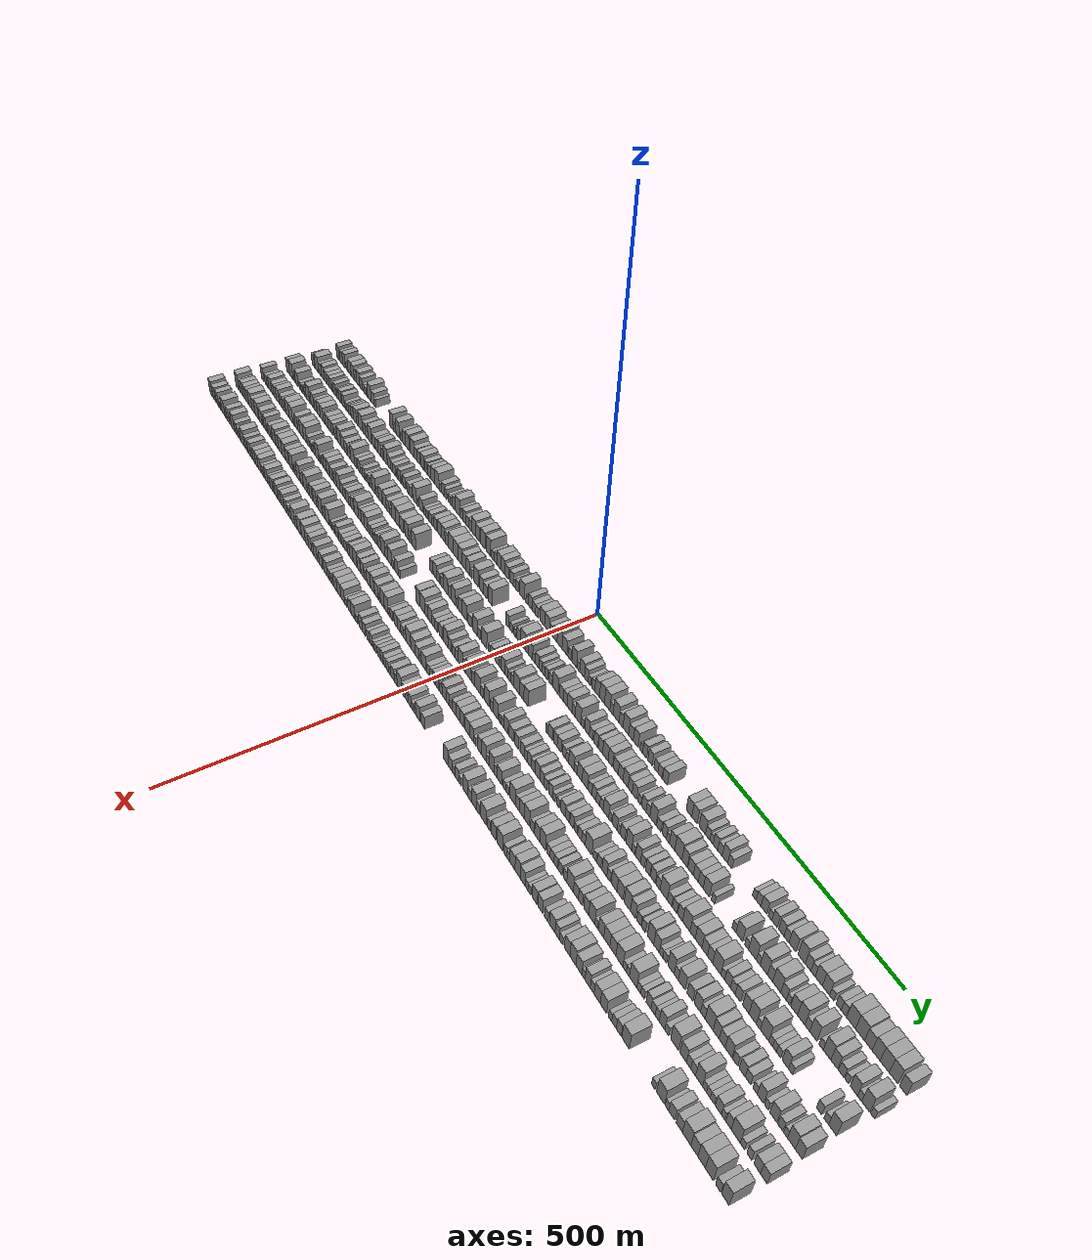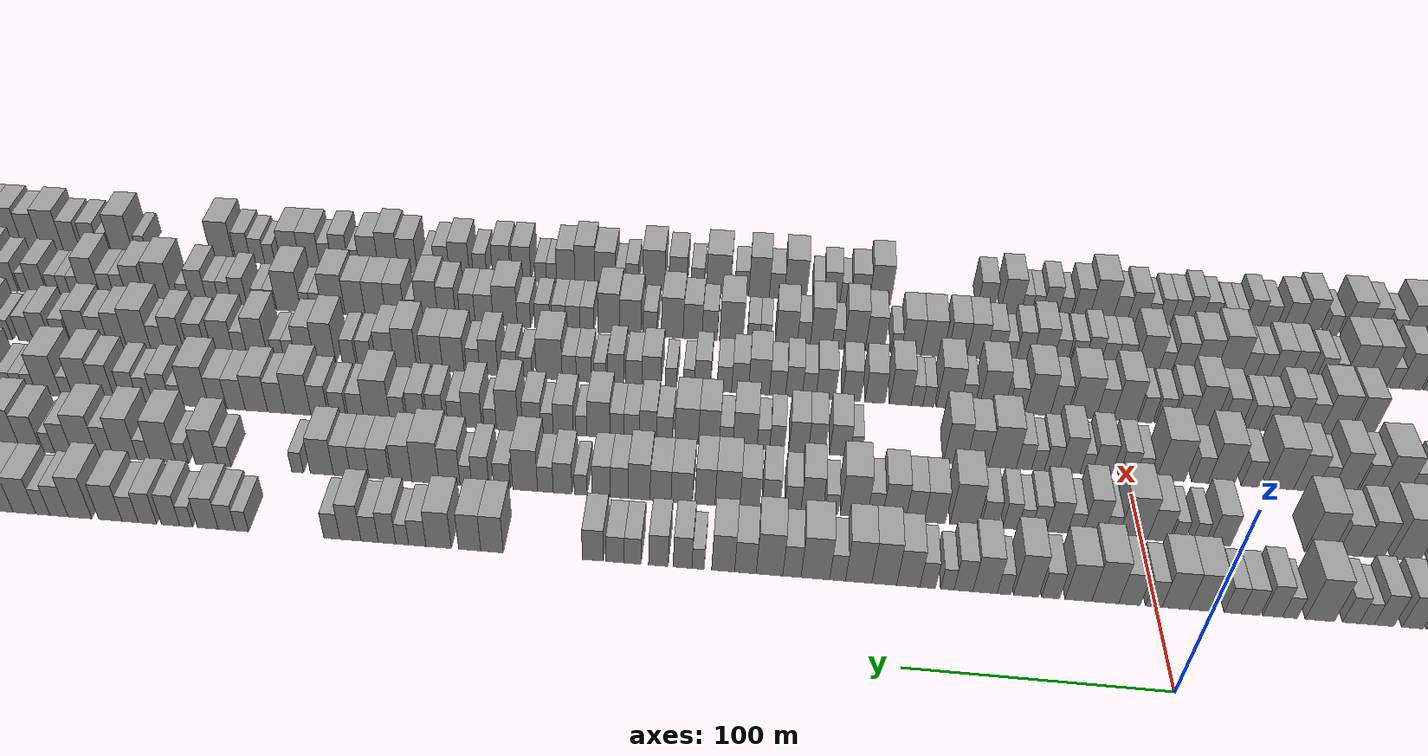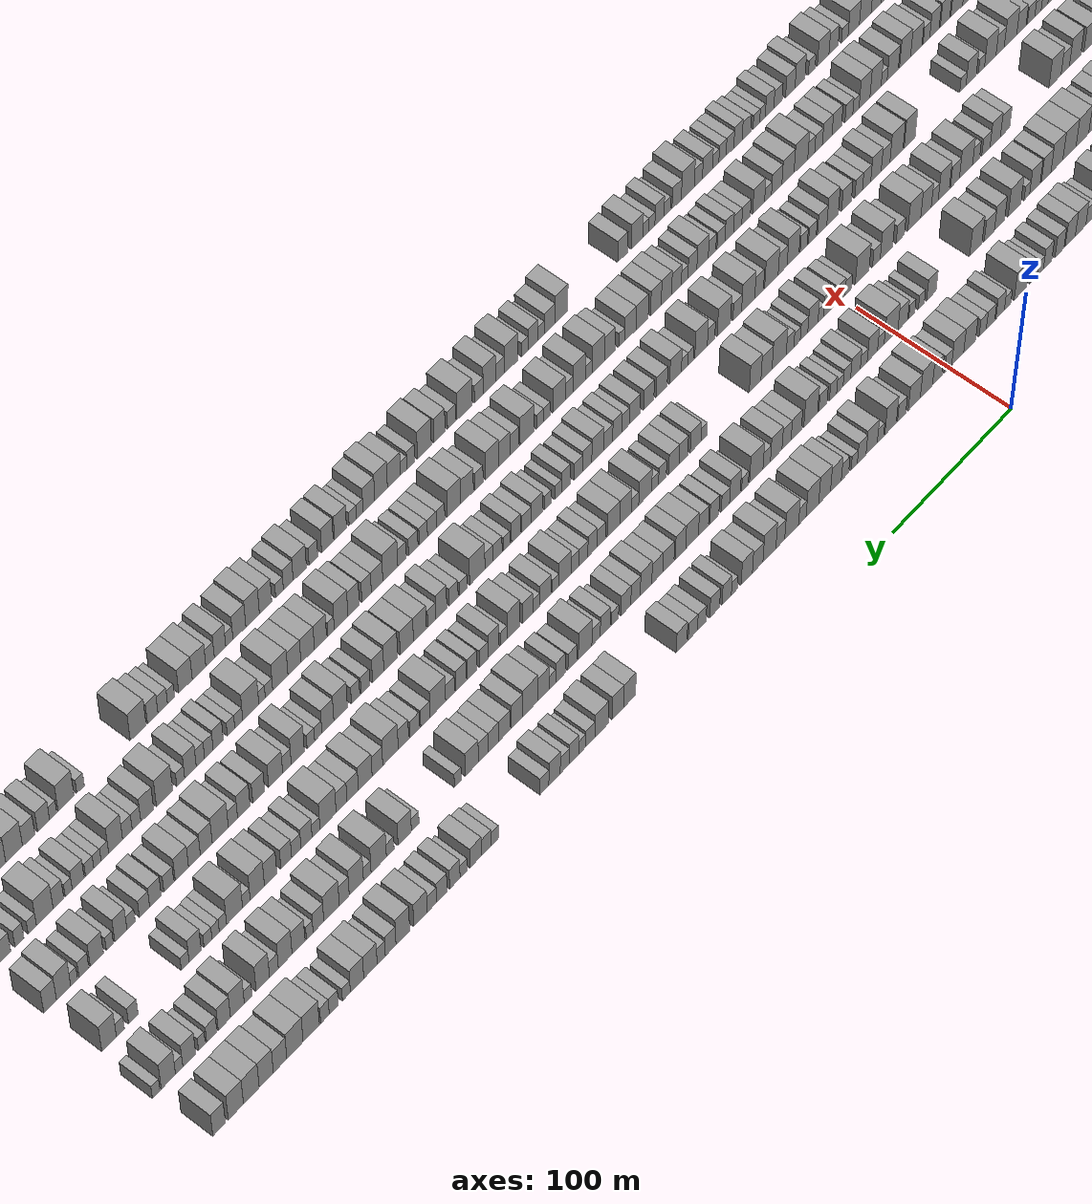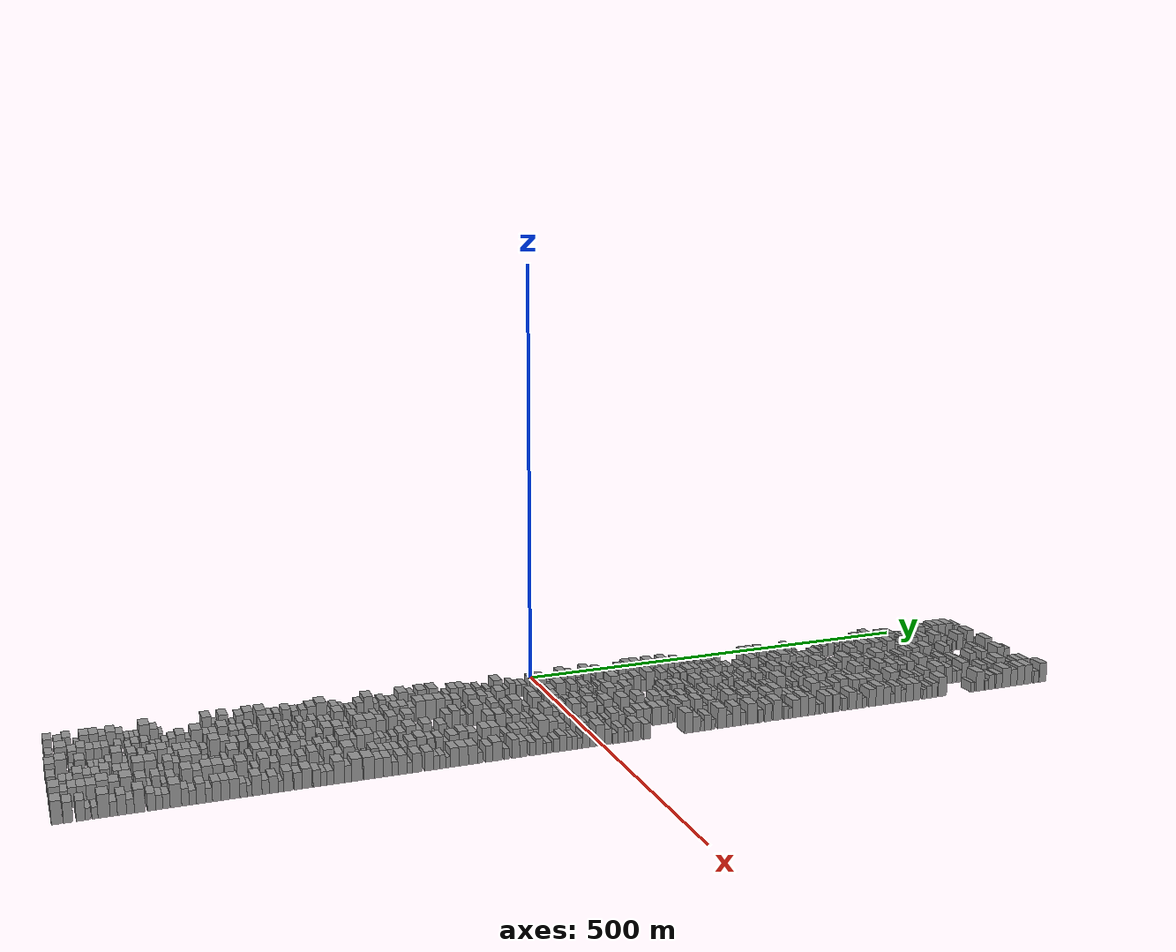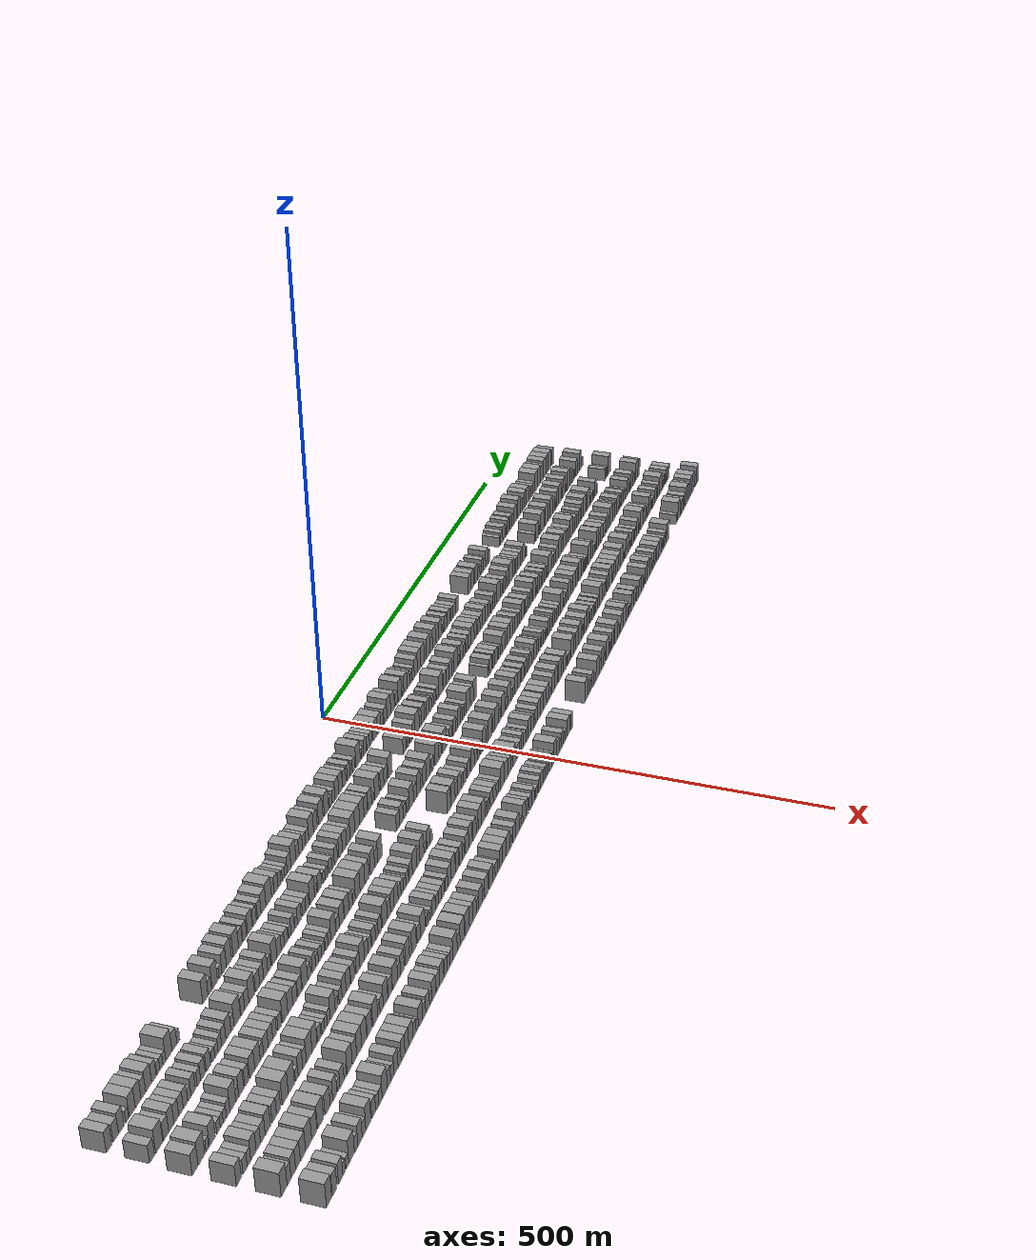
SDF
<sdf version="1.6">
 <world name="default">
  <scene>
   <sky><clouds><speed>12</speed></clouds></sky>
   <ambient>0.4 0.4 0.4 1</ambient>
   <background>0.7 0.7 0.7 1</background>
   <shadows>1</shadows>
  </scene>
  <gravity>0 0 -9.8066</gravity>
  <magnetic_field>6e-06 2.3e-05 -4.2e-05</magnetic_field>
  <physics default="0" name="default_physics" type="ode">
   <ode>
    <solver>
     <type>quick</type>
     <iters>10</iters>
     <sor>1.0</sor>
     <use_dynamic_moi_rescaling>0</use_dynamic_moi_rescaling>
    </solver>
    <constraints>
     <cfm>0</cfm>
     <erp>0.2</erp>
     <contact_max_correcting_vel>100</contact_max_correcting_vel>
     <contact_surface_layer>0.001</contact_surface_layer>
    </constraints>
   </ode>
   <max_step_size>0.004</max_step_size>
   <real_time_factor>1</real_time_factor>
   <real_time_update_rate>250</real_time_update_rate>
  </physics>
  <light name="sun" type="directional">
   <pose>0 0 10 0 0 0</pose>
   <diffuse>0.8 0.8 0.8 1</diffuse>
   <specular>0.2 0.2 0.2 1</specular>
   <attenuation>
    <range>1000</range>
    <constant>0.9</constant>
    <linear>0.01</linear>
    <quadratic>0.001</quadratic>
   </attenuation>
   <direction>-0.5 0.1 -0.9</direction>
  </light>
  <model name="building_1">
   <static>1</static>
   <pose>50.0000 -563.5676 0 0.000000 0.000000 0.000000</pose>
   <link name="link">
    <pose>0 0 10.50 0 0 0</pose>
    <collision name="collision"><geometry><box><size>20.0000 8.8648 21.0000</size></box></geometry></collision>
    <visual name="visual">
     <cast_shadows>0</cast_shadows>
     <geometry><box><size>20.0000 8.8648 21.0000</size></box></geometry>
     <material>
      <script>
       <uri>model://grey_wall/materials/scripts</uri>
       <uri>model://grey_wall/materials/textures</uri>
       <name>vrc/grey_wall</name>
      </script>
     </material>
    </visual>
   </link>
  </model>
  <model name="building_2">
   <static>1</static>
   <pose>50.0000 -552.7918 0 0.000000 0.000000 0.000000</pose>
   <link name="link">
    <pose>0 0 9.00 0 0 0</pose>
    <collision name="collision"><geometry><box><size>20.0000 8.6868 18.0000</size></box></geometry></collision>
    <visual name="visual">
     <cast_shadows>0</cast_shadows>
     <geometry><box><size>20.0000 8.6868 18.0000</size></box></geometry>
     <material>
      <script>
       <uri>model://grey_wall/materials/scripts</uri>
       <uri>model://grey_wall/materials/textures</uri>
       <name>vrc/grey_wall</name>
      </script>
     </material>
    </visual>
   </link>
  </model>
  <model name="building_3">
   <static>1</static>
   <pose>50.0000 -544.1117 0 0.000000 0.000000 0.000000</pose>
   <link name="link">
    <pose>0 0 10.50 0 0 0</pose>
    <collision name="collision"><geometry><box><size>20.0000 8.6732 21.0000</size></box></geometry></collision>
    <visual name="visual">
     <cast_shadows>0</cast_shadows>
     <geometry><box><size>20.0000 8.6732 21.0000</size></box></geometry>
     <material>
      <script>
       <uri>model://grey_wall/materials/scripts</uri>
       <uri>model://grey_wall/materials/textures</uri>
       <name>vrc/grey_wall</name>
      </script>
     </material>
    </visual>
   </link>
  </model>
  <model name="building_4">
   <static>1</static>
   <pose>50.0000 -534.3474 0 0.000000 0.000000 0.000000</pose>
   <link name="link">
    <pose>0 0 6.00 0 0 0</pose>
    <collision name="collision"><geometry><box><size>20.0000 4.8555 12.0000</size></box></geometry></collision>
    <visual name="visual">
     <cast_shadows>0</cast_shadows>
     <geometry><box><size>20.0000 4.8555 12.0000</size></box></geometry>
     <material>
      <script>
       <uri>model://grey_wall/materials/scripts</uri>
       <uri>model://grey_wall/materials/textures</uri>
       <name>vrc/grey_wall</name>
      </script>
     </material>
    </visual>
   </link>
  </model>
  <model name="building_5">
   <static>1</static>
   <pose>50.0000 -525.9488 0 0.000000 0.000000 0.000000</pose>
   <link name="link">
    <pose>0 0 10.50 0 0 0</pose>
    <collision name="collision"><geometry><box><size>20.0000 9.9417 21.0000</size></box></geometry></collision>
    <visual name="visual">
     <cast_shadows>0</cast_shadows>
     <geometry><box><size>20.0000 9.9417 21.0000</size></box></geometry>
     <material>
      <script>
       <uri>model://grey_wall/materials/scripts</uri>
       <uri>model://grey_wall/materials/textures</uri>
       <name>vrc/grey_wall</name>
      </script>
     </material>
    </visual>
   </link>
  </model>
  <model name="building_6">
   <static>1</static>
   <pose>50.0000 -516.1840 0 0.000000 0.000000 0.000000</pose>
   <link name="link">
    <pose>0 0 10.50 0 0 0</pose>
    <collision name="collision"><geometry><box><size>20.0000 9.5878 21.0000</size></box></geometry></collision>
    <visual name="visual">
     <cast_shadows>0</cast_shadows>
     <geometry><box><size>20.0000 9.5878 21.0000</size></box></geometry>
     <material>
      <script>
       <uri>model://grey_wall/materials/scripts</uri>
       <uri>model://grey_wall/materials/textures</uri>
       <name>vrc/grey_wall</name>
      </script>
     </material>
    </visual>
   </link>
  </model>
  <model name="building_7">
   <static>1</static>
   <pose>50.0000 -507.5107 0 0.000000 0.000000 0.000000</pose>
   <link name="link">
    <pose>0 0 9.00 0 0 0</pose>
    <collision name="collision"><geometry><box><size>20.0000 7.7590 18.0000</size></box></geometry></collision>
    <visual name="visual">
     <cast_shadows>0</cast_shadows>
     <geometry><box><size>20.0000 7.7590 18.0000</size></box></geometry>
     <material>
      <script>
       <uri>model://grey_wall/materials/scripts</uri>
       <uri>model://grey_wall/materials/textures</uri>
       <name>vrc/grey_wall</name>
      </script>
     </material>
    </visual>
   </link>
  </model>
  <model name="building_8">
   <static>1</static>
   <pose>50.0000 -498.5991 0 0.000000 0.000000 0.000000</pose>
   <link name="link">
    <pose>0 0 10.50 0 0 0</pose>
    <collision name="collision"><geometry><box><size>20.0000 10.0640 21.0000</size></box></geometry></collision>
    <visual name="visual">
     <cast_shadows>0</cast_shadows>
     <geometry><box><size>20.0000 10.0640 21.0000</size></box></geometry>
     <material>
      <script>
       <uri>model://grey_wall/materials/scripts</uri>
       <uri>model://grey_wall/materials/textures</uri>
       <name>vrc/grey_wall</name>
      </script>
     </material>
    </visual>
   </link>
  </model>
  <model name="building_9">
   <static>1</static>
   <pose>50.0000 -489.5370 0 0.000000 0.000000 0.000000</pose>
   <link name="link">
    <pose>0 0 9.00 0 0 0</pose>
    <collision name="collision"><geometry><box><size>20.0000 8.0602 18.0000</size></box></geometry></collision>
    <visual name="visual">
     <cast_shadows>0</cast_shadows>
     <geometry><box><size>20.0000 8.0602 18.0000</size></box></geometry>
     <material>
      <script>
       <uri>model://grey_wall/materials/scripts</uri>
       <uri>model://grey_wall/materials/textures</uri>
       <name>vrc/grey_wall</name>
      </script>
     </material>
    </visual>
   </link>
  </model>
  <model name="building_10">
   <static>1</static>
   <pose>50.0000 -481.8069 0 0.000000 0.000000 0.000000</pose>
   <link name="link">
    <pose>0 0 6.00 0 0 0</pose>
    <collision name="collision"><geometry><box><size>20.0000 5.4000 12.0000</size></box></geometry></collision>
    <visual name="visual">
     <cast_shadows>0</cast_shadows>
     <geometry><box><size>20.0000 5.4000 12.0000</size></box></geometry>
     <material>
      <script>
       <uri>model://grey_wall/materials/scripts</uri>
       <uri>model://grey_wall/materials/textures</uri>
       <name>vrc/grey_wall</name>
      </script>
     </material>
    </visual>
   </link>
  </model>
  <model name="building_11">
   <static>1</static>
   <pose>50.0000 -476.5526 0 0.000000 0.000000 0.000000</pose>
   <link name="link">
    <pose>0 0 6.00 0 0 0</pose>
    <collision name="collision"><geometry><box><size>20.0000 5.1086 12.0000</size></box></geometry></collision>
    <visual name="visual">
     <cast_shadows>0</cast_shadows>
     <geometry><box><size>20.0000 5.1086 12.0000</size></box></geometry>
     <material>
      <script>
       <uri>model://grey_wall/materials/scripts</uri>
       <uri>model://grey_wall/materials/textures</uri>
       <name>vrc/grey_wall</name>
      </script>
     </material>
    </visual>
   </link>
  </model>
  <model name="building_12">
   <static>1</static>
   <pose>50.0000 -471.4669 0 0.000000 0.000000 0.000000</pose>
   <link name="link">
    <pose>0 0 6.00 0 0 0</pose>
    <collision name="collision"><geometry><box><size>20.0000 5.0627 12.0000</size></box></geometry></collision>
    <visual name="visual">
     <cast_shadows>0</cast_shadows>
     <geometry><box><size>20.0000 5.0627 12.0000</size></box></geometry>
     <material>
      <script>
       <uri>model://grey_wall/materials/scripts</uri>
       <uri>model://grey_wall/materials/textures</uri>
       <name>vrc/grey_wall</name>
      </script>
     </material>
    </visual>
   </link>
  </model>
  <model name="building_13">
   <static>1</static>
   <pose>50.0000 -463.4643 0 0.000000 0.000000 0.000000</pose>
   <link name="link">
    <pose>0 0 12.00 0 0 0</pose>
    <collision name="collision"><geometry><box><size>20.0000 10.9425 24.0000</size></box></geometry></collision>
    <visual name="visual">
     <cast_shadows>0</cast_shadows>
     <geometry><box><size>20.0000 10.9425 24.0000</size></box></geometry>
     <material>
      <script>
       <uri>model://grey_wall/materials/scripts</uri>
       <uri>model://grey_wall/materials/textures</uri>
       <name>vrc/grey_wall</name>
      </script>
     </material>
    </visual>
   </link>
  </model>
  <model name="building_14">
   <static>1</static>
   <pose>50.0000 -453.6241 0 0.000000 0.000000 0.000000</pose>
   <link name="link">
    <pose>0 0 9.00 0 0 0</pose>
    <collision name="collision"><geometry><box><size>20.0000 8.7379 18.0000</size></box></geometry></collision>
    <visual name="visual">
     <cast_shadows>0</cast_shadows>
     <geometry><box><size>20.0000 8.7379 18.0000</size></box></geometry>
     <material>
      <script>
       <uri>model://grey_wall/materials/scripts</uri>
       <uri>model://grey_wall/materials/textures</uri>
       <name>vrc/grey_wall</name>
      </script>
     </material>
    </visual>
   </link>
  </model>
  <model name="building_15">
   <static>1</static>
   <pose>50.0000 -446.6677 0 0.000000 0.000000 0.000000</pose>
   <link name="link">
    <pose>0 0 6.00 0 0 0</pose>
    <collision name="collision"><geometry><box><size>20.0000 5.1750 12.0000</size></box></geometry></collision>
    <visual name="visual">
     <cast_shadows>0</cast_shadows>
     <geometry><box><size>20.0000 5.1750 12.0000</size></box></geometry>
     <material>
      <script>
       <uri>model://grey_wall/materials/scripts</uri>
       <uri>model://grey_wall/materials/textures</uri>
       <name>vrc/grey_wall</name>
      </script>
     </material>
    </visual>
   </link>
  </model>
  <model name="building_16">
   <static>1</static>
   <pose>50.0000 -397.0760 0 0.000000 0.000000 0.000000</pose>
   <link name="link">
    <pose>0 0 12.00 0 0 0</pose>
    <collision name="collision"><geometry><box><size>20.0000 10.0028 24.0000</size></box></geometry></collision>
    <visual name="visual">
     <cast_shadows>0</cast_shadows>
     <geometry><box><size>20.0000 10.0028 24.0000</size></box></geometry>
     <material>
      <script>
       <uri>model://grey_wall/materials/scripts</uri>
       <uri>model://grey_wall/materials/textures</uri>
       <name>vrc/grey_wall</name>
      </script>
     </material>
    </visual>
   </link>
  </model>
  <model name="building_17">
   <static>1</static>
   <pose>50.0000 -388.5987 0 0.000000 0.000000 0.000000</pose>
   <link name="link">
    <pose>0 0 7.50 0 0 0</pose>
    <collision name="collision"><geometry><box><size>20.0000 6.9518 15.0000</size></box></geometry></collision>
    <visual name="visual">
     <cast_shadows>0</cast_shadows>
     <geometry><box><size>20.0000 6.9518 15.0000</size></box></geometry>
     <material>
      <script>
       <uri>model://grey_wall/materials/scripts</uri>
       <uri>model://grey_wall/materials/textures</uri>
       <name>vrc/grey_wall</name>
      </script>
     </material>
    </visual>
   </link>
  </model>
  <model name="building_18">
   <static>1</static>
   <pose>50.0000 -379.0550 0 0.000000 0.000000 0.000000</pose>
   <link name="link">
    <pose>0 0 12.00 0 0 0</pose>
    <collision name="collision"><geometry><box><size>20.0000 10.1357 24.0000</size></box></geometry></collision>
    <visual name="visual">
     <cast_shadows>0</cast_shadows>
     <geometry><box><size>20.0000 10.1357 24.0000</size></box></geometry>
     <material>
      <script>
       <uri>model://grey_wall/materials/scripts</uri>
       <uri>model://grey_wall/materials/textures</uri>
       <name>vrc/grey_wall</name>
      </script>
     </material>
    </visual>
   </link>
  </model>
  <model name="building_19">
   <static>1</static>
   <pose>50.0000 -368.2282 0 0.000000 0.000000 0.000000</pose>
   <link name="link">
    <pose>0 0 6.00 0 0 0</pose>
    <collision name="collision"><geometry><box><size>20.0000 5.5179 12.0000</size></box></geometry></collision>
    <visual name="visual">
     <cast_shadows>0</cast_shadows>
     <geometry><box><size>20.0000 5.5179 12.0000</size></box></geometry>
     <material>
      <script>
       <uri>model://grey_wall/materials/scripts</uri>
       <uri>model://grey_wall/materials/textures</uri>
       <name>vrc/grey_wall</name>
      </script>
     </material>
    </visual>
   </link>
  </model>
  <model name="building_20">
   <static>1</static>
   <pose>50.0000 -361.0315 0 0.000000 0.000000 0.000000</pose>
   <link name="link">
    <pose>0 0 10.50 0 0 0</pose>
    <collision name="collision"><geometry><box><size>20.0000 8.8755 21.0000</size></box></geometry></collision>
    <visual name="visual">
     <cast_shadows>0</cast_shadows>
     <geometry><box><size>20.0000 8.8755 21.0000</size></box></geometry>
     <material>
      <script>
       <uri>model://grey_wall/materials/scripts</uri>
       <uri>model://grey_wall/materials/textures</uri>
       <name>vrc/grey_wall</name>
      </script>
     </material>
    </visual>
   </link>
  </model>
  <model name="building_21">
   <static>1</static>
   <pose>50.0000 -351.4811 0 0.000000 0.000000 0.000000</pose>
   <link name="link">
    <pose>0 0 12.00 0 0 0</pose>
    <collision name="collision"><geometry><box><size>20.0000 10.2253 24.0000</size></box></geometry></collision>
    <visual name="visual">
     <cast_shadows>0</cast_shadows>
     <geometry><box><size>20.0000 10.2253 24.0000</size></box></geometry>
     <material>
      <script>
       <uri>model://grey_wall/materials/scripts</uri>
       <uri>model://grey_wall/materials/textures</uri>
       <name>vrc/grey_wall</name>
      </script>
     </material>
    </visual>
   </link>
  </model>
  <model name="building_22">
   <static>1</static>
   <pose>50.0000 -337.8677 0 0.000000 0.000000 0.000000</pose>
   <link name="link">
    <pose>0 0 12.00 0 0 0</pose>
    <collision name="collision"><geometry><box><size>20.0000 11.0014 24.0000</size></box></geometry></collision>
    <visual name="visual">
     <cast_shadows>0</cast_shadows>
     <geometry><box><size>20.0000 11.0014 24.0000</size></box></geometry>
     <material>
      <script>
       <uri>model://grey_wall/materials/scripts</uri>
       <uri>model://grey_wall/materials/textures</uri>
       <name>vrc/grey_wall</name>
      </script>
     </material>
    </visual>
   </link>
  </model>
  <model name="building_23">
   <static>1</static>
   <pose>50.0000 -328.5939 0 0.000000 0.000000 0.000000</pose>
   <link name="link">
    <pose>0 0 9.00 0 0 0</pose>
    <collision name="collision"><geometry><box><size>20.0000 7.5461 18.0000</size></box></geometry></collision>
    <visual name="visual">
     <cast_shadows>0</cast_shadows>
     <geometry><box><size>20.0000 7.5461 18.0000</size></box></geometry>
     <material>
      <script>
       <uri>model://grey_wall/materials/scripts</uri>
       <uri>model://grey_wall/materials/textures</uri>
       <name>vrc/grey_wall</name>
      </script>
     </material>
    </visual>
   </link>
  </model>
  <model name="building_24">
   <static>1</static>
   <pose>50.0000 -320.0432 0 0.000000 0.000000 0.000000</pose>
   <link name="link">
    <pose>0 0 9.00 0 0 0</pose>
    <collision name="collision"><geometry><box><size>20.0000 7.5552 18.0000</size></box></geometry></collision>
    <visual name="visual">
     <cast_shadows>0</cast_shadows>
     <geometry><box><size>20.0000 7.5552 18.0000</size></box></geometry>
     <material>
      <script>
       <uri>model://grey_wall/materials/scripts</uri>
       <uri>model://grey_wall/materials/textures</uri>
       <name>vrc/grey_wall</name>
      </script>
     </material>
    </visual>
   </link>
  </model>
  <model name="building_25">
   <static>1</static>
   <pose>50.0000 -309.4065 0 0.000000 0.000000 0.000000</pose>
   <link name="link">
    <pose>0 0 10.50 0 0 0</pose>
    <collision name="collision"><geometry><box><size>20.0000 9.7182 21.0000</size></box></geometry></collision>
    <visual name="visual">
     <cast_shadows>0</cast_shadows>
     <geometry><box><size>20.0000 9.7182 21.0000</size></box></geometry>
     <material>
      <script>
       <uri>model://grey_wall/materials/scripts</uri>
       <uri>model://grey_wall/materials/textures</uri>
       <name>vrc/grey_wall</name>
      </script>
     </material>
    </visual>
   </link>
  </model>
  <model name="building_26">
   <static>1</static>
   <pose>50.0000 -299.8369 0 0.000000 0.000000 0.000000</pose>
   <link name="link">
    <pose>0 0 9.00 0 0 0</pose>
    <collision name="collision"><geometry><box><size>20.0000 7.4212 18.0000</size></box></geometry></collision>
    <visual name="visual">
     <cast_shadows>0</cast_shadows>
     <geometry><box><size>20.0000 7.4212 18.0000</size></box></geometry>
     <material>
      <script>
       <uri>model://grey_wall/materials/scripts</uri>
       <uri>model://grey_wall/materials/textures</uri>
       <name>vrc/grey_wall</name>
      </script>
     </material>
    </visual>
   </link>
  </model>
  <model name="building_27">
   <static>1</static>
   <pose>50.0000 -290.3127 0 0.000000 0.000000 0.000000</pose>
   <link name="link">
    <pose>0 0 9.00 0 0 0</pose>
    <collision name="collision"><geometry><box><size>20.0000 7.6271 18.0000</size></box></geometry></collision>
    <visual name="visual">
     <cast_shadows>0</cast_shadows>
     <geometry><box><size>20.0000 7.6271 18.0000</size></box></geometry>
     <material>
      <script>
       <uri>model://grey_wall/materials/scripts</uri>
       <uri>model://grey_wall/materials/textures</uri>
       <name>vrc/grey_wall</name>
      </script>
     </material>
    </visual>
   </link>
  </model>
  <model name="building_28">
   <static>1</static>
   <pose>50.0000 -281.3289 0 0.000000 0.000000 0.000000</pose>
   <link name="link">
    <pose>0 0 10.50 0 0 0</pose>
    <collision name="collision"><geometry><box><size>20.0000 10.3405 21.0000</size></box></geometry></collision>
    <visual name="visual">
     <cast_shadows>0</cast_shadows>
     <geometry><box><size>20.0000 10.3405 21.0000</size></box></geometry>
     <material>
      <script>
       <uri>model://grey_wall/materials/scripts</uri>
       <uri>model://grey_wall/materials/textures</uri>
       <name>vrc/grey_wall</name>
      </script>
     </material>
    </visual>
   </link>
  </model>
  <model name="building_29">
   <static>1</static>
   <pose>50.0000 -270.2084 0 0.000000 0.000000 0.000000</pose>
   <link name="link">
    <pose>0 0 12.00 0 0 0</pose>
    <collision name="collision"><geometry><box><size>20.0000 11.9004 24.0000</size></box></geometry></collision>
    <visual name="visual">
     <cast_shadows>0</cast_shadows>
     <geometry><box><size>20.0000 11.9004 24.0000</size></box></geometry>
     <material>
      <script>
       <uri>model://grey_wall/materials/scripts</uri>
       <uri>model://grey_wall/materials/textures</uri>
       <name>vrc/grey_wall</name>
      </script>
     </material>
    </visual>
   </link>
  </model>
  <model name="building_30">
   <static>1</static>
   <pose>50.0000 -261.3964 0 0.000000 0.000000 0.000000</pose>
   <link name="link">
    <pose>0 0 6.00 0 0 0</pose>
    <collision name="collision"><geometry><box><size>20.0000 5.7237 12.0000</size></box></geometry></collision>
    <visual name="visual">
     <cast_shadows>0</cast_shadows>
     <geometry><box><size>20.0000 5.7237 12.0000</size></box></geometry>
     <material>
      <script>
       <uri>model://grey_wall/materials/scripts</uri>
       <uri>model://grey_wall/materials/textures</uri>
       <name>vrc/grey_wall</name>
      </script>
     </material>
    </visual>
   </link>
  </model>
  <model name="building_31">
   <static>1</static>
   <pose>50.0000 -254.4233 0 0.000000 0.000000 0.000000</pose>
   <link name="link">
    <pose>0 0 9.00 0 0 0</pose>
    <collision name="collision"><geometry><box><size>20.0000 8.2224 18.0000</size></box></geometry></collision>
    <visual name="visual">
     <cast_shadows>0</cast_shadows>
     <geometry><box><size>20.0000 8.2224 18.0000</size></box></geometry>
     <material>
      <script>
       <uri>model://grey_wall/materials/scripts</uri>
       <uri>model://grey_wall/materials/textures</uri>
       <name>vrc/grey_wall</name>
      </script>
     </material>
    </visual>
   </link>
  </model>
  <model name="building_32">
   <static>1</static>
   <pose>50.0000 -247.2109 0 0.000000 0.000000 0.000000</pose>
   <link name="link">
    <pose>0 0 7.50 0 0 0</pose>
    <collision name="collision"><geometry><box><size>20.0000 6.2025 15.0000</size></box></geometry></collision>
    <visual name="visual">
     <cast_shadows>0</cast_shadows>
     <geometry><box><size>20.0000 6.2025 15.0000</size></box></geometry>
     <material>
      <script>
       <uri>model://grey_wall/materials/scripts</uri>
       <uri>model://grey_wall/materials/textures</uri>
       <name>vrc/grey_wall</name>
      </script>
     </material>
    </visual>
   </link>
  </model>
  <model name="building_33">
   <static>1</static>
   <pose>50.0000 -238.4024 0 0.000000 0.000000 0.000000</pose>
   <link name="link">
    <pose>0 0 6.00 0 0 0</pose>
    <collision name="collision"><geometry><box><size>20.0000 5.4144 12.0000</size></box></geometry></collision>
    <visual name="visual">
     <cast_shadows>0</cast_shadows>
     <geometry><box><size>20.0000 5.4144 12.0000</size></box></geometry>
     <material>
      <script>
       <uri>model://grey_wall/materials/scripts</uri>
       <uri>model://grey_wall/materials/textures</uri>
       <name>vrc/grey_wall</name>
      </script>
     </material>
    </visual>
   </link>
  </model>
  <model name="building_34">
   <static>1</static>
   <pose>50.0000 -233.0142 0 0.000000 0.000000 0.000000</pose>
   <link name="link">
    <pose>0 0 6.00 0 0 0</pose>
    <collision name="collision"><geometry><box><size>20.0000 5.3620 12.0000</size></box></geometry></collision>
    <visual name="visual">
     <cast_shadows>0</cast_shadows>
     <geometry><box><size>20.0000 5.3620 12.0000</size></box></geometry>
     <material>
      <script>
       <uri>model://grey_wall/materials/scripts</uri>
       <uri>model://grey_wall/materials/textures</uri>
       <name>vrc/grey_wall</name>
      </script>
     </material>
    </visual>
   </link>
  </model>
  <model name="building_35">
   <static>1</static>
   <pose>50.0000 -226.1422 0 0.000000 0.000000 0.000000</pose>
   <link name="link">
    <pose>0 0 9.00 0 0 0</pose>
    <collision name="collision"><geometry><box><size>20.0000 8.3820 18.0000</size></box></geometry></collision>
    <visual name="visual">
     <cast_shadows>0</cast_shadows>
     <geometry><box><size>20.0000 8.3820 18.0000</size></box></geometry>
     <material>
      <script>
       <uri>model://grey_wall/materials/scripts</uri>
       <uri>model://grey_wall/materials/textures</uri>
       <name>vrc/grey_wall</name>
      </script>
     </material>
    </visual>
   </link>
  </model>
  <model name="building_36">
   <static>1</static>
   <pose>50.0000 -216.4111 0 0.000000 0.000000 0.000000</pose>
   <link name="link">
    <pose>0 0 12.00 0 0 0</pose>
    <collision name="collision"><geometry><box><size>20.0000 11.0804 24.0000</size></box></geometry></collision>
    <visual name="visual">
     <cast_shadows>0</cast_shadows>
     <geometry><box><size>20.0000 11.0804 24.0000</size></box></geometry>
     <material>
      <script>
       <uri>model://grey_wall/materials/scripts</uri>
       <uri>model://grey_wall/materials/textures</uri>
       <name>vrc/grey_wall</name>
      </script>
     </material>
    </visual>
   </link>
  </model>
  <model name="building_37">
   <static>1</static>
   <pose>50.0000 -207.3943 0 0.000000 0.000000 0.000000</pose>
   <link name="link">
    <pose>0 0 7.50 0 0 0</pose>
    <collision name="collision"><geometry><box><size>20.0000 6.9532 15.0000</size></box></geometry></collision>
    <visual name="visual">
     <cast_shadows>0</cast_shadows>
     <geometry><box><size>20.0000 6.9532 15.0000</size></box></geometry>
     <material>
      <script>
       <uri>model://grey_wall/materials/scripts</uri>
       <uri>model://grey_wall/materials/textures</uri>
       <name>vrc/grey_wall</name>
      </script>
     </material>
    </visual>
   </link>
  </model>
  <model name="building_38">
   <static>1</static>
   <pose>50.0000 -199.9215 0 0.000000 0.000000 0.000000</pose>
   <link name="link">
    <pose>0 0 9.00 0 0 0</pose>
    <collision name="collision"><geometry><box><size>20.0000 7.9923 18.0000</size></box></geometry></collision>
    <visual name="visual">
     <cast_shadows>0</cast_shadows>
     <geometry><box><size>20.0000 7.9923 18.0000</size></box></geometry>
     <material>
      <script>
       <uri>model://grey_wall/materials/scripts</uri>
       <uri>model://grey_wall/materials/textures</uri>
       <name>vrc/grey_wall</name>
      </script>
     </material>
    </visual>
   </link>
  </model>
  <model name="building_39">
   <static>1</static>
   <pose>50.0000 -192.4334 0 0.000000 0.000000 0.000000</pose>
   <link name="link">
    <pose>0 0 7.50 0 0 0</pose>
    <collision name="collision"><geometry><box><size>20.0000 6.9839 15.0000</size></box></geometry></collision>
    <visual name="visual">
     <cast_shadows>0</cast_shadows>
     <geometry><box><size>20.0000 6.9839 15.0000</size></box></geometry>
     <material>
      <script>
       <uri>model://grey_wall/materials/scripts</uri>
       <uri>model://grey_wall/materials/textures</uri>
       <name>vrc/grey_wall</name>
      </script>
     </material>
    </visual>
   </link>
  </model>
  <model name="building_40">
   <static>1</static>
   <pose>50.0000 -185.2547 0 0.000000 0.000000 0.000000</pose>
   <link name="link">
    <pose>0 0 7.50 0 0 0</pose>
    <collision name="collision"><geometry><box><size>20.0000 7.3734 15.0000</size></box></geometry></collision>
    <visual name="visual">
     <cast_shadows>0</cast_shadows>
     <geometry><box><size>20.0000 7.3734 15.0000</size></box></geometry>
     <material>
      <script>
       <uri>model://grey_wall/materials/scripts</uri>
       <uri>model://grey_wall/materials/textures</uri>
       <name>vrc/grey_wall</name>
      </script>
     </material>
    </visual>
   </link>
  </model>
  <model name="building_41">
   <static>1</static>
   <pose>50.0000 -175.9584 0 0.000000 0.000000 0.000000</pose>
   <link name="link">
    <pose>0 0 12.00 0 0 0</pose>
    <collision name="collision"><geometry><box><size>20.0000 11.2193 24.0000</size></box></geometry></collision>
    <visual name="visual">
     <cast_shadows>0</cast_shadows>
     <geometry><box><size>20.0000 11.2193 24.0000</size></box></geometry>
     <material>
      <script>
       <uri>model://grey_wall/materials/scripts</uri>
       <uri>model://grey_wall/materials/textures</uri>
       <name>vrc/grey_wall</name>
      </script>
     </material>
    </visual>
   </link>
  </model>
  <model name="building_42">
   <static>1</static>
   <pose>50.0000 -166.0863 0 0.000000 0.000000 0.000000</pose>
   <link name="link">
    <pose>0 0 10.50 0 0 0</pose>
    <collision name="collision"><geometry><box><size>20.0000 8.5249 21.0000</size></box></geometry></collision>
    <visual name="visual">
     <cast_shadows>0</cast_shadows>
     <geometry><box><size>20.0000 8.5249 21.0000</size></box></geometry>
     <material>
      <script>
       <uri>model://grey_wall/materials/scripts</uri>
       <uri>model://grey_wall/materials/textures</uri>
       <name>vrc/grey_wall</name>
      </script>
     </material>
    </visual>
   </link>
  </model>
  <model name="building_43">
   <static>1</static>
   <pose>50.0000 -153.5417 0 0.000000 0.000000 0.000000</pose>
   <link name="link">
    <pose>0 0 12.00 0 0 0</pose>
    <collision name="collision"><geometry><box><size>20.0000 10.5641 24.0000</size></box></geometry></collision>
    <visual name="visual">
     <cast_shadows>0</cast_shadows>
     <geometry><box><size>20.0000 10.5641 24.0000</size></box></geometry>
     <material>
      <script>
       <uri>model://grey_wall/materials/scripts</uri>
       <uri>model://grey_wall/materials/textures</uri>
       <name>vrc/grey_wall</name>
      </script>
     </material>
    </visual>
   </link>
  </model>
  <model name="building_44">
   <static>1</static>
   <pose>50.0000 -139.9636 0 0.000000 0.000000 0.000000</pose>
   <link name="link">
    <pose>0 0 12.00 0 0 0</pose>
    <collision name="collision"><geometry><box><size>20.0000 10.5922 24.0000</size></box></geometry></collision>
    <visual name="visual">
     <cast_shadows>0</cast_shadows>
     <geometry><box><size>20.0000 10.5922 24.0000</size></box></geometry>
     <material>
      <script>
       <uri>model://grey_wall/materials/scripts</uri>
       <uri>model://grey_wall/materials/textures</uri>
       <name>vrc/grey_wall</name>
      </script>
     </material>
    </visual>
   </link>
  </model>
  <model name="building_45">
   <static>1</static>
   <pose>50.0000 -129.8153 0 0.000000 0.000000 0.000000</pose>
   <link name="link">
    <pose>0 0 6.00 0 0 0</pose>
    <collision name="collision"><geometry><box><size>20.0000 5.7045 12.0000</size></box></geometry></collision>
    <visual name="visual">
     <cast_shadows>0</cast_shadows>
     <geometry><box><size>20.0000 5.7045 12.0000</size></box></geometry>
     <material>
      <script>
       <uri>model://grey_wall/materials/scripts</uri>
       <uri>model://grey_wall/materials/textures</uri>
       <name>vrc/grey_wall</name>
      </script>
     </material>
    </visual>
   </link>
  </model>
  <model name="building_46">
   <static>1</static>
   <pose>50.0000 -122.7985 0 0.000000 0.000000 0.000000</pose>
   <link name="link">
    <pose>0 0 7.50 0 0 0</pose>
    <collision name="collision"><geometry><box><size>20.0000 6.3290 15.0000</size></box></geometry></collision>
    <visual name="visual">
     <cast_shadows>0</cast_shadows>
     <geometry><box><size>20.0000 6.3290 15.0000</size></box></geometry>
     <material>
      <script>
       <uri>model://grey_wall/materials/scripts</uri>
       <uri>model://grey_wall/materials/textures</uri>
       <name>vrc/grey_wall</name>
      </script>
     </material>
    </visual>
   </link>
  </model>
  <model name="building_47">
   <static>1</static>
   <pose>50.0000 -114.9309 0 0.000000 0.000000 0.000000</pose>
   <link name="link">
    <pose>0 0 10.50 0 0 0</pose>
    <collision name="collision"><geometry><box><size>20.0000 9.4061 21.0000</size></box></geometry></collision>
    <visual name="visual">
     <cast_shadows>0</cast_shadows>
     <geometry><box><size>20.0000 9.4061 21.0000</size></box></geometry>
     <material>
      <script>
       <uri>model://grey_wall/materials/scripts</uri>
       <uri>model://grey_wall/materials/textures</uri>
       <name>vrc/grey_wall</name>
      </script>
     </material>
    </visual>
   </link>
  </model>
  <model name="building_48">
   <static>1</static>
   <pose>50.0000 -105.7499 0 0.000000 0.000000 0.000000</pose>
   <link name="link">
    <pose>0 0 10.50 0 0 0</pose>
    <collision name="collision"><geometry><box><size>20.0000 8.9559 21.0000</size></box></geometry></collision>
    <visual name="visual">
     <cast_shadows>0</cast_shadows>
     <geometry><box><size>20.0000 8.9559 21.0000</size></box></geometry>
     <material>
      <script>
       <uri>model://grey_wall/materials/scripts</uri>
       <uri>model://grey_wall/materials/textures</uri>
       <name>vrc/grey_wall</name>
      </script>
     </material>
    </visual>
   </link>
  </model>
  <model name="building_49">
   <static>1</static>
   <pose>50.0000 -96.2931 0 0.000000 0.000000 0.000000</pose>
   <link name="link">
    <pose>0 0 9.00 0 0 0</pose>
    <collision name="collision"><geometry><box><size>20.0000 7.9578 18.0000</size></box></geometry></collision>
    <visual name="visual">
     <cast_shadows>0</cast_shadows>
     <geometry><box><size>20.0000 7.9578 18.0000</size></box></geometry>
     <material>
      <script>
       <uri>model://grey_wall/materials/scripts</uri>
       <uri>model://grey_wall/materials/textures</uri>
       <name>vrc/grey_wall</name>
      </script>
     </material>
    </visual>
   </link>
  </model>
  <model name="building_50">
   <static>1</static>
   <pose>50.0000 -85.6334 0 0.000000 0.000000 0.000000</pose>
   <link name="link">
    <pose>0 0 9.00 0 0 0</pose>
    <collision name="collision"><geometry><box><size>20.0000 7.3615 18.0000</size></box></geometry></collision>
    <visual name="visual">
     <cast_shadows>0</cast_shadows>
     <geometry><box><size>20.0000 7.3615 18.0000</size></box></geometry>
     <material>
      <script>
       <uri>model://grey_wall/materials/scripts</uri>
       <uri>model://grey_wall/materials/textures</uri>
       <name>vrc/grey_wall</name>
      </script>
     </material>
    </visual>
   </link>
  </model>
  <model name="building_51">
   <static>1</static>
   <pose>50.0000 -79.2243 0 0.000000 0.000000 0.000000</pose>
   <link name="link">
    <pose>0 0 6.00 0 0 0</pose>
    <collision name="collision"><geometry><box><size>20.0000 5.4566 12.0000</size></box></geometry></collision>
    <visual name="visual">
     <cast_shadows>0</cast_shadows>
     <geometry><box><size>20.0000 5.4566 12.0000</size></box></geometry>
     <material>
      <script>
       <uri>model://grey_wall/materials/scripts</uri>
       <uri>model://grey_wall/materials/textures</uri>
       <name>vrc/grey_wall</name>
      </script>
     </material>
    </visual>
   </link>
  </model>
  <model name="building_52">
   <static>1</static>
   <pose>50.0000 -73.3475 0 0.000000 0.000000 0.000000</pose>
   <link name="link">
    <pose>0 0 7.50 0 0 0</pose>
    <collision name="collision"><geometry><box><size>20.0000 6.2970 15.0000</size></box></geometry></collision>
    <visual name="visual">
     <cast_shadows>0</cast_shadows>
     <geometry><box><size>20.0000 6.2970 15.0000</size></box></geometry>
     <material>
      <script>
       <uri>model://grey_wall/materials/scripts</uri>
       <uri>model://grey_wall/materials/textures</uri>
       <name>vrc/grey_wall</name>
      </script>
     </material>
    </visual>
   </link>
  </model>
  <model name="building_53">
   <static>1</static>
   <pose>50.0000 -61.7412 0 0.000000 0.000000 0.000000</pose>
   <link name="link">
    <pose>0 0 12.00 0 0 0</pose>
    <collision name="collision"><geometry><box><size>20.0000 10.9156 24.0000</size></box></geometry></collision>
    <visual name="visual">
     <cast_shadows>0</cast_shadows>
     <geometry><box><size>20.0000 10.9156 24.0000</size></box></geometry>
     <material>
      <script>
       <uri>model://grey_wall/materials/scripts</uri>
       <uri>model://grey_wall/materials/textures</uri>
       <name>vrc/grey_wall</name>
      </script>
     </material>
    </visual>
   </link>
  </model>
  <model name="building_54">
   <static>1</static>
   <pose>50.0000 -50.4743 0 0.000000 0.000000 0.000000</pose>
   <link name="link">
    <pose>0 0 6.00 0 0 0</pose>
    <collision name="collision"><geometry><box><size>20.0000 5.6182 12.0000</size></box></geometry></collision>
    <visual name="visual">
     <cast_shadows>0</cast_shadows>
     <geometry><box><size>20.0000 5.6182 12.0000</size></box></geometry>
     <material>
      <script>
       <uri>model://grey_wall/materials/scripts</uri>
       <uri>model://grey_wall/materials/textures</uri>
       <name>vrc/grey_wall</name>
      </script>
     </material>
    </visual>
   </link>
  </model>
  <model name="building_55">
   <static>1</static>
   <pose>50.0000 -43.9768 0 0.000000 0.000000 0.000000</pose>
   <link name="link">
    <pose>0 0 9.00 0 0 0</pose>
    <collision name="collision"><geometry><box><size>20.0000 7.3768 18.0000</size></box></geometry></collision>
    <visual name="visual">
     <cast_shadows>0</cast_shadows>
     <geometry><box><size>20.0000 7.3768 18.0000</size></box></geometry>
     <material>
      <script>
       <uri>model://grey_wall/materials/scripts</uri>
       <uri>model://grey_wall/materials/textures</uri>
       <name>vrc/grey_wall</name>
      </script>
     </material>
    </visual>
   </link>
  </model>
  <model name="building_56">
   <static>1</static>
   <pose>50.0000 -35.6402 0 0.000000 0.000000 0.000000</pose>
   <link name="link">
    <pose>0 0 7.50 0 0 0</pose>
    <collision name="collision"><geometry><box><size>20.0000 7.2963 15.0000</size></box></geometry></collision>
    <visual name="visual">
     <cast_shadows>0</cast_shadows>
     <geometry><box><size>20.0000 7.2963 15.0000</size></box></geometry>
     <material>
      <script>
       <uri>model://grey_wall/materials/scripts</uri>
       <uri>model://grey_wall/materials/textures</uri>
       <name>vrc/grey_wall</name>
      </script>
     </material>
    </visual>
   </link>
  </model>
  <model name="building_57">
   <static>1</static>
   <pose>50.0000 -28.8450 0 0.000000 0.000000 0.000000</pose>
   <link name="link">
    <pose>0 0 7.50 0 0 0</pose>
    <collision name="collision"><geometry><box><size>20.0000 6.2941 15.0000</size></box></geometry></collision>
    <visual name="visual">
     <cast_shadows>0</cast_shadows>
     <geometry><box><size>20.0000 6.2941 15.0000</size></box></geometry>
     <material>
      <script>
       <uri>model://grey_wall/materials/scripts</uri>
       <uri>model://grey_wall/materials/textures</uri>
       <name>vrc/grey_wall</name>
      </script>
     </material>
    </visual>
   </link>
  </model>
  <model name="building_58">
   <static>1</static>
   <pose>50.0000 -17.5523 0 0.000000 0.000000 0.000000</pose>
   <link name="link">
    <pose>0 0 10.50 0 0 0</pose>
    <collision name="collision"><geometry><box><size>20.0000 10.2912 21.0000</size></box></geometry></collision>
    <visual name="visual">
     <cast_shadows>0</cast_shadows>
     <geometry><box><size>20.0000 10.2912 21.0000</size></box></geometry>
     <material>
      <script>
       <uri>model://grey_wall/materials/scripts</uri>
       <uri>model://grey_wall/materials/textures</uri>
       <name>vrc/grey_wall</name>
      </script>
     </material>
    </visual>
   </link>
  </model>
  <model name="building_59">
   <static>1</static>
   <pose>50.0000 -7.2520 0 0.000000 0.000000 0.000000</pose>
   <link name="link">
    <pose>0 0 10.50 0 0 0</pose>
    <collision name="collision"><geometry><box><size>20.0000 10.3095 21.0000</size></box></geometry></collision>
    <visual name="visual">
     <cast_shadows>0</cast_shadows>
     <geometry><box><size>20.0000 10.3095 21.0000</size></box></geometry>
     <material>
      <script>
       <uri>model://grey_wall/materials/scripts</uri>
       <uri>model://grey_wall/materials/textures</uri>
       <name>vrc/grey_wall</name>
      </script>
     </material>
    </visual>
   </link>
  </model>
  <model name="building_60">
   <static>1</static>
   <pose>50.0000 1.0371 0 0.000000 0.000000 0.000000</pose>
   <link name="link">
    <pose>0 0 7.50 0 0 0</pose>
    <collision name="collision"><geometry><box><size>20.0000 6.2686 15.0000</size></box></geometry></collision>
    <visual name="visual">
     <cast_shadows>0</cast_shadows>
     <geometry><box><size>20.0000 6.2686 15.0000</size></box></geometry>
     <material>
      <script>
       <uri>model://grey_wall/materials/scripts</uri>
       <uri>model://grey_wall/materials/textures</uri>
       <name>vrc/grey_wall</name>
      </script>
     </material>
    </visual>
   </link>
  </model>
  <model name="building_61">
   <static>1</static>
   <pose>50.0000 10.2967 0 0.000000 0.000000 0.000000</pose>
   <link name="link">
    <pose>0 0 9.00 0 0 0</pose>
    <collision name="collision"><geometry><box><size>20.0000 8.2506 18.0000</size></box></geometry></collision>
    <visual name="visual">
     <cast_shadows>0</cast_shadows>
     <geometry><box><size>20.0000 8.2506 18.0000</size></box></geometry>
     <material>
      <script>
       <uri>model://grey_wall/materials/scripts</uri>
       <uri>model://grey_wall/materials/textures</uri>
       <name>vrc/grey_wall</name>
      </script>
     </material>
    </visual>
   </link>
  </model>
  <model name="building_62">
   <static>1</static>
   <pose>50.0000 19.6122 0 0.000000 0.000000 0.000000</pose>
   <link name="link">
    <pose>0 0 12.00 0 0 0</pose>
    <collision name="collision"><geometry><box><size>20.0000 10.3805 24.0000</size></box></geometry></collision>
    <visual name="visual">
     <cast_shadows>0</cast_shadows>
     <geometry><box><size>20.0000 10.3805 24.0000</size></box></geometry>
     <material>
      <script>
       <uri>model://grey_wall/materials/scripts</uri>
       <uri>model://grey_wall/materials/textures</uri>
       <name>vrc/grey_wall</name>
      </script>
     </material>
    </visual>
   </link>
  </model>
  <model name="building_63">
   <static>1</static>
   <pose>50.0000 29.9259 0 0.000000 0.000000 0.000000</pose>
   <link name="link">
    <pose>0 0 10.50 0 0 0</pose>
    <collision name="collision"><geometry><box><size>20.0000 10.2469 21.0000</size></box></geometry></collision>
    <visual name="visual">
     <cast_shadows>0</cast_shadows>
     <geometry><box><size>20.0000 10.2469 21.0000</size></box></geometry>
     <material>
      <script>
       <uri>model://grey_wall/materials/scripts</uri>
       <uri>model://grey_wall/materials/textures</uri>
       <name>vrc/grey_wall</name>
      </script>
     </material>
    </visual>
   </link>
  </model>
  <model name="building_64">
   <static>1</static>
   <pose>50.0000 40.5911 0 0.000000 0.000000 0.000000</pose>
   <link name="link">
    <pose>0 0 7.50 0 0 0</pose>
    <collision name="collision"><geometry><box><size>20.0000 7.0836 15.0000</size></box></geometry></collision>
    <visual name="visual">
     <cast_shadows>0</cast_shadows>
     <geometry><box><size>20.0000 7.0836 15.0000</size></box></geometry>
     <material>
      <script>
       <uri>model://grey_wall/materials/scripts</uri>
       <uri>model://grey_wall/materials/textures</uri>
       <name>vrc/grey_wall</name>
      </script>
     </material>
    </visual>
   </link>
  </model>
  <model name="building_65">
   <static>1</static>
   <pose>50.0000 50.0073 0 0.000000 0.000000 0.000000</pose>
   <link name="link">
    <pose>0 0 12.00 0 0 0</pose>
    <collision name="collision"><geometry><box><size>20.0000 9.7487 24.0000</size></box></geometry></collision>
    <visual name="visual">
     <cast_shadows>0</cast_shadows>
     <geometry><box><size>20.0000 9.7487 24.0000</size></box></geometry>
     <material>
      <script>
       <uri>model://grey_wall/materials/scripts</uri>
       <uri>model://grey_wall/materials/textures</uri>
       <name>vrc/grey_wall</name>
      </script>
     </material>
    </visual>
   </link>
  </model>
  <model name="building_66">
   <static>1</static>
   <pose>50.0000 58.5451 0 0.000000 0.000000 0.000000</pose>
   <link name="link">
    <pose>0 0 6.00 0 0 0</pose>
    <collision name="collision"><geometry><box><size>20.0000 5.3269 12.0000</size></box></geometry></collision>
    <visual name="visual">
     <cast_shadows>0</cast_shadows>
     <geometry><box><size>20.0000 5.3269 12.0000</size></box></geometry>
     <material>
      <script>
       <uri>model://grey_wall/materials/scripts</uri>
       <uri>model://grey_wall/materials/textures</uri>
       <name>vrc/grey_wall</name>
      </script>
     </material>
    </visual>
   </link>
  </model>
  <model name="building_67">
   <static>1</static>
   <pose>50.0000 65.9376 0 0.000000 0.000000 0.000000</pose>
   <link name="link">
    <pose>0 0 10.50 0 0 0</pose>
    <collision name="collision"><geometry><box><size>20.0000 9.4582 21.0000</size></box></geometry></collision>
    <visual name="visual">
     <cast_shadows>0</cast_shadows>
     <geometry><box><size>20.0000 9.4582 21.0000</size></box></geometry>
     <material>
      <script>
       <uri>model://grey_wall/materials/scripts</uri>
       <uri>model://grey_wall/materials/textures</uri>
       <name>vrc/grey_wall</name>
      </script>
     </material>
    </visual>
   </link>
  </model>
  <model name="building_68">
   <static>1</static>
   <pose>50.0000 74.3340 0 0.000000 0.000000 0.000000</pose>
   <link name="link">
    <pose>0 0 9.00 0 0 0</pose>
    <collision name="collision"><geometry><box><size>20.0000 7.3345 18.0000</size></box></geometry></collision>
    <visual name="visual">
     <cast_shadows>0</cast_shadows>
     <geometry><box><size>20.0000 7.3345 18.0000</size></box></geometry>
     <material>
      <script>
       <uri>model://grey_wall/materials/scripts</uri>
       <uri>model://grey_wall/materials/textures</uri>
       <name>vrc/grey_wall</name>
      </script>
     </material>
    </visual>
   </link>
  </model>
  <model name="building_69">
   <static>1</static>
   <pose>50.0000 80.6047 0 0.000000 0.000000 0.000000</pose>
   <link name="link">
    <pose>0 0 6.00 0 0 0</pose>
    <collision name="collision"><geometry><box><size>20.0000 5.2070 12.0000</size></box></geometry></collision>
    <visual name="visual">
     <cast_shadows>0</cast_shadows>
     <geometry><box><size>20.0000 5.2070 12.0000</size></box></geometry>
     <material>
      <script>
       <uri>model://grey_wall/materials/scripts</uri>
       <uri>model://grey_wall/materials/textures</uri>
       <name>vrc/grey_wall</name>
      </script>
     </material>
    </visual>
   </link>
  </model>
  <model name="building_70">
   <static>1</static>
   <pose>50.0000 88.2737 0 0.000000 0.000000 0.000000</pose>
   <link name="link">
    <pose>0 0 7.50 0 0 0</pose>
    <collision name="collision"><geometry><box><size>20.0000 6.1310 15.0000</size></box></geometry></collision>
    <visual name="visual">
     <cast_shadows>0</cast_shadows>
     <geometry><box><size>20.0000 6.1310 15.0000</size></box></geometry>
     <material>
      <script>
       <uri>model://grey_wall/materials/scripts</uri>
       <uri>model://grey_wall/materials/textures</uri>
       <name>vrc/grey_wall</name>
      </script>
     </material>
    </visual>
   </link>
  </model>
  <model name="building_71">
   <static>1</static>
   <pose>50.0000 95.8668 0 0.000000 0.000000 0.000000</pose>
   <link name="link">
    <pose>0 0 10.50 0 0 0</pose>
    <collision name="collision"><geometry><box><size>20.0000 9.0553 21.0000</size></box></geometry></collision>
    <visual name="visual">
     <cast_shadows>0</cast_shadows>
     <geometry><box><size>20.0000 9.0553 21.0000</size></box></geometry>
     <material>
      <script>
       <uri>model://grey_wall/materials/scripts</uri>
       <uri>model://grey_wall/materials/textures</uri>
       <name>vrc/grey_wall</name>
      </script>
     </material>
    </visual>
   </link>
  </model>
  <model name="building_72">
   <static>1</static>
   <pose>50.0000 105.3001 0 0.000000 0.000000 0.000000</pose>
   <link name="link">
    <pose>0 0 12.00 0 0 0</pose>
    <collision name="collision"><geometry><box><size>20.0000 9.8113 24.0000</size></box></geometry></collision>
    <visual name="visual">
     <cast_shadows>0</cast_shadows>
     <geometry><box><size>20.0000 9.8113 24.0000</size></box></geometry>
     <material>
      <script>
       <uri>model://grey_wall/materials/scripts</uri>
       <uri>model://grey_wall/materials/textures</uri>
       <name>vrc/grey_wall</name>
      </script>
     </material>
    </visual>
   </link>
  </model>
  <model name="building_73">
   <static>1</static>
   <pose>50.0000 115.3915 0 0.000000 0.000000 0.000000</pose>
   <link name="link">
    <pose>0 0 12.00 0 0 0</pose>
    <collision name="collision"><geometry><box><size>20.0000 10.3714 24.0000</size></box></geometry></collision>
    <visual name="visual">
     <cast_shadows>0</cast_shadows>
     <geometry><box><size>20.0000 10.3714 24.0000</size></box></geometry>
     <material>
      <script>
       <uri>model://grey_wall/materials/scripts</uri>
       <uri>model://grey_wall/materials/textures</uri>
       <name>vrc/grey_wall</name>
      </script>
     </material>
    </visual>
   </link>
  </model>
  <model name="building_74">
   <static>1</static>
   <pose>50.0000 123.6943 0 0.000000 0.000000 0.000000</pose>
   <link name="link">
    <pose>0 0 7.50 0 0 0</pose>
    <collision name="collision"><geometry><box><size>20.0000 6.2342 15.0000</size></box></geometry></collision>
    <visual name="visual">
     <cast_shadows>0</cast_shadows>
     <geometry><box><size>20.0000 6.2342 15.0000</size></box></geometry>
     <material>
      <script>
       <uri>model://grey_wall/materials/scripts</uri>
       <uri>model://grey_wall/materials/textures</uri>
       <name>vrc/grey_wall</name>
      </script>
     </material>
    </visual>
   </link>
  </model>
  <model name="building_75">
   <static>1</static>
   <pose>50.0000 132.4675 0 0.000000 0.000000 0.000000</pose>
   <link name="link">
    <pose>0 0 12.00 0 0 0</pose>
    <collision name="collision"><geometry><box><size>20.0000 11.3120 24.0000</size></box></geometry></collision>
    <visual name="visual">
     <cast_shadows>0</cast_shadows>
     <geometry><box><size>20.0000 11.3120 24.0000</size></box></geometry>
     <material>
      <script>
       <uri>model://grey_wall/materials/scripts</uri>
       <uri>model://grey_wall/materials/textures</uri>
       <name>vrc/grey_wall</name>
      </script>
     </material>
    </visual>
   </link>
  </model>
  <model name="building_76">
   <static>1</static>
   <pose>50.0000 141.7390 0 0.000000 0.000000 0.000000</pose>
   <link name="link">
    <pose>0 0 9.00 0 0 0</pose>
    <collision name="collision"><geometry><box><size>20.0000 7.2311 18.0000</size></box></geometry></collision>
    <visual name="visual">
     <cast_shadows>0</cast_shadows>
     <geometry><box><size>20.0000 7.2311 18.0000</size></box></geometry>
     <material>
      <script>
       <uri>model://grey_wall/materials/scripts</uri>
       <uri>model://grey_wall/materials/textures</uri>
       <name>vrc/grey_wall</name>
      </script>
     </material>
    </visual>
   </link>
  </model>
  <model name="building_77">
   <static>1</static>
   <pose>50.0000 150.6400 0 0.000000 0.000000 0.000000</pose>
   <link name="link">
    <pose>0 0 12.00 0 0 0</pose>
    <collision name="collision"><geometry><box><size>20.0000 10.5708 24.0000</size></box></geometry></collision>
    <visual name="visual">
     <cast_shadows>0</cast_shadows>
     <geometry><box><size>20.0000 10.5708 24.0000</size></box></geometry>
     <material>
      <script>
       <uri>model://grey_wall/materials/scripts</uri>
       <uri>model://grey_wall/materials/textures</uri>
       <name>vrc/grey_wall</name>
      </script>
     </material>
    </visual>
   </link>
  </model>
  <model name="building_78">
   <static>1</static>
   <pose>50.0000 160.2288 0 0.000000 0.000000 0.000000</pose>
   <link name="link">
    <pose>0 0 9.00 0 0 0</pose>
    <collision name="collision"><geometry><box><size>20.0000 8.6067 18.0000</size></box></geometry></collision>
    <visual name="visual">
     <cast_shadows>0</cast_shadows>
     <geometry><box><size>20.0000 8.6067 18.0000</size></box></geometry>
     <material>
      <script>
       <uri>model://grey_wall/materials/scripts</uri>
       <uri>model://grey_wall/materials/textures</uri>
       <name>vrc/grey_wall</name>
      </script>
     </material>
    </visual>
   </link>
  </model>
  <model name="building_79">
   <static>1</static>
   <pose>50.0000 169.1018 0 0.000000 0.000000 0.000000</pose>
   <link name="link">
    <pose>0 0 10.50 0 0 0</pose>
    <collision name="collision"><geometry><box><size>20.0000 9.1393 21.0000</size></box></geometry></collision>
    <visual name="visual">
     <cast_shadows>0</cast_shadows>
     <geometry><box><size>20.0000 9.1393 21.0000</size></box></geometry>
     <material>
      <script>
       <uri>model://grey_wall/materials/scripts</uri>
       <uri>model://grey_wall/materials/textures</uri>
       <name>vrc/grey_wall</name>
      </script>
     </material>
    </visual>
   </link>
  </model>
  <model name="building_80">
   <static>1</static>
   <pose>50.0000 179.1270 0 0.000000 0.000000 0.000000</pose>
   <link name="link">
    <pose>0 0 6.00 0 0 0</pose>
    <collision name="collision"><geometry><box><size>20.0000 4.9110 12.0000</size></box></geometry></collision>
    <visual name="visual">
     <cast_shadows>0</cast_shadows>
     <geometry><box><size>20.0000 4.9110 12.0000</size></box></geometry>
     <material>
      <script>
       <uri>model://grey_wall/materials/scripts</uri>
       <uri>model://grey_wall/materials/textures</uri>
       <name>vrc/grey_wall</name>
      </script>
     </material>
    </visual>
   </link>
  </model>
  <model name="building_81">
   <static>1</static>
   <pose>50.0000 185.3414 0 0.000000 0.000000 0.000000</pose>
   <link name="link">
    <pose>0 0 9.00 0 0 0</pose>
    <collision name="collision"><geometry><box><size>20.0000 7.5180 18.0000</size></box></geometry></collision>
    <visual name="visual">
     <cast_shadows>0</cast_shadows>
     <geometry><box><size>20.0000 7.5180 18.0000</size></box></geometry>
     <material>
      <script>
       <uri>model://grey_wall/materials/scripts</uri>
       <uri>model://grey_wall/materials/textures</uri>
       <name>vrc/grey_wall</name>
      </script>
     </material>
    </visual>
   </link>
  </model>
  <model name="building_82">
   <static>1</static>
   <pose>50.0000 195.0467 0 0.000000 0.000000 0.000000</pose>
   <link name="link">
    <pose>0 0 9.00 0 0 0</pose>
    <collision name="collision"><geometry><box><size>20.0000 7.8925 18.0000</size></box></geometry></collision>
    <visual name="visual">
     <cast_shadows>0</cast_shadows>
     <geometry><box><size>20.0000 7.8925 18.0000</size></box></geometry>
     <material>
      <script>
       <uri>model://grey_wall/materials/scripts</uri>
       <uri>model://grey_wall/materials/textures</uri>
       <name>vrc/grey_wall</name>
      </script>
     </material>
    </visual>
   </link>
  </model>
  <model name="building_83">
   <static>1</static>
   <pose>50.0000 205.3990 0 0.000000 0.000000 0.000000</pose>
   <link name="link">
    <pose>0 0 7.50 0 0 0</pose>
    <collision name="collision"><geometry><box><size>20.0000 6.8121 15.0000</size></box></geometry></collision>
    <visual name="visual">
     <cast_shadows>0</cast_shadows>
     <geometry><box><size>20.0000 6.8121 15.0000</size></box></geometry>
     <material>
      <script>
       <uri>model://grey_wall/materials/scripts</uri>
       <uri>model://grey_wall/materials/textures</uri>
       <name>vrc/grey_wall</name>
      </script>
     </material>
    </visual>
   </link>
  </model>
  <model name="building_84">
   <static>1</static>
   <pose>50.0000 212.5013 0 0.000000 0.000000 0.000000</pose>
   <link name="link">
    <pose>0 0 7.50 0 0 0</pose>
    <collision name="collision"><geometry><box><size>20.0000 7.3925 15.0000</size></box></geometry></collision>
    <visual name="visual">
     <cast_shadows>0</cast_shadows>
     <geometry><box><size>20.0000 7.3925 15.0000</size></box></geometry>
     <material>
      <script>
       <uri>model://grey_wall/materials/scripts</uri>
       <uri>model://grey_wall/materials/textures</uri>
       <name>vrc/grey_wall</name>
      </script>
     </material>
    </visual>
   </link>
  </model>
  <model name="building_85">
   <static>1</static>
   <pose>50.0000 221.4630 0 0.000000 0.000000 0.000000</pose>
   <link name="link">
    <pose>0 0 9.00 0 0 0</pose>
    <collision name="collision"><geometry><box><size>20.0000 8.5307 18.0000</size></box></geometry></collision>
    <visual name="visual">
     <cast_shadows>0</cast_shadows>
     <geometry><box><size>20.0000 8.5307 18.0000</size></box></geometry>
     <material>
      <script>
       <uri>model://grey_wall/materials/scripts</uri>
       <uri>model://grey_wall/materials/textures</uri>
       <name>vrc/grey_wall</name>
      </script>
     </material>
    </visual>
   </link>
  </model>
  <model name="building_86">
   <static>1</static>
   <pose>50.0000 262.5897 0 0.000000 0.000000 0.000000</pose>
   <link name="link">
    <pose>0 0 10.50 0 0 0</pose>
    <collision name="collision"><geometry><box><size>20.0000 9.2409 21.0000</size></box></geometry></collision>
    <visual name="visual">
     <cast_shadows>0</cast_shadows>
     <geometry><box><size>20.0000 9.2409 21.0000</size></box></geometry>
     <material>
      <script>
       <uri>model://grey_wall/materials/scripts</uri>
       <uri>model://grey_wall/materials/textures</uri>
       <name>vrc/grey_wall</name>
      </script>
     </material>
    </visual>
   </link>
  </model>
  <model name="building_87">
   <static>1</static>
   <pose>50.0000 271.7414 0 0.000000 0.000000 0.000000</pose>
   <link name="link">
    <pose>0 0 10.50 0 0 0</pose>
    <collision name="collision"><geometry><box><size>20.0000 9.0625 21.0000</size></box></geometry></collision>
    <visual name="visual">
     <cast_shadows>0</cast_shadows>
     <geometry><box><size>20.0000 9.0625 21.0000</size></box></geometry>
     <material>
      <script>
       <uri>model://grey_wall/materials/scripts</uri>
       <uri>model://grey_wall/materials/textures</uri>
       <name>vrc/grey_wall</name>
      </script>
     </material>
    </visual>
   </link>
  </model>
  <model name="building_88">
   <static>1</static>
   <pose>50.0000 284.5106 0 0.000000 0.000000 0.000000</pose>
   <link name="link">
    <pose>0 0 10.50 0 0 0</pose>
    <collision name="collision"><geometry><box><size>20.0000 10.4759 21.0000</size></box></geometry></collision>
    <visual name="visual">
     <cast_shadows>0</cast_shadows>
     <geometry><box><size>20.0000 10.4759 21.0000</size></box></geometry>
     <material>
      <script>
       <uri>model://grey_wall/materials/scripts</uri>
       <uri>model://grey_wall/materials/textures</uri>
       <name>vrc/grey_wall</name>
      </script>
     </material>
    </visual>
   </link>
  </model>
  <model name="building_89">
   <static>1</static>
   <pose>50.0000 293.3329 0 0.000000 0.000000 0.000000</pose>
   <link name="link">
    <pose>0 0 7.50 0 0 0</pose>
    <collision name="collision"><geometry><box><size>20.0000 7.1687 15.0000</size></box></geometry></collision>
    <visual name="visual">
     <cast_shadows>0</cast_shadows>
     <geometry><box><size>20.0000 7.1687 15.0000</size></box></geometry>
     <material>
      <script>
       <uri>model://grey_wall/materials/scripts</uri>
       <uri>model://grey_wall/materials/textures</uri>
       <name>vrc/grey_wall</name>
      </script>
     </material>
    </visual>
   </link>
  </model>
  <model name="building_90">
   <static>1</static>
   <pose>50.0000 299.5452 0 0.000000 0.000000 0.000000</pose>
   <link name="link">
    <pose>0 0 6.00 0 0 0</pose>
    <collision name="collision"><geometry><box><size>20.0000 5.2559 12.0000</size></box></geometry></collision>
    <visual name="visual">
     <cast_shadows>0</cast_shadows>
     <geometry><box><size>20.0000 5.2559 12.0000</size></box></geometry>
     <material>
      <script>
       <uri>model://grey_wall/materials/scripts</uri>
       <uri>model://grey_wall/materials/textures</uri>
       <name>vrc/grey_wall</name>
      </script>
     </material>
    </visual>
   </link>
  </model>
  <model name="building_91">
   <static>1</static>
   <pose>50.0000 305.8410 0 0.000000 0.000000 0.000000</pose>
   <link name="link">
    <pose>0 0 9.00 0 0 0</pose>
    <collision name="collision"><geometry><box><size>20.0000 7.3357 18.0000</size></box></geometry></collision>
    <visual name="visual">
     <cast_shadows>0</cast_shadows>
     <geometry><box><size>20.0000 7.3357 18.0000</size></box></geometry>
     <material>
      <script>
       <uri>model://grey_wall/materials/scripts</uri>
       <uri>model://grey_wall/materials/textures</uri>
       <name>vrc/grey_wall</name>
      </script>
     </material>
    </visual>
   </link>
  </model>
  <model name="building_92">
   <static>1</static>
   <pose>50.0000 313.0555 0 0.000000 0.000000 0.000000</pose>
   <link name="link">
    <pose>0 0 7.50 0 0 0</pose>
    <collision name="collision"><geometry><box><size>20.0000 7.0933 15.0000</size></box></geometry></collision>
    <visual name="visual">
     <cast_shadows>0</cast_shadows>
     <geometry><box><size>20.0000 7.0933 15.0000</size></box></geometry>
     <material>
      <script>
       <uri>model://grey_wall/materials/scripts</uri>
       <uri>model://grey_wall/materials/textures</uri>
       <name>vrc/grey_wall</name>
      </script>
     </material>
    </visual>
   </link>
  </model>
  <model name="building_93">
   <static>1</static>
   <pose>50.0000 321.0074 0 0.000000 0.000000 0.000000</pose>
   <link name="link">
    <pose>0 0 10.50 0 0 0</pose>
    <collision name="collision"><geometry><box><size>20.0000 8.8105 21.0000</size></box></geometry></collision>
    <visual name="visual">
     <cast_shadows>0</cast_shadows>
     <geometry><box><size>20.0000 8.8105 21.0000</size></box></geometry>
     <material>
      <script>
       <uri>model://grey_wall/materials/scripts</uri>
       <uri>model://grey_wall/materials/textures</uri>
       <name>vrc/grey_wall</name>
      </script>
     </material>
    </visual>
   </link>
  </model>
  <model name="building_94">
   <static>1</static>
   <pose>50.0000 328.7657 0 0.000000 0.000000 0.000000</pose>
   <link name="link">
    <pose>0 0 7.50 0 0 0</pose>
    <collision name="collision"><geometry><box><size>20.0000 6.7059 15.0000</size></box></geometry></collision>
    <visual name="visual">
     <cast_shadows>0</cast_shadows>
     <geometry><box><size>20.0000 6.7059 15.0000</size></box></geometry>
     <material>
      <script>
       <uri>model://grey_wall/materials/scripts</uri>
       <uri>model://grey_wall/materials/textures</uri>
       <name>vrc/grey_wall</name>
      </script>
     </material>
    </visual>
   </link>
  </model>
  <model name="building_95">
   <static>1</static>
   <pose>50.0000 366.4591 0 0.000000 0.000000 0.000000</pose>
   <link name="link">
    <pose>0 0 6.00 0 0 0</pose>
    <collision name="collision"><geometry><box><size>20.0000 5.5603 12.0000</size></box></geometry></collision>
    <visual name="visual">
     <cast_shadows>0</cast_shadows>
     <geometry><box><size>20.0000 5.5603 12.0000</size></box></geometry>
     <material>
      <script>
       <uri>model://grey_wall/materials/scripts</uri>
       <uri>model://grey_wall/materials/textures</uri>
       <name>vrc/grey_wall</name>
      </script>
     </material>
    </visual>
   </link>
  </model>
  <model name="building_96">
   <static>1</static>
   <pose>50.0000 372.9082 0 0.000000 0.000000 0.000000</pose>
   <link name="link">
    <pose>0 0 7.50 0 0 0</pose>
    <collision name="collision"><geometry><box><size>20.0000 7.3380 15.0000</size></box></geometry></collision>
    <visual name="visual">
     <cast_shadows>0</cast_shadows>
     <geometry><box><size>20.0000 7.3380 15.0000</size></box></geometry>
     <material>
      <script>
       <uri>model://grey_wall/materials/scripts</uri>
       <uri>model://grey_wall/materials/textures</uri>
       <name>vrc/grey_wall</name>
      </script>
     </material>
    </visual>
   </link>
  </model>
  <model name="building_97">
   <static>1</static>
   <pose>50.0000 380.9522 0 0.000000 0.000000 0.000000</pose>
   <link name="link">
    <pose>0 0 9.00 0 0 0</pose>
    <collision name="collision"><geometry><box><size>20.0000 8.7500 18.0000</size></box></geometry></collision>
    <visual name="visual">
     <cast_shadows>0</cast_shadows>
     <geometry><box><size>20.0000 8.7500 18.0000</size></box></geometry>
     <material>
      <script>
       <uri>model://grey_wall/materials/scripts</uri>
       <uri>model://grey_wall/materials/textures</uri>
       <name>vrc/grey_wall</name>
      </script>
     </material>
    </visual>
   </link>
  </model>
  <model name="building_98">
   <static>1</static>
   <pose>50.0000 390.0911 0 0.000000 0.000000 0.000000</pose>
   <link name="link">
    <pose>0 0 6.00 0 0 0</pose>
    <collision name="collision"><geometry><box><size>20.0000 5.5277 12.0000</size></box></geometry></collision>
    <visual name="visual">
     <cast_shadows>0</cast_shadows>
     <geometry><box><size>20.0000 5.5277 12.0000</size></box></geometry>
     <material>
      <script>
       <uri>model://grey_wall/materials/scripts</uri>
       <uri>model://grey_wall/materials/textures</uri>
       <name>vrc/grey_wall</name>
      </script>
     </material>
    </visual>
   </link>
  </model>
  <model name="building_99">
   <static>1</static>
   <pose>50.0000 396.7449 0 0.000000 0.000000 0.000000</pose>
   <link name="link">
    <pose>0 0 9.00 0 0 0</pose>
    <collision name="collision"><geometry><box><size>20.0000 7.7799 18.0000</size></box></geometry></collision>
    <visual name="visual">
     <cast_shadows>0</cast_shadows>
     <geometry><box><size>20.0000 7.7799 18.0000</size></box></geometry>
     <material>
      <script>
       <uri>model://grey_wall/materials/scripts</uri>
       <uri>model://grey_wall/materials/textures</uri>
       <name>vrc/grey_wall</name>
      </script>
     </material>
    </visual>
   </link>
  </model>
  <model name="building_100">
   <static>1</static>
   <pose>50.0000 406.5369 0 0.000000 0.000000 0.000000</pose>
   <link name="link">
    <pose>0 0 9.00 0 0 0</pose>
    <collision name="collision"><geometry><box><size>20.0000 7.8041 18.0000</size></box></geometry></collision>
    <visual name="visual">
     <cast_shadows>0</cast_shadows>
     <geometry><box><size>20.0000 7.8041 18.0000</size></box></geometry>
     <material>
      <script>
       <uri>model://grey_wall/materials/scripts</uri>
       <uri>model://grey_wall/materials/textures</uri>
       <name>vrc/grey_wall</name>
      </script>
     </material>
    </visual>
   </link>
  </model>
  <model name="building_101">
   <static>1</static>
   <pose>50.0000 413.9304 0 0.000000 0.000000 0.000000</pose>
   <link name="link">
    <pose>0 0 7.50 0 0 0</pose>
    <collision name="collision"><geometry><box><size>20.0000 6.9829 15.0000</size></box></geometry></collision>
    <visual name="visual">
     <cast_shadows>0</cast_shadows>
     <geometry><box><size>20.0000 6.9829 15.0000</size></box></geometry>
     <material>
      <script>
       <uri>model://grey_wall/materials/scripts</uri>
       <uri>model://grey_wall/materials/textures</uri>
       <name>vrc/grey_wall</name>
      </script>
     </material>
    </visual>
   </link>
  </model>
  <model name="building_102">
   <static>1</static>
   <pose>50.0000 422.4146 0 0.000000 0.000000 0.000000</pose>
   <link name="link">
    <pose>0 0 10.50 0 0 0</pose>
    <collision name="collision"><geometry><box><size>20.0000 9.9854 21.0000</size></box></geometry></collision>
    <visual name="visual">
     <cast_shadows>0</cast_shadows>
     <geometry><box><size>20.0000 9.9854 21.0000</size></box></geometry>
     <material>
      <script>
       <uri>model://grey_wall/materials/scripts</uri>
       <uri>model://grey_wall/materials/textures</uri>
       <name>vrc/grey_wall</name>
      </script>
     </material>
    </visual>
   </link>
  </model>
  <model name="building_103">
   <static>1</static>
   <pose>50.0000 435.4691 0 0.000000 0.000000 0.000000</pose>
   <link name="link">
    <pose>0 0 12.00 0 0 0</pose>
    <collision name="collision"><geometry><box><size>20.0000 10.1235 24.0000</size></box></geometry></collision>
    <visual name="visual">
     <cast_shadows>0</cast_shadows>
     <geometry><box><size>20.0000 10.1235 24.0000</size></box></geometry>
     <material>
      <script>
       <uri>model://grey_wall/materials/scripts</uri>
       <uri>model://grey_wall/materials/textures</uri>
       <name>vrc/grey_wall</name>
      </script>
     </material>
    </visual>
   </link>
  </model>
  <model name="building_104">
   <static>1</static>
   <pose>50.0000 444.4349 0 0.000000 0.000000 0.000000</pose>
   <link name="link">
    <pose>0 0 9.00 0 0 0</pose>
    <collision name="collision"><geometry><box><size>20.0000 7.8082 18.0000</size></box></geometry></collision>
    <visual name="visual">
     <cast_shadows>0</cast_shadows>
     <geometry><box><size>20.0000 7.8082 18.0000</size></box></geometry>
     <material>
      <script>
       <uri>model://grey_wall/materials/scripts</uri>
       <uri>model://grey_wall/materials/textures</uri>
       <name>vrc/grey_wall</name>
      </script>
     </material>
    </visual>
   </link>
  </model>
  <model name="building_105">
   <static>1</static>
   <pose>50.0000 451.3470 0 0.000000 0.000000 0.000000</pose>
   <link name="link">
    <pose>0 0 7.50 0 0 0</pose>
    <collision name="collision"><geometry><box><size>20.0000 6.0160 15.0000</size></box></geometry></collision>
    <visual name="visual">
     <cast_shadows>0</cast_shadows>
     <geometry><box><size>20.0000 6.0160 15.0000</size></box></geometry>
     <material>
      <script>
       <uri>model://grey_wall/materials/scripts</uri>
       <uri>model://grey_wall/materials/textures</uri>
       <name>vrc/grey_wall</name>
      </script>
     </material>
    </visual>
   </link>
  </model>
  <model name="building_106">
   <static>1</static>
   <pose>50.0000 459.2782 0 0.000000 0.000000 0.000000</pose>
   <link name="link">
    <pose>0 0 10.50 0 0 0</pose>
    <collision name="collision"><geometry><box><size>20.0000 9.8463 21.0000</size></box></geometry></collision>
    <visual name="visual">
     <cast_shadows>0</cast_shadows>
     <geometry><box><size>20.0000 9.8463 21.0000</size></box></geometry>
     <material>
      <script>
       <uri>model://grey_wall/materials/scripts</uri>
       <uri>model://grey_wall/materials/textures</uri>
       <name>vrc/grey_wall</name>
      </script>
     </material>
    </visual>
   </link>
  </model>
  <model name="building_107">
   <static>1</static>
   <pose>50.0000 469.0828 0 0.000000 0.000000 0.000000</pose>
   <link name="link">
    <pose>0 0 10.50 0 0 0</pose>
    <collision name="collision"><geometry><box><size>20.0000 9.7630 21.0000</size></box></geometry></collision>
    <visual name="visual">
     <cast_shadows>0</cast_shadows>
     <geometry><box><size>20.0000 9.7630 21.0000</size></box></geometry>
     <material>
      <script>
       <uri>model://grey_wall/materials/scripts</uri>
       <uri>model://grey_wall/materials/textures</uri>
       <name>vrc/grey_wall</name>
      </script>
     </material>
    </visual>
   </link>
  </model>
  <model name="building_108">
   <static>1</static>
   <pose>50.0000 476.8534 0 0.000000 0.000000 0.000000</pose>
   <link name="link">
    <pose>0 0 6.00 0 0 0</pose>
    <collision name="collision"><geometry><box><size>20.0000 5.7782 12.0000</size></box></geometry></collision>
    <visual name="visual">
     <cast_shadows>0</cast_shadows>
     <geometry><box><size>20.0000 5.7782 12.0000</size></box></geometry>
     <material>
      <script>
       <uri>model://grey_wall/materials/scripts</uri>
       <uri>model://grey_wall/materials/textures</uri>
       <name>vrc/grey_wall</name>
      </script>
     </material>
    </visual>
   </link>
  </model>
  <model name="building_109">
   <static>1</static>
   <pose>50.0000 486.0334 0 0.000000 0.000000 0.000000</pose>
   <link name="link">
    <pose>0 0 7.50 0 0 0</pose>
    <collision name="collision"><geometry><box><size>20.0000 6.5818 15.0000</size></box></geometry></collision>
    <visual name="visual">
     <cast_shadows>0</cast_shadows>
     <geometry><box><size>20.0000 6.5818 15.0000</size></box></geometry>
     <material>
      <script>
       <uri>model://grey_wall/materials/scripts</uri>
       <uri>model://grey_wall/materials/textures</uri>
       <name>vrc/grey_wall</name>
      </script>
     </material>
    </visual>
   </link>
  </model>
  <model name="building_110">
   <static>1</static>
   <pose>50.0000 492.4070 0 0.000000 0.000000 0.000000</pose>
   <link name="link">
    <pose>0 0 7.50 0 0 0</pose>
    <collision name="collision"><geometry><box><size>20.0000 6.1655 15.0000</size></box></geometry></collision>
    <visual name="visual">
     <cast_shadows>0</cast_shadows>
     <geometry><box><size>20.0000 6.1655 15.0000</size></box></geometry>
     <material>
      <script>
       <uri>model://grey_wall/materials/scripts</uri>
       <uri>model://grey_wall/materials/textures</uri>
       <name>vrc/grey_wall</name>
      </script>
     </material>
    </visual>
   </link>
  </model>
  <model name="building_111">
   <static>1</static>
   <pose>50.0000 502.3611 0 0.000000 0.000000 0.000000</pose>
   <link name="link">
    <pose>0 0 12.00 0 0 0</pose>
    <collision name="collision"><geometry><box><size>20.0000 11.7425 24.0000</size></box></geometry></collision>
    <visual name="visual">
     <cast_shadows>0</cast_shadows>
     <geometry><box><size>20.0000 11.7425 24.0000</size></box></geometry>
     <material>
      <script>
       <uri>model://grey_wall/materials/scripts</uri>
       <uri>model://grey_wall/materials/textures</uri>
       <name>vrc/grey_wall</name>
      </script>
     </material>
    </visual>
   </link>
  </model>
  <model name="building_112">
   <static>1</static>
   <pose>50.0000 514.0625 0 0.000000 0.000000 0.000000</pose>
   <link name="link">
    <pose>0 0 12.00 0 0 0</pose>
    <collision name="collision"><geometry><box><size>20.0000 11.6603 24.0000</size></box></geometry></collision>
    <visual name="visual">
     <cast_shadows>0</cast_shadows>
     <geometry><box><size>20.0000 11.6603 24.0000</size></box></geometry>
     <material>
      <script>
       <uri>model://grey_wall/materials/scripts</uri>
       <uri>model://grey_wall/materials/textures</uri>
       <name>vrc/grey_wall</name>
      </script>
     </material>
    </visual>
   </link>
  </model>
  <model name="building_113">
   <static>1</static>
   <pose>50.0000 524.7127 0 0.000000 0.000000 0.000000</pose>
   <link name="link">
    <pose>0 0 10.50 0 0 0</pose>
    <collision name="collision"><geometry><box><size>20.0000 9.6402 21.0000</size></box></geometry></collision>
    <visual name="visual">
     <cast_shadows>0</cast_shadows>
     <geometry><box><size>20.0000 9.6402 21.0000</size></box></geometry>
     <material>
      <script>
       <uri>model://grey_wall/materials/scripts</uri>
       <uri>model://grey_wall/materials/textures</uri>
       <name>vrc/grey_wall</name>
      </script>
     </material>
    </visual>
   </link>
  </model>
  <model name="building_114">
   <static>1</static>
   <pose>50.0000 534.5840 0 0.000000 0.000000 0.000000</pose>
   <link name="link">
    <pose>0 0 12.00 0 0 0</pose>
    <collision name="collision"><geometry><box><size>20.0000 10.1022 24.0000</size></box></geometry></collision>
    <visual name="visual">
     <cast_shadows>0</cast_shadows>
     <geometry><box><size>20.0000 10.1022 24.0000</size></box></geometry>
     <material>
      <script>
       <uri>model://grey_wall/materials/scripts</uri>
       <uri>model://grey_wall/materials/textures</uri>
       <name>vrc/grey_wall</name>
      </script>
     </material>
    </visual>
   </link>
  </model>
  <model name="building_115">
   <static>1</static>
   <pose>50.0000 545.2295 0 0.000000 0.000000 0.000000</pose>
   <link name="link">
    <pose>0 0 12.00 0 0 0</pose>
    <collision name="collision"><geometry><box><size>20.0000 11.1888 24.0000</size></box></geometry></collision>
    <visual name="visual">
     <cast_shadows>0</cast_shadows>
     <geometry><box><size>20.0000 11.1888 24.0000</size></box></geometry>
     <material>
      <script>
       <uri>model://grey_wall/materials/scripts</uri>
       <uri>model://grey_wall/materials/textures</uri>
       <name>vrc/grey_wall</name>
      </script>
     </material>
    </visual>
   </link>
  </model>
  <model name="building_116">
   <static>1</static>
   <pose>50.0000 556.2054 0 0.000000 0.000000 0.000000</pose>
   <link name="link">
    <pose>0 0 12.00 0 0 0</pose>
    <collision name="collision"><geometry><box><size>20.0000 10.7631 24.0000</size></box></geometry></collision>
    <visual name="visual">
     <cast_shadows>0</cast_shadows>
     <geometry><box><size>20.0000 10.7631 24.0000</size></box></geometry>
     <material>
      <script>
       <uri>model://grey_wall/materials/scripts</uri>
       <uri>model://grey_wall/materials/textures</uri>
       <name>vrc/grey_wall</name>
      </script>
     </material>
    </visual>
   </link>
  </model>
  <model name="building_117">
   <static>1</static>
   <pose>50.0000 568.0357 0 0.000000 0.000000 0.000000</pose>
   <link name="link">
    <pose>0 0 10.50 0 0 0</pose>
    <collision name="collision"><geometry><box><size>20.0000 8.8975 21.0000</size></box></geometry></collision>
    <visual name="visual">
     <cast_shadows>0</cast_shadows>
     <geometry><box><size>20.0000 8.8975 21.0000</size></box></geometry>
     <material>
      <script>
       <uri>model://grey_wall/materials/scripts</uri>
       <uri>model://grey_wall/materials/textures</uri>
       <name>vrc/grey_wall</name>
      </script>
     </material>
    </visual>
   </link>
  </model>
  <model name="building_118">
   <static>1</static>
   <pose>85.0000 -563.9687 0 0.000000 0.000000 0.000000</pose>
   <link name="link">
    <pose>0 0 9.00 0 0 0</pose>
    <collision name="collision"><geometry><box><size>20.0000 8.0627 18.0000</size></box></geometry></collision>
    <visual name="visual">
     <cast_shadows>0</cast_shadows>
     <geometry><box><size>20.0000 8.0627 18.0000</size></box></geometry>
     <material>
      <script>
       <uri>model://grey_wall/materials/scripts</uri>
       <uri>model://grey_wall/materials/textures</uri>
       <name>vrc/grey_wall</name>
      </script>
     </material>
    </visual>
   </link>
  </model>
  <model name="building_119">
   <static>1</static>
   <pose>85.0000 -552.0263 0 0.000000 0.000000 0.000000</pose>
   <link name="link">
    <pose>0 0 12.00 0 0 0</pose>
    <collision name="collision"><geometry><box><size>20.0000 11.8220 24.0000</size></box></geometry></collision>
    <visual name="visual">
     <cast_shadows>0</cast_shadows>
     <geometry><box><size>20.0000 11.8220 24.0000</size></box></geometry>
     <material>
      <script>
       <uri>model://grey_wall/materials/scripts</uri>
       <uri>model://grey_wall/materials/textures</uri>
       <name>vrc/grey_wall</name>
      </script>
     </material>
    </visual>
   </link>
  </model>
  <model name="building_120">
   <static>1</static>
   <pose>85.0000 -540.6332 0 0.000000 0.000000 0.000000</pose>
   <link name="link">
    <pose>0 0 9.00 0 0 0</pose>
    <collision name="collision"><geometry><box><size>20.0000 8.9642 18.0000</size></box></geometry></collision>
    <visual name="visual">
     <cast_shadows>0</cast_shadows>
     <geometry><box><size>20.0000 8.9642 18.0000</size></box></geometry>
     <material>
      <script>
       <uri>model://grey_wall/materials/scripts</uri>
       <uri>model://grey_wall/materials/textures</uri>
       <name>vrc/grey_wall</name>
      </script>
     </material>
    </visual>
   </link>
  </model>
  <model name="building_121">
   <static>1</static>
   <pose>85.0000 -531.7110 0 0.000000 0.000000 0.000000</pose>
   <link name="link">
    <pose>0 0 10.50 0 0 0</pose>
    <collision name="collision"><geometry><box><size>20.0000 8.8802 21.0000</size></box></geometry></collision>
    <visual name="visual">
     <cast_shadows>0</cast_shadows>
     <geometry><box><size>20.0000 8.8802 21.0000</size></box></geometry>
     <material>
      <script>
       <uri>model://grey_wall/materials/scripts</uri>
       <uri>model://grey_wall/materials/textures</uri>
       <name>vrc/grey_wall</name>
      </script>
     </material>
    </visual>
   </link>
  </model>
  <model name="building_122">
   <static>1</static>
   <pose>85.0000 -523.1276 0 0.000000 0.000000 0.000000</pose>
   <link name="link">
    <pose>0 0 9.00 0 0 0</pose>
    <collision name="collision"><geometry><box><size>20.0000 8.2866 18.0000</size></box></geometry></collision>
    <visual name="visual">
     <cast_shadows>0</cast_shadows>
     <geometry><box><size>20.0000 8.2866 18.0000</size></box></geometry>
     <material>
      <script>
       <uri>model://grey_wall/materials/scripts</uri>
       <uri>model://grey_wall/materials/textures</uri>
       <name>vrc/grey_wall</name>
      </script>
     </material>
    </visual>
   </link>
  </model>
  <model name="building_123">
   <static>1</static>
   <pose>85.0000 -515.1037 0 0.000000 0.000000 0.000000</pose>
   <link name="link">
    <pose>0 0 9.00 0 0 0</pose>
    <collision name="collision"><geometry><box><size>20.0000 7.7613 18.0000</size></box></geometry></collision>
    <visual name="visual">
     <cast_shadows>0</cast_shadows>
     <geometry><box><size>20.0000 7.7613 18.0000</size></box></geometry>
     <material>
      <script>
       <uri>model://grey_wall/materials/scripts</uri>
       <uri>model://grey_wall/materials/textures</uri>
       <name>vrc/grey_wall</name>
      </script>
     </material>
    </visual>
   </link>
  </model>
  <model name="building_124">
   <static>1</static>
   <pose>85.0000 -507.3473 0 0.000000 0.000000 0.000000</pose>
   <link name="link">
    <pose>0 0 9.00 0 0 0</pose>
    <collision name="collision"><geometry><box><size>20.0000 7.7513 18.0000</size></box></geometry></collision>
    <visual name="visual">
     <cast_shadows>0</cast_shadows>
     <geometry><box><size>20.0000 7.7513 18.0000</size></box></geometry>
     <material>
      <script>
       <uri>model://grey_wall/materials/scripts</uri>
       <uri>model://grey_wall/materials/textures</uri>
       <name>vrc/grey_wall</name>
      </script>
     </material>
    </visual>
   </link>
  </model>
  <model name="building_125">
   <static>1</static>
   <pose>85.0000 -500.5483 0 0.000000 0.000000 0.000000</pose>
   <link name="link">
    <pose>0 0 6.00 0 0 0</pose>
    <collision name="collision"><geometry><box><size>20.0000 5.8468 12.0000</size></box></geometry></collision>
    <visual name="visual">
     <cast_shadows>0</cast_shadows>
     <geometry><box><size>20.0000 5.8468 12.0000</size></box></geometry>
     <material>
      <script>
       <uri>model://grey_wall/materials/scripts</uri>
       <uri>model://grey_wall/materials/textures</uri>
       <name>vrc/grey_wall</name>
      </script>
     </material>
    </visual>
   </link>
  </model>
  <model name="building_126">
   <static>1</static>
   <pose>85.0000 -493.8244 0 0.000000 0.000000 0.000000</pose>
   <link name="link">
    <pose>0 0 9.00 0 0 0</pose>
    <collision name="collision"><geometry><box><size>20.0000 7.6009 18.0000</size></box></geometry></collision>
    <visual name="visual">
     <cast_shadows>0</cast_shadows>
     <geometry><box><size>20.0000 7.6009 18.0000</size></box></geometry>
     <material>
      <script>
       <uri>model://grey_wall/materials/scripts</uri>
       <uri>model://grey_wall/materials/textures</uri>
       <name>vrc/grey_wall</name>
      </script>
     </material>
    </visual>
   </link>
  </model>
  <model name="building_127">
   <static>1</static>
   <pose>85.0000 -483.7882 0 0.000000 0.000000 0.000000</pose>
   <link name="link">
    <pose>0 0 7.50 0 0 0</pose>
    <collision name="collision"><geometry><box><size>20.0000 6.4716 15.0000</size></box></geometry></collision>
    <visual name="visual">
     <cast_shadows>0</cast_shadows>
     <geometry><box><size>20.0000 6.4716 15.0000</size></box></geometry>
     <material>
      <script>
       <uri>model://grey_wall/materials/scripts</uri>
       <uri>model://grey_wall/materials/textures</uri>
       <name>vrc/grey_wall</name>
      </script>
     </material>
    </visual>
   </link>
  </model>
  <model name="building_128">
   <static>1</static>
   <pose>85.0000 -476.4890 0 0.000000 0.000000 0.000000</pose>
   <link name="link">
    <pose>0 0 9.00 0 0 0</pose>
    <collision name="collision"><geometry><box><size>20.0000 8.1269 18.0000</size></box></geometry></collision>
    <visual name="visual">
     <cast_shadows>0</cast_shadows>
     <geometry><box><size>20.0000 8.1269 18.0000</size></box></geometry>
     <material>
      <script>
       <uri>model://grey_wall/materials/scripts</uri>
       <uri>model://grey_wall/materials/textures</uri>
       <name>vrc/grey_wall</name>
      </script>
     </material>
    </visual>
   </link>
  </model>
  <model name="building_129">
   <static>1</static>
   <pose>85.0000 -466.4893 0 0.000000 0.000000 0.000000</pose>
   <link name="link">
    <pose>0 0 9.00 0 0 0</pose>
    <collision name="collision"><geometry><box><size>20.0000 7.8725 18.0000</size></box></geometry></collision>
    <visual name="visual">
     <cast_shadows>0</cast_shadows>
     <geometry><box><size>20.0000 7.8725 18.0000</size></box></geometry>
     <material>
      <script>
       <uri>model://grey_wall/materials/scripts</uri>
       <uri>model://grey_wall/materials/textures</uri>
       <name>vrc/grey_wall</name>
      </script>
     </material>
    </visual>
   </link>
  </model>
  <model name="building_130">
   <static>1</static>
   <pose>85.0000 -457.6998 0 0.000000 0.000000 0.000000</pose>
   <link name="link">
    <pose>0 0 6.00 0 0 0</pose>
    <collision name="collision"><geometry><box><size>20.0000 5.7066 12.0000</size></box></geometry></collision>
    <visual name="visual">
     <cast_shadows>0</cast_shadows>
     <geometry><box><size>20.0000 5.7066 12.0000</size></box></geometry>
     <material>
      <script>
       <uri>model://grey_wall/materials/scripts</uri>
       <uri>model://grey_wall/materials/textures</uri>
       <name>vrc/grey_wall</name>
      </script>
     </material>
    </visual>
   </link>
  </model>
  <model name="building_131">
   <static>1</static>
   <pose>85.0000 -451.8606 0 0.000000 0.000000 0.000000</pose>
   <link name="link">
    <pose>0 0 6.00 0 0 0</pose>
    <collision name="collision"><geometry><box><size>20.0000 5.9718 12.0000</size></box></geometry></collision>
    <visual name="visual">
     <cast_shadows>0</cast_shadows>
     <geometry><box><size>20.0000 5.9718 12.0000</size></box></geometry>
     <material>
      <script>
       <uri>model://grey_wall/materials/scripts</uri>
       <uri>model://grey_wall/materials/textures</uri>
       <name>vrc/grey_wall</name>
      </script>
     </material>
    </visual>
   </link>
  </model>
  <model name="building_132">
   <static>1</static>
   <pose>85.0000 -445.5082 0 0.000000 0.000000 0.000000</pose>
   <link name="link">
    <pose>0 0 7.50 0 0 0</pose>
    <collision name="collision"><geometry><box><size>20.0000 6.7330 15.0000</size></box></geometry></collision>
    <visual name="visual">
     <cast_shadows>0</cast_shadows>
     <geometry><box><size>20.0000 6.7330 15.0000</size></box></geometry>
     <material>
      <script>
       <uri>model://grey_wall/materials/scripts</uri>
       <uri>model://grey_wall/materials/textures</uri>
       <name>vrc/grey_wall</name>
      </script>
     </material>
    </visual>
   </link>
  </model>
  <model name="building_133">
   <static>1</static>
   <pose>85.0000 -438.2456 0 0.000000 0.000000 0.000000</pose>
   <link name="link">
    <pose>0 0 9.00 0 0 0</pose>
    <collision name="collision"><geometry><box><size>20.0000 7.7922 18.0000</size></box></geometry></collision>
    <visual name="visual">
     <cast_shadows>0</cast_shadows>
     <geometry><box><size>20.0000 7.7922 18.0000</size></box></geometry>
     <material>
      <script>
       <uri>model://grey_wall/materials/scripts</uri>
       <uri>model://grey_wall/materials/textures</uri>
       <name>vrc/grey_wall</name>
      </script>
     </material>
    </visual>
   </link>
  </model>
  <model name="building_134">
   <static>1</static>
   <pose>85.0000 -429.6137 0 0.000000 0.000000 0.000000</pose>
   <link name="link">
    <pose>0 0 10.50 0 0 0</pose>
    <collision name="collision"><geometry><box><size>20.0000 9.4715 21.0000</size></box></geometry></collision>
    <visual name="visual">
     <cast_shadows>0</cast_shadows>
     <geometry><box><size>20.0000 9.4715 21.0000</size></box></geometry>
     <material>
      <script>
       <uri>model://grey_wall/materials/scripts</uri>
       <uri>model://grey_wall/materials/textures</uri>
       <name>vrc/grey_wall</name>
      </script>
     </material>
    </visual>
   </link>
  </model>
  <model name="building_135">
   <static>1</static>
   <pose>85.0000 -421.8166 0 0.000000 0.000000 0.000000</pose>
   <link name="link">
    <pose>0 0 7.50 0 0 0</pose>
    <collision name="collision"><geometry><box><size>20.0000 6.1227 15.0000</size></box></geometry></collision>
    <visual name="visual">
     <cast_shadows>0</cast_shadows>
     <geometry><box><size>20.0000 6.1227 15.0000</size></box></geometry>
     <material>
      <script>
       <uri>model://grey_wall/materials/scripts</uri>
       <uri>model://grey_wall/materials/textures</uri>
       <name>vrc/grey_wall</name>
      </script>
     </material>
    </visual>
   </link>
  </model>
  <model name="building_136">
   <static>1</static>
   <pose>85.0000 -412.7860 0 0.000000 0.000000 0.000000</pose>
   <link name="link">
    <pose>0 0 12.00 0 0 0</pose>
    <collision name="collision"><geometry><box><size>20.0000 11.9385 24.0000</size></box></geometry></collision>
    <visual name="visual">
     <cast_shadows>0</cast_shadows>
     <geometry><box><size>20.0000 11.9385 24.0000</size></box></geometry>
     <material>
      <script>
       <uri>model://grey_wall/materials/scripts</uri>
       <uri>model://grey_wall/materials/textures</uri>
       <name>vrc/grey_wall</name>
      </script>
     </material>
    </visual>
   </link>
  </model>
  <model name="building_137">
   <static>1</static>
   <pose>85.0000 -402.1989 0 0.000000 0.000000 0.000000</pose>
   <link name="link">
    <pose>0 0 9.00 0 0 0</pose>
    <collision name="collision"><geometry><box><size>20.0000 7.2358 18.0000</size></box></geometry></collision>
    <visual name="visual">
     <cast_shadows>0</cast_shadows>
     <geometry><box><size>20.0000 7.2358 18.0000</size></box></geometry>
     <material>
      <script>
       <uri>model://grey_wall/materials/scripts</uri>
       <uri>model://grey_wall/materials/textures</uri>
       <name>vrc/grey_wall</name>
      </script>
     </material>
    </visual>
   </link>
  </model>
  <model name="building_138">
   <static>1</static>
   <pose>85.0000 -394.4240 0 0.000000 0.000000 0.000000</pose>
   <link name="link">
    <pose>0 0 9.00 0 0 0</pose>
    <collision name="collision"><geometry><box><size>20.0000 8.3141 18.0000</size></box></geometry></collision>
    <visual name="visual">
     <cast_shadows>0</cast_shadows>
     <geometry><box><size>20.0000 8.3141 18.0000</size></box></geometry>
     <material>
      <script>
       <uri>model://grey_wall/materials/scripts</uri>
       <uri>model://grey_wall/materials/textures</uri>
       <name>vrc/grey_wall</name>
      </script>
     </material>
    </visual>
   </link>
  </model>
  <model name="building_139">
   <static>1</static>
   <pose>85.0000 -384.8266 0 0.000000 0.000000 0.000000</pose>
   <link name="link">
    <pose>0 0 12.00 0 0 0</pose>
    <collision name="collision"><geometry><box><size>20.0000 10.8806 24.0000</size></box></geometry></collision>
    <visual name="visual">
     <cast_shadows>0</cast_shadows>
     <geometry><box><size>20.0000 10.8806 24.0000</size></box></geometry>
     <material>
      <script>
       <uri>model://grey_wall/materials/scripts</uri>
       <uri>model://grey_wall/materials/textures</uri>
       <name>vrc/grey_wall</name>
      </script>
     </material>
    </visual>
   </link>
  </model>
  <model name="building_140">
   <static>1</static>
   <pose>85.0000 -373.0223 0 0.000000 0.000000 0.000000</pose>
   <link name="link">
    <pose>0 0 9.00 0 0 0</pose>
    <collision name="collision"><geometry><box><size>20.0000 8.7279 18.0000</size></box></geometry></collision>
    <visual name="visual">
     <cast_shadows>0</cast_shadows>
     <geometry><box><size>20.0000 8.7279 18.0000</size></box></geometry>
     <material>
      <script>
       <uri>model://grey_wall/materials/scripts</uri>
       <uri>model://grey_wall/materials/textures</uri>
       <name>vrc/grey_wall</name>
      </script>
     </material>
    </visual>
   </link>
  </model>
  <model name="building_141">
   <static>1</static>
   <pose>85.0000 -364.7977 0 0.000000 0.000000 0.000000</pose>
   <link name="link">
    <pose>0 0 9.00 0 0 0</pose>
    <collision name="collision"><geometry><box><size>20.0000 7.7214 18.0000</size></box></geometry></collision>
    <visual name="visual">
     <cast_shadows>0</cast_shadows>
     <geometry><box><size>20.0000 7.7214 18.0000</size></box></geometry>
     <material>
      <script>
       <uri>model://grey_wall/materials/scripts</uri>
       <uri>model://grey_wall/materials/textures</uri>
       <name>vrc/grey_wall</name>
      </script>
     </material>
    </visual>
   </link>
  </model>
  <model name="building_142">
   <static>1</static>
   <pose>85.0000 -356.7018 0 0.000000 0.000000 0.000000</pose>
   <link name="link">
    <pose>0 0 10.50 0 0 0</pose>
    <collision name="collision"><geometry><box><size>20.0000 8.4702 21.0000</size></box></geometry></collision>
    <visual name="visual">
     <cast_shadows>0</cast_shadows>
     <geometry><box><size>20.0000 8.4702 21.0000</size></box></geometry>
     <material>
      <script>
       <uri>model://grey_wall/materials/scripts</uri>
       <uri>model://grey_wall/materials/textures</uri>
       <name>vrc/grey_wall</name>
      </script>
     </material>
    </visual>
   </link>
  </model>
  <model name="building_143">
   <static>1</static>
   <pose>85.0000 -349.4256 0 0.000000 0.000000 0.000000</pose>
   <link name="link">
    <pose>0 0 7.50 0 0 0</pose>
    <collision name="collision"><geometry><box><size>20.0000 6.0821 15.0000</size></box></geometry></collision>
    <visual name="visual">
     <cast_shadows>0</cast_shadows>
     <geometry><box><size>20.0000 6.0821 15.0000</size></box></geometry>
     <material>
      <script>
       <uri>model://grey_wall/materials/scripts</uri>
       <uri>model://grey_wall/materials/textures</uri>
       <name>vrc/grey_wall</name>
      </script>
     </material>
    </visual>
   </link>
  </model>
  <model name="building_144">
   <static>1</static>
   <pose>85.0000 -339.1189 0 0.000000 0.000000 0.000000</pose>
   <link name="link">
    <pose>0 0 12.00 0 0 0</pose>
    <collision name="collision"><geometry><box><size>20.0000 10.5313 24.0000</size></box></geometry></collision>
    <visual name="visual">
     <cast_shadows>0</cast_shadows>
     <geometry><box><size>20.0000 10.5313 24.0000</size></box></geometry>
     <material>
      <script>
       <uri>model://grey_wall/materials/scripts</uri>
       <uri>model://grey_wall/materials/textures</uri>
       <name>vrc/grey_wall</name>
      </script>
     </material>
    </visual>
   </link>
  </model>
  <model name="building_145">
   <static>1</static>
   <pose>85.0000 -329.3555 0 0.000000 0.000000 0.000000</pose>
   <link name="link">
    <pose>0 0 9.00 0 0 0</pose>
    <collision name="collision"><geometry><box><size>20.0000 8.9957 18.0000</size></box></geometry></collision>
    <visual name="visual">
     <cast_shadows>0</cast_shadows>
     <geometry><box><size>20.0000 8.9957 18.0000</size></box></geometry>
     <material>
      <script>
       <uri>model://grey_wall/materials/scripts</uri>
       <uri>model://grey_wall/materials/textures</uri>
       <name>vrc/grey_wall</name>
      </script>
     </material>
    </visual>
   </link>
  </model>
  <model name="building_146">
   <static>1</static>
   <pose>85.0000 -321.5730 0 0.000000 0.000000 0.000000</pose>
   <link name="link">
    <pose>0 0 7.50 0 0 0</pose>
    <collision name="collision"><geometry><box><size>20.0000 6.5692 15.0000</size></box></geometry></collision>
    <visual name="visual">
     <cast_shadows>0</cast_shadows>
     <geometry><box><size>20.0000 6.5692 15.0000</size></box></geometry>
     <material>
      <script>
       <uri>model://grey_wall/materials/scripts</uri>
       <uri>model://grey_wall/materials/textures</uri>
       <name>vrc/grey_wall</name>
      </script>
     </material>
    </visual>
   </link>
  </model>
  <model name="building_147">
   <static>1</static>
   <pose>85.0000 -314.5998 0 0.000000 0.000000 0.000000</pose>
   <link name="link">
    <pose>0 0 7.50 0 0 0</pose>
    <collision name="collision"><geometry><box><size>20.0000 7.3772 15.0000</size></box></geometry></collision>
    <visual name="visual">
     <cast_shadows>0</cast_shadows>
     <geometry><box><size>20.0000 7.3772 15.0000</size></box></geometry>
     <material>
      <script>
       <uri>model://grey_wall/materials/scripts</uri>
       <uri>model://grey_wall/materials/textures</uri>
       <name>vrc/grey_wall</name>
      </script>
     </material>
    </visual>
   </link>
  </model>
  <model name="building_148">
   <static>1</static>
   <pose>85.0000 -306.4598 0 0.000000 0.000000 0.000000</pose>
   <link name="link">
    <pose>0 0 6.00 0 0 0</pose>
    <collision name="collision"><geometry><box><size>20.0000 4.9028 12.0000</size></box></geometry></collision>
    <visual name="visual">
     <cast_shadows>0</cast_shadows>
     <geometry><box><size>20.0000 4.9028 12.0000</size></box></geometry>
     <material>
      <script>
       <uri>model://grey_wall/materials/scripts</uri>
       <uri>model://grey_wall/materials/textures</uri>
       <name>vrc/grey_wall</name>
      </script>
     </material>
    </visual>
   </link>
  </model>
  <model name="building_149">
   <static>1</static>
   <pose>85.0000 -300.3460 0 0.000000 0.000000 0.000000</pose>
   <link name="link">
    <pose>0 0 9.00 0 0 0</pose>
    <collision name="collision"><geometry><box><size>20.0000 7.3248 18.0000</size></box></geometry></collision>
    <visual name="visual">
     <cast_shadows>0</cast_shadows>
     <geometry><box><size>20.0000 7.3248 18.0000</size></box></geometry>
     <material>
      <script>
       <uri>model://grey_wall/materials/scripts</uri>
       <uri>model://grey_wall/materials/textures</uri>
       <name>vrc/grey_wall</name>
      </script>
     </material>
    </visual>
   </link>
  </model>
  <model name="building_150">
   <static>1</static>
   <pose>85.0000 -293.0568 0 0.000000 0.000000 0.000000</pose>
   <link name="link">
    <pose>0 0 6.00 0 0 0</pose>
    <collision name="collision"><geometry><box><size>20.0000 5.2536 12.0000</size></box></geometry></collision>
    <visual name="visual">
     <cast_shadows>0</cast_shadows>
     <geometry><box><size>20.0000 5.2536 12.0000</size></box></geometry>
     <material>
      <script>
       <uri>model://grey_wall/materials/scripts</uri>
       <uri>model://grey_wall/materials/textures</uri>
       <name>vrc/grey_wall</name>
      </script>
     </material>
    </visual>
   </link>
  </model>
  <model name="building_151">
   <static>1</static>
   <pose>85.0000 -286.4753 0 0.000000 0.000000 0.000000</pose>
   <link name="link">
    <pose>0 0 9.00 0 0 0</pose>
    <collision name="collision"><geometry><box><size>20.0000 7.9094 18.0000</size></box></geometry></collision>
    <visual name="visual">
     <cast_shadows>0</cast_shadows>
     <geometry><box><size>20.0000 7.9094 18.0000</size></box></geometry>
     <material>
      <script>
       <uri>model://grey_wall/materials/scripts</uri>
       <uri>model://grey_wall/materials/textures</uri>
       <name>vrc/grey_wall</name>
      </script>
     </material>
    </visual>
   </link>
  </model>
  <model name="building_152">
   <static>1</static>
   <pose>85.0000 -276.1182 0 0.000000 0.000000 0.000000</pose>
   <link name="link">
    <pose>0 0 7.50 0 0 0</pose>
    <collision name="collision"><geometry><box><size>20.0000 6.8048 15.0000</size></box></geometry></collision>
    <visual name="visual">
     <cast_shadows>0</cast_shadows>
     <geometry><box><size>20.0000 6.8048 15.0000</size></box></geometry>
     <material>
      <script>
       <uri>model://grey_wall/materials/scripts</uri>
       <uri>model://grey_wall/materials/textures</uri>
       <name>vrc/grey_wall</name>
      </script>
     </material>
    </visual>
   </link>
  </model>
  <model name="building_153">
   <static>1</static>
   <pose>85.0000 -269.1102 0 0.000000 0.000000 0.000000</pose>
   <link name="link">
    <pose>0 0 7.50 0 0 0</pose>
    <collision name="collision"><geometry><box><size>20.0000 7.2112 15.0000</size></box></geometry></collision>
    <visual name="visual">
     <cast_shadows>0</cast_shadows>
     <geometry><box><size>20.0000 7.2112 15.0000</size></box></geometry>
     <material>
      <script>
       <uri>model://grey_wall/materials/scripts</uri>
       <uri>model://grey_wall/materials/textures</uri>
       <name>vrc/grey_wall</name>
      </script>
     </material>
    </visual>
   </link>
  </model>
  <model name="building_154">
   <static>1</static>
   <pose>85.0000 -258.0696 0 0.000000 0.000000 0.000000</pose>
   <link name="link">
    <pose>0 0 12.00 0 0 0</pose>
    <collision name="collision"><geometry><box><size>20.0000 10.8700 24.0000</size></box></geometry></collision>
    <visual name="visual">
     <cast_shadows>0</cast_shadows>
     <geometry><box><size>20.0000 10.8700 24.0000</size></box></geometry>
     <material>
      <script>
       <uri>model://grey_wall/materials/scripts</uri>
       <uri>model://grey_wall/materials/textures</uri>
       <name>vrc/grey_wall</name>
      </script>
     </material>
    </visual>
   </link>
  </model>
  <model name="building_155">
   <static>1</static>
   <pose>85.0000 -250.1532 0 0.000000 0.000000 0.000000</pose>
   <link name="link">
    <pose>0 0 6.00 0 0 0</pose>
    <collision name="collision"><geometry><box><size>20.0000 4.9628 12.0000</size></box></geometry></collision>
    <visual name="visual">
     <cast_shadows>0</cast_shadows>
     <geometry><box><size>20.0000 4.9628 12.0000</size></box></geometry>
     <material>
      <script>
       <uri>model://grey_wall/materials/scripts</uri>
       <uri>model://grey_wall/materials/textures</uri>
       <name>vrc/grey_wall</name>
      </script>
     </material>
    </visual>
   </link>
  </model>
  <model name="building_156">
   <static>1</static>
   <pose>85.0000 -241.3069 0 0.000000 0.000000 0.000000</pose>
   <link name="link">
    <pose>0 0 9.00 0 0 0</pose>
    <collision name="collision"><geometry><box><size>20.0000 8.7300 18.0000</size></box></geometry></collision>
    <visual name="visual">
     <cast_shadows>0</cast_shadows>
     <geometry><box><size>20.0000 8.7300 18.0000</size></box></geometry>
     <material>
      <script>
       <uri>model://grey_wall/materials/scripts</uri>
       <uri>model://grey_wall/materials/textures</uri>
       <name>vrc/grey_wall</name>
      </script>
     </material>
    </visual>
   </link>
  </model>
  <model name="building_157">
   <static>1</static>
   <pose>85.0000 -231.4846 0 0.000000 0.000000 0.000000</pose>
   <link name="link">
    <pose>0 0 6.00 0 0 0</pose>
    <collision name="collision"><geometry><box><size>20.0000 4.9145 12.0000</size></box></geometry></collision>
    <visual name="visual">
     <cast_shadows>0</cast_shadows>
     <geometry><box><size>20.0000 4.9145 12.0000</size></box></geometry>
     <material>
      <script>
       <uri>model://grey_wall/materials/scripts</uri>
       <uri>model://grey_wall/materials/textures</uri>
       <name>vrc/grey_wall</name>
      </script>
     </material>
    </visual>
   </link>
  </model>
  <model name="building_158">
   <static>1</static>
   <pose>85.0000 -226.3136 0 0.000000 0.000000 0.000000</pose>
   <link name="link">
    <pose>0 0 6.00 0 0 0</pose>
    <collision name="collision"><geometry><box><size>20.0000 5.4275 12.0000</size></box></geometry></collision>
    <visual name="visual">
     <cast_shadows>0</cast_shadows>
     <geometry><box><size>20.0000 5.4275 12.0000</size></box></geometry>
     <material>
      <script>
       <uri>model://grey_wall/materials/scripts</uri>
       <uri>model://grey_wall/materials/textures</uri>
       <name>vrc/grey_wall</name>
      </script>
     </material>
    </visual>
   </link>
  </model>
  <model name="building_159">
   <static>1</static>
   <pose>85.0000 -216.9307 0 0.000000 0.000000 0.000000</pose>
   <link name="link">
    <pose>0 0 7.50 0 0 0</pose>
    <collision name="collision"><geometry><box><size>20.0000 7.3382 15.0000</size></box></geometry></collision>
    <visual name="visual">
     <cast_shadows>0</cast_shadows>
     <geometry><box><size>20.0000 7.3382 15.0000</size></box></geometry>
     <material>
      <script>
       <uri>model://grey_wall/materials/scripts</uri>
       <uri>model://grey_wall/materials/textures</uri>
       <name>vrc/grey_wall</name>
      </script>
     </material>
    </visual>
   </link>
  </model>
  <model name="building_160">
   <static>1</static>
   <pose>85.0000 -210.5316 0 0.000000 0.000000 0.000000</pose>
   <link name="link">
    <pose>0 0 6.00 0 0 0</pose>
    <collision name="collision"><geometry><box><size>20.0000 5.4600 12.0000</size></box></geometry></collision>
    <visual name="visual">
     <cast_shadows>0</cast_shadows>
     <geometry><box><size>20.0000 5.4600 12.0000</size></box></geometry>
     <material>
      <script>
       <uri>model://grey_wall/materials/scripts</uri>
       <uri>model://grey_wall/materials/textures</uri>
       <name>vrc/grey_wall</name>
      </script>
     </material>
    </visual>
   </link>
  </model>
  <model name="building_161">
   <static>1</static>
   <pose>85.0000 -203.9703 0 0.000000 0.000000 0.000000</pose>
   <link name="link">
    <pose>0 0 9.00 0 0 0</pose>
    <collision name="collision"><geometry><box><size>20.0000 7.6626 18.0000</size></box></geometry></collision>
    <visual name="visual">
     <cast_shadows>0</cast_shadows>
     <geometry><box><size>20.0000 7.6626 18.0000</size></box></geometry>
     <material>
      <script>
       <uri>model://grey_wall/materials/scripts</uri>
       <uri>model://grey_wall/materials/textures</uri>
       <name>vrc/grey_wall</name>
      </script>
     </material>
    </visual>
   </link>
  </model>
  <model name="building_162">
   <static>1</static>
   <pose>85.0000 -192.8932 0 0.000000 0.000000 0.000000</pose>
   <link name="link">
    <pose>0 0 10.50 0 0 0</pose>
    <collision name="collision"><geometry><box><size>20.0000 8.4915 21.0000</size></box></geometry></collision>
    <visual name="visual">
     <cast_shadows>0</cast_shadows>
     <geometry><box><size>20.0000 8.4915 21.0000</size></box></geometry>
     <material>
      <script>
       <uri>model://grey_wall/materials/scripts</uri>
       <uri>model://grey_wall/materials/textures</uri>
       <name>vrc/grey_wall</name>
      </script>
     </material>
    </visual>
   </link>
  </model>
  <model name="building_163">
   <static>1</static>
   <pose>85.0000 -183.9180 0 0.000000 0.000000 0.000000</pose>
   <link name="link">
    <pose>0 0 10.50 0 0 0</pose>
    <collision name="collision"><geometry><box><size>20.0000 9.4588 21.0000</size></box></geometry></collision>
    <visual name="visual">
     <cast_shadows>0</cast_shadows>
     <geometry><box><size>20.0000 9.4588 21.0000</size></box></geometry>
     <material>
      <script>
       <uri>model://grey_wall/materials/scripts</uri>
       <uri>model://grey_wall/materials/textures</uri>
       <name>vrc/grey_wall</name>
      </script>
     </material>
    </visual>
   </link>
  </model>
  <model name="building_164">
   <static>1</static>
   <pose>85.0000 -174.8004 0 0.000000 0.000000 0.000000</pose>
   <link name="link">
    <pose>0 0 9.00 0 0 0</pose>
    <collision name="collision"><geometry><box><size>20.0000 8.7764 18.0000</size></box></geometry></collision>
    <visual name="visual">
     <cast_shadows>0</cast_shadows>
     <geometry><box><size>20.0000 8.7764 18.0000</size></box></geometry>
     <material>
      <script>
       <uri>model://grey_wall/materials/scripts</uri>
       <uri>model://grey_wall/materials/textures</uri>
       <name>vrc/grey_wall</name>
      </script>
     </material>
    </visual>
   </link>
  </model>
  <model name="building_165">
   <static>1</static>
   <pose>85.0000 -164.6567 0 0.000000 0.000000 0.000000</pose>
   <link name="link">
    <pose>0 0 12.00 0 0 0</pose>
    <collision name="collision"><geometry><box><size>20.0000 11.5110 24.0000</size></box></geometry></collision>
    <visual name="visual">
     <cast_shadows>0</cast_shadows>
     <geometry><box><size>20.0000 11.5110 24.0000</size></box></geometry>
     <material>
      <script>
       <uri>model://grey_wall/materials/scripts</uri>
       <uri>model://grey_wall/materials/textures</uri>
       <name>vrc/grey_wall</name>
      </script>
     </material>
    </visual>
   </link>
  </model>
  <model name="building_166">
   <static>1</static>
   <pose>85.0000 -152.9327 0 0.000000 0.000000 0.000000</pose>
   <link name="link">
    <pose>0 0 12.00 0 0 0</pose>
    <collision name="collision"><geometry><box><size>20.0000 11.9370 24.0000</size></box></geometry></collision>
    <visual name="visual">
     <cast_shadows>0</cast_shadows>
     <geometry><box><size>20.0000 11.9370 24.0000</size></box></geometry>
     <material>
      <script>
       <uri>model://grey_wall/materials/scripts</uri>
       <uri>model://grey_wall/materials/textures</uri>
       <name>vrc/grey_wall</name>
      </script>
     </material>
    </visual>
   </link>
  </model>
  <model name="building_167">
   <static>1</static>
   <pose>85.0000 -141.6560 0 0.000000 0.000000 0.000000</pose>
   <link name="link">
    <pose>0 0 12.00 0 0 0</pose>
    <collision name="collision"><geometry><box><size>20.0000 10.6163 24.0000</size></box></geometry></collision>
    <visual name="visual">
     <cast_shadows>0</cast_shadows>
     <geometry><box><size>20.0000 10.6163 24.0000</size></box></geometry>
     <material>
      <script>
       <uri>model://grey_wall/materials/scripts</uri>
       <uri>model://grey_wall/materials/textures</uri>
       <name>vrc/grey_wall</name>
      </script>
     </material>
    </visual>
   </link>
  </model>
  <model name="building_168">
   <static>1</static>
   <pose>85.0000 -132.0369 0 0.000000 0.000000 0.000000</pose>
   <link name="link">
    <pose>0 0 10.50 0 0 0</pose>
    <collision name="collision"><geometry><box><size>20.0000 8.6219 21.0000</size></box></geometry></collision>
    <visual name="visual">
     <cast_shadows>0</cast_shadows>
     <geometry><box><size>20.0000 8.6219 21.0000</size></box></geometry>
     <material>
      <script>
       <uri>model://grey_wall/materials/scripts</uri>
       <uri>model://grey_wall/materials/textures</uri>
       <name>vrc/grey_wall</name>
      </script>
     </material>
    </visual>
   </link>
  </model>
  <model name="building_169">
   <static>1</static>
   <pose>85.0000 -122.0261 0 0.000000 0.000000 0.000000</pose>
   <link name="link">
    <pose>0 0 10.50 0 0 0</pose>
    <collision name="collision"><geometry><box><size>20.0000 9.3999 21.0000</size></box></geometry></collision>
    <visual name="visual">
     <cast_shadows>0</cast_shadows>
     <geometry><box><size>20.0000 9.3999 21.0000</size></box></geometry>
     <material>
      <script>
       <uri>model://grey_wall/materials/scripts</uri>
       <uri>model://grey_wall/materials/textures</uri>
       <name>vrc/grey_wall</name>
      </script>
     </material>
    </visual>
   </link>
  </model>
  <model name="building_170">
   <static>1</static>
   <pose>85.0000 -114.8438 0 0.000000 0.000000 0.000000</pose>
   <link name="link">
    <pose>0 0 6.00 0 0 0</pose>
    <collision name="collision"><geometry><box><size>20.0000 4.9647 12.0000</size></box></geometry></collision>
    <visual name="visual">
     <cast_shadows>0</cast_shadows>
     <geometry><box><size>20.0000 4.9647 12.0000</size></box></geometry>
     <material>
      <script>
       <uri>model://grey_wall/materials/scripts</uri>
       <uri>model://grey_wall/materials/textures</uri>
       <name>vrc/grey_wall</name>
      </script>
     </material>
    </visual>
   </link>
  </model>
  <model name="building_171">
   <static>1</static>
   <pose>85.0000 -103.7670 0 0.000000 0.000000 0.000000</pose>
   <link name="link">
    <pose>0 0 12.00 0 0 0</pose>
    <collision name="collision"><geometry><box><size>20.0000 11.1890 24.0000</size></box></geometry></collision>
    <visual name="visual">
     <cast_shadows>0</cast_shadows>
     <geometry><box><size>20.0000 11.1890 24.0000</size></box></geometry>
     <material>
      <script>
       <uri>model://grey_wall/materials/scripts</uri>
       <uri>model://grey_wall/materials/textures</uri>
       <name>vrc/grey_wall</name>
      </script>
     </material>
    </visual>
   </link>
  </model>
  <model name="building_172">
   <static>1</static>
   <pose>85.0000 -90.6312 0 0.000000 0.000000 0.000000</pose>
   <link name="link">
    <pose>0 0 10.50 0 0 0</pose>
    <collision name="collision"><geometry><box><size>20.0000 9.0824 21.0000</size></box></geometry></collision>
    <visual name="visual">
     <cast_shadows>0</cast_shadows>
     <geometry><box><size>20.0000 9.0824 21.0000</size></box></geometry>
     <material>
      <script>
       <uri>model://grey_wall/materials/scripts</uri>
       <uri>model://grey_wall/materials/textures</uri>
       <name>vrc/grey_wall</name>
      </script>
     </material>
    </visual>
   </link>
  </model>
  <model name="building_173">
   <static>1</static>
   <pose>85.0000 -81.6453 0 0.000000 0.000000 0.000000</pose>
   <link name="link">
    <pose>0 0 9.00 0 0 0</pose>
    <collision name="collision"><geometry><box><size>20.0000 8.8895 18.0000</size></box></geometry></collision>
    <visual name="visual">
     <cast_shadows>0</cast_shadows>
     <geometry><box><size>20.0000 8.8895 18.0000</size></box></geometry>
     <material>
      <script>
       <uri>model://grey_wall/materials/scripts</uri>
       <uri>model://grey_wall/materials/textures</uri>
       <name>vrc/grey_wall</name>
      </script>
     </material>
    </visual>
   </link>
  </model>
  <model name="building_174">
   <static>1</static>
   <pose>85.0000 -69.7953 0 0.000000 0.000000 0.000000</pose>
   <link name="link">
    <pose>0 0 12.00 0 0 0</pose>
    <collision name="collision"><geometry><box><size>20.0000 10.8106 24.0000</size></box></geometry></collision>
    <visual name="visual">
     <cast_shadows>0</cast_shadows>
     <geometry><box><size>20.0000 10.8106 24.0000</size></box></geometry>
     <material>
      <script>
       <uri>model://grey_wall/materials/scripts</uri>
       <uri>model://grey_wall/materials/textures</uri>
       <name>vrc/grey_wall</name>
      </script>
     </material>
    </visual>
   </link>
  </model>
  <model name="building_175">
   <static>1</static>
   <pose>85.0000 -31.0818 0 0.000000 0.000000 0.000000</pose>
   <link name="link">
    <pose>0 0 9.00 0 0 0</pose>
    <collision name="collision"><geometry><box><size>20.0000 8.2055 18.0000</size></box></geometry></collision>
    <visual name="visual">
     <cast_shadows>0</cast_shadows>
     <geometry><box><size>20.0000 8.2055 18.0000</size></box></geometry>
     <material>
      <script>
       <uri>model://grey_wall/materials/scripts</uri>
       <uri>model://grey_wall/materials/textures</uri>
       <name>vrc/grey_wall</name>
      </script>
     </material>
    </visual>
   </link>
  </model>
  <model name="building_176">
   <static>1</static>
   <pose>85.0000 -22.3887 0 0.000000 0.000000 0.000000</pose>
   <link name="link">
    <pose>0 0 6.00 0 0 0</pose>
    <collision name="collision"><geometry><box><size>20.0000 5.1806 12.0000</size></box></geometry></collision>
    <visual name="visual">
     <cast_shadows>0</cast_shadows>
     <geometry><box><size>20.0000 5.1806 12.0000</size></box></geometry>
     <material>
      <script>
       <uri>model://grey_wall/materials/scripts</uri>
       <uri>model://grey_wall/materials/textures</uri>
       <name>vrc/grey_wall</name>
      </script>
     </material>
    </visual>
   </link>
  </model>
  <model name="building_177">
   <static>1</static>
   <pose>85.0000 -14.2085 0 0.000000 0.000000 0.000000</pose>
   <link name="link">
    <pose>0 0 6.00 0 0 0</pose>
    <collision name="collision"><geometry><box><size>20.0000 5.1797 12.0000</size></box></geometry></collision>
    <visual name="visual">
     <cast_shadows>0</cast_shadows>
     <geometry><box><size>20.0000 5.1797 12.0000</size></box></geometry>
     <material>
      <script>
       <uri>model://grey_wall/materials/scripts</uri>
       <uri>model://grey_wall/materials/textures</uri>
       <name>vrc/grey_wall</name>
      </script>
     </material>
    </visual>
   </link>
  </model>
  <model name="building_178">
   <static>1</static>
   <pose>85.0000 -6.4196 0 0.000000 0.000000 0.000000</pose>
   <link name="link">
    <pose>0 0 9.00 0 0 0</pose>
    <collision name="collision"><geometry><box><size>20.0000 8.3982 18.0000</size></box></geometry></collision>
    <visual name="visual">
     <cast_shadows>0</cast_shadows>
     <geometry><box><size>20.0000 8.3982 18.0000</size></box></geometry>
     <material>
      <script>
       <uri>model://grey_wall/materials/scripts</uri>
       <uri>model://grey_wall/materials/textures</uri>
       <name>vrc/grey_wall</name>
      </script>
     </material>
    </visual>
   </link>
  </model>
  <model name="building_179">
   <static>1</static>
   <pose>85.0000 3.6711 0 0.000000 0.000000 0.000000</pose>
   <link name="link">
    <pose>0 0 12.00 0 0 0</pose>
    <collision name="collision"><geometry><box><size>20.0000 11.7831 24.0000</size></box></geometry></collision>
    <visual name="visual">
     <cast_shadows>0</cast_shadows>
     <geometry><box><size>20.0000 11.7831 24.0000</size></box></geometry>
     <material>
      <script>
       <uri>model://grey_wall/materials/scripts</uri>
       <uri>model://grey_wall/materials/textures</uri>
       <name>vrc/grey_wall</name>
      </script>
     </material>
    </visual>
   </link>
  </model>
  <model name="building_180">
   <static>1</static>
   <pose>85.0000 12.3757 0 0.000000 0.000000 0.000000</pose>
   <link name="link">
    <pose>0 0 6.00 0 0 0</pose>
    <collision name="collision"><geometry><box><size>20.0000 5.6262 12.0000</size></box></geometry></collision>
    <visual name="visual">
     <cast_shadows>0</cast_shadows>
     <geometry><box><size>20.0000 5.6262 12.0000</size></box></geometry>
     <material>
      <script>
       <uri>model://grey_wall/materials/scripts</uri>
       <uri>model://grey_wall/materials/textures</uri>
       <name>vrc/grey_wall</name>
      </script>
     </material>
    </visual>
   </link>
  </model>
  <model name="building_181">
   <static>1</static>
   <pose>85.0000 19.5526 0 0.000000 0.000000 0.000000</pose>
   <link name="link">
    <pose>0 0 10.50 0 0 0</pose>
    <collision name="collision"><geometry><box><size>20.0000 8.7275 21.0000</size></box></geometry></collision>
    <visual name="visual">
     <cast_shadows>0</cast_shadows>
     <geometry><box><size>20.0000 8.7275 21.0000</size></box></geometry>
     <material>
      <script>
       <uri>model://grey_wall/materials/scripts</uri>
       <uri>model://grey_wall/materials/textures</uri>
       <name>vrc/grey_wall</name>
      </script>
     </material>
    </visual>
   </link>
  </model>
  <model name="building_182">
   <static>1</static>
   <pose>85.0000 26.8824 0 0.000000 0.000000 0.000000</pose>
   <link name="link">
    <pose>0 0 6.00 0 0 0</pose>
    <collision name="collision"><geometry><box><size>20.0000 5.9322 12.0000</size></box></geometry></collision>
    <visual name="visual">
     <cast_shadows>0</cast_shadows>
     <geometry><box><size>20.0000 5.9322 12.0000</size></box></geometry>
     <material>
      <script>
       <uri>model://grey_wall/materials/scripts</uri>
       <uri>model://grey_wall/materials/textures</uri>
       <name>vrc/grey_wall</name>
      </script>
     </material>
    </visual>
   </link>
  </model>
  <model name="building_183">
   <static>1</static>
   <pose>85.0000 33.9861 0 0.000000 0.000000 0.000000</pose>
   <link name="link">
    <pose>0 0 9.00 0 0 0</pose>
    <collision name="collision"><geometry><box><size>20.0000 8.2751 18.0000</size></box></geometry></collision>
    <visual name="visual">
     <cast_shadows>0</cast_shadows>
     <geometry><box><size>20.0000 8.2751 18.0000</size></box></geometry>
     <material>
      <script>
       <uri>model://grey_wall/materials/scripts</uri>
       <uri>model://grey_wall/materials/textures</uri>
       <name>vrc/grey_wall</name>
      </script>
     </material>
    </visual>
   </link>
  </model>
  <model name="building_184">
   <static>1</static>
   <pose>85.0000 41.2750 0 0.000000 0.000000 0.000000</pose>
   <link name="link">
    <pose>0 0 7.50 0 0 0</pose>
    <collision name="collision"><geometry><box><size>20.0000 6.3028 15.0000</size></box></geometry></collision>
    <visual name="visual">
     <cast_shadows>0</cast_shadows>
     <geometry><box><size>20.0000 6.3028 15.0000</size></box></geometry>
     <material>
      <script>
       <uri>model://grey_wall/materials/scripts</uri>
       <uri>model://grey_wall/materials/textures</uri>
       <name>vrc/grey_wall</name>
      </script>
     </material>
    </visual>
   </link>
  </model>
  <model name="building_185">
   <static>1</static>
   <pose>85.0000 47.1397 0 0.000000 0.000000 0.000000</pose>
   <link name="link">
    <pose>0 0 6.00 0 0 0</pose>
    <collision name="collision"><geometry><box><size>20.0000 5.4266 12.0000</size></box></geometry></collision>
    <visual name="visual">
     <cast_shadows>0</cast_shadows>
     <geometry><box><size>20.0000 5.4266 12.0000</size></box></geometry>
     <material>
      <script>
       <uri>model://grey_wall/materials/scripts</uri>
       <uri>model://grey_wall/materials/textures</uri>
       <name>vrc/grey_wall</name>
      </script>
     </material>
    </visual>
   </link>
  </model>
  <model name="building_186">
   <static>1</static>
   <pose>85.0000 52.8786 0 0.000000 0.000000 0.000000</pose>
   <link name="link">
    <pose>0 0 7.50 0 0 0</pose>
    <collision name="collision"><geometry><box><size>20.0000 6.0511 15.0000</size></box></geometry></collision>
    <visual name="visual">
     <cast_shadows>0</cast_shadows>
     <geometry><box><size>20.0000 6.0511 15.0000</size></box></geometry>
     <material>
      <script>
       <uri>model://grey_wall/materials/scripts</uri>
       <uri>model://grey_wall/materials/textures</uri>
       <name>vrc/grey_wall</name>
      </script>
     </material>
    </visual>
   </link>
  </model>
  <model name="building_187">
   <static>1</static>
   <pose>85.0000 61.3640 0 0.000000 0.000000 0.000000</pose>
   <link name="link">
    <pose>0 0 7.50 0 0 0</pose>
    <collision name="collision"><geometry><box><size>20.0000 6.9197 15.0000</size></box></geometry></collision>
    <visual name="visual">
     <cast_shadows>0</cast_shadows>
     <geometry><box><size>20.0000 6.9197 15.0000</size></box></geometry>
     <material>
      <script>
       <uri>model://grey_wall/materials/scripts</uri>
       <uri>model://grey_wall/materials/textures</uri>
       <name>vrc/grey_wall</name>
      </script>
     </material>
    </visual>
   </link>
  </model>
  <model name="building_188">
   <static>1</static>
   <pose>85.0000 71.5929 0 0.000000 0.000000 0.000000</pose>
   <link name="link">
    <pose>0 0 12.00 0 0 0</pose>
    <collision name="collision"><geometry><box><size>20.0000 11.5379 24.0000</size></box></geometry></collision>
    <visual name="visual">
     <cast_shadows>0</cast_shadows>
     <geometry><box><size>20.0000 11.5379 24.0000</size></box></geometry>
     <material>
      <script>
       <uri>model://grey_wall/materials/scripts</uri>
       <uri>model://grey_wall/materials/textures</uri>
       <name>vrc/grey_wall</name>
      </script>
     </material>
    </visual>
   </link>
  </model>
  <model name="building_189">
   <static>1</static>
   <pose>85.0000 83.6676 0 0.000000 0.000000 0.000000</pose>
   <link name="link">
    <pose>0 0 9.00 0 0 0</pose>
    <collision name="collision"><geometry><box><size>20.0000 8.6117 18.0000</size></box></geometry></collision>
    <visual name="visual">
     <cast_shadows>0</cast_shadows>
     <geometry><box><size>20.0000 8.6117 18.0000</size></box></geometry>
     <material>
      <script>
       <uri>model://grey_wall/materials/scripts</uri>
       <uri>model://grey_wall/materials/textures</uri>
       <name>vrc/grey_wall</name>
      </script>
     </material>
    </visual>
   </link>
  </model>
  <model name="building_190">
   <static>1</static>
   <pose>85.0000 91.7467 0 0.000000 0.000000 0.000000</pose>
   <link name="link">
    <pose>0 0 9.00 0 0 0</pose>
    <collision name="collision"><geometry><box><size>20.0000 7.5464 18.0000</size></box></geometry></collision>
    <visual name="visual">
     <cast_shadows>0</cast_shadows>
     <geometry><box><size>20.0000 7.5464 18.0000</size></box></geometry>
     <material>
      <script>
       <uri>model://grey_wall/materials/scripts</uri>
       <uri>model://grey_wall/materials/textures</uri>
       <name>vrc/grey_wall</name>
      </script>
     </material>
    </visual>
   </link>
  </model>
  <model name="building_191">
   <static>1</static>
   <pose>85.0000 100.3142 0 0.000000 0.000000 0.000000</pose>
   <link name="link">
    <pose>0 0 10.50 0 0 0</pose>
    <collision name="collision"><geometry><box><size>20.0000 9.5887 21.0000</size></box></geometry></collision>
    <visual name="visual">
     <cast_shadows>0</cast_shadows>
     <geometry><box><size>20.0000 9.5887 21.0000</size></box></geometry>
     <material>
      <script>
       <uri>model://grey_wall/materials/scripts</uri>
       <uri>model://grey_wall/materials/textures</uri>
       <name>vrc/grey_wall</name>
      </script>
     </material>
    </visual>
   </link>
  </model>
  <model name="building_192">
   <static>1</static>
   <pose>85.0000 108.1706 0 0.000000 0.000000 0.000000</pose>
   <link name="link">
    <pose>0 0 7.50 0 0 0</pose>
    <collision name="collision"><geometry><box><size>20.0000 6.1240 15.0000</size></box></geometry></collision>
    <visual name="visual">
     <cast_shadows>0</cast_shadows>
     <geometry><box><size>20.0000 6.1240 15.0000</size></box></geometry>
     <material>
      <script>
       <uri>model://grey_wall/materials/scripts</uri>
       <uri>model://grey_wall/materials/textures</uri>
       <name>vrc/grey_wall</name>
      </script>
     </material>
    </visual>
   </link>
  </model>
  <model name="building_193">
   <static>1</static>
   <pose>85.0000 116.7842 0 0.000000 0.000000 0.000000</pose>
   <link name="link">
    <pose>0 0 12.00 0 0 0</pose>
    <collision name="collision"><geometry><box><size>20.0000 11.1034 24.0000</size></box></geometry></collision>
    <visual name="visual">
     <cast_shadows>0</cast_shadows>
     <geometry><box><size>20.0000 11.1034 24.0000</size></box></geometry>
     <material>
      <script>
       <uri>model://grey_wall/materials/scripts</uri>
       <uri>model://grey_wall/materials/textures</uri>
       <name>vrc/grey_wall</name>
      </script>
     </material>
    </visual>
   </link>
  </model>
  <model name="building_194">
   <static>1</static>
   <pose>85.0000 126.0958 0 0.000000 0.000000 0.000000</pose>
   <link name="link">
    <pose>0 0 6.00 0 0 0</pose>
    <collision name="collision"><geometry><box><size>20.0000 5.5197 12.0000</size></box></geometry></collision>
    <visual name="visual">
     <cast_shadows>0</cast_shadows>
     <geometry><box><size>20.0000 5.5197 12.0000</size></box></geometry>
     <material>
      <script>
       <uri>model://grey_wall/materials/scripts</uri>
       <uri>model://grey_wall/materials/textures</uri>
       <name>vrc/grey_wall</name>
      </script>
     </material>
    </visual>
   </link>
  </model>
  <model name="building_195">
   <static>1</static>
   <pose>85.0000 134.2991 0 0.000000 0.000000 0.000000</pose>
   <link name="link">
    <pose>0 0 10.50 0 0 0</pose>
    <collision name="collision"><geometry><box><size>20.0000 8.8869 21.0000</size></box></geometry></collision>
    <visual name="visual">
     <cast_shadows>0</cast_shadows>
     <geometry><box><size>20.0000 8.8869 21.0000</size></box></geometry>
     <material>
      <script>
       <uri>model://grey_wall/materials/scripts</uri>
       <uri>model://grey_wall/materials/textures</uri>
       <name>vrc/grey_wall</name>
      </script>
     </material>
    </visual>
   </link>
  </model>
  <model name="building_196">
   <static>1</static>
   <pose>85.0000 142.1187 0 0.000000 0.000000 0.000000</pose>
   <link name="link">
    <pose>0 0 7.50 0 0 0</pose>
    <collision name="collision"><geometry><box><size>20.0000 6.7524 15.0000</size></box></geometry></collision>
    <visual name="visual">
     <cast_shadows>0</cast_shadows>
     <geometry><box><size>20.0000 6.7524 15.0000</size></box></geometry>
     <material>
      <script>
       <uri>model://grey_wall/materials/scripts</uri>
       <uri>model://grey_wall/materials/textures</uri>
       <name>vrc/grey_wall</name>
      </script>
     </material>
    </visual>
   </link>
  </model>
  <model name="building_197">
   <static>1</static>
   <pose>85.0000 151.2002 0 0.000000 0.000000 0.000000</pose>
   <link name="link">
    <pose>0 0 9.00 0 0 0</pose>
    <collision name="collision"><geometry><box><size>20.0000 7.4105 18.0000</size></box></geometry></collision>
    <visual name="visual">
     <cast_shadows>0</cast_shadows>
     <geometry><box><size>20.0000 7.4105 18.0000</size></box></geometry>
     <material>
      <script>
       <uri>model://grey_wall/materials/scripts</uri>
       <uri>model://grey_wall/materials/textures</uri>
       <name>vrc/grey_wall</name>
      </script>
     </material>
    </visual>
   </link>
  </model>
  <model name="building_198">
   <static>1</static>
   <pose>85.0000 159.9874 0 0.000000 0.000000 0.000000</pose>
   <link name="link">
    <pose>0 0 9.00 0 0 0</pose>
    <collision name="collision"><geometry><box><size>20.0000 8.1639 18.0000</size></box></geometry></collision>
    <visual name="visual">
     <cast_shadows>0</cast_shadows>
     <geometry><box><size>20.0000 8.1639 18.0000</size></box></geometry>
     <material>
      <script>
       <uri>model://grey_wall/materials/scripts</uri>
       <uri>model://grey_wall/materials/textures</uri>
       <name>vrc/grey_wall</name>
      </script>
     </material>
    </visual>
   </link>
  </model>
  <model name="building_199">
   <static>1</static>
   <pose>85.0000 169.2278 0 0.000000 0.000000 0.000000</pose>
   <link name="link">
    <pose>0 0 10.50 0 0 0</pose>
    <collision name="collision"><geometry><box><size>20.0000 10.3170 21.0000</size></box></geometry></collision>
    <visual name="visual">
     <cast_shadows>0</cast_shadows>
     <geometry><box><size>20.0000 10.3170 21.0000</size></box></geometry>
     <material>
      <script>
       <uri>model://grey_wall/materials/scripts</uri>
       <uri>model://grey_wall/materials/textures</uri>
       <name>vrc/grey_wall</name>
      </script>
     </material>
    </visual>
   </link>
  </model>
  <model name="building_200">
   <static>1</static>
   <pose>85.0000 178.5947 0 0.000000 0.000000 0.000000</pose>
   <link name="link">
    <pose>0 0 10.50 0 0 0</pose>
    <collision name="collision"><geometry><box><size>20.0000 8.4166 21.0000</size></box></geometry></collision>
    <visual name="visual">
     <cast_shadows>0</cast_shadows>
     <geometry><box><size>20.0000 8.4166 21.0000</size></box></geometry>
     <material>
      <script>
       <uri>model://grey_wall/materials/scripts</uri>
       <uri>model://grey_wall/materials/textures</uri>
       <name>vrc/grey_wall</name>
      </script>
     </material>
    </visual>
   </link>
  </model>
  <model name="building_201">
   <static>1</static>
   <pose>85.0000 188.3005 0 0.000000 0.000000 0.000000</pose>
   <link name="link">
    <pose>0 0 9.00 0 0 0</pose>
    <collision name="collision"><geometry><box><size>20.0000 8.9950 18.0000</size></box></geometry></collision>
    <visual name="visual">
     <cast_shadows>0</cast_shadows>
     <geometry><box><size>20.0000 8.9950 18.0000</size></box></geometry>
     <material>
      <script>
       <uri>model://grey_wall/materials/scripts</uri>
       <uri>model://grey_wall/materials/textures</uri>
       <name>vrc/grey_wall</name>
      </script>
     </material>
    </visual>
   </link>
  </model>
  <model name="building_202">
   <static>1</static>
   <pose>85.0000 197.2170 0 0.000000 0.000000 0.000000</pose>
   <link name="link">
    <pose>0 0 9.00 0 0 0</pose>
    <collision name="collision"><geometry><box><size>20.0000 8.8379 18.0000</size></box></geometry></collision>
    <visual name="visual">
     <cast_shadows>0</cast_shadows>
     <geometry><box><size>20.0000 8.8379 18.0000</size></box></geometry>
     <material>
      <script>
       <uri>model://grey_wall/materials/scripts</uri>
       <uri>model://grey_wall/materials/textures</uri>
       <name>vrc/grey_wall</name>
      </script>
     </material>
    </visual>
   </link>
  </model>
  <model name="building_203">
   <static>1</static>
   <pose>85.0000 206.2393 0 0.000000 0.000000 0.000000</pose>
   <link name="link">
    <pose>0 0 10.50 0 0 0</pose>
    <collision name="collision"><geometry><box><size>20.0000 9.2066 21.0000</size></box></geometry></collision>
    <visual name="visual">
     <cast_shadows>0</cast_shadows>
     <geometry><box><size>20.0000 9.2066 21.0000</size></box></geometry>
     <material>
      <script>
       <uri>model://grey_wall/materials/scripts</uri>
       <uri>model://grey_wall/materials/textures</uri>
       <name>vrc/grey_wall</name>
      </script>
     </material>
    </visual>
   </link>
  </model>
  <model name="building_204">
   <static>1</static>
   <pose>85.0000 214.5995 0 0.000000 0.000000 0.000000</pose>
   <link name="link">
    <pose>0 0 9.00 0 0 0</pose>
    <collision name="collision"><geometry><box><size>20.0000 7.5139 18.0000</size></box></geometry></collision>
    <visual name="visual">
     <cast_shadows>0</cast_shadows>
     <geometry><box><size>20.0000 7.5139 18.0000</size></box></geometry>
     <material>
      <script>
       <uri>model://grey_wall/materials/scripts</uri>
       <uri>model://grey_wall/materials/textures</uri>
       <name>vrc/grey_wall</name>
      </script>
     </material>
    </visual>
   </link>
  </model>
  <model name="building_205">
   <static>1</static>
   <pose>85.0000 222.2515 0 0.000000 0.000000 0.000000</pose>
   <link name="link">
    <pose>0 0 9.00 0 0 0</pose>
    <collision name="collision"><geometry><box><size>20.0000 7.7900 18.0000</size></box></geometry></collision>
    <visual name="visual">
     <cast_shadows>0</cast_shadows>
     <geometry><box><size>20.0000 7.7900 18.0000</size></box></geometry>
     <material>
      <script>
       <uri>model://grey_wall/materials/scripts</uri>
       <uri>model://grey_wall/materials/textures</uri>
       <name>vrc/grey_wall</name>
      </script>
     </material>
    </visual>
   </link>
  </model>
  <model name="building_206">
   <static>1</static>
   <pose>85.0000 230.8549 0 0.000000 0.000000 0.000000</pose>
   <link name="link">
    <pose>0 0 6.00 0 0 0</pose>
    <collision name="collision"><geometry><box><size>20.0000 5.4168 12.0000</size></box></geometry></collision>
    <visual name="visual">
     <cast_shadows>0</cast_shadows>
     <geometry><box><size>20.0000 5.4168 12.0000</size></box></geometry>
     <material>
      <script>
       <uri>model://grey_wall/materials/scripts</uri>
       <uri>model://grey_wall/materials/textures</uri>
       <name>vrc/grey_wall</name>
      </script>
     </material>
    </visual>
   </link>
  </model>
  <model name="building_207">
   <static>1</static>
   <pose>85.0000 238.5603 0 0.000000 0.000000 0.000000</pose>
   <link name="link">
    <pose>0 0 9.00 0 0 0</pose>
    <collision name="collision"><geometry><box><size>20.0000 7.9939 18.0000</size></box></geometry></collision>
    <visual name="visual">
     <cast_shadows>0</cast_shadows>
     <geometry><box><size>20.0000 7.9939 18.0000</size></box></geometry>
     <material>
      <script>
       <uri>model://grey_wall/materials/scripts</uri>
       <uri>model://grey_wall/materials/textures</uri>
       <name>vrc/grey_wall</name>
      </script>
     </material>
    </visual>
   </link>
  </model>
  <model name="building_208">
   <static>1</static>
   <pose>85.0000 245.8861 0 0.000000 0.000000 0.000000</pose>
   <link name="link">
    <pose>0 0 7.50 0 0 0</pose>
    <collision name="collision"><geometry><box><size>20.0000 6.6578 15.0000</size></box></geometry></collision>
    <visual name="visual">
     <cast_shadows>0</cast_shadows>
     <geometry><box><size>20.0000 6.6578 15.0000</size></box></geometry>
     <material>
      <script>
       <uri>model://grey_wall/materials/scripts</uri>
       <uri>model://grey_wall/materials/textures</uri>
       <name>vrc/grey_wall</name>
      </script>
     </material>
    </visual>
   </link>
  </model>
  <model name="building_209">
   <static>1</static>
   <pose>85.0000 254.5081 0 0.000000 0.000000 0.000000</pose>
   <link name="link">
    <pose>0 0 12.00 0 0 0</pose>
    <collision name="collision"><geometry><box><size>20.0000 10.5862 24.0000</size></box></geometry></collision>
    <visual name="visual">
     <cast_shadows>0</cast_shadows>
     <geometry><box><size>20.0000 10.5862 24.0000</size></box></geometry>
     <material>
      <script>
       <uri>model://grey_wall/materials/scripts</uri>
       <uri>model://grey_wall/materials/textures</uri>
       <name>vrc/grey_wall</name>
      </script>
     </material>
    </visual>
   </link>
  </model>
  <model name="building_210">
   <static>1</static>
   <pose>85.0000 264.3856 0 0.000000 0.000000 0.000000</pose>
   <link name="link">
    <pose>0 0 7.50 0 0 0</pose>
    <collision name="collision"><geometry><box><size>20.0000 7.1688 15.0000</size></box></geometry></collision>
    <visual name="visual">
     <cast_shadows>0</cast_shadows>
     <geometry><box><size>20.0000 7.1688 15.0000</size></box></geometry>
     <material>
      <script>
       <uri>model://grey_wall/materials/scripts</uri>
       <uri>model://grey_wall/materials/textures</uri>
       <name>vrc/grey_wall</name>
      </script>
     </material>
    </visual>
   </link>
  </model>
  <model name="building_211">
   <static>1</static>
   <pose>85.0000 273.6689 0 0.000000 0.000000 0.000000</pose>
   <link name="link">
    <pose>0 0 9.00 0 0 0</pose>
    <collision name="collision"><geometry><box><size>20.0000 7.3978 18.0000</size></box></geometry></collision>
    <visual name="visual">
     <cast_shadows>0</cast_shadows>
     <geometry><box><size>20.0000 7.3978 18.0000</size></box></geometry>
     <material>
      <script>
       <uri>model://grey_wall/materials/scripts</uri>
       <uri>model://grey_wall/materials/textures</uri>
       <name>vrc/grey_wall</name>
      </script>
     </material>
    </visual>
   </link>
  </model>
  <model name="building_212">
   <static>1</static>
   <pose>85.0000 279.8875 0 0.000000 0.000000 0.000000</pose>
   <link name="link">
    <pose>0 0 6.00 0 0 0</pose>
    <collision name="collision"><geometry><box><size>20.0000 5.0394 12.0000</size></box></geometry></collision>
    <visual name="visual">
     <cast_shadows>0</cast_shadows>
     <geometry><box><size>20.0000 5.0394 12.0000</size></box></geometry>
     <material>
      <script>
       <uri>model://grey_wall/materials/scripts</uri>
       <uri>model://grey_wall/materials/textures</uri>
       <name>vrc/grey_wall</name>
      </script>
     </material>
    </visual>
   </link>
  </model>
  <model name="building_213">
   <static>1</static>
   <pose>85.0000 286.8312 0 0.000000 0.000000 0.000000</pose>
   <link name="link">
    <pose>0 0 10.50 0 0 0</pose>
    <collision name="collision"><geometry><box><size>20.0000 8.8480 21.0000</size></box></geometry></collision>
    <visual name="visual">
     <cast_shadows>0</cast_shadows>
     <geometry><box><size>20.0000 8.8480 21.0000</size></box></geometry>
     <material>
      <script>
       <uri>model://grey_wall/materials/scripts</uri>
       <uri>model://grey_wall/materials/textures</uri>
       <name>vrc/grey_wall</name>
      </script>
     </material>
    </visual>
   </link>
  </model>
  <model name="building_214">
   <static>1</static>
   <pose>85.0000 297.1710 0 0.000000 0.000000 0.000000</pose>
   <link name="link">
    <pose>0 0 12.00 0 0 0</pose>
    <collision name="collision"><geometry><box><size>20.0000 11.8317 24.0000</size></box></geometry></collision>
    <visual name="visual">
     <cast_shadows>0</cast_shadows>
     <geometry><box><size>20.0000 11.8317 24.0000</size></box></geometry>
     <material>
      <script>
       <uri>model://grey_wall/materials/scripts</uri>
       <uri>model://grey_wall/materials/textures</uri>
       <name>vrc/grey_wall</name>
      </script>
     </material>
    </visual>
   </link>
  </model>
  <model name="building_215">
   <static>1</static>
   <pose>85.0000 307.4220 0 0.000000 0.000000 0.000000</pose>
   <link name="link">
    <pose>0 0 10.50 0 0 0</pose>
    <collision name="collision"><geometry><box><size>20.0000 8.6702 21.0000</size></box></geometry></collision>
    <visual name="visual">
     <cast_shadows>0</cast_shadows>
     <geometry><box><size>20.0000 8.6702 21.0000</size></box></geometry>
     <material>
      <script>
       <uri>model://grey_wall/materials/scripts</uri>
       <uri>model://grey_wall/materials/textures</uri>
       <name>vrc/grey_wall</name>
      </script>
     </material>
    </visual>
   </link>
  </model>
  <model name="building_216">
   <static>1</static>
   <pose>85.0000 317.1791 0 0.000000 0.000000 0.000000</pose>
   <link name="link">
    <pose>0 0 9.00 0 0 0</pose>
    <collision name="collision"><geometry><box><size>20.0000 8.8438 18.0000</size></box></geometry></collision>
    <visual name="visual">
     <cast_shadows>0</cast_shadows>
     <geometry><box><size>20.0000 8.8438 18.0000</size></box></geometry>
     <material>
      <script>
       <uri>model://grey_wall/materials/scripts</uri>
       <uri>model://grey_wall/materials/textures</uri>
       <name>vrc/grey_wall</name>
      </script>
     </material>
    </visual>
   </link>
  </model>
  <model name="building_217">
   <static>1</static>
   <pose>85.0000 325.6056 0 0.000000 0.000000 0.000000</pose>
   <link name="link">
    <pose>0 0 9.00 0 0 0</pose>
    <collision name="collision"><geometry><box><size>20.0000 8.0092 18.0000</size></box></geometry></collision>
    <visual name="visual">
     <cast_shadows>0</cast_shadows>
     <geometry><box><size>20.0000 8.0092 18.0000</size></box></geometry>
     <material>
      <script>
       <uri>model://grey_wall/materials/scripts</uri>
       <uri>model://grey_wall/materials/textures</uri>
       <name>vrc/grey_wall</name>
      </script>
     </material>
    </visual>
   </link>
  </model>
  <model name="building_218">
   <static>1</static>
   <pose>85.0000 333.3983 0 0.000000 0.000000 0.000000</pose>
   <link name="link">
    <pose>0 0 9.00 0 0 0</pose>
    <collision name="collision"><geometry><box><size>20.0000 7.5762 18.0000</size></box></geometry></collision>
    <visual name="visual">
     <cast_shadows>0</cast_shadows>
     <geometry><box><size>20.0000 7.5762 18.0000</size></box></geometry>
     <material>
      <script>
       <uri>model://grey_wall/materials/scripts</uri>
       <uri>model://grey_wall/materials/textures</uri>
       <name>vrc/grey_wall</name>
      </script>
     </material>
    </visual>
   </link>
  </model>
  <model name="building_219">
   <static>1</static>
   <pose>85.0000 342.2260 0 0.000000 0.000000 0.000000</pose>
   <link name="link">
    <pose>0 0 10.50 0 0 0</pose>
    <collision name="collision"><geometry><box><size>20.0000 10.0791 21.0000</size></box></geometry></collision>
    <visual name="visual">
     <cast_shadows>0</cast_shadows>
     <geometry><box><size>20.0000 10.0791 21.0000</size></box></geometry>
     <material>
      <script>
       <uri>model://grey_wall/materials/scripts</uri>
       <uri>model://grey_wall/materials/textures</uri>
       <name>vrc/grey_wall</name>
      </script>
     </material>
    </visual>
   </link>
  </model>
  <model name="building_220">
   <static>1</static>
   <pose>85.0000 352.8619 0 0.000000 0.000000 0.000000</pose>
   <link name="link">
    <pose>0 0 6.00 0 0 0</pose>
    <collision name="collision"><geometry><box><size>20.0000 5.1927 12.0000</size></box></geometry></collision>
    <visual name="visual">
     <cast_shadows>0</cast_shadows>
     <geometry><box><size>20.0000 5.1927 12.0000</size></box></geometry>
     <material>
      <script>
       <uri>model://grey_wall/materials/scripts</uri>
       <uri>model://grey_wall/materials/textures</uri>
       <name>vrc/grey_wall</name>
      </script>
     </material>
    </visual>
   </link>
  </model>
  <model name="building_221">
   <static>1</static>
   <pose>85.0000 385.0509 0 0.000000 0.000000 0.000000</pose>
   <link name="link">
    <pose>0 0 6.00 0 0 0</pose>
    <collision name="collision"><geometry><box><size>20.0000 5.7285 12.0000</size></box></geometry></collision>
    <visual name="visual">
     <cast_shadows>0</cast_shadows>
     <geometry><box><size>20.0000 5.7285 12.0000</size></box></geometry>
     <material>
      <script>
       <uri>model://grey_wall/materials/scripts</uri>
       <uri>model://grey_wall/materials/textures</uri>
       <name>vrc/grey_wall</name>
      </script>
     </material>
    </visual>
   </link>
  </model>
  <model name="building_222">
   <static>1</static>
   <pose>85.0000 392.8998 0 0.000000 0.000000 0.000000</pose>
   <link name="link">
    <pose>0 0 10.50 0 0 0</pose>
    <collision name="collision"><geometry><box><size>20.0000 9.9693 21.0000</size></box></geometry></collision>
    <visual name="visual">
     <cast_shadows>0</cast_shadows>
     <geometry><box><size>20.0000 9.9693 21.0000</size></box></geometry>
     <material>
      <script>
       <uri>model://grey_wall/materials/scripts</uri>
       <uri>model://grey_wall/materials/textures</uri>
       <name>vrc/grey_wall</name>
      </script>
     </material>
    </visual>
   </link>
  </model>
  <model name="building_223">
   <static>1</static>
   <pose>85.0000 403.7340 0 0.000000 0.000000 0.000000</pose>
   <link name="link">
    <pose>0 0 6.00 0 0 0</pose>
    <collision name="collision"><geometry><box><size>20.0000 5.6991 12.0000</size></box></geometry></collision>
    <visual name="visual">
     <cast_shadows>0</cast_shadows>
     <geometry><box><size>20.0000 5.6991 12.0000</size></box></geometry>
     <material>
      <script>
       <uri>model://grey_wall/materials/scripts</uri>
       <uri>model://grey_wall/materials/textures</uri>
       <name>vrc/grey_wall</name>
      </script>
     </material>
    </visual>
   </link>
  </model>
  <model name="building_224">
   <static>1</static>
   <pose>85.0000 412.2880 0 0.000000 0.000000 0.000000</pose>
   <link name="link">
    <pose>0 0 12.00 0 0 0</pose>
    <collision name="collision"><geometry><box><size>20.0000 11.4088 24.0000</size></box></geometry></collision>
    <visual name="visual">
     <cast_shadows>0</cast_shadows>
     <geometry><box><size>20.0000 11.4088 24.0000</size></box></geometry>
     <material>
      <script>
       <uri>model://grey_wall/materials/scripts</uri>
       <uri>model://grey_wall/materials/textures</uri>
       <name>vrc/grey_wall</name>
      </script>
     </material>
    </visual>
   </link>
  </model>
  <model name="building_225">
   <static>1</static>
   <pose>85.0000 420.8090 0 0.000000 0.000000 0.000000</pose>
   <link name="link">
    <pose>0 0 6.00 0 0 0</pose>
    <collision name="collision"><geometry><box><size>20.0000 5.6333 12.0000</size></box></geometry></collision>
    <visual name="visual">
     <cast_shadows>0</cast_shadows>
     <geometry><box><size>20.0000 5.6333 12.0000</size></box></geometry>
     <material>
      <script>
       <uri>model://grey_wall/materials/scripts</uri>
       <uri>model://grey_wall/materials/textures</uri>
       <name>vrc/grey_wall</name>
      </script>
     </material>
    </visual>
   </link>
  </model>
  <model name="building_226">
   <static>1</static>
   <pose>85.0000 428.8938 0 0.000000 0.000000 0.000000</pose>
   <link name="link">
    <pose>0 0 12.00 0 0 0</pose>
    <collision name="collision"><geometry><box><size>20.0000 10.5362 24.0000</size></box></geometry></collision>
    <visual name="visual">
     <cast_shadows>0</cast_shadows>
     <geometry><box><size>20.0000 10.5362 24.0000</size></box></geometry>
     <material>
      <script>
       <uri>model://grey_wall/materials/scripts</uri>
       <uri>model://grey_wall/materials/textures</uri>
       <name>vrc/grey_wall</name>
      </script>
     </material>
    </visual>
   </link>
  </model>
  <model name="building_227">
   <static>1</static>
   <pose>85.0000 437.8114 0 0.000000 0.000000 0.000000</pose>
   <link name="link">
    <pose>0 0 9.00 0 0 0</pose>
    <collision name="collision"><geometry><box><size>20.0000 7.2992 18.0000</size></box></geometry></collision>
    <visual name="visual">
     <cast_shadows>0</cast_shadows>
     <geometry><box><size>20.0000 7.2992 18.0000</size></box></geometry>
     <material>
      <script>
       <uri>model://grey_wall/materials/scripts</uri>
       <uri>model://grey_wall/materials/textures</uri>
       <name>vrc/grey_wall</name>
      </script>
     </material>
    </visual>
   </link>
  </model>
  <model name="building_228">
   <static>1</static>
   <pose>85.0000 447.1534 0 0.000000 0.000000 0.000000</pose>
   <link name="link">
    <pose>0 0 12.00 0 0 0</pose>
    <collision name="collision"><geometry><box><size>20.0000 11.3847 24.0000</size></box></geometry></collision>
    <visual name="visual">
     <cast_shadows>0</cast_shadows>
     <geometry><box><size>20.0000 11.3847 24.0000</size></box></geometry>
     <material>
      <script>
       <uri>model://grey_wall/materials/scripts</uri>
       <uri>model://grey_wall/materials/textures</uri>
       <name>vrc/grey_wall</name>
      </script>
     </material>
    </visual>
   </link>
  </model>
  <model name="building_229">
   <static>1</static>
   <pose>85.0000 456.7646 0 0.000000 0.000000 0.000000</pose>
   <link name="link">
    <pose>0 0 9.00 0 0 0</pose>
    <collision name="collision"><geometry><box><size>20.0000 7.8378 18.0000</size></box></geometry></collision>
    <visual name="visual">
     <cast_shadows>0</cast_shadows>
     <geometry><box><size>20.0000 7.8378 18.0000</size></box></geometry>
     <material>
      <script>
       <uri>model://grey_wall/materials/scripts</uri>
       <uri>model://grey_wall/materials/textures</uri>
       <name>vrc/grey_wall</name>
      </script>
     </material>
    </visual>
   </link>
  </model>
  <model name="building_230">
   <static>1</static>
   <pose>85.0000 463.1246 0 0.000000 0.000000 0.000000</pose>
   <link name="link">
    <pose>0 0 6.00 0 0 0</pose>
    <collision name="collision"><geometry><box><size>20.0000 4.8823 12.0000</size></box></geometry></collision>
    <visual name="visual">
     <cast_shadows>0</cast_shadows>
     <geometry><box><size>20.0000 4.8823 12.0000</size></box></geometry>
     <material>
      <script>
       <uri>model://grey_wall/materials/scripts</uri>
       <uri>model://grey_wall/materials/textures</uri>
       <name>vrc/grey_wall</name>
      </script>
     </material>
    </visual>
   </link>
  </model>
  <model name="building_231">
   <static>1</static>
   <pose>85.0000 471.2781 0 0.000000 0.000000 0.000000</pose>
   <link name="link">
    <pose>0 0 10.50 0 0 0</pose>
    <collision name="collision"><geometry><box><size>20.0000 9.4247 21.0000</size></box></geometry></collision>
    <visual name="visual">
     <cast_shadows>0</cast_shadows>
     <geometry><box><size>20.0000 9.4247 21.0000</size></box></geometry>
     <material>
      <script>
       <uri>model://grey_wall/materials/scripts</uri>
       <uri>model://grey_wall/materials/textures</uri>
       <name>vrc/grey_wall</name>
      </script>
     </material>
    </visual>
   </link>
  </model>
  <model name="building_232">
   <static>1</static>
   <pose>85.0000 480.9673 0 0.000000 0.000000 0.000000</pose>
   <link name="link">
    <pose>0 0 12.00 0 0 0</pose>
    <collision name="collision"><geometry><box><size>20.0000 9.9538 24.0000</size></box></geometry></collision>
    <visual name="visual">
     <cast_shadows>0</cast_shadows>
     <geometry><box><size>20.0000 9.9538 24.0000</size></box></geometry>
     <material>
      <script>
       <uri>model://grey_wall/materials/scripts</uri>
       <uri>model://grey_wall/materials/textures</uri>
       <name>vrc/grey_wall</name>
      </script>
     </material>
    </visual>
   </link>
  </model>
  <model name="building_233">
   <static>1</static>
   <pose>85.0000 489.1557 0 0.000000 0.000000 0.000000</pose>
   <link name="link">
    <pose>0 0 7.50 0 0 0</pose>
    <collision name="collision"><geometry><box><size>20.0000 6.4229 15.0000</size></box></geometry></collision>
    <visual name="visual">
     <cast_shadows>0</cast_shadows>
     <geometry><box><size>20.0000 6.4229 15.0000</size></box></geometry>
     <material>
      <script>
       <uri>model://grey_wall/materials/scripts</uri>
       <uri>model://grey_wall/materials/textures</uri>
       <name>vrc/grey_wall</name>
      </script>
     </material>
    </visual>
   </link>
  </model>
  <model name="building_234">
   <static>1</static>
   <pose>85.0000 497.1807 0 0.000000 0.000000 0.000000</pose>
   <link name="link">
    <pose>0 0 12.00 0 0 0</pose>
    <collision name="collision"><geometry><box><size>20.0000 9.6271 24.0000</size></box></geometry></collision>
    <visual name="visual">
     <cast_shadows>0</cast_shadows>
     <geometry><box><size>20.0000 9.6271 24.0000</size></box></geometry>
     <material>
      <script>
       <uri>model://grey_wall/materials/scripts</uri>
       <uri>model://grey_wall/materials/textures</uri>
       <name>vrc/grey_wall</name>
      </script>
     </material>
    </visual>
   </link>
  </model>
  <model name="building_235">
   <static>1</static>
   <pose>85.0000 507.7611 0 0.000000 0.000000 0.000000</pose>
   <link name="link">
    <pose>0 0 6.00 0 0 0</pose>
    <collision name="collision"><geometry><box><size>20.0000 5.5336 12.0000</size></box></geometry></collision>
    <visual name="visual">
     <cast_shadows>0</cast_shadows>
     <geometry><box><size>20.0000 5.5336 12.0000</size></box></geometry>
     <material>
      <script>
       <uri>model://grey_wall/materials/scripts</uri>
       <uri>model://grey_wall/materials/textures</uri>
       <name>vrc/grey_wall</name>
      </script>
     </material>
    </visual>
   </link>
  </model>
  <model name="building_236">
   <static>1</static>
   <pose>85.0000 515.4776 0 0.000000 0.000000 0.000000</pose>
   <link name="link">
    <pose>0 0 12.00 0 0 0</pose>
    <collision name="collision"><geometry><box><size>20.0000 9.8996 24.0000</size></box></geometry></collision>
    <visual name="visual">
     <cast_shadows>0</cast_shadows>
     <geometry><box><size>20.0000 9.8996 24.0000</size></box></geometry>
     <material>
      <script>
       <uri>model://grey_wall/materials/scripts</uri>
       <uri>model://grey_wall/materials/textures</uri>
       <name>vrc/grey_wall</name>
      </script>
     </material>
    </visual>
   </link>
  </model>
  <model name="building_237">
   <static>1</static>
   <pose>85.0000 524.7871 0 0.000000 0.000000 0.000000</pose>
   <link name="link">
    <pose>0 0 10.50 0 0 0</pose>
    <collision name="collision"><geometry><box><size>20.0000 8.7194 21.0000</size></box></geometry></collision>
    <visual name="visual">
     <cast_shadows>0</cast_shadows>
     <geometry><box><size>20.0000 8.7194 21.0000</size></box></geometry>
     <material>
      <script>
       <uri>model://grey_wall/materials/scripts</uri>
       <uri>model://grey_wall/materials/textures</uri>
       <name>vrc/grey_wall</name>
      </script>
     </material>
    </visual>
   </link>
  </model>
  <model name="building_238">
   <static>1</static>
   <pose>85.0000 533.7659 0 0.000000 0.000000 0.000000</pose>
   <link name="link">
    <pose>0 0 7.50 0 0 0</pose>
    <collision name="collision"><geometry><box><size>20.0000 7.2380 15.0000</size></box></geometry></collision>
    <visual name="visual">
     <cast_shadows>0</cast_shadows>
     <geometry><box><size>20.0000 7.2380 15.0000</size></box></geometry>
     <material>
      <script>
       <uri>model://grey_wall/materials/scripts</uri>
       <uri>model://grey_wall/materials/textures</uri>
       <name>vrc/grey_wall</name>
      </script>
     </material>
    </visual>
   </link>
  </model>
  <model name="building_239">
   <static>1</static>
   <pose>85.0000 540.8009 0 0.000000 0.000000 0.000000</pose>
   <link name="link">
    <pose>0 0 6.00 0 0 0</pose>
    <collision name="collision"><geometry><box><size>20.0000 4.8321 12.0000</size></box></geometry></collision>
    <visual name="visual">
     <cast_shadows>0</cast_shadows>
     <geometry><box><size>20.0000 4.8321 12.0000</size></box></geometry>
     <material>
      <script>
       <uri>model://grey_wall/materials/scripts</uri>
       <uri>model://grey_wall/materials/textures</uri>
       <name>vrc/grey_wall</name>
      </script>
     </material>
    </visual>
   </link>
  </model>
  <model name="building_240">
   <static>1</static>
   <pose>85.0000 549.7596 0 0.000000 0.000000 0.000000</pose>
   <link name="link">
    <pose>0 0 10.50 0 0 0</pose>
    <collision name="collision"><geometry><box><size>20.0000 9.0853 21.0000</size></box></geometry></collision>
    <visual name="visual">
     <cast_shadows>0</cast_shadows>
     <geometry><box><size>20.0000 9.0853 21.0000</size></box></geometry>
     <material>
      <script>
       <uri>model://grey_wall/materials/scripts</uri>
       <uri>model://grey_wall/materials/textures</uri>
       <name>vrc/grey_wall</name>
      </script>
     </material>
    </visual>
   </link>
  </model>
  <model name="building_241">
   <static>1</static>
   <pose>85.0000 556.8891 0 0.000000 0.000000 0.000000</pose>
   <link name="link">
    <pose>0 0 6.00 0 0 0</pose>
    <collision name="collision"><geometry><box><size>20.0000 5.1736 12.0000</size></box></geometry></collision>
    <visual name="visual">
     <cast_shadows>0</cast_shadows>
     <geometry><box><size>20.0000 5.1736 12.0000</size></box></geometry>
     <material>
      <script>
       <uri>model://grey_wall/materials/scripts</uri>
       <uri>model://grey_wall/materials/textures</uri>
       <name>vrc/grey_wall</name>
      </script>
     </material>
    </visual>
   </link>
  </model>
  <model name="building_242">
   <static>1</static>
   <pose>85.0000 564.4912 0 0.000000 0.000000 0.000000</pose>
   <link name="link">
    <pose>0 0 12.00 0 0 0</pose>
    <collision name="collision"><geometry><box><size>20.0000 10.0307 24.0000</size></box></geometry></collision>
    <visual name="visual">
     <cast_shadows>0</cast_shadows>
     <geometry><box><size>20.0000 10.0307 24.0000</size></box></geometry>
     <material>
      <script>
       <uri>model://grey_wall/materials/scripts</uri>
       <uri>model://grey_wall/materials/textures</uri>
       <name>vrc/grey_wall</name>
      </script>
     </material>
    </visual>
   </link>
  </model>
  <model name="building_243">
   <static>1</static>
   <pose>85.0000 573.1451 0 0.000000 0.000000 0.000000</pose>
   <link name="link">
    <pose>0 0 6.00 0 0 0</pose>
    <collision name="collision"><geometry><box><size>20.0000 5.2771 12.0000</size></box></geometry></collision>
    <visual name="visual">
     <cast_shadows>0</cast_shadows>
     <geometry><box><size>20.0000 5.2771 12.0000</size></box></geometry>
     <material>
      <script>
       <uri>model://grey_wall/materials/scripts</uri>
       <uri>model://grey_wall/materials/textures</uri>
       <name>vrc/grey_wall</name>
      </script>
     </material>
    </visual>
   </link>
  </model>
  <model name="building_244">
   <static>1</static>
   <pose>120.0000 -564.9295 0 0.000000 0.000000 0.000000</pose>
   <link name="link">
    <pose>0 0 10.50 0 0 0</pose>
    <collision name="collision"><geometry><box><size>20.0000 10.1411 21.0000</size></box></geometry></collision>
    <visual name="visual">
     <cast_shadows>0</cast_shadows>
     <geometry><box><size>20.0000 10.1411 21.0000</size></box></geometry>
     <material>
      <script>
       <uri>model://grey_wall/materials/scripts</uri>
       <uri>model://grey_wall/materials/textures</uri>
       <name>vrc/grey_wall</name>
      </script>
     </material>
    </visual>
   </link>
  </model>
  <model name="building_245">
   <static>1</static>
   <pose>120.0000 -554.0807 0 0.000000 0.000000 0.000000</pose>
   <link name="link">
    <pose>0 0 12.00 0 0 0</pose>
    <collision name="collision"><geometry><box><size>20.0000 11.5565 24.0000</size></box></geometry></collision>
    <visual name="visual">
     <cast_shadows>0</cast_shadows>
     <geometry><box><size>20.0000 11.5565 24.0000</size></box></geometry>
     <material>
      <script>
       <uri>model://grey_wall/materials/scripts</uri>
       <uri>model://grey_wall/materials/textures</uri>
       <name>vrc/grey_wall</name>
      </script>
     </material>
    </visual>
   </link>
  </model>
  <model name="building_246">
   <static>1</static>
   <pose>120.0000 -543.8328 0 0.000000 0.000000 0.000000</pose>
   <link name="link">
    <pose>0 0 6.00 0 0 0</pose>
    <collision name="collision"><geometry><box><size>20.0000 4.9394 12.0000</size></box></geometry></collision>
    <visual name="visual">
     <cast_shadows>0</cast_shadows>
     <geometry><box><size>20.0000 4.9394 12.0000</size></box></geometry>
     <material>
      <script>
       <uri>model://grey_wall/materials/scripts</uri>
       <uri>model://grey_wall/materials/textures</uri>
       <name>vrc/grey_wall</name>
      </script>
     </material>
    </visual>
   </link>
  </model>
  <model name="building_247">
   <static>1</static>
   <pose>120.0000 -535.3041 0 0.000000 0.000000 0.000000</pose>
   <link name="link">
    <pose>0 0 10.50 0 0 0</pose>
    <collision name="collision"><geometry><box><size>20.0000 10.1180 21.0000</size></box></geometry></collision>
    <visual name="visual">
     <cast_shadows>0</cast_shadows>
     <geometry><box><size>20.0000 10.1180 21.0000</size></box></geometry>
     <material>
      <script>
       <uri>model://grey_wall/materials/scripts</uri>
       <uri>model://grey_wall/materials/textures</uri>
       <name>vrc/grey_wall</name>
      </script>
     </material>
    </visual>
   </link>
  </model>
  <model name="building_248">
   <static>1</static>
   <pose>120.0000 -524.2537 0 0.000000 0.000000 0.000000</pose>
   <link name="link">
    <pose>0 0 6.00 0 0 0</pose>
    <collision name="collision"><geometry><box><size>20.0000 5.9829 12.0000</size></box></geometry></collision>
    <visual name="visual">
     <cast_shadows>0</cast_shadows>
     <geometry><box><size>20.0000 5.9829 12.0000</size></box></geometry>
     <material>
      <script>
       <uri>model://grey_wall/materials/scripts</uri>
       <uri>model://grey_wall/materials/textures</uri>
       <name>vrc/grey_wall</name>
      </script>
     </material>
    </visual>
   </link>
  </model>
  <model name="building_249">
   <static>1</static>
   <pose>120.0000 -518.6209 0 0.000000 0.000000 0.000000</pose>
   <link name="link">
    <pose>0 0 6.00 0 0 0</pose>
    <collision name="collision"><geometry><box><size>20.0000 5.2826 12.0000</size></box></geometry></collision>
    <visual name="visual">
     <cast_shadows>0</cast_shadows>
     <geometry><box><size>20.0000 5.2826 12.0000</size></box></geometry>
     <material>
      <script>
       <uri>model://grey_wall/materials/scripts</uri>
       <uri>model://grey_wall/materials/textures</uri>
       <name>vrc/grey_wall</name>
      </script>
     </material>
    </visual>
   </link>
  </model>
  <model name="building_250">
   <static>1</static>
   <pose>120.0000 -513.0861 0 0.000000 0.000000 0.000000</pose>
   <link name="link">
    <pose>0 0 6.00 0 0 0</pose>
    <collision name="collision"><geometry><box><size>20.0000 5.7871 12.0000</size></box></geometry></collision>
    <visual name="visual">
     <cast_shadows>0</cast_shadows>
     <geometry><box><size>20.0000 5.7871 12.0000</size></box></geometry>
     <material>
      <script>
       <uri>model://grey_wall/materials/scripts</uri>
       <uri>model://grey_wall/materials/textures</uri>
       <name>vrc/grey_wall</name>
      </script>
     </material>
    </visual>
   </link>
  </model>
  <model name="building_251">
   <static>1</static>
   <pose>120.0000 -506.9855 0 0.000000 0.000000 0.000000</pose>
   <link name="link">
    <pose>0 0 7.50 0 0 0</pose>
    <collision name="collision"><geometry><box><size>20.0000 6.4141 15.0000</size></box></geometry></collision>
    <visual name="visual">
     <cast_shadows>0</cast_shadows>
     <geometry><box><size>20.0000 6.4141 15.0000</size></box></geometry>
     <material>
      <script>
       <uri>model://grey_wall/materials/scripts</uri>
       <uri>model://grey_wall/materials/textures</uri>
       <name>vrc/grey_wall</name>
      </script>
     </material>
    </visual>
   </link>
  </model>
  <model name="building_252">
   <static>1</static>
   <pose>120.0000 -498.5179 0 0.000000 0.000000 0.000000</pose>
   <link name="link">
    <pose>0 0 12.00 0 0 0</pose>
    <collision name="collision"><geometry><box><size>20.0000 10.5211 24.0000</size></box></geometry></collision>
    <visual name="visual">
     <cast_shadows>0</cast_shadows>
     <geometry><box><size>20.0000 10.5211 24.0000</size></box></geometry>
     <material>
      <script>
       <uri>model://grey_wall/materials/scripts</uri>
       <uri>model://grey_wall/materials/textures</uri>
       <name>vrc/grey_wall</name>
      </script>
     </material>
    </visual>
   </link>
  </model>
  <model name="building_253">
   <static>1</static>
   <pose>120.0000 -490.5164 0 0.000000 0.000000 0.000000</pose>
   <link name="link">
    <pose>0 0 6.00 0 0 0</pose>
    <collision name="collision"><geometry><box><size>20.0000 5.4819 12.0000</size></box></geometry></collision>
    <visual name="visual">
     <cast_shadows>0</cast_shadows>
     <geometry><box><size>20.0000 5.4819 12.0000</size></box></geometry>
     <material>
      <script>
       <uri>model://grey_wall/materials/scripts</uri>
       <uri>model://grey_wall/materials/textures</uri>
       <name>vrc/grey_wall</name>
      </script>
     </material>
    </visual>
   </link>
  </model>
  <model name="building_254">
   <static>1</static>
   <pose>120.0000 -483.2668 0 0.000000 0.000000 0.000000</pose>
   <link name="link">
    <pose>0 0 10.50 0 0 0</pose>
    <collision name="collision"><geometry><box><size>20.0000 9.0173 21.0000</size></box></geometry></collision>
    <visual name="visual">
     <cast_shadows>0</cast_shadows>
     <geometry><box><size>20.0000 9.0173 21.0000</size></box></geometry>
     <material>
      <script>
       <uri>model://grey_wall/materials/scripts</uri>
       <uri>model://grey_wall/materials/textures</uri>
       <name>vrc/grey_wall</name>
      </script>
     </material>
    </visual>
   </link>
  </model>
  <model name="building_255">
   <static>1</static>
   <pose>120.0000 -473.1097 0 0.000000 0.000000 0.000000</pose>
   <link name="link">
    <pose>0 0 9.00 0 0 0</pose>
    <collision name="collision"><geometry><box><size>20.0000 7.2967 18.0000</size></box></geometry></collision>
    <visual name="visual">
     <cast_shadows>0</cast_shadows>
     <geometry><box><size>20.0000 7.2967 18.0000</size></box></geometry>
     <material>
      <script>
       <uri>model://grey_wall/materials/scripts</uri>
       <uri>model://grey_wall/materials/textures</uri>
       <name>vrc/grey_wall</name>
      </script>
     </material>
    </visual>
   </link>
  </model>
  <model name="building_256">
   <static>1</static>
   <pose>120.0000 -462.6688 0 0.000000 0.000000 0.000000</pose>
   <link name="link">
    <pose>0 0 10.50 0 0 0</pose>
    <collision name="collision"><geometry><box><size>20.0000 9.5851 21.0000</size></box></geometry></collision>
    <visual name="visual">
     <cast_shadows>0</cast_shadows>
     <geometry><box><size>20.0000 9.5851 21.0000</size></box></geometry>
     <material>
      <script>
       <uri>model://grey_wall/materials/scripts</uri>
       <uri>model://grey_wall/materials/textures</uri>
       <name>vrc/grey_wall</name>
      </script>
     </material>
    </visual>
   </link>
  </model>
  <model name="building_257">
   <static>1</static>
   <pose>120.0000 -452.7045 0 0.000000 0.000000 0.000000</pose>
   <link name="link">
    <pose>0 0 10.50 0 0 0</pose>
    <collision name="collision"><geometry><box><size>20.0000 10.3435 21.0000</size></box></geometry></collision>
    <visual name="visual">
     <cast_shadows>0</cast_shadows>
     <geometry><box><size>20.0000 10.3435 21.0000</size></box></geometry>
     <material>
      <script>
       <uri>model://grey_wall/materials/scripts</uri>
       <uri>model://grey_wall/materials/textures</uri>
       <name>vrc/grey_wall</name>
      </script>
     </material>
    </visual>
   </link>
  </model>
  <model name="building_258">
   <static>1</static>
   <pose>120.0000 -444.3731 0 0.000000 0.000000 0.000000</pose>
   <link name="link">
    <pose>0 0 7.50 0 0 0</pose>
    <collision name="collision"><geometry><box><size>20.0000 6.3193 15.0000</size></box></geometry></collision>
    <visual name="visual">
     <cast_shadows>0</cast_shadows>
     <geometry><box><size>20.0000 6.3193 15.0000</size></box></geometry>
     <material>
      <script>
       <uri>model://grey_wall/materials/scripts</uri>
       <uri>model://grey_wall/materials/textures</uri>
       <name>vrc/grey_wall</name>
      </script>
     </material>
    </visual>
   </link>
  </model>
  <model name="building_259">
   <static>1</static>
   <pose>120.0000 -436.7441 0 0.000000 0.000000 0.000000</pose>
   <link name="link">
    <pose>0 0 9.00 0 0 0</pose>
    <collision name="collision"><geometry><box><size>20.0000 8.9385 18.0000</size></box></geometry></collision>
    <visual name="visual">
     <cast_shadows>0</cast_shadows>
     <geometry><box><size>20.0000 8.9385 18.0000</size></box></geometry>
     <material>
      <script>
       <uri>model://grey_wall/materials/scripts</uri>
       <uri>model://grey_wall/materials/textures</uri>
       <name>vrc/grey_wall</name>
      </script>
     </material>
    </visual>
   </link>
  </model>
  <model name="building_260">
   <static>1</static>
   <pose>120.0000 -427.7985 0 0.000000 0.000000 0.000000</pose>
   <link name="link">
    <pose>0 0 9.00 0 0 0</pose>
    <collision name="collision"><geometry><box><size>20.0000 8.9528 18.0000</size></box></geometry></collision>
    <visual name="visual">
     <cast_shadows>0</cast_shadows>
     <geometry><box><size>20.0000 8.9528 18.0000</size></box></geometry>
     <material>
      <script>
       <uri>model://grey_wall/materials/scripts</uri>
       <uri>model://grey_wall/materials/textures</uri>
       <name>vrc/grey_wall</name>
      </script>
     </material>
    </visual>
   </link>
  </model>
  <model name="building_261">
   <static>1</static>
   <pose>120.0000 -419.6604 0 0.000000 0.000000 0.000000</pose>
   <link name="link">
    <pose>0 0 9.00 0 0 0</pose>
    <collision name="collision"><geometry><box><size>20.0000 7.3235 18.0000</size></box></geometry></collision>
    <visual name="visual">
     <cast_shadows>0</cast_shadows>
     <geometry><box><size>20.0000 7.3235 18.0000</size></box></geometry>
     <material>
      <script>
       <uri>model://grey_wall/materials/scripts</uri>
       <uri>model://grey_wall/materials/textures</uri>
       <name>vrc/grey_wall</name>
      </script>
     </material>
    </visual>
   </link>
  </model>
  <model name="building_262">
   <static>1</static>
   <pose>120.0000 -409.5541 0 0.000000 0.000000 0.000000</pose>
   <link name="link">
    <pose>0 0 7.50 0 0 0</pose>
    <collision name="collision"><geometry><box><size>20.0000 6.8890 15.0000</size></box></geometry></collision>
    <visual name="visual">
     <cast_shadows>0</cast_shadows>
     <geometry><box><size>20.0000 6.8890 15.0000</size></box></geometry>
     <material>
      <script>
       <uri>model://grey_wall/materials/scripts</uri>
       <uri>model://grey_wall/materials/textures</uri>
       <name>vrc/grey_wall</name>
      </script>
     </material>
    </visual>
   </link>
  </model>
  <model name="building_263">
   <static>1</static>
   <pose>120.0000 -398.6266 0 0.000000 0.000000 0.000000</pose>
   <link name="link">
    <pose>0 0 12.00 0 0 0</pose>
    <collision name="collision"><geometry><box><size>20.0000 10.9659 24.0000</size></box></geometry></collision>
    <visual name="visual">
     <cast_shadows>0</cast_shadows>
     <geometry><box><size>20.0000 10.9659 24.0000</size></box></geometry>
     <material>
      <script>
       <uri>model://grey_wall/materials/scripts</uri>
       <uri>model://grey_wall/materials/textures</uri>
       <name>vrc/grey_wall</name>
      </script>
     </material>
    </visual>
   </link>
  </model>
  <model name="building_264">
   <static>1</static>
   <pose>120.0000 -388.0720 0 0.000000 0.000000 0.000000</pose>
   <link name="link">
    <pose>0 0 10.50 0 0 0</pose>
    <collision name="collision"><geometry><box><size>20.0000 10.1434 21.0000</size></box></geometry></collision>
    <visual name="visual">
     <cast_shadows>0</cast_shadows>
     <geometry><box><size>20.0000 10.1434 21.0000</size></box></geometry>
     <material>
      <script>
       <uri>model://grey_wall/materials/scripts</uri>
       <uri>model://grey_wall/materials/textures</uri>
       <name>vrc/grey_wall</name>
      </script>
     </material>
    </visual>
   </link>
  </model>
  <model name="building_265">
   <static>1</static>
   <pose>120.0000 -378.5738 0 0.000000 0.000000 0.000000</pose>
   <link name="link">
    <pose>0 0 9.00 0 0 0</pose>
    <collision name="collision"><geometry><box><size>20.0000 8.8529 18.0000</size></box></geometry></collision>
    <visual name="visual">
     <cast_shadows>0</cast_shadows>
     <geometry><box><size>20.0000 8.8529 18.0000</size></box></geometry>
     <material>
      <script>
       <uri>model://grey_wall/materials/scripts</uri>
       <uri>model://grey_wall/materials/textures</uri>
       <name>vrc/grey_wall</name>
      </script>
     </material>
    </visual>
   </link>
  </model>
  <model name="building_266">
   <static>1</static>
   <pose>120.0000 -368.8985 0 0.000000 0.000000 0.000000</pose>
   <link name="link">
    <pose>0 0 9.00 0 0 0</pose>
    <collision name="collision"><geometry><box><size>20.0000 8.4978 18.0000</size></box></geometry></collision>
    <visual name="visual">
     <cast_shadows>0</cast_shadows>
     <geometry><box><size>20.0000 8.4978 18.0000</size></box></geometry>
     <material>
      <script>
       <uri>model://grey_wall/materials/scripts</uri>
       <uri>model://grey_wall/materials/textures</uri>
       <name>vrc/grey_wall</name>
      </script>
     </material>
    </visual>
   </link>
  </model>
  <model name="building_267">
   <static>1</static>
   <pose>120.0000 -357.9546 0 0.000000 0.000000 0.000000</pose>
   <link name="link">
    <pose>0 0 12.00 0 0 0</pose>
    <collision name="collision"><geometry><box><size>20.0000 11.3901 24.0000</size></box></geometry></collision>
    <visual name="visual">
     <cast_shadows>0</cast_shadows>
     <geometry><box><size>20.0000 11.3901 24.0000</size></box></geometry>
     <material>
      <script>
       <uri>model://grey_wall/materials/scripts</uri>
       <uri>model://grey_wall/materials/textures</uri>
       <name>vrc/grey_wall</name>
      </script>
     </material>
    </visual>
   </link>
  </model>
  <model name="building_268">
   <static>1</static>
   <pose>120.0000 -348.8794 0 0.000000 0.000000 0.000000</pose>
   <link name="link">
    <pose>0 0 7.50 0 0 0</pose>
    <collision name="collision"><geometry><box><size>20.0000 6.7604 15.0000</size></box></geometry></collision>
    <visual name="visual">
     <cast_shadows>0</cast_shadows>
     <geometry><box><size>20.0000 6.7604 15.0000</size></box></geometry>
     <material>
      <script>
       <uri>model://grey_wall/materials/scripts</uri>
       <uri>model://grey_wall/materials/textures</uri>
       <name>vrc/grey_wall</name>
      </script>
     </material>
    </visual>
   </link>
  </model>
  <model name="building_269">
   <static>1</static>
   <pose>120.0000 -338.8439 0 0.000000 0.000000 0.000000</pose>
   <link name="link">
    <pose>0 0 9.00 0 0 0</pose>
    <collision name="collision"><geometry><box><size>20.0000 7.3104 18.0000</size></box></geometry></collision>
    <visual name="visual">
     <cast_shadows>0</cast_shadows>
     <geometry><box><size>20.0000 7.3104 18.0000</size></box></geometry>
     <material>
      <script>
       <uri>model://grey_wall/materials/scripts</uri>
       <uri>model://grey_wall/materials/textures</uri>
       <name>vrc/grey_wall</name>
      </script>
     </material>
    </visual>
   </link>
  </model>
  <model name="building_270">
   <static>1</static>
   <pose>120.0000 -332.2670 0 0.000000 0.000000 0.000000</pose>
   <link name="link">
    <pose>0 0 6.00 0 0 0</pose>
    <collision name="collision"><geometry><box><size>20.0000 5.8434 12.0000</size></box></geometry></collision>
    <visual name="visual">
     <cast_shadows>0</cast_shadows>
     <geometry><box><size>20.0000 5.8434 12.0000</size></box></geometry>
     <material>
      <script>
       <uri>model://grey_wall/materials/scripts</uri>
       <uri>model://grey_wall/materials/textures</uri>
       <name>vrc/grey_wall</name>
      </script>
     </material>
    </visual>
   </link>
  </model>
  <model name="building_271">
   <static>1</static>
   <pose>120.0000 -325.9289 0 0.000000 0.000000 0.000000</pose>
   <link name="link">
    <pose>0 0 7.50 0 0 0</pose>
    <collision name="collision"><geometry><box><size>20.0000 6.8329 15.0000</size></box></geometry></collision>
    <visual name="visual">
     <cast_shadows>0</cast_shadows>
     <geometry><box><size>20.0000 6.8329 15.0000</size></box></geometry>
     <material>
      <script>
       <uri>model://grey_wall/materials/scripts</uri>
       <uri>model://grey_wall/materials/textures</uri>
       <name>vrc/grey_wall</name>
      </script>
     </material>
    </visual>
   </link>
  </model>
  <model name="building_272">
   <static>1</static>
   <pose>120.0000 -319.5433 0 0.000000 0.000000 0.000000</pose>
   <link name="link">
    <pose>0 0 6.00 0 0 0</pose>
    <collision name="collision"><geometry><box><size>20.0000 5.9383 12.0000</size></box></geometry></collision>
    <visual name="visual">
     <cast_shadows>0</cast_shadows>
     <geometry><box><size>20.0000 5.9383 12.0000</size></box></geometry>
     <material>
      <script>
       <uri>model://grey_wall/materials/scripts</uri>
       <uri>model://grey_wall/materials/textures</uri>
       <name>vrc/grey_wall</name>
      </script>
     </material>
    </visual>
   </link>
  </model>
  <model name="building_273">
   <static>1</static>
   <pose>120.0000 -311.5369 0 0.000000 0.000000 0.000000</pose>
   <link name="link">
    <pose>0 0 7.50 0 0 0</pose>
    <collision name="collision"><geometry><box><size>20.0000 6.0744 15.0000</size></box></geometry></collision>
    <visual name="visual">
     <cast_shadows>0</cast_shadows>
     <geometry><box><size>20.0000 6.0744 15.0000</size></box></geometry>
     <material>
      <script>
       <uri>model://grey_wall/materials/scripts</uri>
       <uri>model://grey_wall/materials/textures</uri>
       <name>vrc/grey_wall</name>
      </script>
     </material>
    </visual>
   </link>
  </model>
  <model name="building_274">
   <static>1</static>
   <pose>120.0000 -305.3656 0 0.000000 0.000000 0.000000</pose>
   <link name="link">
    <pose>0 0 7.50 0 0 0</pose>
    <collision name="collision"><geometry><box><size>20.0000 6.2682 15.0000</size></box></geometry></collision>
    <visual name="visual">
     <cast_shadows>0</cast_shadows>
     <geometry><box><size>20.0000 6.2682 15.0000</size></box></geometry>
     <material>
      <script>
       <uri>model://grey_wall/materials/scripts</uri>
       <uri>model://grey_wall/materials/textures</uri>
       <name>vrc/grey_wall</name>
      </script>
     </material>
    </visual>
   </link>
  </model>
  <model name="building_275">
   <static>1</static>
   <pose>120.0000 -296.8449 0 0.000000 0.000000 0.000000</pose>
   <link name="link">
    <pose>0 0 12.00 0 0 0</pose>
    <collision name="collision"><geometry><box><size>20.0000 10.7731 24.0000</size></box></geometry></collision>
    <visual name="visual">
     <cast_shadows>0</cast_shadows>
     <geometry><box><size>20.0000 10.7731 24.0000</size></box></geometry>
     <material>
      <script>
       <uri>model://grey_wall/materials/scripts</uri>
       <uri>model://grey_wall/materials/textures</uri>
       <name>vrc/grey_wall</name>
      </script>
     </material>
    </visual>
   </link>
  </model>
  <model name="building_276">
   <static>1</static>
   <pose>120.0000 -286.7524 0 0.000000 0.000000 0.000000</pose>
   <link name="link">
    <pose>0 0 7.50 0 0 0</pose>
    <collision name="collision"><geometry><box><size>20.0000 7.4118 15.0000</size></box></geometry></collision>
    <visual name="visual">
     <cast_shadows>0</cast_shadows>
     <geometry><box><size>20.0000 7.4118 15.0000</size></box></geometry>
     <material>
      <script>
       <uri>model://grey_wall/materials/scripts</uri>
       <uri>model://grey_wall/materials/textures</uri>
       <name>vrc/grey_wall</name>
      </script>
     </material>
    </visual>
   </link>
  </model>
  <model name="building_277">
   <static>1</static>
   <pose>120.0000 -277.8801 0 0.000000 0.000000 0.000000</pose>
   <link name="link">
    <pose>0 0 10.50 0 0 0</pose>
    <collision name="collision"><geometry><box><size>20.0000 10.3328 21.0000</size></box></geometry></collision>
    <visual name="visual">
     <cast_shadows>0</cast_shadows>
     <geometry><box><size>20.0000 10.3328 21.0000</size></box></geometry>
     <material>
      <script>
       <uri>model://grey_wall/materials/scripts</uri>
       <uri>model://grey_wall/materials/textures</uri>
       <name>vrc/grey_wall</name>
      </script>
     </material>
    </visual>
   </link>
  </model>
  <model name="building_278">
   <static>1</static>
   <pose>120.0000 -266.5598 0 0.000000 0.000000 0.000000</pose>
   <link name="link">
    <pose>0 0 10.50 0 0 0</pose>
    <collision name="collision"><geometry><box><size>20.0000 10.3079 21.0000</size></box></geometry></collision>
    <visual name="visual">
     <cast_shadows>0</cast_shadows>
     <geometry><box><size>20.0000 10.3079 21.0000</size></box></geometry>
     <material>
      <script>
       <uri>model://grey_wall/materials/scripts</uri>
       <uri>model://grey_wall/materials/textures</uri>
       <name>vrc/grey_wall</name>
      </script>
     </material>
    </visual>
   </link>
  </model>
  <model name="building_279">
   <static>1</static>
   <pose>120.0000 -257.2918 0 0.000000 0.000000 0.000000</pose>
   <link name="link">
    <pose>0 0 9.00 0 0 0</pose>
    <collision name="collision"><geometry><box><size>20.0000 8.2279 18.0000</size></box></geometry></collision>
    <visual name="visual">
     <cast_shadows>0</cast_shadows>
     <geometry><box><size>20.0000 8.2279 18.0000</size></box></geometry>
     <material>
      <script>
       <uri>model://grey_wall/materials/scripts</uri>
       <uri>model://grey_wall/materials/textures</uri>
       <name>vrc/grey_wall</name>
      </script>
     </material>
    </visual>
   </link>
  </model>
  <model name="building_280">
   <static>1</static>
   <pose>120.0000 -249.4496 0 0.000000 0.000000 0.000000</pose>
   <link name="link">
    <pose>0 0 6.00 0 0 0</pose>
    <collision name="collision"><geometry><box><size>20.0000 5.4565 12.0000</size></box></geometry></collision>
    <visual name="visual">
     <cast_shadows>0</cast_shadows>
     <geometry><box><size>20.0000 5.4565 12.0000</size></box></geometry>
     <material>
      <script>
       <uri>model://grey_wall/materials/scripts</uri>
       <uri>model://grey_wall/materials/textures</uri>
       <name>vrc/grey_wall</name>
      </script>
     </material>
    </visual>
   </link>
  </model>
  <model name="building_281">
   <static>1</static>
   <pose>120.0000 -241.2702 0 0.000000 0.000000 0.000000</pose>
   <link name="link">
    <pose>0 0 12.00 0 0 0</pose>
    <collision name="collision"><geometry><box><size>20.0000 10.9023 24.0000</size></box></geometry></collision>
    <visual name="visual">
     <cast_shadows>0</cast_shadows>
     <geometry><box><size>20.0000 10.9023 24.0000</size></box></geometry>
     <material>
      <script>
       <uri>model://grey_wall/materials/scripts</uri>
       <uri>model://grey_wall/materials/textures</uri>
       <name>vrc/grey_wall</name>
      </script>
     </material>
    </visual>
   </link>
  </model>
  <model name="building_282">
   <static>1</static>
   <pose>120.0000 -230.1667 0 0.000000 0.000000 0.000000</pose>
   <link name="link">
    <pose>0 0 12.00 0 0 0</pose>
    <collision name="collision"><geometry><box><size>20.0000 11.3048 24.0000</size></box></geometry></collision>
    <visual name="visual">
     <cast_shadows>0</cast_shadows>
     <geometry><box><size>20.0000 11.3048 24.0000</size></box></geometry>
     <material>
      <script>
       <uri>model://grey_wall/materials/scripts</uri>
       <uri>model://grey_wall/materials/textures</uri>
       <name>vrc/grey_wall</name>
      </script>
     </material>
    </visual>
   </link>
  </model>
  <model name="building_283">
   <static>1</static>
   <pose>120.0000 -219.3203 0 0.000000 0.000000 0.000000</pose>
   <link name="link">
    <pose>0 0 10.50 0 0 0</pose>
    <collision name="collision"><geometry><box><size>20.0000 10.3879 21.0000</size></box></geometry></collision>
    <visual name="visual">
     <cast_shadows>0</cast_shadows>
     <geometry><box><size>20.0000 10.3879 21.0000</size></box></geometry>
     <material>
      <script>
       <uri>model://grey_wall/materials/scripts</uri>
       <uri>model://grey_wall/materials/textures</uri>
       <name>vrc/grey_wall</name>
      </script>
     </material>
    </visual>
   </link>
  </model>
  <model name="building_284">
   <static>1</static>
   <pose>120.0000 -205.9946 0 0.000000 0.000000 0.000000</pose>
   <link name="link">
    <pose>0 0 12.00 0 0 0</pose>
    <collision name="collision"><geometry><box><size>20.0000 10.2636 24.0000</size></box></geometry></collision>
    <visual name="visual">
     <cast_shadows>0</cast_shadows>
     <geometry><box><size>20.0000 10.2636 24.0000</size></box></geometry>
     <material>
      <script>
       <uri>model://grey_wall/materials/scripts</uri>
       <uri>model://grey_wall/materials/textures</uri>
       <name>vrc/grey_wall</name>
      </script>
     </material>
    </visual>
   </link>
  </model>
  <model name="building_285">
   <static>1</static>
   <pose>120.0000 -197.0527 0 0.000000 0.000000 0.000000</pose>
   <link name="link">
    <pose>0 0 9.00 0 0 0</pose>
    <collision name="collision"><geometry><box><size>20.0000 7.6201 18.0000</size></box></geometry></collision>
    <visual name="visual">
     <cast_shadows>0</cast_shadows>
     <geometry><box><size>20.0000 7.6201 18.0000</size></box></geometry>
     <material>
      <script>
       <uri>model://grey_wall/materials/scripts</uri>
       <uri>model://grey_wall/materials/textures</uri>
       <name>vrc/grey_wall</name>
      </script>
     </material>
    </visual>
   </link>
  </model>
  <model name="building_286">
   <static>1</static>
   <pose>120.0000 -187.7333 0 0.000000 0.000000 0.000000</pose>
   <link name="link">
    <pose>0 0 12.00 0 0 0</pose>
    <collision name="collision"><geometry><box><size>20.0000 11.0187 24.0000</size></box></geometry></collision>
    <visual name="visual">
     <cast_shadows>0</cast_shadows>
     <geometry><box><size>20.0000 11.0187 24.0000</size></box></geometry>
     <material>
      <script>
       <uri>model://grey_wall/materials/scripts</uri>
       <uri>model://grey_wall/materials/textures</uri>
       <name>vrc/grey_wall</name>
      </script>
     </material>
    </visual>
   </link>
  </model>
  <model name="building_287">
   <static>1</static>
   <pose>120.0000 -142.7422 0 0.000000 0.000000 0.000000</pose>
   <link name="link">
    <pose>0 0 9.00 0 0 0</pose>
    <collision name="collision"><geometry><box><size>20.0000 8.3212 18.0000</size></box></geometry></collision>
    <visual name="visual">
     <cast_shadows>0</cast_shadows>
     <geometry><box><size>20.0000 8.3212 18.0000</size></box></geometry>
     <material>
      <script>
       <uri>model://grey_wall/materials/scripts</uri>
       <uri>model://grey_wall/materials/textures</uri>
       <name>vrc/grey_wall</name>
      </script>
     </material>
    </visual>
   </link>
  </model>
  <model name="building_288">
   <static>1</static>
   <pose>120.0000 -133.9527 0 0.000000 0.000000 0.000000</pose>
   <link name="link">
    <pose>0 0 10.50 0 0 0</pose>
    <collision name="collision"><geometry><box><size>20.0000 9.2579 21.0000</size></box></geometry></collision>
    <visual name="visual">
     <cast_shadows>0</cast_shadows>
     <geometry><box><size>20.0000 9.2579 21.0000</size></box></geometry>
     <material>
      <script>
       <uri>model://grey_wall/materials/scripts</uri>
       <uri>model://grey_wall/materials/textures</uri>
       <name>vrc/grey_wall</name>
      </script>
     </material>
    </visual>
   </link>
  </model>
  <model name="building_289">
   <static>1</static>
   <pose>120.0000 -125.6674 0 0.000000 0.000000 0.000000</pose>
   <link name="link">
    <pose>0 0 7.50 0 0 0</pose>
    <collision name="collision"><geometry><box><size>20.0000 7.3127 15.0000</size></box></geometry></collision>
    <visual name="visual">
     <cast_shadows>0</cast_shadows>
     <geometry><box><size>20.0000 7.3127 15.0000</size></box></geometry>
     <material>
      <script>
       <uri>model://grey_wall/materials/scripts</uri>
       <uri>model://grey_wall/materials/textures</uri>
       <name>vrc/grey_wall</name>
      </script>
     </material>
    </visual>
   </link>
  </model>
  <model name="building_290">
   <static>1</static>
   <pose>120.0000 -116.8660 0 0.000000 0.000000 0.000000</pose>
   <link name="link">
    <pose>0 0 7.50 0 0 0</pose>
    <collision name="collision"><geometry><box><size>20.0000 6.2902 15.0000</size></box></geometry></collision>
    <visual name="visual">
     <cast_shadows>0</cast_shadows>
     <geometry><box><size>20.0000 6.2902 15.0000</size></box></geometry>
     <material>
      <script>
       <uri>model://grey_wall/materials/scripts</uri>
       <uri>model://grey_wall/materials/textures</uri>
       <name>vrc/grey_wall</name>
      </script>
     </material>
    </visual>
   </link>
  </model>
  <model name="building_291">
   <static>1</static>
   <pose>120.0000 -107.8985 0 0.000000 0.000000 0.000000</pose>
   <link name="link">
    <pose>0 0 12.00 0 0 0</pose>
    <collision name="collision"><geometry><box><size>20.0000 11.6447 24.0000</size></box></geometry></collision>
    <visual name="visual">
     <cast_shadows>0</cast_shadows>
     <geometry><box><size>20.0000 11.6447 24.0000</size></box></geometry>
     <material>
      <script>
       <uri>model://grey_wall/materials/scripts</uri>
       <uri>model://grey_wall/materials/textures</uri>
       <name>vrc/grey_wall</name>
      </script>
     </material>
    </visual>
   </link>
  </model>
  <model name="building_292">
   <static>1</static>
   <pose>120.0000 -98.1757 0 0.000000 0.000000 0.000000</pose>
   <link name="link">
    <pose>0 0 9.00 0 0 0</pose>
    <collision name="collision"><geometry><box><size>20.0000 7.8008 18.0000</size></box></geometry></collision>
    <visual name="visual">
     <cast_shadows>0</cast_shadows>
     <geometry><box><size>20.0000 7.8008 18.0000</size></box></geometry>
     <material>
      <script>
       <uri>model://grey_wall/materials/scripts</uri>
       <uri>model://grey_wall/materials/textures</uri>
       <name>vrc/grey_wall</name>
      </script>
     </material>
    </visual>
   </link>
  </model>
  <model name="building_293">
   <static>1</static>
   <pose>120.0000 -88.4019 0 0.000000 0.000000 0.000000</pose>
   <link name="link">
    <pose>0 0 12.00 0 0 0</pose>
    <collision name="collision"><geometry><box><size>20.0000 9.7467 24.0000</size></box></geometry></collision>
    <visual name="visual">
     <cast_shadows>0</cast_shadows>
     <geometry><box><size>20.0000 9.7467 24.0000</size></box></geometry>
     <material>
      <script>
       <uri>model://grey_wall/materials/scripts</uri>
       <uri>model://grey_wall/materials/textures</uri>
       <name>vrc/grey_wall</name>
      </script>
     </material>
    </visual>
   </link>
  </model>
  <model name="building_294">
   <static>1</static>
   <pose>120.0000 -80.4651 0 0.000000 0.000000 0.000000</pose>
   <link name="link">
    <pose>0 0 7.50 0 0 0</pose>
    <collision name="collision"><geometry><box><size>20.0000 6.1270 15.0000</size></box></geometry></collision>
    <visual name="visual">
     <cast_shadows>0</cast_shadows>
     <geometry><box><size>20.0000 6.1270 15.0000</size></box></geometry>
     <material>
      <script>
       <uri>model://grey_wall/materials/scripts</uri>
       <uri>model://grey_wall/materials/textures</uri>
       <name>vrc/grey_wall</name>
      </script>
     </material>
    </visual>
   </link>
  </model>
  <model name="building_295">
   <static>1</static>
   <pose>120.0000 -72.7918 0 0.000000 0.000000 0.000000</pose>
   <link name="link">
    <pose>0 0 10.50 0 0 0</pose>
    <collision name="collision"><geometry><box><size>20.0000 9.2196 21.0000</size></box></geometry></collision>
    <visual name="visual">
     <cast_shadows>0</cast_shadows>
     <geometry><box><size>20.0000 9.2196 21.0000</size></box></geometry>
     <material>
      <script>
       <uri>model://grey_wall/materials/scripts</uri>
       <uri>model://grey_wall/materials/textures</uri>
       <name>vrc/grey_wall</name>
      </script>
     </material>
    </visual>
   </link>
  </model>
  <model name="building_296">
   <static>1</static>
   <pose>120.0000 -62.5695 0 0.000000 0.000000 0.000000</pose>
   <link name="link">
    <pose>0 0 12.00 0 0 0</pose>
    <collision name="collision"><geometry><box><size>20.0000 11.2250 24.0000</size></box></geometry></collision>
    <visual name="visual">
     <cast_shadows>0</cast_shadows>
     <geometry><box><size>20.0000 11.2250 24.0000</size></box></geometry>
     <material>
      <script>
       <uri>model://grey_wall/materials/scripts</uri>
       <uri>model://grey_wall/materials/textures</uri>
       <name>vrc/grey_wall</name>
      </script>
     </material>
    </visual>
   </link>
  </model>
  <model name="building_297">
   <static>1</static>
   <pose>120.0000 -50.3438 0 0.000000 0.000000 0.000000</pose>
   <link name="link">
    <pose>0 0 7.50 0 0 0</pose>
    <collision name="collision"><geometry><box><size>20.0000 7.2263 15.0000</size></box></geometry></collision>
    <visual name="visual">
     <cast_shadows>0</cast_shadows>
     <geometry><box><size>20.0000 7.2263 15.0000</size></box></geometry>
     <material>
      <script>
       <uri>model://grey_wall/materials/scripts</uri>
       <uri>model://grey_wall/materials/textures</uri>
       <name>vrc/grey_wall</name>
      </script>
     </material>
    </visual>
   </link>
  </model>
  <model name="building_298">
   <static>1</static>
   <pose>120.0000 -38.3432 0 0.000000 0.000000 0.000000</pose>
   <link name="link">
    <pose>0 0 12.00 0 0 0</pose>
    <collision name="collision"><geometry><box><size>20.0000 10.7749 24.0000</size></box></geometry></collision>
    <visual name="visual">
     <cast_shadows>0</cast_shadows>
     <geometry><box><size>20.0000 10.7749 24.0000</size></box></geometry>
     <material>
      <script>
       <uri>model://grey_wall/materials/scripts</uri>
       <uri>model://grey_wall/materials/textures</uri>
       <name>vrc/grey_wall</name>
      </script>
     </material>
    </visual>
   </link>
  </model>
  <model name="building_299">
   <static>1</static>
   <pose>120.0000 -29.6377 0 0.000000 0.000000 0.000000</pose>
   <link name="link">
    <pose>0 0 7.50 0 0 0</pose>
    <collision name="collision"><geometry><box><size>20.0000 6.6361 15.0000</size></box></geometry></collision>
    <visual name="visual">
     <cast_shadows>0</cast_shadows>
     <geometry><box><size>20.0000 6.6361 15.0000</size></box></geometry>
     <material>
      <script>
       <uri>model://grey_wall/materials/scripts</uri>
       <uri>model://grey_wall/materials/textures</uri>
       <name>vrc/grey_wall</name>
      </script>
     </material>
    </visual>
   </link>
  </model>
  <model name="building_300">
   <static>1</static>
   <pose>120.0000 -17.4165 0 0.000000 0.000000 0.000000</pose>
   <link name="link">
    <pose>0 0 12.00 0 0 0</pose>
    <collision name="collision"><geometry><box><size>20.0000 11.8064 24.0000</size></box></geometry></collision>
    <visual name="visual">
     <cast_shadows>0</cast_shadows>
     <geometry><box><size>20.0000 11.8064 24.0000</size></box></geometry>
     <material>
      <script>
       <uri>model://grey_wall/materials/scripts</uri>
       <uri>model://grey_wall/materials/textures</uri>
       <name>vrc/grey_wall</name>
      </script>
     </material>
    </visual>
   </link>
  </model>
  <model name="building_301">
   <static>1</static>
   <pose>120.0000 -5.6868 0 0.000000 0.000000 0.000000</pose>
   <link name="link">
    <pose>0 0 6.00 0 0 0</pose>
    <collision name="collision"><geometry><box><size>20.0000 5.6530 12.0000</size></box></geometry></collision>
    <visual name="visual">
     <cast_shadows>0</cast_shadows>
     <geometry><box><size>20.0000 5.6530 12.0000</size></box></geometry>
     <material>
      <script>
       <uri>model://grey_wall/materials/scripts</uri>
       <uri>model://grey_wall/materials/textures</uri>
       <name>vrc/grey_wall</name>
      </script>
     </material>
    </visual>
   </link>
  </model>
  <model name="building_302">
   <static>1</static>
   <pose>120.0000 0.6489 0 0.000000 0.000000 0.000000</pose>
   <link name="link">
    <pose>0 0 7.50 0 0 0</pose>
    <collision name="collision"><geometry><box><size>20.0000 7.0184 15.0000</size></box></geometry></collision>
    <visual name="visual">
     <cast_shadows>0</cast_shadows>
     <geometry><box><size>20.0000 7.0184 15.0000</size></box></geometry>
     <material>
      <script>
       <uri>model://grey_wall/materials/scripts</uri>
       <uri>model://grey_wall/materials/textures</uri>
       <name>vrc/grey_wall</name>
      </script>
     </material>
    </visual>
   </link>
  </model>
  <model name="building_303">
   <static>1</static>
   <pose>120.0000 11.3256 0 0.000000 0.000000 0.000000</pose>
   <link name="link">
    <pose>0 0 9.00 0 0 0</pose>
    <collision name="collision"><geometry><box><size>20.0000 8.3350 18.0000</size></box></geometry></collision>
    <visual name="visual">
     <cast_shadows>0</cast_shadows>
     <geometry><box><size>20.0000 8.3350 18.0000</size></box></geometry>
     <material>
      <script>
       <uri>model://grey_wall/materials/scripts</uri>
       <uri>model://grey_wall/materials/textures</uri>
       <name>vrc/grey_wall</name>
      </script>
     </material>
    </visual>
   </link>
  </model>
  <model name="building_304">
   <static>1</static>
   <pose>120.0000 17.9224 0 0.000000 0.000000 0.000000</pose>
   <link name="link">
    <pose>0 0 6.00 0 0 0</pose>
    <collision name="collision"><geometry><box><size>20.0000 4.8585 12.0000</size></box></geometry></collision>
    <visual name="visual">
     <cast_shadows>0</cast_shadows>
     <geometry><box><size>20.0000 4.8585 12.0000</size></box></geometry>
     <material>
      <script>
       <uri>model://grey_wall/materials/scripts</uri>
       <uri>model://grey_wall/materials/textures</uri>
       <name>vrc/grey_wall</name>
      </script>
     </material>
    </visual>
   </link>
  </model>
  <model name="building_305">
   <static>1</static>
   <pose>120.0000 24.6654 0 0.000000 0.000000 0.000000</pose>
   <link name="link">
    <pose>0 0 10.50 0 0 0</pose>
    <collision name="collision"><geometry><box><size>20.0000 8.6275 21.0000</size></box></geometry></collision>
    <visual name="visual">
     <cast_shadows>0</cast_shadows>
     <geometry><box><size>20.0000 8.6275 21.0000</size></box></geometry>
     <material>
      <script>
       <uri>model://grey_wall/materials/scripts</uri>
       <uri>model://grey_wall/materials/textures</uri>
       <name>vrc/grey_wall</name>
      </script>
     </material>
    </visual>
   </link>
  </model>
  <model name="building_306">
   <static>1</static>
   <pose>120.0000 32.1276 0 0.000000 0.000000 0.000000</pose>
   <link name="link">
    <pose>0 0 7.50 0 0 0</pose>
    <collision name="collision"><geometry><box><size>20.0000 6.2968 15.0000</size></box></geometry></collision>
    <visual name="visual">
     <cast_shadows>0</cast_shadows>
     <geometry><box><size>20.0000 6.2968 15.0000</size></box></geometry>
     <material>
      <script>
       <uri>model://grey_wall/materials/scripts</uri>
       <uri>model://grey_wall/materials/textures</uri>
       <name>vrc/grey_wall</name>
      </script>
     </material>
    </visual>
   </link>
  </model>
  <model name="building_307">
   <static>1</static>
   <pose>120.0000 37.9907 0 0.000000 0.000000 0.000000</pose>
   <link name="link">
    <pose>0 0 6.00 0 0 0</pose>
    <collision name="collision"><geometry><box><size>20.0000 5.4295 12.0000</size></box></geometry></collision>
    <visual name="visual">
     <cast_shadows>0</cast_shadows>
     <geometry><box><size>20.0000 5.4295 12.0000</size></box></geometry>
     <material>
      <script>
       <uri>model://grey_wall/materials/scripts</uri>
       <uri>model://grey_wall/materials/textures</uri>
       <name>vrc/grey_wall</name>
      </script>
     </material>
    </visual>
   </link>
  </model>
  <model name="building_308">
   <static>1</static>
   <pose>120.0000 43.9283 0 0.000000 0.000000 0.000000</pose>
   <link name="link">
    <pose>0 0 7.50 0 0 0</pose>
    <collision name="collision"><geometry><box><size>20.0000 6.4457 15.0000</size></box></geometry></collision>
    <visual name="visual">
     <cast_shadows>0</cast_shadows>
     <geometry><box><size>20.0000 6.4457 15.0000</size></box></geometry>
     <material>
      <script>
       <uri>model://grey_wall/materials/scripts</uri>
       <uri>model://grey_wall/materials/textures</uri>
       <name>vrc/grey_wall</name>
      </script>
     </material>
    </visual>
   </link>
  </model>
  <model name="building_309">
   <static>1</static>
   <pose>120.0000 53.0754 0 0.000000 0.000000 0.000000</pose>
   <link name="link">
    <pose>0 0 12.00 0 0 0</pose>
    <collision name="collision"><geometry><box><size>20.0000 11.8485 24.0000</size></box></geometry></collision>
    <visual name="visual">
     <cast_shadows>0</cast_shadows>
     <geometry><box><size>20.0000 11.8485 24.0000</size></box></geometry>
     <material>
      <script>
       <uri>model://grey_wall/materials/scripts</uri>
       <uri>model://grey_wall/materials/textures</uri>
       <name>vrc/grey_wall</name>
      </script>
     </material>
    </visual>
   </link>
  </model>
  <model name="building_310">
   <static>1</static>
   <pose>120.0000 63.6548 0 0.000000 0.000000 0.000000</pose>
   <link name="link">
    <pose>0 0 10.50 0 0 0</pose>
    <collision name="collision"><geometry><box><size>20.0000 9.3103 21.0000</size></box></geometry></collision>
    <visual name="visual">
     <cast_shadows>0</cast_shadows>
     <geometry><box><size>20.0000 9.3103 21.0000</size></box></geometry>
     <material>
      <script>
       <uri>model://grey_wall/materials/scripts</uri>
       <uri>model://grey_wall/materials/textures</uri>
       <name>vrc/grey_wall</name>
      </script>
     </material>
    </visual>
   </link>
  </model>
  <model name="building_311">
   <static>1</static>
   <pose>120.0000 73.1765 0 0.000000 0.000000 0.000000</pose>
   <link name="link">
    <pose>0 0 12.00 0 0 0</pose>
    <collision name="collision"><geometry><box><size>20.0000 9.7332 24.0000</size></box></geometry></collision>
    <visual name="visual">
     <cast_shadows>0</cast_shadows>
     <geometry><box><size>20.0000 9.7332 24.0000</size></box></geometry>
     <material>
      <script>
       <uri>model://grey_wall/materials/scripts</uri>
       <uri>model://grey_wall/materials/textures</uri>
       <name>vrc/grey_wall</name>
      </script>
     </material>
    </visual>
   </link>
  </model>
  <model name="building_312">
   <static>1</static>
   <pose>120.0000 115.5056 0 0.000000 0.000000 0.000000</pose>
   <link name="link">
    <pose>0 0 6.00 0 0 0</pose>
    <collision name="collision"><geometry><box><size>20.0000 4.9750 12.0000</size></box></geometry></collision>
    <visual name="visual">
     <cast_shadows>0</cast_shadows>
     <geometry><box><size>20.0000 4.9750 12.0000</size></box></geometry>
     <material>
      <script>
       <uri>model://grey_wall/materials/scripts</uri>
       <uri>model://grey_wall/materials/textures</uri>
       <name>vrc/grey_wall</name>
      </script>
     </material>
    </visual>
   </link>
  </model>
  <model name="building_313">
   <static>1</static>
   <pose>120.0000 122.3812 0 0.000000 0.000000 0.000000</pose>
   <link name="link">
    <pose>0 0 9.00 0 0 0</pose>
    <collision name="collision"><geometry><box><size>20.0000 8.7762 18.0000</size></box></geometry></collision>
    <visual name="visual">
     <cast_shadows>0</cast_shadows>
     <geometry><box><size>20.0000 8.7762 18.0000</size></box></geometry>
     <material>
      <script>
       <uri>model://grey_wall/materials/scripts</uri>
       <uri>model://grey_wall/materials/textures</uri>
       <name>vrc/grey_wall</name>
      </script>
     </material>
    </visual>
   </link>
  </model>
  <model name="building_314">
   <static>1</static>
   <pose>120.0000 132.3808 0 0.000000 0.000000 0.000000</pose>
   <link name="link">
    <pose>0 0 9.00 0 0 0</pose>
    <collision name="collision"><geometry><box><size>20.0000 7.2230 18.0000</size></box></geometry></collision>
    <visual name="visual">
     <cast_shadows>0</cast_shadows>
     <geometry><box><size>20.0000 7.2230 18.0000</size></box></geometry>
     <material>
      <script>
       <uri>model://grey_wall/materials/scripts</uri>
       <uri>model://grey_wall/materials/textures</uri>
       <name>vrc/grey_wall</name>
      </script>
     </material>
    </visual>
   </link>
  </model>
  <model name="building_315">
   <static>1</static>
   <pose>120.0000 140.1751 0 0.000000 0.000000 0.000000</pose>
   <link name="link">
    <pose>0 0 9.00 0 0 0</pose>
    <collision name="collision"><geometry><box><size>20.0000 8.3656 18.0000</size></box></geometry></collision>
    <visual name="visual">
     <cast_shadows>0</cast_shadows>
     <geometry><box><size>20.0000 8.3656 18.0000</size></box></geometry>
     <material>
      <script>
       <uri>model://grey_wall/materials/scripts</uri>
       <uri>model://grey_wall/materials/textures</uri>
       <name>vrc/grey_wall</name>
      </script>
     </material>
    </visual>
   </link>
  </model>
  <model name="building_316">
   <static>1</static>
   <pose>120.0000 149.5132 0 0.000000 0.000000 0.000000</pose>
   <link name="link">
    <pose>0 0 7.50 0 0 0</pose>
    <collision name="collision"><geometry><box><size>20.0000 6.3106 15.0000</size></box></geometry></collision>
    <visual name="visual">
     <cast_shadows>0</cast_shadows>
     <geometry><box><size>20.0000 6.3106 15.0000</size></box></geometry>
     <material>
      <script>
       <uri>model://grey_wall/materials/scripts</uri>
       <uri>model://grey_wall/materials/textures</uri>
       <name>vrc/grey_wall</name>
      </script>
     </material>
    </visual>
   </link>
  </model>
  <model name="building_317">
   <static>1</static>
   <pose>120.0000 155.4567 0 0.000000 0.000000 0.000000</pose>
   <link name="link">
    <pose>0 0 6.00 0 0 0</pose>
    <collision name="collision"><geometry><box><size>20.0000 5.5764 12.0000</size></box></geometry></collision>
    <visual name="visual">
     <cast_shadows>0</cast_shadows>
     <geometry><box><size>20.0000 5.5764 12.0000</size></box></geometry>
     <material>
      <script>
       <uri>model://grey_wall/materials/scripts</uri>
       <uri>model://grey_wall/materials/textures</uri>
       <name>vrc/grey_wall</name>
      </script>
     </material>
    </visual>
   </link>
  </model>
  <model name="building_318">
   <static>1</static>
   <pose>120.0000 163.4691 0 0.000000 0.000000 0.000000</pose>
   <link name="link">
    <pose>0 0 10.50 0 0 0</pose>
    <collision name="collision"><geometry><box><size>20.0000 10.4484 21.0000</size></box></geometry></collision>
    <visual name="visual">
     <cast_shadows>0</cast_shadows>
     <geometry><box><size>20.0000 10.4484 21.0000</size></box></geometry>
     <material>
      <script>
       <uri>model://grey_wall/materials/scripts</uri>
       <uri>model://grey_wall/materials/textures</uri>
       <name>vrc/grey_wall</name>
      </script>
     </material>
    </visual>
   </link>
  </model>
  <model name="building_319">
   <static>1</static>
   <pose>120.0000 171.6309 0 0.000000 0.000000 0.000000</pose>
   <link name="link">
    <pose>0 0 6.00 0 0 0</pose>
    <collision name="collision"><geometry><box><size>20.0000 5.8750 12.0000</size></box></geometry></collision>
    <visual name="visual">
     <cast_shadows>0</cast_shadows>
     <geometry><box><size>20.0000 5.8750 12.0000</size></box></geometry>
     <material>
      <script>
       <uri>model://grey_wall/materials/scripts</uri>
       <uri>model://grey_wall/materials/textures</uri>
       <name>vrc/grey_wall</name>
      </script>
     </material>
    </visual>
   </link>
  </model>
  <model name="building_320">
   <static>1</static>
   <pose>120.0000 179.1390 0 0.000000 0.000000 0.000000</pose>
   <link name="link">
    <pose>0 0 10.50 0 0 0</pose>
    <collision name="collision"><geometry><box><size>20.0000 9.1412 21.0000</size></box></geometry></collision>
    <visual name="visual">
     <cast_shadows>0</cast_shadows>
     <geometry><box><size>20.0000 9.1412 21.0000</size></box></geometry>
     <material>
      <script>
       <uri>model://grey_wall/materials/scripts</uri>
       <uri>model://grey_wall/materials/textures</uri>
       <name>vrc/grey_wall</name>
      </script>
     </material>
    </visual>
   </link>
  </model>
  <model name="building_321">
   <static>1</static>
   <pose>120.0000 188.8757 0 0.000000 0.000000 0.000000</pose>
   <link name="link">
    <pose>0 0 10.50 0 0 0</pose>
    <collision name="collision"><geometry><box><size>20.0000 10.3323 21.0000</size></box></geometry></collision>
    <visual name="visual">
     <cast_shadows>0</cast_shadows>
     <geometry><box><size>20.0000 10.3323 21.0000</size></box></geometry>
     <material>
      <script>
       <uri>model://grey_wall/materials/scripts</uri>
       <uri>model://grey_wall/materials/textures</uri>
       <name>vrc/grey_wall</name>
      </script>
     </material>
    </visual>
   </link>
  </model>
  <model name="building_322">
   <static>1</static>
   <pose>120.0000 198.5365 0 0.000000 0.000000 0.000000</pose>
   <link name="link">
    <pose>0 0 7.50 0 0 0</pose>
    <collision name="collision"><geometry><box><size>20.0000 6.9892 15.0000</size></box></geometry></collision>
    <visual name="visual">
     <cast_shadows>0</cast_shadows>
     <geometry><box><size>20.0000 6.9892 15.0000</size></box></geometry>
     <material>
      <script>
       <uri>model://grey_wall/materials/scripts</uri>
       <uri>model://grey_wall/materials/textures</uri>
       <name>vrc/grey_wall</name>
      </script>
     </material>
    </visual>
   </link>
  </model>
  <model name="building_323">
   <static>1</static>
   <pose>120.0000 205.7284 0 0.000000 0.000000 0.000000</pose>
   <link name="link">
    <pose>0 0 9.00 0 0 0</pose>
    <collision name="collision"><geometry><box><size>20.0000 7.3947 18.0000</size></box></geometry></collision>
    <visual name="visual">
     <cast_shadows>0</cast_shadows>
     <geometry><box><size>20.0000 7.3947 18.0000</size></box></geometry>
     <material>
      <script>
       <uri>model://grey_wall/materials/scripts</uri>
       <uri>model://grey_wall/materials/textures</uri>
       <name>vrc/grey_wall</name>
      </script>
     </material>
    </visual>
   </link>
  </model>
  <model name="building_324">
   <static>1</static>
   <pose>120.0000 212.9376 0 0.000000 0.000000 0.000000</pose>
   <link name="link">
    <pose>0 0 7.50 0 0 0</pose>
    <collision name="collision"><geometry><box><size>20.0000 7.0237 15.0000</size></box></geometry></collision>
    <visual name="visual">
     <cast_shadows>0</cast_shadows>
     <geometry><box><size>20.0000 7.0237 15.0000</size></box></geometry>
     <material>
      <script>
       <uri>model://grey_wall/materials/scripts</uri>
       <uri>model://grey_wall/materials/textures</uri>
       <name>vrc/grey_wall</name>
      </script>
     </material>
    </visual>
   </link>
  </model>
  <model name="building_325">
   <static>1</static>
   <pose>120.0000 219.4889 0 0.000000 0.000000 0.000000</pose>
   <link name="link">
    <pose>0 0 7.50 0 0 0</pose>
    <collision name="collision"><geometry><box><size>20.0000 6.0790 15.0000</size></box></geometry></collision>
    <visual name="visual">
     <cast_shadows>0</cast_shadows>
     <geometry><box><size>20.0000 6.0790 15.0000</size></box></geometry>
     <material>
      <script>
       <uri>model://grey_wall/materials/scripts</uri>
       <uri>model://grey_wall/materials/textures</uri>
       <name>vrc/grey_wall</name>
      </script>
     </material>
    </visual>
   </link>
  </model>
  <model name="building_326">
   <static>1</static>
   <pose>120.0000 227.5560 0 0.000000 0.000000 0.000000</pose>
   <link name="link">
    <pose>0 0 10.50 0 0 0</pose>
    <collision name="collision"><geometry><box><size>20.0000 10.0551 21.0000</size></box></geometry></collision>
    <visual name="visual">
     <cast_shadows>0</cast_shadows>
     <geometry><box><size>20.0000 10.0551 21.0000</size></box></geometry>
     <material>
      <script>
       <uri>model://grey_wall/materials/scripts</uri>
       <uri>model://grey_wall/materials/textures</uri>
       <name>vrc/grey_wall</name>
      </script>
     </material>
    </visual>
   </link>
  </model>
  <model name="building_327">
   <static>1</static>
   <pose>120.0000 235.0931 0 0.000000 0.000000 0.000000</pose>
   <link name="link">
    <pose>0 0 6.00 0 0 0</pose>
    <collision name="collision"><geometry><box><size>20.0000 5.0191 12.0000</size></box></geometry></collision>
    <visual name="visual">
     <cast_shadows>0</cast_shadows>
     <geometry><box><size>20.0000 5.0191 12.0000</size></box></geometry>
     <material>
      <script>
       <uri>model://grey_wall/materials/scripts</uri>
       <uri>model://grey_wall/materials/textures</uri>
       <name>vrc/grey_wall</name>
      </script>
     </material>
    </visual>
   </link>
  </model>
  <model name="building_328">
   <static>1</static>
   <pose>120.0000 243.0816 0 0.000000 0.000000 0.000000</pose>
   <link name="link">
    <pose>0 0 9.00 0 0 0</pose>
    <collision name="collision"><geometry><box><size>20.0000 8.9579 18.0000</size></box></geometry></collision>
    <visual name="visual">
     <cast_shadows>0</cast_shadows>
     <geometry><box><size>20.0000 8.9579 18.0000</size></box></geometry>
     <material>
      <script>
       <uri>model://grey_wall/materials/scripts</uri>
       <uri>model://grey_wall/materials/textures</uri>
       <name>vrc/grey_wall</name>
      </script>
     </material>
    </visual>
   </link>
  </model>
  <model name="building_329">
   <static>1</static>
   <pose>120.0000 250.2678 0 0.000000 0.000000 0.000000</pose>
   <link name="link">
    <pose>0 0 6.00 0 0 0</pose>
    <collision name="collision"><geometry><box><size>20.0000 5.4145 12.0000</size></box></geometry></collision>
    <visual name="visual">
     <cast_shadows>0</cast_shadows>
     <geometry><box><size>20.0000 5.4145 12.0000</size></box></geometry>
     <material>
      <script>
       <uri>model://grey_wall/materials/scripts</uri>
       <uri>model://grey_wall/materials/textures</uri>
       <name>vrc/grey_wall</name>
      </script>
     </material>
    </visual>
   </link>
  </model>
  <model name="building_330">
   <static>1</static>
   <pose>120.0000 257.0215 0 0.000000 0.000000 0.000000</pose>
   <link name="link">
    <pose>0 0 9.00 0 0 0</pose>
    <collision name="collision"><geometry><box><size>20.0000 8.0928 18.0000</size></box></geometry></collision>
    <visual name="visual">
     <cast_shadows>0</cast_shadows>
     <geometry><box><size>20.0000 8.0928 18.0000</size></box></geometry>
     <material>
      <script>
       <uri>model://grey_wall/materials/scripts</uri>
       <uri>model://grey_wall/materials/textures</uri>
       <name>vrc/grey_wall</name>
      </script>
     </material>
    </visual>
   </link>
  </model>
  <model name="building_331">
   <static>1</static>
   <pose>120.0000 267.9369 0 0.000000 0.000000 0.000000</pose>
   <link name="link">
    <pose>0 0 12.00 0 0 0</pose>
    <collision name="collision"><geometry><box><size>20.0000 9.7380 24.0000</size></box></geometry></collision>
    <visual name="visual">
     <cast_shadows>0</cast_shadows>
     <geometry><box><size>20.0000 9.7380 24.0000</size></box></geometry>
     <material>
      <script>
       <uri>model://grey_wall/materials/scripts</uri>
       <uri>model://grey_wall/materials/textures</uri>
       <name>vrc/grey_wall</name>
      </script>
     </material>
    </visual>
   </link>
  </model>
  <model name="building_332">
   <static>1</static>
   <pose>120.0000 275.5566 0 0.000000 0.000000 0.000000</pose>
   <link name="link">
    <pose>0 0 6.00 0 0 0</pose>
    <collision name="collision"><geometry><box><size>20.0000 5.5013 12.0000</size></box></geometry></collision>
    <visual name="visual">
     <cast_shadows>0</cast_shadows>
     <geometry><box><size>20.0000 5.5013 12.0000</size></box></geometry>
     <material>
      <script>
       <uri>model://grey_wall/materials/scripts</uri>
       <uri>model://grey_wall/materials/textures</uri>
       <name>vrc/grey_wall</name>
      </script>
     </material>
    </visual>
   </link>
  </model>
  <model name="building_333">
   <static>1</static>
   <pose>120.0000 283.5938 0 0.000000 0.000000 0.000000</pose>
   <link name="link">
    <pose>0 0 10.50 0 0 0</pose>
    <collision name="collision"><geometry><box><size>20.0000 8.5732 21.0000</size></box></geometry></collision>
    <visual name="visual">
     <cast_shadows>0</cast_shadows>
     <geometry><box><size>20.0000 8.5732 21.0000</size></box></geometry>
     <material>
      <script>
       <uri>model://grey_wall/materials/scripts</uri>
       <uri>model://grey_wall/materials/textures</uri>
       <name>vrc/grey_wall</name>
      </script>
     </material>
    </visual>
   </link>
  </model>
  <model name="building_334">
   <static>1</static>
   <pose>120.0000 291.1800 0 0.000000 0.000000 0.000000</pose>
   <link name="link">
    <pose>0 0 7.50 0 0 0</pose>
    <collision name="collision"><geometry><box><size>20.0000 6.5993 15.0000</size></box></geometry></collision>
    <visual name="visual">
     <cast_shadows>0</cast_shadows>
     <geometry><box><size>20.0000 6.5993 15.0000</size></box></geometry>
     <material>
      <script>
       <uri>model://grey_wall/materials/scripts</uri>
       <uri>model://grey_wall/materials/textures</uri>
       <name>vrc/grey_wall</name>
      </script>
     </material>
    </visual>
   </link>
  </model>
  <model name="building_335">
   <static>1</static>
   <pose>120.0000 300.1126 0 0.000000 0.000000 0.000000</pose>
   <link name="link">
    <pose>0 0 9.00 0 0 0</pose>
    <collision name="collision"><geometry><box><size>20.0000 7.2658 18.0000</size></box></geometry></collision>
    <visual name="visual">
     <cast_shadows>0</cast_shadows>
     <geometry><box><size>20.0000 7.2658 18.0000</size></box></geometry>
     <material>
      <script>
       <uri>model://grey_wall/materials/scripts</uri>
       <uri>model://grey_wall/materials/textures</uri>
       <name>vrc/grey_wall</name>
      </script>
     </material>
    </visual>
   </link>
  </model>
  <model name="building_336">
   <static>1</static>
   <pose>120.0000 308.7282 0 0.000000 0.000000 0.000000</pose>
   <link name="link">
    <pose>0 0 9.00 0 0 0</pose>
    <collision name="collision"><geometry><box><size>20.0000 7.9654 18.0000</size></box></geometry></collision>
    <visual name="visual">
     <cast_shadows>0</cast_shadows>
     <geometry><box><size>20.0000 7.9654 18.0000</size></box></geometry>
     <material>
      <script>
       <uri>model://grey_wall/materials/scripts</uri>
       <uri>model://grey_wall/materials/textures</uri>
       <name>vrc/grey_wall</name>
      </script>
     </material>
    </visual>
   </link>
  </model>
  <model name="building_337">
   <static>1</static>
   <pose>120.0000 317.1400 0 0.000000 0.000000 0.000000</pose>
   <link name="link">
    <pose>0 0 7.50 0 0 0</pose>
    <collision name="collision"><geometry><box><size>20.0000 6.8581 15.0000</size></box></geometry></collision>
    <visual name="visual">
     <cast_shadows>0</cast_shadows>
     <geometry><box><size>20.0000 6.8581 15.0000</size></box></geometry>
     <material>
      <script>
       <uri>model://grey_wall/materials/scripts</uri>
       <uri>model://grey_wall/materials/textures</uri>
       <name>vrc/grey_wall</name>
      </script>
     </material>
    </visual>
   </link>
  </model>
  <model name="building_338">
   <static>1</static>
   <pose>120.0000 326.4887 0 0.000000 0.000000 0.000000</pose>
   <link name="link">
    <pose>0 0 12.00 0 0 0</pose>
    <collision name="collision"><geometry><box><size>20.0000 11.8393 24.0000</size></box></geometry></collision>
    <visual name="visual">
     <cast_shadows>0</cast_shadows>
     <geometry><box><size>20.0000 11.8393 24.0000</size></box></geometry>
     <material>
      <script>
       <uri>model://grey_wall/materials/scripts</uri>
       <uri>model://grey_wall/materials/textures</uri>
       <name>vrc/grey_wall</name>
      </script>
     </material>
    </visual>
   </link>
  </model>
  <model name="building_339">
   <static>1</static>
   <pose>120.0000 335.9864 0 0.000000 0.000000 0.000000</pose>
   <link name="link">
    <pose>0 0 7.50 0 0 0</pose>
    <collision name="collision"><geometry><box><size>20.0000 7.1561 15.0000</size></box></geometry></collision>
    <visual name="visual">
     <cast_shadows>0</cast_shadows>
     <geometry><box><size>20.0000 7.1561 15.0000</size></box></geometry>
     <material>
      <script>
       <uri>model://grey_wall/materials/scripts</uri>
       <uri>model://grey_wall/materials/textures</uri>
       <name>vrc/grey_wall</name>
      </script>
     </material>
    </visual>
   </link>
  </model>
  <model name="building_340">
   <static>1</static>
   <pose>120.0000 344.1372 0 0.000000 0.000000 0.000000</pose>
   <link name="link">
    <pose>0 0 7.50 0 0 0</pose>
    <collision name="collision"><geometry><box><size>20.0000 7.1454 15.0000</size></box></geometry></collision>
    <visual name="visual">
     <cast_shadows>0</cast_shadows>
     <geometry><box><size>20.0000 7.1454 15.0000</size></box></geometry>
     <material>
      <script>
       <uri>model://grey_wall/materials/scripts</uri>
       <uri>model://grey_wall/materials/textures</uri>
       <name>vrc/grey_wall</name>
      </script>
     </material>
    </visual>
   </link>
  </model>
  <model name="building_341">
   <static>1</static>
   <pose>120.0000 352.6727 0 0.000000 0.000000 0.000000</pose>
   <link name="link">
    <pose>0 0 9.00 0 0 0</pose>
    <collision name="collision"><geometry><box><size>20.0000 7.9255 18.0000</size></box></geometry></collision>
    <visual name="visual">
     <cast_shadows>0</cast_shadows>
     <geometry><box><size>20.0000 7.9255 18.0000</size></box></geometry>
     <material>
      <script>
       <uri>model://grey_wall/materials/scripts</uri>
       <uri>model://grey_wall/materials/textures</uri>
       <name>vrc/grey_wall</name>
      </script>
     </material>
    </visual>
   </link>
  </model>
  <model name="building_342">
   <static>1</static>
   <pose>120.0000 362.4865 0 0.000000 0.000000 0.000000</pose>
   <link name="link">
    <pose>0 0 12.00 0 0 0</pose>
    <collision name="collision"><geometry><box><size>20.0000 11.7022 24.0000</size></box></geometry></collision>
    <visual name="visual">
     <cast_shadows>0</cast_shadows>
     <geometry><box><size>20.0000 11.7022 24.0000</size></box></geometry>
     <material>
      <script>
       <uri>model://grey_wall/materials/scripts</uri>
       <uri>model://grey_wall/materials/textures</uri>
       <name>vrc/grey_wall</name>
      </script>
     </material>
    </visual>
   </link>
  </model>
  <model name="building_343">
   <static>1</static>
   <pose>120.0000 372.3522 0 0.000000 0.000000 0.000000</pose>
   <link name="link">
    <pose>0 0 9.00 0 0 0</pose>
    <collision name="collision"><geometry><box><size>20.0000 8.0290 18.0000</size></box></geometry></collision>
    <visual name="visual">
     <cast_shadows>0</cast_shadows>
     <geometry><box><size>20.0000 8.0290 18.0000</size></box></geometry>
     <material>
      <script>
       <uri>model://grey_wall/materials/scripts</uri>
       <uri>model://grey_wall/materials/textures</uri>
       <name>vrc/grey_wall</name>
      </script>
     </material>
    </visual>
   </link>
  </model>
  <model name="building_344">
   <static>1</static>
   <pose>120.0000 381.4960 0 0.000000 0.000000 0.000000</pose>
   <link name="link">
    <pose>0 0 10.50 0 0 0</pose>
    <collision name="collision"><geometry><box><size>20.0000 10.2587 21.0000</size></box></geometry></collision>
    <visual name="visual">
     <cast_shadows>0</cast_shadows>
     <geometry><box><size>20.0000 10.2587 21.0000</size></box></geometry>
     <material>
      <script>
       <uri>model://grey_wall/materials/scripts</uri>
       <uri>model://grey_wall/materials/textures</uri>
       <name>vrc/grey_wall</name>
      </script>
     </material>
    </visual>
   </link>
  </model>
  <model name="building_345">
   <static>1</static>
   <pose>120.0000 390.8699 0 0.000000 0.000000 0.000000</pose>
   <link name="link">
    <pose>0 0 9.00 0 0 0</pose>
    <collision name="collision"><geometry><box><size>20.0000 8.4892 18.0000</size></box></geometry></collision>
    <visual name="visual">
     <cast_shadows>0</cast_shadows>
     <geometry><box><size>20.0000 8.4892 18.0000</size></box></geometry>
     <material>
      <script>
       <uri>model://grey_wall/materials/scripts</uri>
       <uri>model://grey_wall/materials/textures</uri>
       <name>vrc/grey_wall</name>
      </script>
     </material>
    </visual>
   </link>
  </model>
  <model name="building_346">
   <static>1</static>
   <pose>120.0000 399.1827 0 0.000000 0.000000 0.000000</pose>
   <link name="link">
    <pose>0 0 9.00 0 0 0</pose>
    <collision name="collision"><geometry><box><size>20.0000 8.1363 18.0000</size></box></geometry></collision>
    <visual name="visual">
     <cast_shadows>0</cast_shadows>
     <geometry><box><size>20.0000 8.1363 18.0000</size></box></geometry>
     <material>
      <script>
       <uri>model://grey_wall/materials/scripts</uri>
       <uri>model://grey_wall/materials/textures</uri>
       <name>vrc/grey_wall</name>
      </script>
     </material>
    </visual>
   </link>
  </model>
  <model name="building_347">
   <static>1</static>
   <pose>120.0000 409.2458 0 0.000000 0.000000 0.000000</pose>
   <link name="link">
    <pose>0 0 12.00 0 0 0</pose>
    <collision name="collision"><geometry><box><size>20.0000 11.9900 24.0000</size></box></geometry></collision>
    <visual name="visual">
     <cast_shadows>0</cast_shadows>
     <geometry><box><size>20.0000 11.9900 24.0000</size></box></geometry>
     <material>
      <script>
       <uri>model://grey_wall/materials/scripts</uri>
       <uri>model://grey_wall/materials/textures</uri>
       <name>vrc/grey_wall</name>
      </script>
     </material>
    </visual>
   </link>
  </model>
  <model name="building_348">
   <static>1</static>
   <pose>120.0000 418.1834 0 0.000000 0.000000 0.000000</pose>
   <link name="link">
    <pose>0 0 6.00 0 0 0</pose>
    <collision name="collision"><geometry><box><size>20.0000 5.8854 12.0000</size></box></geometry></collision>
    <visual name="visual">
     <cast_shadows>0</cast_shadows>
     <geometry><box><size>20.0000 5.8854 12.0000</size></box></geometry>
     <material>
      <script>
       <uri>model://grey_wall/materials/scripts</uri>
       <uri>model://grey_wall/materials/textures</uri>
       <name>vrc/grey_wall</name>
      </script>
     </material>
    </visual>
   </link>
  </model>
  <model name="building_349">
   <static>1</static>
   <pose>120.0000 425.2033 0 0.000000 0.000000 0.000000</pose>
   <link name="link">
    <pose>0 0 9.00 0 0 0</pose>
    <collision name="collision"><geometry><box><size>20.0000 8.1543 18.0000</size></box></geometry></collision>
    <visual name="visual">
     <cast_shadows>0</cast_shadows>
     <geometry><box><size>20.0000 8.1543 18.0000</size></box></geometry>
     <material>
      <script>
       <uri>model://grey_wall/materials/scripts</uri>
       <uri>model://grey_wall/materials/textures</uri>
       <name>vrc/grey_wall</name>
      </script>
     </material>
    </visual>
   </link>
  </model>
  <model name="building_350">
   <static>1</static>
   <pose>120.0000 432.7325 0 0.000000 0.000000 0.000000</pose>
   <link name="link">
    <pose>0 0 7.50 0 0 0</pose>
    <collision name="collision"><geometry><box><size>20.0000 6.9041 15.0000</size></box></geometry></collision>
    <visual name="visual">
     <cast_shadows>0</cast_shadows>
     <geometry><box><size>20.0000 6.9041 15.0000</size></box></geometry>
     <material>
      <script>
       <uri>model://grey_wall/materials/scripts</uri>
       <uri>model://grey_wall/materials/textures</uri>
       <name>vrc/grey_wall</name>
      </script>
     </material>
    </visual>
   </link>
  </model>
  <model name="building_351">
   <static>1</static>
   <pose>120.0000 440.1216 0 0.000000 0.000000 0.000000</pose>
   <link name="link">
    <pose>0 0 9.00 0 0 0</pose>
    <collision name="collision"><geometry><box><size>20.0000 7.8741 18.0000</size></box></geometry></collision>
    <visual name="visual">
     <cast_shadows>0</cast_shadows>
     <geometry><box><size>20.0000 7.8741 18.0000</size></box></geometry>
     <material>
      <script>
       <uri>model://grey_wall/materials/scripts</uri>
       <uri>model://grey_wall/materials/textures</uri>
       <name>vrc/grey_wall</name>
      </script>
     </material>
    </visual>
   </link>
  </model>
  <model name="building_352">
   <static>1</static>
   <pose>120.0000 451.6036 0 0.000000 0.000000 0.000000</pose>
   <link name="link">
    <pose>0 0 10.50 0 0 0</pose>
    <collision name="collision"><geometry><box><size>20.0000 9.0899 21.0000</size></box></geometry></collision>
    <visual name="visual">
     <cast_shadows>0</cast_shadows>
     <geometry><box><size>20.0000 9.0899 21.0000</size></box></geometry>
     <material>
      <script>
       <uri>model://grey_wall/materials/scripts</uri>
       <uri>model://grey_wall/materials/textures</uri>
       <name>vrc/grey_wall</name>
      </script>
     </material>
    </visual>
   </link>
  </model>
  <model name="building_353">
   <static>1</static>
   <pose>120.0000 461.3247 0 0.000000 0.000000 0.000000</pose>
   <link name="link">
    <pose>0 0 12.00 0 0 0</pose>
    <collision name="collision"><geometry><box><size>20.0000 10.3523 24.0000</size></box></geometry></collision>
    <visual name="visual">
     <cast_shadows>0</cast_shadows>
     <geometry><box><size>20.0000 10.3523 24.0000</size></box></geometry>
     <material>
      <script>
       <uri>model://grey_wall/materials/scripts</uri>
       <uri>model://grey_wall/materials/textures</uri>
       <name>vrc/grey_wall</name>
      </script>
     </material>
    </visual>
   </link>
  </model>
  <model name="building_354">
   <static>1</static>
   <pose>120.0000 469.2791 0 0.000000 0.000000 0.000000</pose>
   <link name="link">
    <pose>0 0 6.00 0 0 0</pose>
    <collision name="collision"><geometry><box><size>20.0000 5.5566 12.0000</size></box></geometry></collision>
    <visual name="visual">
     <cast_shadows>0</cast_shadows>
     <geometry><box><size>20.0000 5.5566 12.0000</size></box></geometry>
     <material>
      <script>
       <uri>model://grey_wall/materials/scripts</uri>
       <uri>model://grey_wall/materials/textures</uri>
       <name>vrc/grey_wall</name>
      </script>
     </material>
    </visual>
   </link>
  </model>
  <model name="building_355">
   <static>1</static>
   <pose>120.0000 477.8535 0 0.000000 0.000000 0.000000</pose>
   <link name="link">
    <pose>0 0 12.00 0 0 0</pose>
    <collision name="collision"><geometry><box><size>20.0000 11.5922 24.0000</size></box></geometry></collision>
    <visual name="visual">
     <cast_shadows>0</cast_shadows>
     <geometry><box><size>20.0000 11.5922 24.0000</size></box></geometry>
     <material>
      <script>
       <uri>model://grey_wall/materials/scripts</uri>
       <uri>model://grey_wall/materials/textures</uri>
       <name>vrc/grey_wall</name>
      </script>
     </material>
    </visual>
   </link>
  </model>
  <model name="building_356">
   <static>1</static>
   <pose>120.0000 486.3181 0 0.000000 0.000000 0.000000</pose>
   <link name="link">
    <pose>0 0 6.00 0 0 0</pose>
    <collision name="collision"><geometry><box><size>20.0000 5.3369 12.0000</size></box></geometry></collision>
    <visual name="visual">
     <cast_shadows>0</cast_shadows>
     <geometry><box><size>20.0000 5.3369 12.0000</size></box></geometry>
     <material>
      <script>
       <uri>model://grey_wall/materials/scripts</uri>
       <uri>model://grey_wall/materials/textures</uri>
       <name>vrc/grey_wall</name>
      </script>
     </material>
    </visual>
   </link>
  </model>
  <model name="building_357">
   <static>1</static>
   <pose>120.0000 491.5768 0 0.000000 0.000000 0.000000</pose>
   <link name="link">
    <pose>0 0 6.00 0 0 0</pose>
    <collision name="collision"><geometry><box><size>20.0000 5.1805 12.0000</size></box></geometry></collision>
    <visual name="visual">
     <cast_shadows>0</cast_shadows>
     <geometry><box><size>20.0000 5.1805 12.0000</size></box></geometry>
     <material>
      <script>
       <uri>model://grey_wall/materials/scripts</uri>
       <uri>model://grey_wall/materials/textures</uri>
       <name>vrc/grey_wall</name>
      </script>
     </material>
    </visual>
   </link>
  </model>
  <model name="building_358">
   <static>1</static>
   <pose>120.0000 497.0789 0 0.000000 0.000000 0.000000</pose>
   <link name="link">
    <pose>0 0 6.00 0 0 0</pose>
    <collision name="collision"><geometry><box><size>20.0000 5.8236 12.0000</size></box></geometry></collision>
    <visual name="visual">
     <cast_shadows>0</cast_shadows>
     <geometry><box><size>20.0000 5.8236 12.0000</size></box></geometry>
     <material>
      <script>
       <uri>model://grey_wall/materials/scripts</uri>
       <uri>model://grey_wall/materials/textures</uri>
       <name>vrc/grey_wall</name>
      </script>
     </material>
    </visual>
   </link>
  </model>
  <model name="building_359">
   <static>1</static>
   <pose>120.0000 506.2852 0 0.000000 0.000000 0.000000</pose>
   <link name="link">
    <pose>0 0 10.50 0 0 0</pose>
    <collision name="collision"><geometry><box><size>20.0000 8.5891 21.0000</size></box></geometry></collision>
    <visual name="visual">
     <cast_shadows>0</cast_shadows>
     <geometry><box><size>20.0000 8.5891 21.0000</size></box></geometry>
     <material>
      <script>
       <uri>model://grey_wall/materials/scripts</uri>
       <uri>model://grey_wall/materials/textures</uri>
       <name>vrc/grey_wall</name>
      </script>
     </material>
    </visual>
   </link>
  </model>
  <model name="building_360">
   <static>1</static>
   <pose>120.0000 513.3887 0 0.000000 0.000000 0.000000</pose>
   <link name="link">
    <pose>0 0 6.00 0 0 0</pose>
    <collision name="collision"><geometry><box><size>20.0000 5.6178 12.0000</size></box></geometry></collision>
    <visual name="visual">
     <cast_shadows>0</cast_shadows>
     <geometry><box><size>20.0000 5.6178 12.0000</size></box></geometry>
     <material>
      <script>
       <uri>model://grey_wall/materials/scripts</uri>
       <uri>model://grey_wall/materials/textures</uri>
       <name>vrc/grey_wall</name>
      </script>
     </material>
    </visual>
   </link>
  </model>
  <model name="building_361">
   <static>1</static>
   <pose>120.0000 550.3050 0 0.000000 0.000000 0.000000</pose>
   <link name="link">
    <pose>0 0 7.50 0 0 0</pose>
    <collision name="collision"><geometry><box><size>20.0000 6.7383 15.0000</size></box></geometry></collision>
    <visual name="visual">
     <cast_shadows>0</cast_shadows>
     <geometry><box><size>20.0000 6.7383 15.0000</size></box></geometry>
     <material>
      <script>
       <uri>model://grey_wall/materials/scripts</uri>
       <uri>model://grey_wall/materials/textures</uri>
       <name>vrc/grey_wall</name>
      </script>
     </material>
    </visual>
   </link>
  </model>
  <model name="building_362">
   <static>1</static>
   <pose>120.0000 559.4986 0 0.000000 0.000000 0.000000</pose>
   <link name="link">
    <pose>0 0 6.00 0 0 0</pose>
    <collision name="collision"><geometry><box><size>20.0000 5.6490 12.0000</size></box></geometry></collision>
    <visual name="visual">
     <cast_shadows>0</cast_shadows>
     <geometry><box><size>20.0000 5.6490 12.0000</size></box></geometry>
     <material>
      <script>
       <uri>model://grey_wall/materials/scripts</uri>
       <uri>model://grey_wall/materials/textures</uri>
       <name>vrc/grey_wall</name>
      </script>
     </material>
    </visual>
   </link>
  </model>
  <model name="building_363">
   <static>1</static>
   <pose>120.0000 567.4306 0 0.000000 0.000000 0.000000</pose>
   <link name="link">
    <pose>0 0 12.00 0 0 0</pose>
    <collision name="collision"><geometry><box><size>20.0000 10.2149 24.0000</size></box></geometry></collision>
    <visual name="visual">
     <cast_shadows>0</cast_shadows>
     <geometry><box><size>20.0000 10.2149 24.0000</size></box></geometry>
     <material>
      <script>
       <uri>model://grey_wall/materials/scripts</uri>
       <uri>model://grey_wall/materials/textures</uri>
       <name>vrc/grey_wall</name>
      </script>
     </material>
    </visual>
   </link>
  </model>
  <model name="building_364">
   <static>1</static>
   <pose>155.0000 -565.6582 0 0.000000 0.000000 0.000000</pose>
   <link name="link">
    <pose>0 0 10.50 0 0 0</pose>
    <collision name="collision"><geometry><box><size>20.0000 8.6837 21.0000</size></box></geometry></collision>
    <visual name="visual">
     <cast_shadows>0</cast_shadows>
     <geometry><box><size>20.0000 8.6837 21.0000</size></box></geometry>
     <material>
      <script>
       <uri>model://grey_wall/materials/scripts</uri>
       <uri>model://grey_wall/materials/textures</uri>
       <name>vrc/grey_wall</name>
      </script>
     </material>
    </visual>
   </link>
  </model>
  <model name="building_365">
   <static>1</static>
   <pose>155.0000 -554.5986 0 0.000000 0.000000 0.000000</pose>
   <link name="link">
    <pose>0 0 7.50 0 0 0</pose>
    <collision name="collision"><geometry><box><size>20.0000 7.4356 15.0000</size></box></geometry></collision>
    <visual name="visual">
     <cast_shadows>0</cast_shadows>
     <geometry><box><size>20.0000 7.4356 15.0000</size></box></geometry>
     <material>
      <script>
       <uri>model://grey_wall/materials/scripts</uri>
       <uri>model://grey_wall/materials/textures</uri>
       <name>vrc/grey_wall</name>
      </script>
     </material>
    </visual>
   </link>
  </model>
  <model name="building_366">
   <static>1</static>
   <pose>155.0000 -547.6558 0 0.000000 0.000000 0.000000</pose>
   <link name="link">
    <pose>0 0 7.50 0 0 0</pose>
    <collision name="collision"><geometry><box><size>20.0000 6.4499 15.0000</size></box></geometry></collision>
    <visual name="visual">
     <cast_shadows>0</cast_shadows>
     <geometry><box><size>20.0000 6.4499 15.0000</size></box></geometry>
     <material>
      <script>
       <uri>model://grey_wall/materials/scripts</uri>
       <uri>model://grey_wall/materials/textures</uri>
       <name>vrc/grey_wall</name>
      </script>
     </material>
    </visual>
   </link>
  </model>
  <model name="building_367">
   <static>1</static>
   <pose>155.0000 -539.5903 0 0.000000 0.000000 0.000000</pose>
   <link name="link">
    <pose>0 0 10.50 0 0 0</pose>
    <collision name="collision"><geometry><box><size>20.0000 9.6811 21.0000</size></box></geometry></collision>
    <visual name="visual">
     <cast_shadows>0</cast_shadows>
     <geometry><box><size>20.0000 9.6811 21.0000</size></box></geometry>
     <material>
      <script>
       <uri>model://grey_wall/materials/scripts</uri>
       <uri>model://grey_wall/materials/textures</uri>
       <name>vrc/grey_wall</name>
      </script>
     </material>
    </visual>
   </link>
  </model>
  <model name="building_368">
   <static>1</static>
   <pose>155.0000 -530.7339 0 0.000000 0.000000 0.000000</pose>
   <link name="link">
    <pose>0 0 9.00 0 0 0</pose>
    <collision name="collision"><geometry><box><size>20.0000 8.0317 18.0000</size></box></geometry></collision>
    <visual name="visual">
     <cast_shadows>0</cast_shadows>
     <geometry><box><size>20.0000 8.0317 18.0000</size></box></geometry>
     <material>
      <script>
       <uri>model://grey_wall/materials/scripts</uri>
       <uri>model://grey_wall/materials/textures</uri>
       <name>vrc/grey_wall</name>
      </script>
     </material>
    </visual>
   </link>
  </model>
  <model name="building_369">
   <static>1</static>
   <pose>155.0000 -522.4951 0 0.000000 0.000000 0.000000</pose>
   <link name="link">
    <pose>0 0 9.00 0 0 0</pose>
    <collision name="collision"><geometry><box><size>20.0000 8.4460 18.0000</size></box></geometry></collision>
    <visual name="visual">
     <cast_shadows>0</cast_shadows>
     <geometry><box><size>20.0000 8.4460 18.0000</size></box></geometry>
     <material>
      <script>
       <uri>model://grey_wall/materials/scripts</uri>
       <uri>model://grey_wall/materials/textures</uri>
       <name>vrc/grey_wall</name>
      </script>
     </material>
    </visual>
   </link>
  </model>
  <model name="building_370">
   <static>1</static>
   <pose>155.0000 -513.3518 0 0.000000 0.000000 0.000000</pose>
   <link name="link">
    <pose>0 0 10.50 0 0 0</pose>
    <collision name="collision"><geometry><box><size>20.0000 9.8404 21.0000</size></box></geometry></collision>
    <visual name="visual">
     <cast_shadows>0</cast_shadows>
     <geometry><box><size>20.0000 9.8404 21.0000</size></box></geometry>
     <material>
      <script>
       <uri>model://grey_wall/materials/scripts</uri>
       <uri>model://grey_wall/materials/textures</uri>
       <name>vrc/grey_wall</name>
      </script>
     </material>
    </visual>
   </link>
  </model>
  <model name="building_371">
   <static>1</static>
   <pose>155.0000 -501.2736 0 0.000000 0.000000 0.000000</pose>
   <link name="link">
    <pose>0 0 9.00 0 0 0</pose>
    <collision name="collision"><geometry><box><size>20.0000 8.3161 18.0000</size></box></geometry></collision>
    <visual name="visual">
     <cast_shadows>0</cast_shadows>
     <geometry><box><size>20.0000 8.3161 18.0000</size></box></geometry>
     <material>
      <script>
       <uri>model://grey_wall/materials/scripts</uri>
       <uri>model://grey_wall/materials/textures</uri>
       <name>vrc/grey_wall</name>
      </script>
     </material>
    </visual>
   </link>
  </model>
  <model name="building_372">
   <static>1</static>
   <pose>155.0000 -493.1824 0 0.000000 0.000000 0.000000</pose>
   <link name="link">
    <pose>0 0 9.00 0 0 0</pose>
    <collision name="collision"><geometry><box><size>20.0000 7.8664 18.0000</size></box></geometry></collision>
    <visual name="visual">
     <cast_shadows>0</cast_shadows>
     <geometry><box><size>20.0000 7.8664 18.0000</size></box></geometry>
     <material>
      <script>
       <uri>model://grey_wall/materials/scripts</uri>
       <uri>model://grey_wall/materials/textures</uri>
       <name>vrc/grey_wall</name>
      </script>
     </material>
    </visual>
   </link>
  </model>
  <model name="building_373">
   <static>1</static>
   <pose>155.0000 -480.4093 0 0.000000 0.000000 0.000000</pose>
   <link name="link">
    <pose>0 0 12.00 0 0 0</pose>
    <collision name="collision"><geometry><box><size>20.0000 11.6796 24.0000</size></box></geometry></collision>
    <visual name="visual">
     <cast_shadows>0</cast_shadows>
     <geometry><box><size>20.0000 11.6796 24.0000</size></box></geometry>
     <material>
      <script>
       <uri>model://grey_wall/materials/scripts</uri>
       <uri>model://grey_wall/materials/textures</uri>
       <name>vrc/grey_wall</name>
      </script>
     </material>
    </visual>
   </link>
  </model>
  <model name="building_374">
   <static>1</static>
   <pose>155.0000 -468.5773 0 0.000000 0.000000 0.000000</pose>
   <link name="link">
    <pose>0 0 12.00 0 0 0</pose>
    <collision name="collision"><geometry><box><size>20.0000 11.9845 24.0000</size></box></geometry></collision>
    <visual name="visual">
     <cast_shadows>0</cast_shadows>
     <geometry><box><size>20.0000 11.9845 24.0000</size></box></geometry>
     <material>
      <script>
       <uri>model://grey_wall/materials/scripts</uri>
       <uri>model://grey_wall/materials/textures</uri>
       <name>vrc/grey_wall</name>
      </script>
     </material>
    </visual>
   </link>
  </model>
  <model name="building_375">
   <static>1</static>
   <pose>155.0000 -457.9069 0 0.000000 0.000000 0.000000</pose>
   <link name="link">
    <pose>0 0 6.00 0 0 0</pose>
    <collision name="collision"><geometry><box><size>20.0000 5.3561 12.0000</size></box></geometry></collision>
    <visual name="visual">
     <cast_shadows>0</cast_shadows>
     <geometry><box><size>20.0000 5.3561 12.0000</size></box></geometry>
     <material>
      <script>
       <uri>model://grey_wall/materials/scripts</uri>
       <uri>model://grey_wall/materials/textures</uri>
       <name>vrc/grey_wall</name>
      </script>
     </material>
    </visual>
   </link>
  </model>
  <model name="building_376">
   <static>1</static>
   <pose>155.0000 -450.7544 0 0.000000 0.000000 0.000000</pose>
   <link name="link">
    <pose>0 0 10.50 0 0 0</pose>
    <collision name="collision"><geometry><box><size>20.0000 8.9489 21.0000</size></box></geometry></collision>
    <visual name="visual">
     <cast_shadows>0</cast_shadows>
     <geometry><box><size>20.0000 8.9489 21.0000</size></box></geometry>
     <material>
      <script>
       <uri>model://grey_wall/materials/scripts</uri>
       <uri>model://grey_wall/materials/textures</uri>
       <name>vrc/grey_wall</name>
      </script>
     </material>
    </visual>
   </link>
  </model>
  <model name="building_377">
   <static>1</static>
   <pose>155.0000 -442.6670 0 0.000000 0.000000 0.000000</pose>
   <link name="link">
    <pose>0 0 9.00 0 0 0</pose>
    <collision name="collision"><geometry><box><size>20.0000 7.2259 18.0000</size></box></geometry></collision>
    <visual name="visual">
     <cast_shadows>0</cast_shadows>
     <geometry><box><size>20.0000 7.2259 18.0000</size></box></geometry>
     <material>
      <script>
       <uri>model://grey_wall/materials/scripts</uri>
       <uri>model://grey_wall/materials/textures</uri>
       <name>vrc/grey_wall</name>
      </script>
     </material>
    </visual>
   </link>
  </model>
  <model name="building_378">
   <static>1</static>
   <pose>155.0000 -433.2791 0 0.000000 0.000000 0.000000</pose>
   <link name="link">
    <pose>0 0 12.00 0 0 0</pose>
    <collision name="collision"><geometry><box><size>20.0000 11.5499 24.0000</size></box></geometry></collision>
    <visual name="visual">
     <cast_shadows>0</cast_shadows>
     <geometry><box><size>20.0000 11.5499 24.0000</size></box></geometry>
     <material>
      <script>
       <uri>model://grey_wall/materials/scripts</uri>
       <uri>model://grey_wall/materials/textures</uri>
       <name>vrc/grey_wall</name>
      </script>
     </material>
    </visual>
   </link>
  </model>
  <model name="building_379">
   <static>1</static>
   <pose>155.0000 -422.4708 0 0.000000 0.000000 0.000000</pose>
   <link name="link">
    <pose>0 0 12.00 0 0 0</pose>
    <collision name="collision"><geometry><box><size>20.0000 10.0667 24.0000</size></box></geometry></collision>
    <visual name="visual">
     <cast_shadows>0</cast_shadows>
     <geometry><box><size>20.0000 10.0667 24.0000</size></box></geometry>
     <material>
      <script>
       <uri>model://grey_wall/materials/scripts</uri>
       <uri>model://grey_wall/materials/textures</uri>
       <name>vrc/grey_wall</name>
      </script>
     </material>
    </visual>
   </link>
  </model>
  <model name="building_380">
   <static>1</static>
   <pose>155.0000 -412.8053 0 0.000000 0.000000 0.000000</pose>
   <link name="link">
    <pose>0 0 7.50 0 0 0</pose>
    <collision name="collision"><geometry><box><size>20.0000 7.2642 15.0000</size></box></geometry></collision>
    <visual name="visual">
     <cast_shadows>0</cast_shadows>
     <geometry><box><size>20.0000 7.2642 15.0000</size></box></geometry>
     <material>
      <script>
       <uri>model://grey_wall/materials/scripts</uri>
       <uri>model://grey_wall/materials/textures</uri>
       <name>vrc/grey_wall</name>
      </script>
     </material>
    </visual>
   </link>
  </model>
  <model name="building_381">
   <static>1</static>
   <pose>155.0000 -404.3689 0 0.000000 0.000000 0.000000</pose>
   <link name="link">
    <pose>0 0 6.00 0 0 0</pose>
    <collision name="collision"><geometry><box><size>20.0000 5.6086 12.0000</size></box></geometry></collision>
    <visual name="visual">
     <cast_shadows>0</cast_shadows>
     <geometry><box><size>20.0000 5.6086 12.0000</size></box></geometry>
     <material>
      <script>
       <uri>model://grey_wall/materials/scripts</uri>
       <uri>model://grey_wall/materials/textures</uri>
       <name>vrc/grey_wall</name>
      </script>
     </material>
    </visual>
   </link>
  </model>
  <model name="building_382">
   <static>1</static>
   <pose>155.0000 -398.9492 0 0.000000 0.000000 0.000000</pose>
   <link name="link">
    <pose>0 0 6.00 0 0 0</pose>
    <collision name="collision"><geometry><box><size>20.0000 5.2308 12.0000</size></box></geometry></collision>
    <visual name="visual">
     <cast_shadows>0</cast_shadows>
     <geometry><box><size>20.0000 5.2308 12.0000</size></box></geometry>
     <material>
      <script>
       <uri>model://grey_wall/materials/scripts</uri>
       <uri>model://grey_wall/materials/textures</uri>
       <name>vrc/grey_wall</name>
      </script>
     </material>
    </visual>
   </link>
  </model>
  <model name="building_383">
   <static>1</static>
   <pose>155.0000 -393.2549 0 0.000000 0.000000 0.000000</pose>
   <link name="link">
    <pose>0 0 7.50 0 0 0</pose>
    <collision name="collision"><geometry><box><size>20.0000 6.1578 15.0000</size></box></geometry></collision>
    <visual name="visual">
     <cast_shadows>0</cast_shadows>
     <geometry><box><size>20.0000 6.1578 15.0000</size></box></geometry>
     <material>
      <script>
       <uri>model://grey_wall/materials/scripts</uri>
       <uri>model://grey_wall/materials/textures</uri>
       <name>vrc/grey_wall</name>
      </script>
     </material>
    </visual>
   </link>
  </model>
  <model name="building_384">
   <static>1</static>
   <pose>155.0000 -384.8021 0 0.000000 0.000000 0.000000</pose>
   <link name="link">
    <pose>0 0 12.00 0 0 0</pose>
    <collision name="collision"><geometry><box><size>20.0000 10.7479 24.0000</size></box></geometry></collision>
    <visual name="visual">
     <cast_shadows>0</cast_shadows>
     <geometry><box><size>20.0000 10.7479 24.0000</size></box></geometry>
     <material>
      <script>
       <uri>model://grey_wall/materials/scripts</uri>
       <uri>model://grey_wall/materials/textures</uri>
       <name>vrc/grey_wall</name>
      </script>
     </material>
    </visual>
   </link>
  </model>
  <model name="building_385">
   <static>1</static>
   <pose>155.0000 -376.6828 0 0.000000 0.000000 0.000000</pose>
   <link name="link">
    <pose>0 0 6.00 0 0 0</pose>
    <collision name="collision"><geometry><box><size>20.0000 5.4907 12.0000</size></box></geometry></collision>
    <visual name="visual">
     <cast_shadows>0</cast_shadows>
     <geometry><box><size>20.0000 5.4907 12.0000</size></box></geometry>
     <material>
      <script>
       <uri>model://grey_wall/materials/scripts</uri>
       <uri>model://grey_wall/materials/textures</uri>
       <name>vrc/grey_wall</name>
      </script>
     </material>
    </visual>
   </link>
  </model>
  <model name="building_386">
   <static>1</static>
   <pose>155.0000 -367.8642 0 0.000000 0.000000 0.000000</pose>
   <link name="link">
    <pose>0 0 7.50 0 0 0</pose>
    <collision name="collision"><geometry><box><size>20.0000 6.1466 15.0000</size></box></geometry></collision>
    <visual name="visual">
     <cast_shadows>0</cast_shadows>
     <geometry><box><size>20.0000 6.1466 15.0000</size></box></geometry>
     <material>
      <script>
       <uri>model://grey_wall/materials/scripts</uri>
       <uri>model://grey_wall/materials/textures</uri>
       <name>vrc/grey_wall</name>
      </script>
     </material>
    </visual>
   </link>
  </model>
  <model name="building_387">
   <static>1</static>
   <pose>155.0000 -360.3301 0 0.000000 0.000000 0.000000</pose>
   <link name="link">
    <pose>0 0 10.50 0 0 0</pose>
    <collision name="collision"><geometry><box><size>20.0000 8.9215 21.0000</size></box></geometry></collision>
    <visual name="visual">
     <cast_shadows>0</cast_shadows>
     <geometry><box><size>20.0000 8.9215 21.0000</size></box></geometry>
     <material>
      <script>
       <uri>model://grey_wall/materials/scripts</uri>
       <uri>model://grey_wall/materials/textures</uri>
       <name>vrc/grey_wall</name>
      </script>
     </material>
    </visual>
   </link>
  </model>
  <model name="building_388">
   <static>1</static>
   <pose>155.0000 -351.3182 0 0.000000 0.000000 0.000000</pose>
   <link name="link">
    <pose>0 0 10.50 0 0 0</pose>
    <collision name="collision"><geometry><box><size>20.0000 9.1024 21.0000</size></box></geometry></collision>
    <visual name="visual">
     <cast_shadows>0</cast_shadows>
     <geometry><box><size>20.0000 9.1024 21.0000</size></box></geometry>
     <material>
      <script>
       <uri>model://grey_wall/materials/scripts</uri>
       <uri>model://grey_wall/materials/textures</uri>
       <name>vrc/grey_wall</name>
      </script>
     </material>
    </visual>
   </link>
  </model>
  <model name="building_389">
   <static>1</static>
   <pose>155.0000 -341.3673 0 0.000000 0.000000 0.000000</pose>
   <link name="link">
    <pose>0 0 9.00 0 0 0</pose>
    <collision name="collision"><geometry><box><size>20.0000 8.7994 18.0000</size></box></geometry></collision>
    <visual name="visual">
     <cast_shadows>0</cast_shadows>
     <geometry><box><size>20.0000 8.7994 18.0000</size></box></geometry>
     <material>
      <script>
       <uri>model://grey_wall/materials/scripts</uri>
       <uri>model://grey_wall/materials/textures</uri>
       <name>vrc/grey_wall</name>
      </script>
     </material>
    </visual>
   </link>
  </model>
  <model name="building_390">
   <static>1</static>
   <pose>155.0000 -329.8161 0 0.000000 0.000000 0.000000</pose>
   <link name="link">
    <pose>0 0 9.00 0 0 0</pose>
    <collision name="collision"><geometry><box><size>20.0000 8.3032 18.0000</size></box></geometry></collision>
    <visual name="visual">
     <cast_shadows>0</cast_shadows>
     <geometry><box><size>20.0000 8.3032 18.0000</size></box></geometry>
     <material>
      <script>
       <uri>model://grey_wall/materials/scripts</uri>
       <uri>model://grey_wall/materials/textures</uri>
       <name>vrc/grey_wall</name>
      </script>
     </material>
    </visual>
   </link>
  </model>
  <model name="building_391">
   <static>1</static>
   <pose>155.0000 -320.4596 0 0.000000 0.000000 0.000000</pose>
   <link name="link">
    <pose>0 0 12.00 0 0 0</pose>
    <collision name="collision"><geometry><box><size>20.0000 10.4098 24.0000</size></box></geometry></collision>
    <visual name="visual">
     <cast_shadows>0</cast_shadows>
     <geometry><box><size>20.0000 10.4098 24.0000</size></box></geometry>
     <material>
      <script>
       <uri>model://grey_wall/materials/scripts</uri>
       <uri>model://grey_wall/materials/textures</uri>
       <name>vrc/grey_wall</name>
      </script>
     </material>
    </visual>
   </link>
  </model>
  <model name="building_392">
   <static>1</static>
   <pose>155.0000 -311.0479 0 0.000000 0.000000 0.000000</pose>
   <link name="link">
    <pose>0 0 9.00 0 0 0</pose>
    <collision name="collision"><geometry><box><size>20.0000 8.4136 18.0000</size></box></geometry></collision>
    <visual name="visual">
     <cast_shadows>0</cast_shadows>
     <geometry><box><size>20.0000 8.4136 18.0000</size></box></geometry>
     <material>
      <script>
       <uri>model://grey_wall/materials/scripts</uri>
       <uri>model://grey_wall/materials/textures</uri>
       <name>vrc/grey_wall</name>
      </script>
     </material>
    </visual>
   </link>
  </model>
  <model name="building_393">
   <static>1</static>
   <pose>155.0000 -303.1639 0 0.000000 0.000000 0.000000</pose>
   <link name="link">
    <pose>0 0 7.50 0 0 0</pose>
    <collision name="collision"><geometry><box><size>20.0000 7.3544 15.0000</size></box></geometry></collision>
    <visual name="visual">
     <cast_shadows>0</cast_shadows>
     <geometry><box><size>20.0000 7.3544 15.0000</size></box></geometry>
     <material>
      <script>
       <uri>model://grey_wall/materials/scripts</uri>
       <uri>model://grey_wall/materials/textures</uri>
       <name>vrc/grey_wall</name>
      </script>
     </material>
    </visual>
   </link>
  </model>
  <model name="building_394">
   <static>1</static>
   <pose>155.0000 -294.1479 0 0.000000 0.000000 0.000000</pose>
   <link name="link">
    <pose>0 0 9.00 0 0 0</pose>
    <collision name="collision"><geometry><box><size>20.0000 8.6775 18.0000</size></box></geometry></collision>
    <visual name="visual">
     <cast_shadows>0</cast_shadows>
     <geometry><box><size>20.0000 8.6775 18.0000</size></box></geometry>
     <material>
      <script>
       <uri>model://grey_wall/materials/scripts</uri>
       <uri>model://grey_wall/materials/textures</uri>
       <name>vrc/grey_wall</name>
      </script>
     </material>
    </visual>
   </link>
  </model>
  <model name="building_395">
   <static>1</static>
   <pose>155.0000 -286.7715 0 0.000000 0.000000 0.000000</pose>
   <link name="link">
    <pose>0 0 7.50 0 0 0</pose>
    <collision name="collision"><geometry><box><size>20.0000 6.0752 15.0000</size></box></geometry></collision>
    <visual name="visual">
     <cast_shadows>0</cast_shadows>
     <geometry><box><size>20.0000 6.0752 15.0000</size></box></geometry>
     <material>
      <script>
       <uri>model://grey_wall/materials/scripts</uri>
       <uri>model://grey_wall/materials/textures</uri>
       <name>vrc/grey_wall</name>
      </script>
     </material>
    </visual>
   </link>
  </model>
  <model name="building_396">
   <static>1</static>
   <pose>155.0000 -279.9626 0 0.000000 0.000000 0.000000</pose>
   <link name="link">
    <pose>0 0 9.00 0 0 0</pose>
    <collision name="collision"><geometry><box><size>20.0000 7.5426 18.0000</size></box></geometry></collision>
    <visual name="visual">
     <cast_shadows>0</cast_shadows>
     <geometry><box><size>20.0000 7.5426 18.0000</size></box></geometry>
     <material>
      <script>
       <uri>model://grey_wall/materials/scripts</uri>
       <uri>model://grey_wall/materials/textures</uri>
       <name>vrc/grey_wall</name>
      </script>
     </material>
    </visual>
   </link>
  </model>
  <model name="building_397">
   <static>1</static>
   <pose>155.0000 -268.2379 0 0.000000 0.000000 0.000000</pose>
   <link name="link">
    <pose>0 0 12.00 0 0 0</pose>
    <collision name="collision"><geometry><box><size>20.0000 11.9066 24.0000</size></box></geometry></collision>
    <visual name="visual">
     <cast_shadows>0</cast_shadows>
     <geometry><box><size>20.0000 11.9066 24.0000</size></box></geometry>
     <material>
      <script>
       <uri>model://grey_wall/materials/scripts</uri>
       <uri>model://grey_wall/materials/textures</uri>
       <name>vrc/grey_wall</name>
      </script>
     </material>
    </visual>
   </link>
  </model>
  <model name="building_398">
   <static>1</static>
   <pose>155.0000 -258.3052 0 0.000000 0.000000 0.000000</pose>
   <link name="link">
    <pose>0 0 9.00 0 0 0</pose>
    <collision name="collision"><geometry><box><size>20.0000 7.9588 18.0000</size></box></geometry></collision>
    <visual name="visual">
     <cast_shadows>0</cast_shadows>
     <geometry><box><size>20.0000 7.9588 18.0000</size></box></geometry>
     <material>
      <script>
       <uri>model://grey_wall/materials/scripts</uri>
       <uri>model://grey_wall/materials/textures</uri>
       <name>vrc/grey_wall</name>
      </script>
     </material>
    </visual>
   </link>
  </model>
  <model name="building_399">
   <static>1</static>
   <pose>155.0000 -250.0890 0 0.000000 0.000000 0.000000</pose>
   <link name="link">
    <pose>0 0 10.50 0 0 0</pose>
    <collision name="collision"><geometry><box><size>20.0000 8.4737 21.0000</size></box></geometry></collision>
    <visual name="visual">
     <cast_shadows>0</cast_shadows>
     <geometry><box><size>20.0000 8.4737 21.0000</size></box></geometry>
     <material>
      <script>
       <uri>model://grey_wall/materials/scripts</uri>
       <uri>model://grey_wall/materials/textures</uri>
       <name>vrc/grey_wall</name>
      </script>
     </material>
    </visual>
   </link>
  </model>
  <model name="building_400">
   <static>1</static>
   <pose>155.0000 -240.9538 0 0.000000 0.000000 0.000000</pose>
   <link name="link">
    <pose>0 0 10.50 0 0 0</pose>
    <collision name="collision"><geometry><box><size>20.0000 9.7966 21.0000</size></box></geometry></collision>
    <visual name="visual">
     <cast_shadows>0</cast_shadows>
     <geometry><box><size>20.0000 9.7966 21.0000</size></box></geometry>
     <material>
      <script>
       <uri>model://grey_wall/materials/scripts</uri>
       <uri>model://grey_wall/materials/textures</uri>
       <name>vrc/grey_wall</name>
      </script>
     </material>
    </visual>
   </link>
  </model>
  <model name="building_401">
   <static>1</static>
   <pose>155.0000 -232.5621 0 0.000000 0.000000 0.000000</pose>
   <link name="link">
    <pose>0 0 7.50 0 0 0</pose>
    <collision name="collision"><geometry><box><size>20.0000 6.9869 15.0000</size></box></geometry></collision>
    <visual name="visual">
     <cast_shadows>0</cast_shadows>
     <geometry><box><size>20.0000 6.9869 15.0000</size></box></geometry>
     <material>
      <script>
       <uri>model://grey_wall/materials/scripts</uri>
       <uri>model://grey_wall/materials/textures</uri>
       <name>vrc/grey_wall</name>
      </script>
     </material>
    </visual>
   </link>
  </model>
  <model name="building_402">
   <static>1</static>
   <pose>155.0000 -225.9506 0 0.000000 0.000000 0.000000</pose>
   <link name="link">
    <pose>0 0 7.50 0 0 0</pose>
    <collision name="collision"><geometry><box><size>20.0000 6.2360 15.0000</size></box></geometry></collision>
    <visual name="visual">
     <cast_shadows>0</cast_shadows>
     <geometry><box><size>20.0000 6.2360 15.0000</size></box></geometry>
     <material>
      <script>
       <uri>model://grey_wall/materials/scripts</uri>
       <uri>model://grey_wall/materials/textures</uri>
       <name>vrc/grey_wall</name>
      </script>
     </material>
    </visual>
   </link>
  </model>
  <model name="building_403">
   <static>1</static>
   <pose>155.0000 -219.9020 0 0.000000 0.000000 0.000000</pose>
   <link name="link">
    <pose>0 0 6.00 0 0 0</pose>
    <collision name="collision"><geometry><box><size>20.0000 5.8613 12.0000</size></box></geometry></collision>
    <visual name="visual">
     <cast_shadows>0</cast_shadows>
     <geometry><box><size>20.0000 5.8613 12.0000</size></box></geometry>
     <material>
      <script>
       <uri>model://grey_wall/materials/scripts</uri>
       <uri>model://grey_wall/materials/textures</uri>
       <name>vrc/grey_wall</name>
      </script>
     </material>
    </visual>
   </link>
  </model>
  <model name="building_404">
   <static>1</static>
   <pose>155.0000 -213.5526 0 0.000000 0.000000 0.000000</pose>
   <link name="link">
    <pose>0 0 7.50 0 0 0</pose>
    <collision name="collision"><geometry><box><size>20.0000 6.8376 15.0000</size></box></geometry></collision>
    <visual name="visual">
     <cast_shadows>0</cast_shadows>
     <geometry><box><size>20.0000 6.8376 15.0000</size></box></geometry>
     <material>
      <script>
       <uri>model://grey_wall/materials/scripts</uri>
       <uri>model://grey_wall/materials/textures</uri>
       <name>vrc/grey_wall</name>
      </script>
     </material>
    </visual>
   </link>
  </model>
  <model name="building_405">
   <static>1</static>
   <pose>155.0000 -204.8724 0 0.000000 0.000000 0.000000</pose>
   <link name="link">
    <pose>0 0 9.00 0 0 0</pose>
    <collision name="collision"><geometry><box><size>20.0000 8.5228 18.0000</size></box></geometry></collision>
    <visual name="visual">
     <cast_shadows>0</cast_shadows>
     <geometry><box><size>20.0000 8.5228 18.0000</size></box></geometry>
     <material>
      <script>
       <uri>model://grey_wall/materials/scripts</uri>
       <uri>model://grey_wall/materials/textures</uri>
       <name>vrc/grey_wall</name>
      </script>
     </material>
    </visual>
   </link>
  </model>
  <model name="building_406">
   <static>1</static>
   <pose>155.0000 -194.9114 0 0.000000 0.000000 0.000000</pose>
   <link name="link">
    <pose>0 0 12.00 0 0 0</pose>
    <collision name="collision"><geometry><box><size>20.0000 11.3991 24.0000</size></box></geometry></collision>
    <visual name="visual">
     <cast_shadows>0</cast_shadows>
     <geometry><box><size>20.0000 11.3991 24.0000</size></box></geometry>
     <material>
      <script>
       <uri>model://grey_wall/materials/scripts</uri>
       <uri>model://grey_wall/materials/textures</uri>
       <name>vrc/grey_wall</name>
      </script>
     </material>
    </visual>
   </link>
  </model>
  <model name="building_407">
   <static>1</static>
   <pose>155.0000 -185.4858 0 0.000000 0.000000 0.000000</pose>
   <link name="link">
    <pose>0 0 9.00 0 0 0</pose>
    <collision name="collision"><geometry><box><size>20.0000 7.4521 18.0000</size></box></geometry></collision>
    <visual name="visual">
     <cast_shadows>0</cast_shadows>
     <geometry><box><size>20.0000 7.4521 18.0000</size></box></geometry>
     <material>
      <script>
       <uri>model://grey_wall/materials/scripts</uri>
       <uri>model://grey_wall/materials/textures</uri>
       <name>vrc/grey_wall</name>
      </script>
     </material>
    </visual>
   </link>
  </model>
  <model name="building_408">
   <static>1</static>
   <pose>155.0000 -176.5495 0 0.000000 0.000000 0.000000</pose>
   <link name="link">
    <pose>0 0 12.00 0 0 0</pose>
    <collision name="collision"><geometry><box><size>20.0000 10.4205 24.0000</size></box></geometry></collision>
    <visual name="visual">
     <cast_shadows>0</cast_shadows>
     <geometry><box><size>20.0000 10.4205 24.0000</size></box></geometry>
     <material>
      <script>
       <uri>model://grey_wall/materials/scripts</uri>
       <uri>model://grey_wall/materials/textures</uri>
       <name>vrc/grey_wall</name>
      </script>
     </material>
    </visual>
   </link>
  </model>
  <model name="building_409">
   <static>1</static>
   <pose>155.0000 -168.6185 0 0.000000 0.000000 0.000000</pose>
   <link name="link">
    <pose>0 0 6.00 0 0 0</pose>
    <collision name="collision"><geometry><box><size>20.0000 5.4416 12.0000</size></box></geometry></collision>
    <visual name="visual">
     <cast_shadows>0</cast_shadows>
     <geometry><box><size>20.0000 5.4416 12.0000</size></box></geometry>
     <material>
      <script>
       <uri>model://grey_wall/materials/scripts</uri>
       <uri>model://grey_wall/materials/textures</uri>
       <name>vrc/grey_wall</name>
      </script>
     </material>
    </visual>
   </link>
  </model>
  <model name="building_410">
   <static>1</static>
   <pose>155.0000 -159.3391 0 0.000000 0.000000 0.000000</pose>
   <link name="link">
    <pose>0 0 10.50 0 0 0</pose>
    <collision name="collision"><geometry><box><size>20.0000 9.1171 21.0000</size></box></geometry></collision>
    <visual name="visual">
     <cast_shadows>0</cast_shadows>
     <geometry><box><size>20.0000 9.1171 21.0000</size></box></geometry>
     <material>
      <script>
       <uri>model://grey_wall/materials/scripts</uri>
       <uri>model://grey_wall/materials/textures</uri>
       <name>vrc/grey_wall</name>
      </script>
     </material>
    </visual>
   </link>
  </model>
  <model name="building_411">
   <static>1</static>
   <pose>155.0000 -151.9649 0 0.000000 0.000000 0.000000</pose>
   <link name="link">
    <pose>0 0 6.00 0 0 0</pose>
    <collision name="collision"><geometry><box><size>20.0000 5.6314 12.0000</size></box></geometry></collision>
    <visual name="visual">
     <cast_shadows>0</cast_shadows>
     <geometry><box><size>20.0000 5.6314 12.0000</size></box></geometry>
     <material>
      <script>
       <uri>model://grey_wall/materials/scripts</uri>
       <uri>model://grey_wall/materials/textures</uri>
       <name>vrc/grey_wall</name>
      </script>
     </material>
    </visual>
   </link>
  </model>
  <model name="building_412">
   <static>1</static>
   <pose>155.0000 -104.6841 0 0.000000 0.000000 0.000000</pose>
   <link name="link">
    <pose>0 0 12.00 0 0 0</pose>
    <collision name="collision"><geometry><box><size>20.0000 9.6434 24.0000</size></box></geometry></collision>
    <visual name="visual">
     <cast_shadows>0</cast_shadows>
     <geometry><box><size>20.0000 9.6434 24.0000</size></box></geometry>
     <material>
      <script>
       <uri>model://grey_wall/materials/scripts</uri>
       <uri>model://grey_wall/materials/textures</uri>
       <name>vrc/grey_wall</name>
      </script>
     </material>
    </visual>
   </link>
  </model>
  <model name="building_413">
   <static>1</static>
   <pose>155.0000 -93.1049 0 0.000000 0.000000 0.000000</pose>
   <link name="link">
    <pose>0 0 12.00 0 0 0</pose>
    <collision name="collision"><geometry><box><size>20.0000 11.5149 24.0000</size></box></geometry></collision>
    <visual name="visual">
     <cast_shadows>0</cast_shadows>
     <geometry><box><size>20.0000 11.5149 24.0000</size></box></geometry>
     <material>
      <script>
       <uri>model://grey_wall/materials/scripts</uri>
       <uri>model://grey_wall/materials/textures</uri>
       <name>vrc/grey_wall</name>
      </script>
     </material>
    </visual>
   </link>
  </model>
  <model name="building_414">
   <static>1</static>
   <pose>155.0000 -83.5322 0 0.000000 0.000000 0.000000</pose>
   <link name="link">
    <pose>0 0 9.00 0 0 0</pose>
    <collision name="collision"><geometry><box><size>20.0000 7.6307 18.0000</size></box></geometry></collision>
    <visual name="visual">
     <cast_shadows>0</cast_shadows>
     <geometry><box><size>20.0000 7.6307 18.0000</size></box></geometry>
     <material>
      <script>
       <uri>model://grey_wall/materials/scripts</uri>
       <uri>model://grey_wall/materials/textures</uri>
       <name>vrc/grey_wall</name>
      </script>
     </material>
    </visual>
   </link>
  </model>
  <model name="building_415">
   <static>1</static>
   <pose>155.0000 -75.1694 0 0.000000 0.000000 0.000000</pose>
   <link name="link">
    <pose>0 0 10.50 0 0 0</pose>
    <collision name="collision"><geometry><box><size>20.0000 9.0949 21.0000</size></box></geometry></collision>
    <visual name="visual">
     <cast_shadows>0</cast_shadows>
     <geometry><box><size>20.0000 9.0949 21.0000</size></box></geometry>
     <material>
      <script>
       <uri>model://grey_wall/materials/scripts</uri>
       <uri>model://grey_wall/materials/textures</uri>
       <name>vrc/grey_wall</name>
      </script>
     </material>
    </visual>
   </link>
  </model>
  <model name="building_416">
   <static>1</static>
   <pose>155.0000 -67.0135 0 0.000000 0.000000 0.000000</pose>
   <link name="link">
    <pose>0 0 7.50 0 0 0</pose>
    <collision name="collision"><geometry><box><size>20.0000 7.2168 15.0000</size></box></geometry></collision>
    <visual name="visual">
     <cast_shadows>0</cast_shadows>
     <geometry><box><size>20.0000 7.2168 15.0000</size></box></geometry>
     <material>
      <script>
       <uri>model://grey_wall/materials/scripts</uri>
       <uri>model://grey_wall/materials/textures</uri>
       <name>vrc/grey_wall</name>
      </script>
     </material>
    </visual>
   </link>
  </model>
  <model name="building_417">
   <static>1</static>
   <pose>155.0000 -60.0645 0 0.000000 0.000000 0.000000</pose>
   <link name="link">
    <pose>0 0 7.50 0 0 0</pose>
    <collision name="collision"><geometry><box><size>20.0000 6.6814 15.0000</size></box></geometry></collision>
    <visual name="visual">
     <cast_shadows>0</cast_shadows>
     <geometry><box><size>20.0000 6.6814 15.0000</size></box></geometry>
     <material>
      <script>
       <uri>model://grey_wall/materials/scripts</uri>
       <uri>model://grey_wall/materials/textures</uri>
       <name>vrc/grey_wall</name>
      </script>
     </material>
    </visual>
   </link>
  </model>
  <model name="building_418">
   <static>1</static>
   <pose>155.0000 -49.5287 0 0.000000 0.000000 0.000000</pose>
   <link name="link">
    <pose>0 0 9.00 0 0 0</pose>
    <collision name="collision"><geometry><box><size>20.0000 8.3902 18.0000</size></box></geometry></collision>
    <visual name="visual">
     <cast_shadows>0</cast_shadows>
     <geometry><box><size>20.0000 8.3902 18.0000</size></box></geometry>
     <material>
      <script>
       <uri>model://grey_wall/materials/scripts</uri>
       <uri>model://grey_wall/materials/textures</uri>
       <name>vrc/grey_wall</name>
      </script>
     </material>
    </visual>
   </link>
  </model>
  <model name="building_419">
   <static>1</static>
   <pose>155.0000 -37.4310 0 0.000000 0.000000 0.000000</pose>
   <link name="link">
    <pose>0 0 12.00 0 0 0</pose>
    <collision name="collision"><geometry><box><size>20.0000 9.8051 24.0000</size></box></geometry></collision>
    <visual name="visual">
     <cast_shadows>0</cast_shadows>
     <geometry><box><size>20.0000 9.8051 24.0000</size></box></geometry>
     <material>
      <script>
       <uri>model://grey_wall/materials/scripts</uri>
       <uri>model://grey_wall/materials/textures</uri>
       <name>vrc/grey_wall</name>
      </script>
     </material>
    </visual>
   </link>
  </model>
  <model name="building_420">
   <static>1</static>
   <pose>155.0000 -28.4761 0 0.000000 0.000000 0.000000</pose>
   <link name="link">
    <pose>0 0 9.00 0 0 0</pose>
    <collision name="collision"><geometry><box><size>20.0000 8.1049 18.0000</size></box></geometry></collision>
    <visual name="visual">
     <cast_shadows>0</cast_shadows>
     <geometry><box><size>20.0000 8.1049 18.0000</size></box></geometry>
     <material>
      <script>
       <uri>model://grey_wall/materials/scripts</uri>
       <uri>model://grey_wall/materials/textures</uri>
       <name>vrc/grey_wall</name>
      </script>
     </material>
    </visual>
   </link>
  </model>
  <model name="building_421">
   <static>1</static>
   <pose>155.0000 -20.0626 0 0.000000 0.000000 0.000000</pose>
   <link name="link">
    <pose>0 0 7.50 0 0 0</pose>
    <collision name="collision"><geometry><box><size>20.0000 6.7221 15.0000</size></box></geometry></collision>
    <visual name="visual">
     <cast_shadows>0</cast_shadows>
     <geometry><box><size>20.0000 6.7221 15.0000</size></box></geometry>
     <material>
      <script>
       <uri>model://grey_wall/materials/scripts</uri>
       <uri>model://grey_wall/materials/textures</uri>
       <name>vrc/grey_wall</name>
      </script>
     </material>
    </visual>
   </link>
  </model>
  <model name="building_422">
   <static>1</static>
   <pose>155.0000 -12.6733 0 0.000000 0.000000 0.000000</pose>
   <link name="link">
    <pose>0 0 7.50 0 0 0</pose>
    <collision name="collision"><geometry><box><size>20.0000 6.0564 15.0000</size></box></geometry></collision>
    <visual name="visual">
     <cast_shadows>0</cast_shadows>
     <geometry><box><size>20.0000 6.0564 15.0000</size></box></geometry>
     <material>
      <script>
       <uri>model://grey_wall/materials/scripts</uri>
       <uri>model://grey_wall/materials/textures</uri>
       <name>vrc/grey_wall</name>
      </script>
     </material>
    </visual>
   </link>
  </model>
  <model name="building_423">
   <static>1</static>
   <pose>155.0000 -3.5448 0 0.000000 0.000000 0.000000</pose>
   <link name="link">
    <pose>0 0 12.00 0 0 0</pose>
    <collision name="collision"><geometry><box><size>20.0000 10.2007 24.0000</size></box></geometry></collision>
    <visual name="visual">
     <cast_shadows>0</cast_shadows>
     <geometry><box><size>20.0000 10.2007 24.0000</size></box></geometry>
     <material>
      <script>
       <uri>model://grey_wall/materials/scripts</uri>
       <uri>model://grey_wall/materials/textures</uri>
       <name>vrc/grey_wall</name>
      </script>
     </material>
    </visual>
   </link>
  </model>
  <model name="building_424">
   <static>1</static>
   <pose>155.0000 5.3034 0 0.000000 0.000000 0.000000</pose>
   <link name="link">
    <pose>0 0 9.00 0 0 0</pose>
    <collision name="collision"><geometry><box><size>20.0000 7.4955 18.0000</size></box></geometry></collision>
    <visual name="visual">
     <cast_shadows>0</cast_shadows>
     <geometry><box><size>20.0000 7.4955 18.0000</size></box></geometry>
     <material>
      <script>
       <uri>model://grey_wall/materials/scripts</uri>
       <uri>model://grey_wall/materials/textures</uri>
       <name>vrc/grey_wall</name>
      </script>
     </material>
    </visual>
   </link>
  </model>
  <model name="building_425">
   <static>1</static>
   <pose>155.0000 14.8056 0 0.000000 0.000000 0.000000</pose>
   <link name="link">
    <pose>0 0 12.00 0 0 0</pose>
    <collision name="collision"><geometry><box><size>20.0000 11.5089 24.0000</size></box></geometry></collision>
    <visual name="visual">
     <cast_shadows>0</cast_shadows>
     <geometry><box><size>20.0000 11.5089 24.0000</size></box></geometry>
     <material>
      <script>
       <uri>model://grey_wall/materials/scripts</uri>
       <uri>model://grey_wall/materials/textures</uri>
       <name>vrc/grey_wall</name>
      </script>
     </material>
    </visual>
   </link>
  </model>
  <model name="building_426">
   <static>1</static>
   <pose>155.0000 25.2402 0 0.000000 0.000000 0.000000</pose>
   <link name="link">
    <pose>0 0 9.00 0 0 0</pose>
    <collision name="collision"><geometry><box><size>20.0000 7.3604 18.0000</size></box></geometry></collision>
    <visual name="visual">
     <cast_shadows>0</cast_shadows>
     <geometry><box><size>20.0000 7.3604 18.0000</size></box></geometry>
     <material>
      <script>
       <uri>model://grey_wall/materials/scripts</uri>
       <uri>model://grey_wall/materials/textures</uri>
       <name>vrc/grey_wall</name>
      </script>
     </material>
    </visual>
   </link>
  </model>
  <model name="building_427">
   <static>1</static>
   <pose>155.0000 34.4680 0 0.000000 0.000000 0.000000</pose>
   <link name="link">
    <pose>0 0 12.00 0 0 0</pose>
    <collision name="collision"><geometry><box><size>20.0000 11.0951 24.0000</size></box></geometry></collision>
    <visual name="visual">
     <cast_shadows>0</cast_shadows>
     <geometry><box><size>20.0000 11.0951 24.0000</size></box></geometry>
     <material>
      <script>
       <uri>model://grey_wall/materials/scripts</uri>
       <uri>model://grey_wall/materials/textures</uri>
       <name>vrc/grey_wall</name>
      </script>
     </material>
    </visual>
   </link>
  </model>
  <model name="building_428">
   <static>1</static>
   <pose>155.0000 43.6502 0 0.000000 0.000000 0.000000</pose>
   <link name="link">
    <pose>0 0 7.50 0 0 0</pose>
    <collision name="collision"><geometry><box><size>20.0000 7.2694 15.0000</size></box></geometry></collision>
    <visual name="visual">
     <cast_shadows>0</cast_shadows>
     <geometry><box><size>20.0000 7.2694 15.0000</size></box></geometry>
     <material>
      <script>
       <uri>model://grey_wall/materials/scripts</uri>
       <uri>model://grey_wall/materials/textures</uri>
       <name>vrc/grey_wall</name>
      </script>
     </material>
    </visual>
   </link>
  </model>
  <model name="building_429">
   <static>1</static>
   <pose>155.0000 54.8533 0 0.000000 0.000000 0.000000</pose>
   <link name="link">
    <pose>0 0 12.00 0 0 0</pose>
    <collision name="collision"><geometry><box><size>20.0000 11.1367 24.0000</size></box></geometry></collision>
    <visual name="visual">
     <cast_shadows>0</cast_shadows>
     <geometry><box><size>20.0000 11.1367 24.0000</size></box></geometry>
     <material>
      <script>
       <uri>model://grey_wall/materials/scripts</uri>
       <uri>model://grey_wall/materials/textures</uri>
       <name>vrc/grey_wall</name>
      </script>
     </material>
    </visual>
   </link>
  </model>
  <model name="building_430">
   <static>1</static>
   <pose>155.0000 65.5362 0 0.000000 0.000000 0.000000</pose>
   <link name="link">
    <pose>0 0 7.50 0 0 0</pose>
    <collision name="collision"><geometry><box><size>20.0000 6.2291 15.0000</size></box></geometry></collision>
    <visual name="visual">
     <cast_shadows>0</cast_shadows>
     <geometry><box><size>20.0000 6.2291 15.0000</size></box></geometry>
     <material>
      <script>
       <uri>model://grey_wall/materials/scripts</uri>
       <uri>model://grey_wall/materials/textures</uri>
       <name>vrc/grey_wall</name>
      </script>
     </material>
    </visual>
   </link>
  </model>
  <model name="building_431">
   <static>1</static>
   <pose>155.0000 73.8585 0 0.000000 0.000000 0.000000</pose>
   <link name="link">
    <pose>0 0 12.00 0 0 0</pose>
    <collision name="collision"><geometry><box><size>20.0000 10.4155 24.0000</size></box></geometry></collision>
    <visual name="visual">
     <cast_shadows>0</cast_shadows>
     <geometry><box><size>20.0000 10.4155 24.0000</size></box></geometry>
     <material>
      <script>
       <uri>model://grey_wall/materials/scripts</uri>
       <uri>model://grey_wall/materials/textures</uri>
       <name>vrc/grey_wall</name>
      </script>
     </material>
    </visual>
   </link>
  </model>
  <model name="building_432">
   <static>1</static>
   <pose>155.0000 82.5621 0 0.000000 0.000000 0.000000</pose>
   <link name="link">
    <pose>0 0 6.00 0 0 0</pose>
    <collision name="collision"><geometry><box><size>20.0000 4.9917 12.0000</size></box></geometry></collision>
    <visual name="visual">
     <cast_shadows>0</cast_shadows>
     <geometry><box><size>20.0000 4.9917 12.0000</size></box></geometry>
     <material>
      <script>
       <uri>model://grey_wall/materials/scripts</uri>
       <uri>model://grey_wall/materials/textures</uri>
       <name>vrc/grey_wall</name>
      </script>
     </material>
    </visual>
   </link>
  </model>
  <model name="building_433">
   <static>1</static>
   <pose>155.0000 87.6311 0 0.000000 0.000000 0.000000</pose>
   <link name="link">
    <pose>0 0 6.00 0 0 0</pose>
    <collision name="collision"><geometry><box><size>20.0000 5.1464 12.0000</size></box></geometry></collision>
    <visual name="visual">
     <cast_shadows>0</cast_shadows>
     <geometry><box><size>20.0000 5.1464 12.0000</size></box></geometry>
     <material>
      <script>
       <uri>model://grey_wall/materials/scripts</uri>
       <uri>model://grey_wall/materials/textures</uri>
       <name>vrc/grey_wall</name>
      </script>
     </material>
    </visual>
   </link>
  </model>
  <model name="building_434">
   <static>1</static>
   <pose>155.0000 95.0454 0 0.000000 0.000000 0.000000</pose>
   <link name="link">
    <pose>0 0 10.50 0 0 0</pose>
    <collision name="collision"><geometry><box><size>20.0000 9.6822 21.0000</size></box></geometry></collision>
    <visual name="visual">
     <cast_shadows>0</cast_shadows>
     <geometry><box><size>20.0000 9.6822 21.0000</size></box></geometry>
     <material>
      <script>
       <uri>model://grey_wall/materials/scripts</uri>
       <uri>model://grey_wall/materials/textures</uri>
       <name>vrc/grey_wall</name>
      </script>
     </material>
    </visual>
   </link>
  </model>
  <model name="building_435">
   <static>1</static>
   <pose>155.0000 106.3838 0 0.000000 0.000000 0.000000</pose>
   <link name="link">
    <pose>0 0 9.00 0 0 0</pose>
    <collision name="collision"><geometry><box><size>20.0000 8.9946 18.0000</size></box></geometry></collision>
    <visual name="visual">
     <cast_shadows>0</cast_shadows>
     <geometry><box><size>20.0000 8.9946 18.0000</size></box></geometry>
     <material>
      <script>
       <uri>model://grey_wall/materials/scripts</uri>
       <uri>model://grey_wall/materials/textures</uri>
       <name>vrc/grey_wall</name>
      </script>
     </material>
    </visual>
   </link>
  </model>
  <model name="building_436">
   <static>1</static>
   <pose>155.0000 117.0403 0 0.000000 0.000000 0.000000</pose>
   <link name="link">
    <pose>0 0 9.00 0 0 0</pose>
    <collision name="collision"><geometry><box><size>20.0000 8.3185 18.0000</size></box></geometry></collision>
    <visual name="visual">
     <cast_shadows>0</cast_shadows>
     <geometry><box><size>20.0000 8.3185 18.0000</size></box></geometry>
     <material>
      <script>
       <uri>model://grey_wall/materials/scripts</uri>
       <uri>model://grey_wall/materials/textures</uri>
       <name>vrc/grey_wall</name>
      </script>
     </material>
    </visual>
   </link>
  </model>
  <model name="building_437">
   <static>1</static>
   <pose>155.0000 128.5616 0 0.000000 0.000000 0.000000</pose>
   <link name="link">
    <pose>0 0 9.00 0 0 0</pose>
    <collision name="collision"><geometry><box><size>20.0000 8.7240 18.0000</size></box></geometry></collision>
    <visual name="visual">
     <cast_shadows>0</cast_shadows>
     <geometry><box><size>20.0000 8.7240 18.0000</size></box></geometry>
     <material>
      <script>
       <uri>model://grey_wall/materials/scripts</uri>
       <uri>model://grey_wall/materials/textures</uri>
       <name>vrc/grey_wall</name>
      </script>
     </material>
    </visual>
   </link>
  </model>
  <model name="building_438">
   <static>1</static>
   <pose>155.0000 135.9818 0 0.000000 0.000000 0.000000</pose>
   <link name="link">
    <pose>0 0 7.50 0 0 0</pose>
    <collision name="collision"><geometry><box><size>20.0000 6.1163 15.0000</size></box></geometry></collision>
    <visual name="visual">
     <cast_shadows>0</cast_shadows>
     <geometry><box><size>20.0000 6.1163 15.0000</size></box></geometry>
     <material>
      <script>
       <uri>model://grey_wall/materials/scripts</uri>
       <uri>model://grey_wall/materials/textures</uri>
       <name>vrc/grey_wall</name>
      </script>
     </material>
    </visual>
   </link>
  </model>
  <model name="building_439">
   <static>1</static>
   <pose>155.0000 142.7665 0 0.000000 0.000000 0.000000</pose>
   <link name="link">
    <pose>0 0 9.00 0 0 0</pose>
    <collision name="collision"><geometry><box><size>20.0000 7.4533 18.0000</size></box></geometry></collision>
    <visual name="visual">
     <cast_shadows>0</cast_shadows>
     <geometry><box><size>20.0000 7.4533 18.0000</size></box></geometry>
     <material>
      <script>
       <uri>model://grey_wall/materials/scripts</uri>
       <uri>model://grey_wall/materials/textures</uri>
       <name>vrc/grey_wall</name>
      </script>
     </material>
    </visual>
   </link>
  </model>
  <model name="building_440">
   <static>1</static>
   <pose>155.0000 150.1705 0 0.000000 0.000000 0.000000</pose>
   <link name="link">
    <pose>0 0 7.50 0 0 0</pose>
    <collision name="collision"><geometry><box><size>20.0000 7.3546 15.0000</size></box></geometry></collision>
    <visual name="visual">
     <cast_shadows>0</cast_shadows>
     <geometry><box><size>20.0000 7.3546 15.0000</size></box></geometry>
     <material>
      <script>
       <uri>model://grey_wall/materials/scripts</uri>
       <uri>model://grey_wall/materials/textures</uri>
       <name>vrc/grey_wall</name>
      </script>
     </material>
    </visual>
   </link>
  </model>
  <model name="building_441">
   <static>1</static>
   <pose>155.0000 158.6174 0 0.000000 0.000000 0.000000</pose>
   <link name="link">
    <pose>0 0 10.50 0 0 0</pose>
    <collision name="collision"><geometry><box><size>20.0000 9.5393 21.0000</size></box></geometry></collision>
    <visual name="visual">
     <cast_shadows>0</cast_shadows>
     <geometry><box><size>20.0000 9.5393 21.0000</size></box></geometry>
     <material>
      <script>
       <uri>model://grey_wall/materials/scripts</uri>
       <uri>model://grey_wall/materials/textures</uri>
       <name>vrc/grey_wall</name>
      </script>
     </material>
    </visual>
   </link>
  </model>
  <model name="building_442">
   <static>1</static>
   <pose>155.0000 167.1602 0 0.000000 0.000000 0.000000</pose>
   <link name="link">
    <pose>0 0 9.00 0 0 0</pose>
    <collision name="collision"><geometry><box><size>20.0000 7.5463 18.0000</size></box></geometry></collision>
    <visual name="visual">
     <cast_shadows>0</cast_shadows>
     <geometry><box><size>20.0000 7.5463 18.0000</size></box></geometry>
     <material>
      <script>
       <uri>model://grey_wall/materials/scripts</uri>
       <uri>model://grey_wall/materials/textures</uri>
       <name>vrc/grey_wall</name>
      </script>
     </material>
    </visual>
   </link>
  </model>
  <model name="building_443">
   <static>1</static>
   <pose>155.0000 174.2709 0 0.000000 0.000000 0.000000</pose>
   <link name="link">
    <pose>0 0 7.50 0 0 0</pose>
    <collision name="collision"><geometry><box><size>20.0000 6.6750 15.0000</size></box></geometry></collision>
    <visual name="visual">
     <cast_shadows>0</cast_shadows>
     <geometry><box><size>20.0000 6.6750 15.0000</size></box></geometry>
     <material>
      <script>
       <uri>model://grey_wall/materials/scripts</uri>
       <uri>model://grey_wall/materials/textures</uri>
       <name>vrc/grey_wall</name>
      </script>
     </material>
    </visual>
   </link>
  </model>
  <model name="building_444">
   <static>1</static>
   <pose>155.0000 184.2248 0 0.000000 0.000000 0.000000</pose>
   <link name="link">
    <pose>0 0 9.00 0 0 0</pose>
    <collision name="collision"><geometry><box><size>20.0000 7.2327 18.0000</size></box></geometry></collision>
    <visual name="visual">
     <cast_shadows>0</cast_shadows>
     <geometry><box><size>20.0000 7.2327 18.0000</size></box></geometry>
     <material>
      <script>
       <uri>model://grey_wall/materials/scripts</uri>
       <uri>model://grey_wall/materials/textures</uri>
       <name>vrc/grey_wall</name>
      </script>
     </material>
    </visual>
   </link>
  </model>
  <model name="building_445">
   <static>1</static>
   <pose>155.0000 190.3733 0 0.000000 0.000000 0.000000</pose>
   <link name="link">
    <pose>0 0 6.00 0 0 0</pose>
    <collision name="collision"><geometry><box><size>20.0000 5.0643 12.0000</size></box></geometry></collision>
    <visual name="visual">
     <cast_shadows>0</cast_shadows>
     <geometry><box><size>20.0000 5.0643 12.0000</size></box></geometry>
     <material>
      <script>
       <uri>model://grey_wall/materials/scripts</uri>
       <uri>model://grey_wall/materials/textures</uri>
       <name>vrc/grey_wall</name>
      </script>
     </material>
    </visual>
   </link>
  </model>
  <model name="building_446">
   <static>1</static>
   <pose>155.0000 198.4944 0 0.000000 0.000000 0.000000</pose>
   <link name="link">
    <pose>0 0 6.00 0 0 0</pose>
    <collision name="collision"><geometry><box><size>20.0000 5.1780 12.0000</size></box></geometry></collision>
    <visual name="visual">
     <cast_shadows>0</cast_shadows>
     <geometry><box><size>20.0000 5.1780 12.0000</size></box></geometry>
     <material>
      <script>
       <uri>model://grey_wall/materials/scripts</uri>
       <uri>model://grey_wall/materials/textures</uri>
       <name>vrc/grey_wall</name>
      </script>
     </material>
    </visual>
   </link>
  </model>
  <model name="building_447">
   <static>1</static>
   <pose>155.0000 207.4693 0 0.000000 0.000000 0.000000</pose>
   <link name="link">
    <pose>0 0 9.00 0 0 0</pose>
    <collision name="collision"><geometry><box><size>20.0000 8.7719 18.0000</size></box></geometry></collision>
    <visual name="visual">
     <cast_shadows>0</cast_shadows>
     <geometry><box><size>20.0000 8.7719 18.0000</size></box></geometry>
     <material>
      <script>
       <uri>model://grey_wall/materials/scripts</uri>
       <uri>model://grey_wall/materials/textures</uri>
       <name>vrc/grey_wall</name>
      </script>
     </material>
    </visual>
   </link>
  </model>
  <model name="building_448">
   <static>1</static>
   <pose>155.0000 215.4840 0 0.000000 0.000000 0.000000</pose>
   <link name="link">
    <pose>0 0 7.50 0 0 0</pose>
    <collision name="collision"><geometry><box><size>20.0000 7.2574 15.0000</size></box></geometry></collision>
    <visual name="visual">
     <cast_shadows>0</cast_shadows>
     <geometry><box><size>20.0000 7.2574 15.0000</size></box></geometry>
     <material>
      <script>
       <uri>model://grey_wall/materials/scripts</uri>
       <uri>model://grey_wall/materials/textures</uri>
       <name>vrc/grey_wall</name>
      </script>
     </material>
    </visual>
   </link>
  </model>
  <model name="building_449">
   <static>1</static>
   <pose>155.0000 223.7620 0 0.000000 0.000000 0.000000</pose>
   <link name="link">
    <pose>0 0 9.00 0 0 0</pose>
    <collision name="collision"><geometry><box><size>20.0000 7.2986 18.0000</size></box></geometry></collision>
    <visual name="visual">
     <cast_shadows>0</cast_shadows>
     <geometry><box><size>20.0000 7.2986 18.0000</size></box></geometry>
     <material>
      <script>
       <uri>model://grey_wall/materials/scripts</uri>
       <uri>model://grey_wall/materials/textures</uri>
       <name>vrc/grey_wall</name>
      </script>
     </material>
    </visual>
   </link>
  </model>
  <model name="building_450">
   <static>1</static>
   <pose>155.0000 231.1476 0 0.000000 0.000000 0.000000</pose>
   <link name="link">
    <pose>0 0 6.00 0 0 0</pose>
    <collision name="collision"><geometry><box><size>20.0000 5.4724 12.0000</size></box></geometry></collision>
    <visual name="visual">
     <cast_shadows>0</cast_shadows>
     <geometry><box><size>20.0000 5.4724 12.0000</size></box></geometry>
     <material>
      <script>
       <uri>model://grey_wall/materials/scripts</uri>
       <uri>model://grey_wall/materials/textures</uri>
       <name>vrc/grey_wall</name>
      </script>
     </material>
    </visual>
   </link>
  </model>
  <model name="building_451">
   <static>1</static>
   <pose>155.0000 238.3718 0 0.000000 0.000000 0.000000</pose>
   <link name="link">
    <pose>0 0 7.50 0 0 0</pose>
    <collision name="collision"><geometry><box><size>20.0000 6.9761 15.0000</size></box></geometry></collision>
    <visual name="visual">
     <cast_shadows>0</cast_shadows>
     <geometry><box><size>20.0000 6.9761 15.0000</size></box></geometry>
     <material>
      <script>
       <uri>model://grey_wall/materials/scripts</uri>
       <uri>model://grey_wall/materials/textures</uri>
       <name>vrc/grey_wall</name>
      </script>
     </material>
    </visual>
   </link>
  </model>
  <model name="building_452">
   <static>1</static>
   <pose>155.0000 245.1079 0 0.000000 0.000000 0.000000</pose>
   <link name="link">
    <pose>0 0 7.50 0 0 0</pose>
    <collision name="collision"><geometry><box><size>20.0000 6.4960 15.0000</size></box></geometry></collision>
    <visual name="visual">
     <cast_shadows>0</cast_shadows>
     <geometry><box><size>20.0000 6.4960 15.0000</size></box></geometry>
     <material>
      <script>
       <uri>model://grey_wall/materials/scripts</uri>
       <uri>model://grey_wall/materials/textures</uri>
       <name>vrc/grey_wall</name>
      </script>
     </material>
    </visual>
   </link>
  </model>
  <model name="building_453">
   <static>1</static>
   <pose>155.0000 254.3378 0 0.000000 0.000000 0.000000</pose>
   <link name="link">
    <pose>0 0 12.00 0 0 0</pose>
    <collision name="collision"><geometry><box><size>20.0000 11.9639 24.0000</size></box></geometry></collision>
    <visual name="visual">
     <cast_shadows>0</cast_shadows>
     <geometry><box><size>20.0000 11.9639 24.0000</size></box></geometry>
     <material>
      <script>
       <uri>model://grey_wall/materials/scripts</uri>
       <uri>model://grey_wall/materials/textures</uri>
       <name>vrc/grey_wall</name>
      </script>
     </material>
    </visual>
   </link>
  </model>
  <model name="building_454">
   <static>1</static>
   <pose>155.0000 265.3099 0 0.000000 0.000000 0.000000</pose>
   <link name="link">
    <pose>0 0 6.00 0 0 0</pose>
    <collision name="collision"><geometry><box><size>20.0000 5.9802 12.0000</size></box></geometry></collision>
    <visual name="visual">
     <cast_shadows>0</cast_shadows>
     <geometry><box><size>20.0000 5.9802 12.0000</size></box></geometry>
     <material>
      <script>
       <uri>model://grey_wall/materials/scripts</uri>
       <uri>model://grey_wall/materials/textures</uri>
       <name>vrc/grey_wall</name>
      </script>
     </material>
    </visual>
   </link>
  </model>
  <model name="building_455">
   <static>1</static>
   <pose>155.0000 272.7102 0 0.000000 0.000000 0.000000</pose>
   <link name="link">
    <pose>0 0 7.50 0 0 0</pose>
    <collision name="collision"><geometry><box><size>20.0000 6.8204 15.0000</size></box></geometry></collision>
    <visual name="visual">
     <cast_shadows>0</cast_shadows>
     <geometry><box><size>20.0000 6.8204 15.0000</size></box></geometry>
     <material>
      <script>
       <uri>model://grey_wall/materials/scripts</uri>
       <uri>model://grey_wall/materials/textures</uri>
       <name>vrc/grey_wall</name>
      </script>
     </material>
    </visual>
   </link>
  </model>
  <model name="building_456">
   <static>1</static>
   <pose>155.0000 282.3299 0 0.000000 0.000000 0.000000</pose>
   <link name="link">
    <pose>0 0 10.50 0 0 0</pose>
    <collision name="collision"><geometry><box><size>20.0000 8.4191 21.0000</size></box></geometry></collision>
    <visual name="visual">
     <cast_shadows>0</cast_shadows>
     <geometry><box><size>20.0000 8.4191 21.0000</size></box></geometry>
     <material>
      <script>
       <uri>model://grey_wall/materials/scripts</uri>
       <uri>model://grey_wall/materials/textures</uri>
       <name>vrc/grey_wall</name>
      </script>
     </material>
    </visual>
   </link>
  </model>
  <model name="building_457">
   <static>1</static>
   <pose>155.0000 289.6793 0 0.000000 0.000000 0.000000</pose>
   <link name="link">
    <pose>0 0 7.50 0 0 0</pose>
    <collision name="collision"><geometry><box><size>20.0000 6.2796 15.0000</size></box></geometry></collision>
    <visual name="visual">
     <cast_shadows>0</cast_shadows>
     <geometry><box><size>20.0000 6.2796 15.0000</size></box></geometry>
     <material>
      <script>
       <uri>model://grey_wall/materials/scripts</uri>
       <uri>model://grey_wall/materials/textures</uri>
       <name>vrc/grey_wall</name>
      </script>
     </material>
    </visual>
   </link>
  </model>
  <model name="building_458">
   <static>1</static>
   <pose>155.0000 298.8348 0 0.000000 0.000000 0.000000</pose>
   <link name="link">
    <pose>0 0 10.50 0 0 0</pose>
    <collision name="collision"><geometry><box><size>20.0000 10.0314 21.0000</size></box></geometry></collision>
    <visual name="visual">
     <cast_shadows>0</cast_shadows>
     <geometry><box><size>20.0000 10.0314 21.0000</size></box></geometry>
     <material>
      <script>
       <uri>model://grey_wall/materials/scripts</uri>
       <uri>model://grey_wall/materials/textures</uri>
       <name>vrc/grey_wall</name>
      </script>
     </material>
    </visual>
   </link>
  </model>
  <model name="building_459">
   <static>1</static>
   <pose>155.0000 308.9380 0 0.000000 0.000000 0.000000</pose>
   <link name="link">
    <pose>0 0 10.50 0 0 0</pose>
    <collision name="collision"><geometry><box><size>20.0000 10.1752 21.0000</size></box></geometry></collision>
    <visual name="visual">
     <cast_shadows>0</cast_shadows>
     <geometry><box><size>20.0000 10.1752 21.0000</size></box></geometry>
     <material>
      <script>
       <uri>model://grey_wall/materials/scripts</uri>
       <uri>model://grey_wall/materials/textures</uri>
       <name>vrc/grey_wall</name>
      </script>
     </material>
    </visual>
   </link>
  </model>
  <model name="building_460">
   <static>1</static>
   <pose>155.0000 321.2710 0 0.000000 0.000000 0.000000</pose>
   <link name="link">
    <pose>0 0 12.00 0 0 0</pose>
    <collision name="collision"><geometry><box><size>20.0000 10.4907 24.0000</size></box></geometry></collision>
    <visual name="visual">
     <cast_shadows>0</cast_shadows>
     <geometry><box><size>20.0000 10.4907 24.0000</size></box></geometry>
     <material>
      <script>
       <uri>model://grey_wall/materials/scripts</uri>
       <uri>model://grey_wall/materials/textures</uri>
       <name>vrc/grey_wall</name>
      </script>
     </material>
    </visual>
   </link>
  </model>
  <model name="building_461">
   <static>1</static>
   <pose>155.0000 330.8384 0 0.000000 0.000000 0.000000</pose>
   <link name="link">
    <pose>0 0 10.50 0 0 0</pose>
    <collision name="collision"><geometry><box><size>20.0000 8.6441 21.0000</size></box></geometry></collision>
    <visual name="visual">
     <cast_shadows>0</cast_shadows>
     <geometry><box><size>20.0000 8.6441 21.0000</size></box></geometry>
     <material>
      <script>
       <uri>model://grey_wall/materials/scripts</uri>
       <uri>model://grey_wall/materials/textures</uri>
       <name>vrc/grey_wall</name>
      </script>
     </material>
    </visual>
   </link>
  </model>
  <model name="building_462">
   <static>1</static>
   <pose>155.0000 340.5013 0 0.000000 0.000000 0.000000</pose>
   <link name="link">
    <pose>0 0 7.50 0 0 0</pose>
    <collision name="collision"><geometry><box><size>20.0000 6.6818 15.0000</size></box></geometry></collision>
    <visual name="visual">
     <cast_shadows>0</cast_shadows>
     <geometry><box><size>20.0000 6.6818 15.0000</size></box></geometry>
     <material>
      <script>
       <uri>model://grey_wall/materials/scripts</uri>
       <uri>model://grey_wall/materials/textures</uri>
       <name>vrc/grey_wall</name>
      </script>
     </material>
    </visual>
   </link>
  </model>
  <model name="building_463">
   <static>1</static>
   <pose>155.0000 348.0108 0 0.000000 0.000000 0.000000</pose>
   <link name="link">
    <pose>0 0 7.50 0 0 0</pose>
    <collision name="collision"><geometry><box><size>20.0000 6.3370 15.0000</size></box></geometry></collision>
    <visual name="visual">
     <cast_shadows>0</cast_shadows>
     <geometry><box><size>20.0000 6.3370 15.0000</size></box></geometry>
     <material>
      <script>
       <uri>model://grey_wall/materials/scripts</uri>
       <uri>model://grey_wall/materials/textures</uri>
       <name>vrc/grey_wall</name>
      </script>
     </material>
    </visual>
   </link>
  </model>
  <model name="building_464">
   <static>1</static>
   <pose>155.0000 359.3113 0 0.000000 0.000000 0.000000</pose>
   <link name="link">
    <pose>0 0 12.00 0 0 0</pose>
    <collision name="collision"><geometry><box><size>20.0000 10.2641 24.0000</size></box></geometry></collision>
    <visual name="visual">
     <cast_shadows>0</cast_shadows>
     <geometry><box><size>20.0000 10.2641 24.0000</size></box></geometry>
     <material>
      <script>
       <uri>model://grey_wall/materials/scripts</uri>
       <uri>model://grey_wall/materials/textures</uri>
       <name>vrc/grey_wall</name>
      </script>
     </material>
    </visual>
   </link>
  </model>
  <model name="building_465">
   <static>1</static>
   <pose>155.0000 368.9170 0 0.000000 0.000000 0.000000</pose>
   <link name="link">
    <pose>0 0 10.50 0 0 0</pose>
    <collision name="collision"><geometry><box><size>20.0000 8.9473 21.0000</size></box></geometry></collision>
    <visual name="visual">
     <cast_shadows>0</cast_shadows>
     <geometry><box><size>20.0000 8.9473 21.0000</size></box></geometry>
     <material>
      <script>
       <uri>model://grey_wall/materials/scripts</uri>
       <uri>model://grey_wall/materials/textures</uri>
       <name>vrc/grey_wall</name>
      </script>
     </material>
    </visual>
   </link>
  </model>
  <model name="building_466">
   <static>1</static>
   <pose>155.0000 376.1301 0 0.000000 0.000000 0.000000</pose>
   <link name="link">
    <pose>0 0 6.00 0 0 0</pose>
    <collision name="collision"><geometry><box><size>20.0000 5.4789 12.0000</size></box></geometry></collision>
    <visual name="visual">
     <cast_shadows>0</cast_shadows>
     <geometry><box><size>20.0000 5.4789 12.0000</size></box></geometry>
     <material>
      <script>
       <uri>model://grey_wall/materials/scripts</uri>
       <uri>model://grey_wall/materials/textures</uri>
       <name>vrc/grey_wall</name>
      </script>
     </material>
    </visual>
   </link>
  </model>
  <model name="building_467">
   <static>1</static>
   <pose>155.0000 381.7241 0 0.000000 0.000000 0.000000</pose>
   <link name="link">
    <pose>0 0 6.00 0 0 0</pose>
    <collision name="collision"><geometry><box><size>20.0000 5.7091 12.0000</size></box></geometry></collision>
    <visual name="visual">
     <cast_shadows>0</cast_shadows>
     <geometry><box><size>20.0000 5.7091 12.0000</size></box></geometry>
     <material>
      <script>
       <uri>model://grey_wall/materials/scripts</uri>
       <uri>model://grey_wall/materials/textures</uri>
       <name>vrc/grey_wall</name>
      </script>
     </material>
    </visual>
   </link>
  </model>
  <model name="building_468">
   <static>1</static>
   <pose>155.0000 391.4605 0 0.000000 0.000000 0.000000</pose>
   <link name="link">
    <pose>0 0 12.00 0 0 0</pose>
    <collision name="collision"><geometry><box><size>20.0000 9.7637 24.0000</size></box></geometry></collision>
    <visual name="visual">
     <cast_shadows>0</cast_shadows>
     <geometry><box><size>20.0000 9.7637 24.0000</size></box></geometry>
     <material>
      <script>
       <uri>model://grey_wall/materials/scripts</uri>
       <uri>model://grey_wall/materials/textures</uri>
       <name>vrc/grey_wall</name>
      </script>
     </material>
    </visual>
   </link>
  </model>
  <model name="building_469">
   <static>1</static>
   <pose>155.0000 399.5577 0 0.000000 0.000000 0.000000</pose>
   <link name="link">
    <pose>0 0 7.50 0 0 0</pose>
    <collision name="collision"><geometry><box><size>20.0000 6.4308 15.0000</size></box></geometry></collision>
    <visual name="visual">
     <cast_shadows>0</cast_shadows>
     <geometry><box><size>20.0000 6.4308 15.0000</size></box></geometry>
     <material>
      <script>
       <uri>model://grey_wall/materials/scripts</uri>
       <uri>model://grey_wall/materials/textures</uri>
       <name>vrc/grey_wall</name>
      </script>
     </material>
    </visual>
   </link>
  </model>
  <model name="building_470">
   <static>1</static>
   <pose>155.0000 407.9489 0 0.000000 0.000000 0.000000</pose>
   <link name="link">
    <pose>0 0 10.50 0 0 0</pose>
    <collision name="collision"><geometry><box><size>20.0000 10.3515 21.0000</size></box></geometry></collision>
    <visual name="visual">
     <cast_shadows>0</cast_shadows>
     <geometry><box><size>20.0000 10.3515 21.0000</size></box></geometry>
     <material>
      <script>
       <uri>model://grey_wall/materials/scripts</uri>
       <uri>model://grey_wall/materials/textures</uri>
       <name>vrc/grey_wall</name>
      </script>
     </material>
    </visual>
   </link>
  </model>
  <model name="building_471">
   <static>1</static>
   <pose>155.0000 420.4796 0 0.000000 0.000000 0.000000</pose>
   <link name="link">
    <pose>0 0 9.00 0 0 0</pose>
    <collision name="collision"><geometry><box><size>20.0000 8.7100 18.0000</size></box></geometry></collision>
    <visual name="visual">
     <cast_shadows>0</cast_shadows>
     <geometry><box><size>20.0000 8.7100 18.0000</size></box></geometry>
     <material>
      <script>
       <uri>model://grey_wall/materials/scripts</uri>
       <uri>model://grey_wall/materials/textures</uri>
       <name>vrc/grey_wall</name>
      </script>
     </material>
    </visual>
   </link>
  </model>
  <model name="building_472">
   <static>1</static>
   <pose>155.0000 431.4518 0 0.000000 0.000000 0.000000</pose>
   <link name="link">
    <pose>0 0 10.50 0 0 0</pose>
    <collision name="collision"><geometry><box><size>20.0000 9.2345 21.0000</size></box></geometry></collision>
    <visual name="visual">
     <cast_shadows>0</cast_shadows>
     <geometry><box><size>20.0000 9.2345 21.0000</size></box></geometry>
     <material>
      <script>
       <uri>model://grey_wall/materials/scripts</uri>
       <uri>model://grey_wall/materials/textures</uri>
       <name>vrc/grey_wall</name>
      </script>
     </material>
    </visual>
   </link>
  </model>
  <model name="building_473">
   <static>1</static>
   <pose>155.0000 439.4439 0 0.000000 0.000000 0.000000</pose>
   <link name="link">
    <pose>0 0 7.50 0 0 0</pose>
    <collision name="collision"><geometry><box><size>20.0000 6.7495 15.0000</size></box></geometry></collision>
    <visual name="visual">
     <cast_shadows>0</cast_shadows>
     <geometry><box><size>20.0000 6.7495 15.0000</size></box></geometry>
     <material>
      <script>
       <uri>model://grey_wall/materials/scripts</uri>
       <uri>model://grey_wall/materials/textures</uri>
       <name>vrc/grey_wall</name>
      </script>
     </material>
    </visual>
   </link>
  </model>
  <model name="building_474">
   <static>1</static>
   <pose>155.0000 448.6864 0 0.000000 0.000000 0.000000</pose>
   <link name="link">
    <pose>0 0 12.00 0 0 0</pose>
    <collision name="collision"><geometry><box><size>20.0000 11.7356 24.0000</size></box></geometry></collision>
    <visual name="visual">
     <cast_shadows>0</cast_shadows>
     <geometry><box><size>20.0000 11.7356 24.0000</size></box></geometry>
     <material>
      <script>
       <uri>model://grey_wall/materials/scripts</uri>
       <uri>model://grey_wall/materials/textures</uri>
       <name>vrc/grey_wall</name>
      </script>
     </material>
    </visual>
   </link>
  </model>
  <model name="building_475">
   <static>1</static>
   <pose>155.0000 458.9106 0 0.000000 0.000000 0.000000</pose>
   <link name="link">
    <pose>0 0 10.50 0 0 0</pose>
    <collision name="collision"><geometry><box><size>20.0000 8.7128 21.0000</size></box></geometry></collision>
    <visual name="visual">
     <cast_shadows>0</cast_shadows>
     <geometry><box><size>20.0000 8.7128 21.0000</size></box></geometry>
     <material>
      <script>
       <uri>model://grey_wall/materials/scripts</uri>
       <uri>model://grey_wall/materials/textures</uri>
       <name>vrc/grey_wall</name>
      </script>
     </material>
    </visual>
   </link>
  </model>
  <model name="building_476">
   <static>1</static>
   <pose>155.0000 467.5434 0 0.000000 0.000000 0.000000</pose>
   <link name="link">
    <pose>0 0 9.00 0 0 0</pose>
    <collision name="collision"><geometry><box><size>20.0000 8.5527 18.0000</size></box></geometry></collision>
    <visual name="visual">
     <cast_shadows>0</cast_shadows>
     <geometry><box><size>20.0000 8.5527 18.0000</size></box></geometry>
     <material>
      <script>
       <uri>model://grey_wall/materials/scripts</uri>
       <uri>model://grey_wall/materials/textures</uri>
       <name>vrc/grey_wall</name>
      </script>
     </material>
    </visual>
   </link>
  </model>
  <model name="building_477">
   <static>1</static>
   <pose>155.0000 476.6463 0 0.000000 0.000000 0.000000</pose>
   <link name="link">
    <pose>0 0 10.50 0 0 0</pose>
    <collision name="collision"><geometry><box><size>20.0000 9.6530 21.0000</size></box></geometry></collision>
    <visual name="visual">
     <cast_shadows>0</cast_shadows>
     <geometry><box><size>20.0000 9.6530 21.0000</size></box></geometry>
     <material>
      <script>
       <uri>model://grey_wall/materials/scripts</uri>
       <uri>model://grey_wall/materials/textures</uri>
       <name>vrc/grey_wall</name>
      </script>
     </material>
    </visual>
   </link>
  </model>
  <model name="building_478">
   <static>1</static>
   <pose>155.0000 486.0501 0 0.000000 0.000000 0.000000</pose>
   <link name="link">
    <pose>0 0 7.50 0 0 0</pose>
    <collision name="collision"><geometry><box><size>20.0000 7.1548 15.0000</size></box></geometry></collision>
    <visual name="visual">
     <cast_shadows>0</cast_shadows>
     <geometry><box><size>20.0000 7.1548 15.0000</size></box></geometry>
     <material>
      <script>
       <uri>model://grey_wall/materials/scripts</uri>
       <uri>model://grey_wall/materials/textures</uri>
       <name>vrc/grey_wall</name>
      </script>
     </material>
    </visual>
   </link>
  </model>
  <model name="building_479">
   <static>1</static>
   <pose>155.0000 495.7822 0 0.000000 0.000000 0.000000</pose>
   <link name="link">
    <pose>0 0 9.00 0 0 0</pose>
    <collision name="collision"><geometry><box><size>20.0000 8.3094 18.0000</size></box></geometry></collision>
    <visual name="visual">
     <cast_shadows>0</cast_shadows>
     <geometry><box><size>20.0000 8.3094 18.0000</size></box></geometry>
     <material>
      <script>
       <uri>model://grey_wall/materials/scripts</uri>
       <uri>model://grey_wall/materials/textures</uri>
       <name>vrc/grey_wall</name>
      </script>
     </material>
    </visual>
   </link>
  </model>
  <model name="building_480">
   <static>1</static>
   <pose>155.0000 503.6037 0 0.000000 0.000000 0.000000</pose>
   <link name="link">
    <pose>0 0 7.50 0 0 0</pose>
    <collision name="collision"><geometry><box><size>20.0000 7.3335 15.0000</size></box></geometry></collision>
    <visual name="visual">
     <cast_shadows>0</cast_shadows>
     <geometry><box><size>20.0000 7.3335 15.0000</size></box></geometry>
     <material>
      <script>
       <uri>model://grey_wall/materials/scripts</uri>
       <uri>model://grey_wall/materials/textures</uri>
       <name>vrc/grey_wall</name>
      </script>
     </material>
    </visual>
   </link>
  </model>
  <model name="building_481">
   <static>1</static>
   <pose>155.0000 513.2215 0 0.000000 0.000000 0.000000</pose>
   <link name="link">
    <pose>0 0 6.00 0 0 0</pose>
    <collision name="collision"><geometry><box><size>20.0000 5.9022 12.0000</size></box></geometry></collision>
    <visual name="visual">
     <cast_shadows>0</cast_shadows>
     <geometry><box><size>20.0000 5.9022 12.0000</size></box></geometry>
     <material>
      <script>
       <uri>model://grey_wall/materials/scripts</uri>
       <uri>model://grey_wall/materials/textures</uri>
       <name>vrc/grey_wall</name>
      </script>
     </material>
    </visual>
   </link>
  </model>
  <model name="building_482">
   <static>1</static>
   <pose>155.0000 520.5018 0 0.000000 0.000000 0.000000</pose>
   <link name="link">
    <pose>0 0 10.50 0 0 0</pose>
    <collision name="collision"><geometry><box><size>20.0000 8.6583 21.0000</size></box></geometry></collision>
    <visual name="visual">
     <cast_shadows>0</cast_shadows>
     <geometry><box><size>20.0000 8.6583 21.0000</size></box></geometry>
     <material>
      <script>
       <uri>model://grey_wall/materials/scripts</uri>
       <uri>model://grey_wall/materials/textures</uri>
       <name>vrc/grey_wall</name>
      </script>
     </material>
    </visual>
   </link>
  </model>
  <model name="building_483">
   <static>1</static>
   <pose>155.0000 528.3558 0 0.000000 0.000000 0.000000</pose>
   <link name="link">
    <pose>0 0 6.00 0 0 0</pose>
    <collision name="collision"><geometry><box><size>20.0000 5.0499 12.0000</size></box></geometry></collision>
    <visual name="visual">
     <cast_shadows>0</cast_shadows>
     <geometry><box><size>20.0000 5.0499 12.0000</size></box></geometry>
     <material>
      <script>
       <uri>model://grey_wall/materials/scripts</uri>
       <uri>model://grey_wall/materials/textures</uri>
       <name>vrc/grey_wall</name>
      </script>
     </material>
    </visual>
   </link>
  </model>
  <model name="building_484">
   <static>1</static>
   <pose>155.0000 537.5668 0 0.000000 0.000000 0.000000</pose>
   <link name="link">
    <pose>0 0 10.50 0 0 0</pose>
    <collision name="collision"><geometry><box><size>20.0000 9.3721 21.0000</size></box></geometry></collision>
    <visual name="visual">
     <cast_shadows>0</cast_shadows>
     <geometry><box><size>20.0000 9.3721 21.0000</size></box></geometry>
     <material>
      <script>
       <uri>model://grey_wall/materials/scripts</uri>
       <uri>model://grey_wall/materials/textures</uri>
       <name>vrc/grey_wall</name>
      </script>
     </material>
    </visual>
   </link>
  </model>
  <model name="building_485">
   <static>1</static>
   <pose>155.0000 546.6877 0 0.000000 0.000000 0.000000</pose>
   <link name="link">
    <pose>0 0 7.50 0 0 0</pose>
    <collision name="collision"><geometry><box><size>20.0000 6.8697 15.0000</size></box></geometry></collision>
    <visual name="visual">
     <cast_shadows>0</cast_shadows>
     <geometry><box><size>20.0000 6.8697 15.0000</size></box></geometry>
     <material>
      <script>
       <uri>model://grey_wall/materials/scripts</uri>
       <uri>model://grey_wall/materials/textures</uri>
       <name>vrc/grey_wall</name>
      </script>
     </material>
    </visual>
   </link>
  </model>
  <model name="building_486">
   <static>1</static>
   <pose>155.0000 553.5681 0 0.000000 0.000000 0.000000</pose>
   <link name="link">
    <pose>0 0 6.00 0 0 0</pose>
    <collision name="collision"><geometry><box><size>20.0000 4.8910 12.0000</size></box></geometry></collision>
    <visual name="visual">
     <cast_shadows>0</cast_shadows>
     <geometry><box><size>20.0000 4.8910 12.0000</size></box></geometry>
     <material>
      <script>
       <uri>model://grey_wall/materials/scripts</uri>
       <uri>model://grey_wall/materials/textures</uri>
       <name>vrc/grey_wall</name>
      </script>
     </material>
    </visual>
   </link>
  </model>
  <model name="building_487">
   <static>1</static>
   <pose>155.0000 561.0278 0 0.000000 0.000000 0.000000</pose>
   <link name="link">
    <pose>0 0 12.00 0 0 0</pose>
    <collision name="collision"><geometry><box><size>20.0000 10.0286 24.0000</size></box></geometry></collision>
    <visual name="visual">
     <cast_shadows>0</cast_shadows>
     <geometry><box><size>20.0000 10.0286 24.0000</size></box></geometry>
     <material>
      <script>
       <uri>model://grey_wall/materials/scripts</uri>
       <uri>model://grey_wall/materials/textures</uri>
       <name>vrc/grey_wall</name>
      </script>
     </material>
    </visual>
   </link>
  </model>
  <model name="building_488">
   <static>1</static>
   <pose>155.0000 570.4711 0 0.000000 0.000000 0.000000</pose>
   <link name="link">
    <pose>0 0 10.50 0 0 0</pose>
    <collision name="collision"><geometry><box><size>20.0000 8.8579 21.0000</size></box></geometry></collision>
    <visual name="visual">
     <cast_shadows>0</cast_shadows>
     <geometry><box><size>20.0000 8.8579 21.0000</size></box></geometry>
     <material>
      <script>
       <uri>model://grey_wall/materials/scripts</uri>
       <uri>model://grey_wall/materials/textures</uri>
       <name>vrc/grey_wall</name>
      </script>
     </material>
    </visual>
   </link>
  </model>
  <model name="building_489">
   <static>1</static>
   <pose>190.0000 -564.5099 0 0.000000 0.000000 0.000000</pose>
   <link name="link">
    <pose>0 0 12.00 0 0 0</pose>
    <collision name="collision"><geometry><box><size>20.0000 10.9801 24.0000</size></box></geometry></collision>
    <visual name="visual">
     <cast_shadows>0</cast_shadows>
     <geometry><box><size>20.0000 10.9801 24.0000</size></box></geometry>
     <material>
      <script>
       <uri>model://grey_wall/materials/scripts</uri>
       <uri>model://grey_wall/materials/textures</uri>
       <name>vrc/grey_wall</name>
      </script>
     </material>
    </visual>
   </link>
  </model>
  <model name="building_490">
   <static>1</static>
   <pose>190.0000 -555.4022 0 0.000000 0.000000 0.000000</pose>
   <link name="link">
    <pose>0 0 9.00 0 0 0</pose>
    <collision name="collision"><geometry><box><size>20.0000 7.2353 18.0000</size></box></geometry></collision>
    <visual name="visual">
     <cast_shadows>0</cast_shadows>
     <geometry><box><size>20.0000 7.2353 18.0000</size></box></geometry>
     <material>
      <script>
       <uri>model://grey_wall/materials/scripts</uri>
       <uri>model://grey_wall/materials/textures</uri>
       <name>vrc/grey_wall</name>
      </script>
     </material>
    </visual>
   </link>
  </model>
  <model name="building_491">
   <static>1</static>
   <pose>190.0000 -547.5353 0 0.000000 0.000000 0.000000</pose>
   <link name="link">
    <pose>0 0 10.50 0 0 0</pose>
    <collision name="collision"><geometry><box><size>20.0000 8.4985 21.0000</size></box></geometry></collision>
    <visual name="visual">
     <cast_shadows>0</cast_shadows>
     <geometry><box><size>20.0000 8.4985 21.0000</size></box></geometry>
     <material>
      <script>
       <uri>model://grey_wall/materials/scripts</uri>
       <uri>model://grey_wall/materials/textures</uri>
       <name>vrc/grey_wall</name>
      </script>
     </material>
    </visual>
   </link>
  </model>
  <model name="building_492">
   <static>1</static>
   <pose>190.0000 -538.8944 0 0.000000 0.000000 0.000000</pose>
   <link name="link">
    <pose>0 0 10.50 0 0 0</pose>
    <collision name="collision"><geometry><box><size>20.0000 8.7832 21.0000</size></box></geometry></collision>
    <visual name="visual">
     <cast_shadows>0</cast_shadows>
     <geometry><box><size>20.0000 8.7832 21.0000</size></box></geometry>
     <material>
      <script>
       <uri>model://grey_wall/materials/scripts</uri>
       <uri>model://grey_wall/materials/textures</uri>
       <name>vrc/grey_wall</name>
      </script>
     </material>
    </visual>
   </link>
  </model>
  <model name="building_493">
   <static>1</static>
   <pose>190.0000 -529.5477 0 0.000000 0.000000 0.000000</pose>
   <link name="link">
    <pose>0 0 10.50 0 0 0</pose>
    <collision name="collision"><geometry><box><size>20.0000 9.9103 21.0000</size></box></geometry></collision>
    <visual name="visual">
     <cast_shadows>0</cast_shadows>
     <geometry><box><size>20.0000 9.9103 21.0000</size></box></geometry>
     <material>
      <script>
       <uri>model://grey_wall/materials/scripts</uri>
       <uri>model://grey_wall/materials/textures</uri>
       <name>vrc/grey_wall</name>
      </script>
     </material>
    </visual>
   </link>
  </model>
  <model name="building_494">
   <static>1</static>
   <pose>190.0000 -518.7074 0 0.000000 0.000000 0.000000</pose>
   <link name="link">
    <pose>0 0 12.00 0 0 0</pose>
    <collision name="collision"><geometry><box><size>20.0000 11.7703 24.0000</size></box></geometry></collision>
    <visual name="visual">
     <cast_shadows>0</cast_shadows>
     <geometry><box><size>20.0000 11.7703 24.0000</size></box></geometry>
     <material>
      <script>
       <uri>model://grey_wall/materials/scripts</uri>
       <uri>model://grey_wall/materials/textures</uri>
       <name>vrc/grey_wall</name>
      </script>
     </material>
    </visual>
   </link>
  </model>
  <model name="building_495">
   <static>1</static>
   <pose>190.0000 -507.7349 0 0.000000 0.000000 0.000000</pose>
   <link name="link">
    <pose>0 0 10.50 0 0 0</pose>
    <collision name="collision"><geometry><box><size>20.0000 10.1746 21.0000</size></box></geometry></collision>
    <visual name="visual">
     <cast_shadows>0</cast_shadows>
     <geometry><box><size>20.0000 10.1746 21.0000</size></box></geometry>
     <material>
      <script>
       <uri>model://grey_wall/materials/scripts</uri>
       <uri>model://grey_wall/materials/textures</uri>
       <name>vrc/grey_wall</name>
      </script>
     </material>
    </visual>
   </link>
  </model>
  <model name="building_496">
   <static>1</static>
   <pose>190.0000 -495.8002 0 0.000000 0.000000 0.000000</pose>
   <link name="link">
    <pose>0 0 12.00 0 0 0</pose>
    <collision name="collision"><geometry><box><size>20.0000 11.6949 24.0000</size></box></geometry></collision>
    <visual name="visual">
     <cast_shadows>0</cast_shadows>
     <geometry><box><size>20.0000 11.6949 24.0000</size></box></geometry>
     <material>
      <script>
       <uri>model://grey_wall/materials/scripts</uri>
       <uri>model://grey_wall/materials/textures</uri>
       <name>vrc/grey_wall</name>
      </script>
     </material>
    </visual>
   </link>
  </model>
  <model name="building_497">
   <static>1</static>
   <pose>190.0000 -481.7617 0 0.000000 0.000000 0.000000</pose>
   <link name="link">
    <pose>0 0 10.50 0 0 0</pose>
    <collision name="collision"><geometry><box><size>20.0000 10.3819 21.0000</size></box></geometry></collision>
    <visual name="visual">
     <cast_shadows>0</cast_shadows>
     <geometry><box><size>20.0000 10.3819 21.0000</size></box></geometry>
     <material>
      <script>
       <uri>model://grey_wall/materials/scripts</uri>
       <uri>model://grey_wall/materials/textures</uri>
       <name>vrc/grey_wall</name>
      </script>
     </material>
    </visual>
   </link>
  </model>
  <model name="building_498">
   <static>1</static>
   <pose>190.0000 -473.9721 0 0.000000 0.000000 0.000000</pose>
   <link name="link">
    <pose>0 0 6.00 0 0 0</pose>
    <collision name="collision"><geometry><box><size>20.0000 5.1974 12.0000</size></box></geometry></collision>
    <visual name="visual">
     <cast_shadows>0</cast_shadows>
     <geometry><box><size>20.0000 5.1974 12.0000</size></box></geometry>
     <material>
      <script>
       <uri>model://grey_wall/materials/scripts</uri>
       <uri>model://grey_wall/materials/textures</uri>
       <name>vrc/grey_wall</name>
      </script>
     </material>
    </visual>
   </link>
  </model>
  <model name="building_499">
   <static>1</static>
   <pose>190.0000 -467.1648 0 0.000000 0.000000 0.000000</pose>
   <link name="link">
    <pose>0 0 10.50 0 0 0</pose>
    <collision name="collision"><geometry><box><size>20.0000 8.4170 21.0000</size></box></geometry></collision>
    <visual name="visual">
     <cast_shadows>0</cast_shadows>
     <geometry><box><size>20.0000 8.4170 21.0000</size></box></geometry>
     <material>
      <script>
       <uri>model://grey_wall/materials/scripts</uri>
       <uri>model://grey_wall/materials/textures</uri>
       <name>vrc/grey_wall</name>
      </script>
     </material>
    </visual>
   </link>
  </model>
  <model name="building_500">
   <static>1</static>
   <pose>190.0000 -459.3686 0 0.000000 0.000000 0.000000</pose>
   <link name="link">
    <pose>0 0 6.00 0 0 0</pose>
    <collision name="collision"><geometry><box><size>20.0000 5.1755 12.0000</size></box></geometry></collision>
    <visual name="visual">
     <cast_shadows>0</cast_shadows>
     <geometry><box><size>20.0000 5.1755 12.0000</size></box></geometry>
     <material>
      <script>
       <uri>model://grey_wall/materials/scripts</uri>
       <uri>model://grey_wall/materials/textures</uri>
       <name>vrc/grey_wall</name>
      </script>
     </material>
    </visual>
   </link>
  </model>
  <model name="building_501">
   <static>1</static>
   <pose>190.0000 -452.5673 0 0.000000 0.000000 0.000000</pose>
   <link name="link">
    <pose>0 0 9.00 0 0 0</pose>
    <collision name="collision"><geometry><box><size>20.0000 8.4271 18.0000</size></box></geometry></collision>
    <visual name="visual">
     <cast_shadows>0</cast_shadows>
     <geometry><box><size>20.0000 8.4271 18.0000</size></box></geometry>
     <material>
      <script>
       <uri>model://grey_wall/materials/scripts</uri>
       <uri>model://grey_wall/materials/textures</uri>
       <name>vrc/grey_wall</name>
      </script>
     </material>
    </visual>
   </link>
  </model>
  <model name="building_502">
   <static>1</static>
   <pose>190.0000 -445.6973 0 0.000000 0.000000 0.000000</pose>
   <link name="link">
    <pose>0 0 6.00 0 0 0</pose>
    <collision name="collision"><geometry><box><size>20.0000 5.3130 12.0000</size></box></geometry></collision>
    <visual name="visual">
     <cast_shadows>0</cast_shadows>
     <geometry><box><size>20.0000 5.3130 12.0000</size></box></geometry>
     <material>
      <script>
       <uri>model://grey_wall/materials/scripts</uri>
       <uri>model://grey_wall/materials/textures</uri>
       <name>vrc/grey_wall</name>
      </script>
     </material>
    </visual>
   </link>
  </model>
  <model name="building_503">
   <static>1</static>
   <pose>190.0000 -436.6129 0 0.000000 0.000000 0.000000</pose>
   <link name="link">
    <pose>0 0 12.00 0 0 0</pose>
    <collision name="collision"><geometry><box><size>20.0000 10.8556 24.0000</size></box></geometry></collision>
    <visual name="visual">
     <cast_shadows>0</cast_shadows>
     <geometry><box><size>20.0000 10.8556 24.0000</size></box></geometry>
     <material>
      <script>
       <uri>model://grey_wall/materials/scripts</uri>
       <uri>model://grey_wall/materials/textures</uri>
       <name>vrc/grey_wall</name>
      </script>
     </material>
    </visual>
   </link>
  </model>
  <model name="building_504">
   <static>1</static>
   <pose>190.0000 -426.5342 0 0.000000 0.000000 0.000000</pose>
   <link name="link">
    <pose>0 0 10.50 0 0 0</pose>
    <collision name="collision"><geometry><box><size>20.0000 9.3019 21.0000</size></box></geometry></collision>
    <visual name="visual">
     <cast_shadows>0</cast_shadows>
     <geometry><box><size>20.0000 9.3019 21.0000</size></box></geometry>
     <material>
      <script>
       <uri>model://grey_wall/materials/scripts</uri>
       <uri>model://grey_wall/materials/textures</uri>
       <name>vrc/grey_wall</name>
      </script>
     </material>
    </visual>
   </link>
  </model>
  <model name="building_505">
   <static>1</static>
   <pose>190.0000 -416.5490 0 0.000000 0.000000 0.000000</pose>
   <link name="link">
    <pose>0 0 12.00 0 0 0</pose>
    <collision name="collision"><geometry><box><size>20.0000 10.6683 24.0000</size></box></geometry></collision>
    <visual name="visual">
     <cast_shadows>0</cast_shadows>
     <geometry><box><size>20.0000 10.6683 24.0000</size></box></geometry>
     <material>
      <script>
       <uri>model://grey_wall/materials/scripts</uri>
       <uri>model://grey_wall/materials/textures</uri>
       <name>vrc/grey_wall</name>
      </script>
     </material>
    </visual>
   </link>
  </model>
  <model name="building_506">
   <static>1</static>
   <pose>190.0000 -405.7596 0 0.000000 0.000000 0.000000</pose>
   <link name="link">
    <pose>0 0 12.00 0 0 0</pose>
    <collision name="collision"><geometry><box><size>20.0000 10.9107 24.0000</size></box></geometry></collision>
    <visual name="visual">
     <cast_shadows>0</cast_shadows>
     <geometry><box><size>20.0000 10.9107 24.0000</size></box></geometry>
     <material>
      <script>
       <uri>model://grey_wall/materials/scripts</uri>
       <uri>model://grey_wall/materials/textures</uri>
       <name>vrc/grey_wall</name>
      </script>
     </material>
    </visual>
   </link>
  </model>
  <model name="building_507">
   <static>1</static>
   <pose>190.0000 -394.3227 0 0.000000 0.000000 0.000000</pose>
   <link name="link">
    <pose>0 0 10.50 0 0 0</pose>
    <collision name="collision"><geometry><box><size>20.0000 9.9630 21.0000</size></box></geometry></collision>
    <visual name="visual">
     <cast_shadows>0</cast_shadows>
     <geometry><box><size>20.0000 9.9630 21.0000</size></box></geometry>
     <material>
      <script>
       <uri>model://grey_wall/materials/scripts</uri>
       <uri>model://grey_wall/materials/textures</uri>
       <name>vrc/grey_wall</name>
      </script>
     </material>
    </visual>
   </link>
  </model>
  <model name="building_508">
   <static>1</static>
   <pose>190.0000 -381.7640 0 0.000000 0.000000 0.000000</pose>
   <link name="link">
    <pose>0 0 12.00 0 0 0</pose>
    <collision name="collision"><geometry><box><size>20.0000 11.1545 24.0000</size></box></geometry></collision>
    <visual name="visual">
     <cast_shadows>0</cast_shadows>
     <geometry><box><size>20.0000 11.1545 24.0000</size></box></geometry>
     <material>
      <script>
       <uri>model://grey_wall/materials/scripts</uri>
       <uri>model://grey_wall/materials/textures</uri>
       <name>vrc/grey_wall</name>
      </script>
     </material>
    </visual>
   </link>
  </model>
  <model name="building_509">
   <static>1</static>
   <pose>190.0000 -373.6286 0 0.000000 0.000000 0.000000</pose>
   <link name="link">
    <pose>0 0 6.00 0 0 0</pose>
    <collision name="collision"><geometry><box><size>20.0000 5.1164 12.0000</size></box></geometry></collision>
    <visual name="visual">
     <cast_shadows>0</cast_shadows>
     <geometry><box><size>20.0000 5.1164 12.0000</size></box></geometry>
     <material>
      <script>
       <uri>model://grey_wall/materials/scripts</uri>
       <uri>model://grey_wall/materials/textures</uri>
       <name>vrc/grey_wall</name>
      </script>
     </material>
    </visual>
   </link>
  </model>
  <model name="building_510">
   <static>1</static>
   <pose>190.0000 -367.4562 0 0.000000 0.000000 0.000000</pose>
   <link name="link">
    <pose>0 0 7.50 0 0 0</pose>
    <collision name="collision"><geometry><box><size>20.0000 7.2284 15.0000</size></box></geometry></collision>
    <visual name="visual">
     <cast_shadows>0</cast_shadows>
     <geometry><box><size>20.0000 7.2284 15.0000</size></box></geometry>
     <material>
      <script>
       <uri>model://grey_wall/materials/scripts</uri>
       <uri>model://grey_wall/materials/textures</uri>
       <name>vrc/grey_wall</name>
      </script>
     </material>
    </visual>
   </link>
  </model>
  <model name="building_511">
   <static>1</static>
   <pose>190.0000 -358.8187 0 0.000000 0.000000 0.000000</pose>
   <link name="link">
    <pose>0 0 12.00 0 0 0</pose>
    <collision name="collision"><geometry><box><size>20.0000 10.0465 24.0000</size></box></geometry></collision>
    <visual name="visual">
     <cast_shadows>0</cast_shadows>
     <geometry><box><size>20.0000 10.0465 24.0000</size></box></geometry>
     <material>
      <script>
       <uri>model://grey_wall/materials/scripts</uri>
       <uri>model://grey_wall/materials/textures</uri>
       <name>vrc/grey_wall</name>
      </script>
     </material>
    </visual>
   </link>
  </model>
  <model name="building_512">
   <static>1</static>
   <pose>190.0000 -348.3422 0 0.000000 0.000000 0.000000</pose>
   <link name="link">
    <pose>0 0 9.00 0 0 0</pose>
    <collision name="collision"><geometry><box><size>20.0000 8.9065 18.0000</size></box></geometry></collision>
    <visual name="visual">
     <cast_shadows>0</cast_shadows>
     <geometry><box><size>20.0000 8.9065 18.0000</size></box></geometry>
     <material>
      <script>
       <uri>model://grey_wall/materials/scripts</uri>
       <uri>model://grey_wall/materials/textures</uri>
       <name>vrc/grey_wall</name>
      </script>
     </material>
    </visual>
   </link>
  </model>
  <model name="building_513">
   <static>1</static>
   <pose>190.0000 -336.9763 0 0.000000 0.000000 0.000000</pose>
   <link name="link">
    <pose>0 0 12.00 0 0 0</pose>
    <collision name="collision"><geometry><box><size>20.0000 11.8254 24.0000</size></box></geometry></collision>
    <visual name="visual">
     <cast_shadows>0</cast_shadows>
     <geometry><box><size>20.0000 11.8254 24.0000</size></box></geometry>
     <material>
      <script>
       <uri>model://grey_wall/materials/scripts</uri>
       <uri>model://grey_wall/materials/textures</uri>
       <name>vrc/grey_wall</name>
      </script>
     </material>
    </visual>
   </link>
  </model>
  <model name="building_514">
   <static>1</static>
   <pose>190.0000 -327.6918 0 0.000000 0.000000 0.000000</pose>
   <link name="link">
    <pose>0 0 7.50 0 0 0</pose>
    <collision name="collision"><geometry><box><size>20.0000 6.7437 15.0000</size></box></geometry></collision>
    <visual name="visual">
     <cast_shadows>0</cast_shadows>
     <geometry><box><size>20.0000 6.7437 15.0000</size></box></geometry>
     <material>
      <script>
       <uri>model://grey_wall/materials/scripts</uri>
       <uri>model://grey_wall/materials/textures</uri>
       <name>vrc/grey_wall</name>
      </script>
     </material>
    </visual>
   </link>
  </model>
  <model name="building_515">
   <static>1</static>
   <pose>190.0000 -320.0452 0 0.000000 0.000000 0.000000</pose>
   <link name="link">
    <pose>0 0 10.50 0 0 0</pose>
    <collision name="collision"><geometry><box><size>20.0000 8.5494 21.0000</size></box></geometry></collision>
    <visual name="visual">
     <cast_shadows>0</cast_shadows>
     <geometry><box><size>20.0000 8.5494 21.0000</size></box></geometry>
     <material>
      <script>
       <uri>model://grey_wall/materials/scripts</uri>
       <uri>model://grey_wall/materials/textures</uri>
       <name>vrc/grey_wall</name>
      </script>
     </material>
    </visual>
   </link>
  </model>
  <model name="building_516">
   <static>1</static>
   <pose>190.0000 -307.9288 0 0.000000 0.000000 0.000000</pose>
   <link name="link">
    <pose>0 0 12.00 0 0 0</pose>
    <collision name="collision"><geometry><box><size>20.0000 9.6834 24.0000</size></box></geometry></collision>
    <visual name="visual">
     <cast_shadows>0</cast_shadows>
     <geometry><box><size>20.0000 9.6834 24.0000</size></box></geometry>
     <material>
      <script>
       <uri>model://grey_wall/materials/scripts</uri>
       <uri>model://grey_wall/materials/textures</uri>
       <name>vrc/grey_wall</name>
      </script>
     </material>
    </visual>
   </link>
  </model>
  <model name="building_517">
   <static>1</static>
   <pose>190.0000 -300.4158 0 0.000000 0.000000 0.000000</pose>
   <link name="link">
    <pose>0 0 6.00 0 0 0</pose>
    <collision name="collision"><geometry><box><size>20.0000 5.3426 12.0000</size></box></geometry></collision>
    <visual name="visual">
     <cast_shadows>0</cast_shadows>
     <geometry><box><size>20.0000 5.3426 12.0000</size></box></geometry>
     <material>
      <script>
       <uri>model://grey_wall/materials/scripts</uri>
       <uri>model://grey_wall/materials/textures</uri>
       <name>vrc/grey_wall</name>
      </script>
     </material>
    </visual>
   </link>
  </model>
  <model name="building_518">
   <static>1</static>
   <pose>190.0000 -292.2043 0 0.000000 0.000000 0.000000</pose>
   <link name="link">
    <pose>0 0 12.00 0 0 0</pose>
    <collision name="collision"><geometry><box><size>20.0000 11.0804 24.0000</size></box></geometry></collision>
    <visual name="visual">
     <cast_shadows>0</cast_shadows>
     <geometry><box><size>20.0000 11.0804 24.0000</size></box></geometry>
     <material>
      <script>
       <uri>model://grey_wall/materials/scripts</uri>
       <uri>model://grey_wall/materials/textures</uri>
       <name>vrc/grey_wall</name>
      </script>
     </material>
    </visual>
   </link>
  </model>
  <model name="building_519">
   <static>1</static>
   <pose>190.0000 -280.7232 0 0.000000 0.000000 0.000000</pose>
   <link name="link">
    <pose>0 0 9.00 0 0 0</pose>
    <collision name="collision"><geometry><box><size>20.0000 7.8818 18.0000</size></box></geometry></collision>
    <visual name="visual">
     <cast_shadows>0</cast_shadows>
     <geometry><box><size>20.0000 7.8818 18.0000</size></box></geometry>
     <material>
      <script>
       <uri>model://grey_wall/materials/scripts</uri>
       <uri>model://grey_wall/materials/textures</uri>
       <name>vrc/grey_wall</name>
      </script>
     </material>
    </visual>
   </link>
  </model>
  <model name="building_520">
   <static>1</static>
   <pose>190.0000 -270.8734 0 0.000000 0.000000 0.000000</pose>
   <link name="link">
    <pose>0 0 12.00 0 0 0</pose>
    <collision name="collision"><geometry><box><size>20.0000 11.8179 24.0000</size></box></geometry></collision>
    <visual name="visual">
     <cast_shadows>0</cast_shadows>
     <geometry><box><size>20.0000 11.8179 24.0000</size></box></geometry>
     <material>
      <script>
       <uri>model://grey_wall/materials/scripts</uri>
       <uri>model://grey_wall/materials/textures</uri>
       <name>vrc/grey_wall</name>
      </script>
     </material>
    </visual>
   </link>
  </model>
  <model name="building_521">
   <static>1</static>
   <pose>190.0000 -259.4842 0 0.000000 0.000000 0.000000</pose>
   <link name="link">
    <pose>0 0 6.00 0 0 0</pose>
    <collision name="collision"><geometry><box><size>20.0000 4.9604 12.0000</size></box></geometry></collision>
    <visual name="visual">
     <cast_shadows>0</cast_shadows>
     <geometry><box><size>20.0000 4.9604 12.0000</size></box></geometry>
     <material>
      <script>
       <uri>model://grey_wall/materials/scripts</uri>
       <uri>model://grey_wall/materials/textures</uri>
       <name>vrc/grey_wall</name>
      </script>
     </material>
    </visual>
   </link>
  </model>
  <model name="building_522">
   <static>1</static>
   <pose>190.0000 -251.4863 0 0.000000 0.000000 0.000000</pose>
   <link name="link">
    <pose>0 0 6.00 0 0 0</pose>
    <collision name="collision"><geometry><box><size>20.0000 5.0355 12.0000</size></box></geometry></collision>
    <visual name="visual">
     <cast_shadows>0</cast_shadows>
     <geometry><box><size>20.0000 5.0355 12.0000</size></box></geometry>
     <material>
      <script>
       <uri>model://grey_wall/materials/scripts</uri>
       <uri>model://grey_wall/materials/textures</uri>
       <name>vrc/grey_wall</name>
      </script>
     </material>
    </visual>
   </link>
  </model>
  <model name="building_523">
   <static>1</static>
   <pose>190.0000 -243.7464 0 0.000000 0.000000 0.000000</pose>
   <link name="link">
    <pose>0 0 9.00 0 0 0</pose>
    <collision name="collision"><geometry><box><size>20.0000 8.4443 18.0000</size></box></geometry></collision>
    <visual name="visual">
     <cast_shadows>0</cast_shadows>
     <geometry><box><size>20.0000 8.4443 18.0000</size></box></geometry>
     <material>
      <script>
       <uri>model://grey_wall/materials/scripts</uri>
       <uri>model://grey_wall/materials/textures</uri>
       <name>vrc/grey_wall</name>
      </script>
     </material>
    </visual>
   </link>
  </model>
  <model name="building_524">
   <static>1</static>
   <pose>190.0000 -234.8457 0 0.000000 0.000000 0.000000</pose>
   <link name="link">
    <pose>0 0 7.50 0 0 0</pose>
    <collision name="collision"><geometry><box><size>20.0000 7.3573 15.0000</size></box></geometry></collision>
    <visual name="visual">
     <cast_shadows>0</cast_shadows>
     <geometry><box><size>20.0000 7.3573 15.0000</size></box></geometry>
     <material>
      <script>
       <uri>model://grey_wall/materials/scripts</uri>
       <uri>model://grey_wall/materials/textures</uri>
       <name>vrc/grey_wall</name>
      </script>
     </material>
    </visual>
   </link>
  </model>
  <model name="building_525">
   <static>1</static>
   <pose>190.0000 -227.4371 0 0.000000 0.000000 0.000000</pose>
   <link name="link">
    <pose>0 0 7.50 0 0 0</pose>
    <collision name="collision"><geometry><box><size>20.0000 7.4598 15.0000</size></box></geometry></collision>
    <visual name="visual">
     <cast_shadows>0</cast_shadows>
     <geometry><box><size>20.0000 7.4598 15.0000</size></box></geometry>
     <material>
      <script>
       <uri>model://grey_wall/materials/scripts</uri>
       <uri>model://grey_wall/materials/textures</uri>
       <name>vrc/grey_wall</name>
      </script>
     </material>
    </visual>
   </link>
  </model>
  <model name="building_526">
   <static>1</static>
   <pose>190.0000 -219.9724 0 0.000000 0.000000 0.000000</pose>
   <link name="link">
    <pose>0 0 7.50 0 0 0</pose>
    <collision name="collision"><geometry><box><size>20.0000 7.4695 15.0000</size></box></geometry></collision>
    <visual name="visual">
     <cast_shadows>0</cast_shadows>
     <geometry><box><size>20.0000 7.4695 15.0000</size></box></geometry>
     <material>
      <script>
       <uri>model://grey_wall/materials/scripts</uri>
       <uri>model://grey_wall/materials/textures</uri>
       <name>vrc/grey_wall</name>
      </script>
     </material>
    </visual>
   </link>
  </model>
  <model name="building_527">
   <static>1</static>
   <pose>190.0000 -210.9669 0 0.000000 0.000000 0.000000</pose>
   <link name="link">
    <pose>0 0 7.50 0 0 0</pose>
    <collision name="collision"><geometry><box><size>20.0000 6.5417 15.0000</size></box></geometry></collision>
    <visual name="visual">
     <cast_shadows>0</cast_shadows>
     <geometry><box><size>20.0000 6.5417 15.0000</size></box></geometry>
     <material>
      <script>
       <uri>model://grey_wall/materials/scripts</uri>
       <uri>model://grey_wall/materials/textures</uri>
       <name>vrc/grey_wall</name>
      </script>
     </material>
    </visual>
   </link>
  </model>
  <model name="building_528">
   <static>1</static>
   <pose>190.0000 -203.0842 0 0.000000 0.000000 0.000000</pose>
   <link name="link">
    <pose>0 0 10.50 0 0 0</pose>
    <collision name="collision"><geometry><box><size>20.0000 9.2237 21.0000</size></box></geometry></collision>
    <visual name="visual">
     <cast_shadows>0</cast_shadows>
     <geometry><box><size>20.0000 9.2237 21.0000</size></box></geometry>
     <material>
      <script>
       <uri>model://grey_wall/materials/scripts</uri>
       <uri>model://grey_wall/materials/textures</uri>
       <name>vrc/grey_wall</name>
      </script>
     </material>
    </visual>
   </link>
  </model>
  <model name="building_529">
   <static>1</static>
   <pose>190.0000 -193.1553 0 0.000000 0.000000 0.000000</pose>
   <link name="link">
    <pose>0 0 12.00 0 0 0</pose>
    <collision name="collision"><geometry><box><size>20.0000 10.6341 24.0000</size></box></geometry></collision>
    <visual name="visual">
     <cast_shadows>0</cast_shadows>
     <geometry><box><size>20.0000 10.6341 24.0000</size></box></geometry>
     <material>
      <script>
       <uri>model://grey_wall/materials/scripts</uri>
       <uri>model://grey_wall/materials/textures</uri>
       <name>vrc/grey_wall</name>
      </script>
     </material>
    </visual>
   </link>
  </model>
  <model name="building_530">
   <static>1</static>
   <pose>190.0000 -182.5807 0 0.000000 0.000000 0.000000</pose>
   <link name="link">
    <pose>0 0 10.50 0 0 0</pose>
    <collision name="collision"><geometry><box><size>20.0000 8.5151 21.0000</size></box></geometry></collision>
    <visual name="visual">
     <cast_shadows>0</cast_shadows>
     <geometry><box><size>20.0000 8.5151 21.0000</size></box></geometry>
     <material>
      <script>
       <uri>model://grey_wall/materials/scripts</uri>
       <uri>model://grey_wall/materials/textures</uri>
       <name>vrc/grey_wall</name>
      </script>
     </material>
    </visual>
   </link>
  </model>
  <model name="building_531">
   <static>1</static>
   <pose>190.0000 -173.0953 0 0.000000 0.000000 0.000000</pose>
   <link name="link">
    <pose>0 0 10.50 0 0 0</pose>
    <collision name="collision"><geometry><box><size>20.0000 8.4557 21.0000</size></box></geometry></collision>
    <visual name="visual">
     <cast_shadows>0</cast_shadows>
     <geometry><box><size>20.0000 8.4557 21.0000</size></box></geometry>
     <material>
      <script>
       <uri>model://grey_wall/materials/scripts</uri>
       <uri>model://grey_wall/materials/textures</uri>
       <name>vrc/grey_wall</name>
      </script>
     </material>
    </visual>
   </link>
  </model>
  <model name="building_532">
   <static>1</static>
   <pose>190.0000 -165.8626 0 0.000000 0.000000 0.000000</pose>
   <link name="link">
    <pose>0 0 7.50 0 0 0</pose>
    <collision name="collision"><geometry><box><size>20.0000 6.0098 15.0000</size></box></geometry></collision>
    <visual name="visual">
     <cast_shadows>0</cast_shadows>
     <geometry><box><size>20.0000 6.0098 15.0000</size></box></geometry>
     <material>
      <script>
       <uri>model://grey_wall/materials/scripts</uri>
       <uri>model://grey_wall/materials/textures</uri>
       <name>vrc/grey_wall</name>
      </script>
     </material>
    </visual>
   </link>
  </model>
  <model name="building_533">
   <static>1</static>
   <pose>190.0000 -156.7784 0 0.000000 0.000000 0.000000</pose>
   <link name="link">
    <pose>0 0 10.50 0 0 0</pose>
    <collision name="collision"><geometry><box><size>20.0000 10.1585 21.0000</size></box></geometry></collision>
    <visual name="visual">
     <cast_shadows>0</cast_shadows>
     <geometry><box><size>20.0000 10.1585 21.0000</size></box></geometry>
     <material>
      <script>
       <uri>model://grey_wall/materials/scripts</uri>
       <uri>model://grey_wall/materials/textures</uri>
       <name>vrc/grey_wall</name>
      </script>
     </material>
    </visual>
   </link>
  </model>
  <model name="building_534">
   <static>1</static>
   <pose>190.0000 -146.7680 0 0.000000 0.000000 0.000000</pose>
   <link name="link">
    <pose>0 0 12.00 0 0 0</pose>
    <collision name="collision"><geometry><box><size>20.0000 9.8624 24.0000</size></box></geometry></collision>
    <visual name="visual">
     <cast_shadows>0</cast_shadows>
     <geometry><box><size>20.0000 9.8624 24.0000</size></box></geometry>
     <material>
      <script>
       <uri>model://grey_wall/materials/scripts</uri>
       <uri>model://grey_wall/materials/textures</uri>
       <name>vrc/grey_wall</name>
      </script>
     </material>
    </visual>
   </link>
  </model>
  <model name="building_535">
   <static>1</static>
   <pose>190.0000 -135.8597 0 0.000000 0.000000 0.000000</pose>
   <link name="link">
    <pose>0 0 10.50 0 0 0</pose>
    <collision name="collision"><geometry><box><size>20.0000 9.9542 21.0000</size></box></geometry></collision>
    <visual name="visual">
     <cast_shadows>0</cast_shadows>
     <geometry><box><size>20.0000 9.9542 21.0000</size></box></geometry>
     <material>
      <script>
       <uri>model://grey_wall/materials/scripts</uri>
       <uri>model://grey_wall/materials/textures</uri>
       <name>vrc/grey_wall</name>
      </script>
     </material>
    </visual>
   </link>
  </model>
  <model name="building_536">
   <static>1</static>
   <pose>190.0000 -128.2018 0 0.000000 0.000000 0.000000</pose>
   <link name="link">
    <pose>0 0 6.00 0 0 0</pose>
    <collision name="collision"><geometry><box><size>20.0000 5.3617 12.0000</size></box></geometry></collision>
    <visual name="visual">
     <cast_shadows>0</cast_shadows>
     <geometry><box><size>20.0000 5.3617 12.0000</size></box></geometry>
     <material>
      <script>
       <uri>model://grey_wall/materials/scripts</uri>
       <uri>model://grey_wall/materials/textures</uri>
       <name>vrc/grey_wall</name>
      </script>
     </material>
    </visual>
   </link>
  </model>
  <model name="building_537">
   <static>1</static>
   <pose>190.0000 -120.6065 0 0.000000 0.000000 0.000000</pose>
   <link name="link">
    <pose>0 0 12.00 0 0 0</pose>
    <collision name="collision"><geometry><box><size>20.0000 9.8288 24.0000</size></box></geometry></collision>
    <visual name="visual">
     <cast_shadows>0</cast_shadows>
     <geometry><box><size>20.0000 9.8288 24.0000</size></box></geometry>
     <material>
      <script>
       <uri>model://grey_wall/materials/scripts</uri>
       <uri>model://grey_wall/materials/textures</uri>
       <name>vrc/grey_wall</name>
      </script>
     </material>
    </visual>
   </link>
  </model>
  <model name="building_538">
   <static>1</static>
   <pose>190.0000 -110.8567 0 0.000000 0.000000 0.000000</pose>
   <link name="link">
    <pose>0 0 12.00 0 0 0</pose>
    <collision name="collision"><geometry><box><size>20.0000 9.6709 24.0000</size></box></geometry></collision>
    <visual name="visual">
     <cast_shadows>0</cast_shadows>
     <geometry><box><size>20.0000 9.6709 24.0000</size></box></geometry>
     <material>
      <script>
       <uri>model://grey_wall/materials/scripts</uri>
       <uri>model://grey_wall/materials/textures</uri>
       <name>vrc/grey_wall</name>
      </script>
     </material>
    </visual>
   </link>
  </model>
  <model name="building_539">
   <static>1</static>
   <pose>190.0000 -103.2756 0 0.000000 0.000000 0.000000</pose>
   <link name="link">
    <pose>0 0 6.00 0 0 0</pose>
    <collision name="collision"><geometry><box><size>20.0000 5.4913 12.0000</size></box></geometry></collision>
    <visual name="visual">
     <cast_shadows>0</cast_shadows>
     <geometry><box><size>20.0000 5.4913 12.0000</size></box></geometry>
     <material>
      <script>
       <uri>model://grey_wall/materials/scripts</uri>
       <uri>model://grey_wall/materials/textures</uri>
       <name>vrc/grey_wall</name>
      </script>
     </material>
    </visual>
   </link>
  </model>
  <model name="building_540">
   <static>1</static>
   <pose>190.0000 -97.1244 0 0.000000 0.000000 0.000000</pose>
   <link name="link">
    <pose>0 0 7.50 0 0 0</pose>
    <collision name="collision"><geometry><box><size>20.0000 6.8111 15.0000</size></box></geometry></collision>
    <visual name="visual">
     <cast_shadows>0</cast_shadows>
     <geometry><box><size>20.0000 6.8111 15.0000</size></box></geometry>
     <material>
      <script>
       <uri>model://grey_wall/materials/scripts</uri>
       <uri>model://grey_wall/materials/textures</uri>
       <name>vrc/grey_wall</name>
      </script>
     </material>
    </visual>
   </link>
  </model>
  <model name="building_541">
   <static>1</static>
   <pose>190.0000 -86.5467 0 0.000000 0.000000 0.000000</pose>
   <link name="link">
    <pose>0 0 9.00 0 0 0</pose>
    <collision name="collision"><geometry><box><size>20.0000 8.3444 18.0000</size></box></geometry></collision>
    <visual name="visual">
     <cast_shadows>0</cast_shadows>
     <geometry><box><size>20.0000 8.3444 18.0000</size></box></geometry>
     <material>
      <script>
       <uri>model://grey_wall/materials/scripts</uri>
       <uri>model://grey_wall/materials/textures</uri>
       <name>vrc/grey_wall</name>
      </script>
     </material>
    </visual>
   </link>
  </model>
  <model name="building_542">
   <static>1</static>
   <pose>190.0000 -78.1781 0 0.000000 0.000000 0.000000</pose>
   <link name="link">
    <pose>0 0 9.00 0 0 0</pose>
    <collision name="collision"><geometry><box><size>20.0000 8.3928 18.0000</size></box></geometry></collision>
    <visual name="visual">
     <cast_shadows>0</cast_shadows>
     <geometry><box><size>20.0000 8.3928 18.0000</size></box></geometry>
     <material>
      <script>
       <uri>model://grey_wall/materials/scripts</uri>
       <uri>model://grey_wall/materials/textures</uri>
       <name>vrc/grey_wall</name>
      </script>
     </material>
    </visual>
   </link>
  </model>
  <model name="building_543">
   <static>1</static>
   <pose>190.0000 -70.6478 0 0.000000 0.000000 0.000000</pose>
   <link name="link">
    <pose>0 0 7.50 0 0 0</pose>
    <collision name="collision"><geometry><box><size>20.0000 6.6677 15.0000</size></box></geometry></collision>
    <visual name="visual">
     <cast_shadows>0</cast_shadows>
     <geometry><box><size>20.0000 6.6677 15.0000</size></box></geometry>
     <material>
      <script>
       <uri>model://grey_wall/materials/scripts</uri>
       <uri>model://grey_wall/materials/textures</uri>
       <name>vrc/grey_wall</name>
      </script>
     </material>
    </visual>
   </link>
  </model>
  <model name="building_544">
   <static>1</static>
   <pose>190.0000 -64.2726 0 0.000000 0.000000 0.000000</pose>
   <link name="link">
    <pose>0 0 7.50 0 0 0</pose>
    <collision name="collision"><geometry><box><size>20.0000 6.0828 15.0000</size></box></geometry></collision>
    <visual name="visual">
     <cast_shadows>0</cast_shadows>
     <geometry><box><size>20.0000 6.0828 15.0000</size></box></geometry>
     <material>
      <script>
       <uri>model://grey_wall/materials/scripts</uri>
       <uri>model://grey_wall/materials/textures</uri>
       <name>vrc/grey_wall</name>
      </script>
     </material>
    </visual>
   </link>
  </model>
  <model name="building_545">
   <static>1</static>
   <pose>190.0000 -55.3181 0 0.000000 0.000000 0.000000</pose>
   <link name="link">
    <pose>0 0 12.00 0 0 0</pose>
    <collision name="collision"><geometry><box><size>20.0000 11.8262 24.0000</size></box></geometry></collision>
    <visual name="visual">
     <cast_shadows>0</cast_shadows>
     <geometry><box><size>20.0000 11.8262 24.0000</size></box></geometry>
     <material>
      <script>
       <uri>model://grey_wall/materials/scripts</uri>
       <uri>model://grey_wall/materials/textures</uri>
       <name>vrc/grey_wall</name>
      </script>
     </material>
    </visual>
   </link>
  </model>
  <model name="building_546">
   <static>1</static>
   <pose>190.0000 -44.1742 0 0.000000 0.000000 0.000000</pose>
   <link name="link">
    <pose>0 0 10.50 0 0 0</pose>
    <collision name="collision"><geometry><box><size>20.0000 10.4614 21.0000</size></box></geometry></collision>
    <visual name="visual">
     <cast_shadows>0</cast_shadows>
     <geometry><box><size>20.0000 10.4614 21.0000</size></box></geometry>
     <material>
      <script>
       <uri>model://grey_wall/materials/scripts</uri>
       <uri>model://grey_wall/materials/textures</uri>
       <name>vrc/grey_wall</name>
      </script>
     </material>
    </visual>
   </link>
  </model>
  <model name="building_547">
   <static>1</static>
   <pose>190.0000 -34.4466 0 0.000000 0.000000 0.000000</pose>
   <link name="link">
    <pose>0 0 9.00 0 0 0</pose>
    <collision name="collision"><geometry><box><size>20.0000 8.9940 18.0000</size></box></geometry></collision>
    <visual name="visual">
     <cast_shadows>0</cast_shadows>
     <geometry><box><size>20.0000 8.9940 18.0000</size></box></geometry>
     <material>
      <script>
       <uri>model://grey_wall/materials/scripts</uri>
       <uri>model://grey_wall/materials/textures</uri>
       <name>vrc/grey_wall</name>
      </script>
     </material>
    </visual>
   </link>
  </model>
  <model name="building_548">
   <static>1</static>
   <pose>190.0000 -27.0204 0 0.000000 0.000000 0.000000</pose>
   <link name="link">
    <pose>0 0 6.00 0 0 0</pose>
    <collision name="collision"><geometry><box><size>20.0000 5.8584 12.0000</size></box></geometry></collision>
    <visual name="visual">
     <cast_shadows>0</cast_shadows>
     <geometry><box><size>20.0000 5.8584 12.0000</size></box></geometry>
     <material>
      <script>
       <uri>model://grey_wall/materials/scripts</uri>
       <uri>model://grey_wall/materials/textures</uri>
       <name>vrc/grey_wall</name>
      </script>
     </material>
    </visual>
   </link>
  </model>
  <model name="building_549">
   <static>1</static>
   <pose>190.0000 -18.9887 0 0.000000 0.000000 0.000000</pose>
   <link name="link">
    <pose>0 0 10.50 0 0 0</pose>
    <collision name="collision"><geometry><box><size>20.0000 10.2049 21.0000</size></box></geometry></collision>
    <visual name="visual">
     <cast_shadows>0</cast_shadows>
     <geometry><box><size>20.0000 10.2049 21.0000</size></box></geometry>
     <material>
      <script>
       <uri>model://grey_wall/materials/scripts</uri>
       <uri>model://grey_wall/materials/textures</uri>
       <name>vrc/grey_wall</name>
      </script>
     </material>
    </visual>
   </link>
  </model>
  <model name="building_550">
   <static>1</static>
   <pose>190.0000 -8.2223 0 0.000000 0.000000 0.000000</pose>
   <link name="link">
    <pose>0 0 7.50 0 0 0</pose>
    <collision name="collision"><geometry><box><size>20.0000 7.3279 15.0000</size></box></geometry></collision>
    <visual name="visual">
     <cast_shadows>0</cast_shadows>
     <geometry><box><size>20.0000 7.3279 15.0000</size></box></geometry>
     <material>
      <script>
       <uri>model://grey_wall/materials/scripts</uri>
       <uri>model://grey_wall/materials/textures</uri>
       <name>vrc/grey_wall</name>
      </script>
     </material>
    </visual>
   </link>
  </model>
  <model name="building_551">
   <static>1</static>
   <pose>190.0000 -1.0425 0 0.000000 0.000000 0.000000</pose>
   <link name="link">
    <pose>0 0 7.50 0 0 0</pose>
    <collision name="collision"><geometry><box><size>20.0000 7.0317 15.0000</size></box></geometry></collision>
    <visual name="visual">
     <cast_shadows>0</cast_shadows>
     <geometry><box><size>20.0000 7.0317 15.0000</size></box></geometry>
     <material>
      <script>
       <uri>model://grey_wall/materials/scripts</uri>
       <uri>model://grey_wall/materials/textures</uri>
       <name>vrc/grey_wall</name>
      </script>
     </material>
    </visual>
   </link>
  </model>
  <model name="building_552">
   <static>1</static>
   <pose>190.0000 6.0773 0 0.000000 0.000000 0.000000</pose>
   <link name="link">
    <pose>0 0 9.00 0 0 0</pose>
    <collision name="collision"><geometry><box><size>20.0000 7.2080 18.0000</size></box></geometry></collision>
    <visual name="visual">
     <cast_shadows>0</cast_shadows>
     <geometry><box><size>20.0000 7.2080 18.0000</size></box></geometry>
     <material>
      <script>
       <uri>model://grey_wall/materials/scripts</uri>
       <uri>model://grey_wall/materials/textures</uri>
       <name>vrc/grey_wall</name>
      </script>
     </material>
    </visual>
   </link>
  </model>
  <model name="building_553">
   <static>1</static>
   <pose>190.0000 13.0309 0 0.000000 0.000000 0.000000</pose>
   <link name="link">
    <pose>0 0 7.50 0 0 0</pose>
    <collision name="collision"><geometry><box><size>20.0000 6.6991 15.0000</size></box></geometry></collision>
    <visual name="visual">
     <cast_shadows>0</cast_shadows>
     <geometry><box><size>20.0000 6.6991 15.0000</size></box></geometry>
     <material>
      <script>
       <uri>model://grey_wall/materials/scripts</uri>
       <uri>model://grey_wall/materials/textures</uri>
       <name>vrc/grey_wall</name>
      </script>
     </material>
    </visual>
   </link>
  </model>
  <model name="building_554">
   <static>1</static>
   <pose>190.0000 20.5789 0 0.000000 0.000000 0.000000</pose>
   <link name="link">
    <pose>0 0 7.50 0 0 0</pose>
    <collision name="collision"><geometry><box><size>20.0000 6.3971 15.0000</size></box></geometry></collision>
    <visual name="visual">
     <cast_shadows>0</cast_shadows>
     <geometry><box><size>20.0000 6.3971 15.0000</size></box></geometry>
     <material>
      <script>
       <uri>model://grey_wall/materials/scripts</uri>
       <uri>model://grey_wall/materials/textures</uri>
       <name>vrc/grey_wall</name>
      </script>
     </material>
    </visual>
   </link>
  </model>
  <model name="building_555">
   <static>1</static>
   <pose>190.0000 28.5827 0 0.000000 0.000000 0.000000</pose>
   <link name="link">
    <pose>0 0 10.50 0 0 0</pose>
    <collision name="collision"><geometry><box><size>20.0000 9.6104 21.0000</size></box></geometry></collision>
    <visual name="visual">
     <cast_shadows>0</cast_shadows>
     <geometry><box><size>20.0000 9.6104 21.0000</size></box></geometry>
     <material>
      <script>
       <uri>model://grey_wall/materials/scripts</uri>
       <uri>model://grey_wall/materials/textures</uri>
       <name>vrc/grey_wall</name>
      </script>
     </material>
    </visual>
   </link>
  </model>
  <model name="building_556">
   <static>1</static>
   <pose>190.0000 37.1460 0 0.000000 0.000000 0.000000</pose>
   <link name="link">
    <pose>0 0 9.00 0 0 0</pose>
    <collision name="collision"><geometry><box><size>20.0000 7.5162 18.0000</size></box></geometry></collision>
    <visual name="visual">
     <cast_shadows>0</cast_shadows>
     <geometry><box><size>20.0000 7.5162 18.0000</size></box></geometry>
     <material>
      <script>
       <uri>model://grey_wall/materials/scripts</uri>
       <uri>model://grey_wall/materials/textures</uri>
       <name>vrc/grey_wall</name>
      </script>
     </material>
    </visual>
   </link>
  </model>
  <model name="building_557">
   <static>1</static>
   <pose>190.0000 43.6619 0 0.000000 0.000000 0.000000</pose>
   <link name="link">
    <pose>0 0 6.00 0 0 0</pose>
    <collision name="collision"><geometry><box><size>20.0000 5.5156 12.0000</size></box></geometry></collision>
    <visual name="visual">
     <cast_shadows>0</cast_shadows>
     <geometry><box><size>20.0000 5.5156 12.0000</size></box></geometry>
     <material>
      <script>
       <uri>model://grey_wall/materials/scripts</uri>
       <uri>model://grey_wall/materials/textures</uri>
       <name>vrc/grey_wall</name>
      </script>
     </material>
    </visual>
   </link>
  </model>
  <model name="building_558">
   <static>1</static>
   <pose>190.0000 50.4843 0 0.000000 0.000000 0.000000</pose>
   <link name="link">
    <pose>0 0 9.00 0 0 0</pose>
    <collision name="collision"><geometry><box><size>20.0000 8.1293 18.0000</size></box></geometry></collision>
    <visual name="visual">
     <cast_shadows>0</cast_shadows>
     <geometry><box><size>20.0000 8.1293 18.0000</size></box></geometry>
     <material>
      <script>
       <uri>model://grey_wall/materials/scripts</uri>
       <uri>model://grey_wall/materials/textures</uri>
       <name>vrc/grey_wall</name>
      </script>
     </material>
    </visual>
   </link>
  </model>
  <model name="building_559">
   <static>1</static>
   <pose>190.0000 58.8631 0 0.000000 0.000000 0.000000</pose>
   <link name="link">
    <pose>0 0 10.50 0 0 0</pose>
    <collision name="collision"><geometry><box><size>20.0000 8.6285 21.0000</size></box></geometry></collision>
    <visual name="visual">
     <cast_shadows>0</cast_shadows>
     <geometry><box><size>20.0000 8.6285 21.0000</size></box></geometry>
     <material>
      <script>
       <uri>model://grey_wall/materials/scripts</uri>
       <uri>model://grey_wall/materials/textures</uri>
       <name>vrc/grey_wall</name>
      </script>
     </material>
    </visual>
   </link>
  </model>
  <model name="building_560">
   <static>1</static>
   <pose>190.0000 67.5992 0 0.000000 0.000000 0.000000</pose>
   <link name="link">
    <pose>0 0 10.50 0 0 0</pose>
    <collision name="collision"><geometry><box><size>20.0000 8.8436 21.0000</size></box></geometry></collision>
    <visual name="visual">
     <cast_shadows>0</cast_shadows>
     <geometry><box><size>20.0000 8.8436 21.0000</size></box></geometry>
     <material>
      <script>
       <uri>model://grey_wall/materials/scripts</uri>
       <uri>model://grey_wall/materials/textures</uri>
       <name>vrc/grey_wall</name>
      </script>
     </material>
    </visual>
   </link>
  </model>
  <model name="building_561">
   <static>1</static>
   <pose>190.0000 79.0537 0 0.000000 0.000000 0.000000</pose>
   <link name="link">
    <pose>0 0 10.50 0 0 0</pose>
    <collision name="collision"><geometry><box><size>20.0000 10.0654 21.0000</size></box></geometry></collision>
    <visual name="visual">
     <cast_shadows>0</cast_shadows>
     <geometry><box><size>20.0000 10.0654 21.0000</size></box></geometry>
     <material>
      <script>
       <uri>model://grey_wall/materials/scripts</uri>
       <uri>model://grey_wall/materials/textures</uri>
       <name>vrc/grey_wall</name>
      </script>
     </material>
    </visual>
   </link>
  </model>
  <model name="building_562">
   <static>1</static>
   <pose>190.0000 88.7929 0 0.000000 0.000000 0.000000</pose>
   <link name="link">
    <pose>0 0 10.50 0 0 0</pose>
    <collision name="collision"><geometry><box><size>20.0000 9.4130 21.0000</size></box></geometry></collision>
    <visual name="visual">
     <cast_shadows>0</cast_shadows>
     <geometry><box><size>20.0000 9.4130 21.0000</size></box></geometry>
     <material>
      <script>
       <uri>model://grey_wall/materials/scripts</uri>
       <uri>model://grey_wall/materials/textures</uri>
       <name>vrc/grey_wall</name>
      </script>
     </material>
    </visual>
   </link>
  </model>
  <model name="building_563">
   <static>1</static>
   <pose>190.0000 95.9114 0 0.000000 0.000000 0.000000</pose>
   <link name="link">
    <pose>0 0 6.00 0 0 0</pose>
    <collision name="collision"><geometry><box><size>20.0000 4.8241 12.0000</size></box></geometry></collision>
    <visual name="visual">
     <cast_shadows>0</cast_shadows>
     <geometry><box><size>20.0000 4.8241 12.0000</size></box></geometry>
     <material>
      <script>
       <uri>model://grey_wall/materials/scripts</uri>
       <uri>model://grey_wall/materials/textures</uri>
       <name>vrc/grey_wall</name>
      </script>
     </material>
    </visual>
   </link>
  </model>
  <model name="building_564">
   <static>1</static>
   <pose>190.0000 105.6628 0 0.000000 0.000000 0.000000</pose>
   <link name="link">
    <pose>0 0 10.50 0 0 0</pose>
    <collision name="collision"><geometry><box><size>20.0000 8.6786 21.0000</size></box></geometry></collision>
    <visual name="visual">
     <cast_shadows>0</cast_shadows>
     <geometry><box><size>20.0000 8.6786 21.0000</size></box></geometry>
     <material>
      <script>
       <uri>model://grey_wall/materials/scripts</uri>
       <uri>model://grey_wall/materials/textures</uri>
       <name>vrc/grey_wall</name>
      </script>
     </material>
    </visual>
   </link>
  </model>
  <model name="building_565">
   <static>1</static>
   <pose>190.0000 115.0234 0 0.000000 0.000000 0.000000</pose>
   <link name="link">
    <pose>0 0 12.00 0 0 0</pose>
    <collision name="collision"><geometry><box><size>20.0000 10.0427 24.0000</size></box></geometry></collision>
    <visual name="visual">
     <cast_shadows>0</cast_shadows>
     <geometry><box><size>20.0000 10.0427 24.0000</size></box></geometry>
     <material>
      <script>
       <uri>model://grey_wall/materials/scripts</uri>
       <uri>model://grey_wall/materials/textures</uri>
       <name>vrc/grey_wall</name>
      </script>
     </material>
    </visual>
   </link>
  </model>
  <model name="building_566">
   <static>1</static>
   <pose>190.0000 122.8201 0 0.000000 0.000000 0.000000</pose>
   <link name="link">
    <pose>0 0 6.00 0 0 0</pose>
    <collision name="collision"><geometry><box><size>20.0000 5.5507 12.0000</size></box></geometry></collision>
    <visual name="visual">
     <cast_shadows>0</cast_shadows>
     <geometry><box><size>20.0000 5.5507 12.0000</size></box></geometry>
     <material>
      <script>
       <uri>model://grey_wall/materials/scripts</uri>
       <uri>model://grey_wall/materials/textures</uri>
       <name>vrc/grey_wall</name>
      </script>
     </material>
    </visual>
   </link>
  </model>
  <model name="building_567">
   <static>1</static>
   <pose>190.0000 130.7303 0 0.000000 0.000000 0.000000</pose>
   <link name="link">
    <pose>0 0 12.00 0 0 0</pose>
    <collision name="collision"><geometry><box><size>20.0000 10.2697 24.0000</size></box></geometry></collision>
    <visual name="visual">
     <cast_shadows>0</cast_shadows>
     <geometry><box><size>20.0000 10.2697 24.0000</size></box></geometry>
     <material>
      <script>
       <uri>model://grey_wall/materials/scripts</uri>
       <uri>model://grey_wall/materials/textures</uri>
       <name>vrc/grey_wall</name>
      </script>
     </material>
    </visual>
   </link>
  </model>
  <model name="building_568">
   <static>1</static>
   <pose>190.0000 138.8683 0 0.000000 0.000000 0.000000</pose>
   <link name="link">
    <pose>0 0 7.50 0 0 0</pose>
    <collision name="collision"><geometry><box><size>20.0000 6.0065 15.0000</size></box></geometry></collision>
    <visual name="visual">
     <cast_shadows>0</cast_shadows>
     <geometry><box><size>20.0000 6.0065 15.0000</size></box></geometry>
     <material>
      <script>
       <uri>model://grey_wall/materials/scripts</uri>
       <uri>model://grey_wall/materials/textures</uri>
       <name>vrc/grey_wall</name>
      </script>
     </material>
    </visual>
   </link>
  </model>
  <model name="building_569">
   <static>1</static>
   <pose>190.0000 146.9949 0 0.000000 0.000000 0.000000</pose>
   <link name="link">
    <pose>0 0 10.50 0 0 0</pose>
    <collision name="collision"><geometry><box><size>20.0000 10.2467 21.0000</size></box></geometry></collision>
    <visual name="visual">
     <cast_shadows>0</cast_shadows>
     <geometry><box><size>20.0000 10.2467 21.0000</size></box></geometry>
     <material>
      <script>
       <uri>model://grey_wall/materials/scripts</uri>
       <uri>model://grey_wall/materials/textures</uri>
       <name>vrc/grey_wall</name>
      </script>
     </material>
    </visual>
   </link>
  </model>
  <model name="building_570">
   <static>1</static>
   <pose>190.0000 156.7725 0 0.000000 0.000000 0.000000</pose>
   <link name="link">
    <pose>0 0 6.00 0 0 0</pose>
    <collision name="collision"><geometry><box><size>20.0000 5.3085 12.0000</size></box></geometry></collision>
    <visual name="visual">
     <cast_shadows>0</cast_shadows>
     <geometry><box><size>20.0000 5.3085 12.0000</size></box></geometry>
     <material>
      <script>
       <uri>model://grey_wall/materials/scripts</uri>
       <uri>model://grey_wall/materials/textures</uri>
       <name>vrc/grey_wall</name>
      </script>
     </material>
    </visual>
   </link>
  </model>
  <model name="building_571">
   <static>1</static>
   <pose>190.0000 162.3410 0 0.000000 0.000000 0.000000</pose>
   <link name="link">
    <pose>0 0 6.00 0 0 0</pose>
    <collision name="collision"><geometry><box><size>20.0000 5.8284 12.0000</size></box></geometry></collision>
    <visual name="visual">
     <cast_shadows>0</cast_shadows>
     <geometry><box><size>20.0000 5.8284 12.0000</size></box></geometry>
     <material>
      <script>
       <uri>model://grey_wall/materials/scripts</uri>
       <uri>model://grey_wall/materials/textures</uri>
       <name>vrc/grey_wall</name>
      </script>
     </material>
    </visual>
   </link>
  </model>
  <model name="building_572">
   <static>1</static>
   <pose>190.0000 172.8094 0 0.000000 0.000000 0.000000</pose>
   <link name="link">
    <pose>0 0 12.00 0 0 0</pose>
    <collision name="collision"><geometry><box><size>20.0000 11.1083 24.0000</size></box></geometry></collision>
    <visual name="visual">
     <cast_shadows>0</cast_shadows>
     <geometry><box><size>20.0000 11.1083 24.0000</size></box></geometry>
     <material>
      <script>
       <uri>model://grey_wall/materials/scripts</uri>
       <uri>model://grey_wall/materials/textures</uri>
       <name>vrc/grey_wall</name>
      </script>
     </material>
    </visual>
   </link>
  </model>
  <model name="building_573">
   <static>1</static>
   <pose>190.0000 182.9887 0 0.000000 0.000000 0.000000</pose>
   <link name="link">
    <pose>0 0 9.00 0 0 0</pose>
    <collision name="collision"><geometry><box><size>20.0000 7.2503 18.0000</size></box></geometry></collision>
    <visual name="visual">
     <cast_shadows>0</cast_shadows>
     <geometry><box><size>20.0000 7.2503 18.0000</size></box></geometry>
     <material>
      <script>
       <uri>model://grey_wall/materials/scripts</uri>
       <uri>model://grey_wall/materials/textures</uri>
       <name>vrc/grey_wall</name>
      </script>
     </material>
    </visual>
   </link>
  </model>
  <model name="building_574">
   <static>1</static>
   <pose>190.0000 191.0852 0 0.000000 0.000000 0.000000</pose>
   <link name="link">
    <pose>0 0 10.50 0 0 0</pose>
    <collision name="collision"><geometry><box><size>20.0000 8.9428 21.0000</size></box></geometry></collision>
    <visual name="visual">
     <cast_shadows>0</cast_shadows>
     <geometry><box><size>20.0000 8.9428 21.0000</size></box></geometry>
     <material>
      <script>
       <uri>model://grey_wall/materials/scripts</uri>
       <uri>model://grey_wall/materials/textures</uri>
       <name>vrc/grey_wall</name>
      </script>
     </material>
    </visual>
   </link>
  </model>
  <model name="building_575">
   <static>1</static>
   <pose>190.0000 200.7558 0 0.000000 0.000000 0.000000</pose>
   <link name="link">
    <pose>0 0 12.00 0 0 0</pose>
    <collision name="collision"><geometry><box><size>20.0000 10.3984 24.0000</size></box></geometry></collision>
    <visual name="visual">
     <cast_shadows>0</cast_shadows>
     <geometry><box><size>20.0000 10.3984 24.0000</size></box></geometry>
     <material>
      <script>
       <uri>model://grey_wall/materials/scripts</uri>
       <uri>model://grey_wall/materials/textures</uri>
       <name>vrc/grey_wall</name>
      </script>
     </material>
    </visual>
   </link>
  </model>
  <model name="building_576">
   <static>1</static>
   <pose>190.0000 211.2502 0 0.000000 0.000000 0.000000</pose>
   <link name="link">
    <pose>0 0 7.50 0 0 0</pose>
    <collision name="collision"><geometry><box><size>20.0000 6.5904 15.0000</size></box></geometry></collision>
    <visual name="visual">
     <cast_shadows>0</cast_shadows>
     <geometry><box><size>20.0000 6.5904 15.0000</size></box></geometry>
     <material>
      <script>
       <uri>model://grey_wall/materials/scripts</uri>
       <uri>model://grey_wall/materials/textures</uri>
       <name>vrc/grey_wall</name>
      </script>
     </material>
    </visual>
   </link>
  </model>
  <model name="building_577">
   <static>1</static>
   <pose>190.0000 220.6597 0 0.000000 0.000000 0.000000</pose>
   <link name="link">
    <pose>0 0 10.50 0 0 0</pose>
    <collision name="collision"><geometry><box><size>20.0000 10.2287 21.0000</size></box></geometry></collision>
    <visual name="visual">
     <cast_shadows>0</cast_shadows>
     <geometry><box><size>20.0000 10.2287 21.0000</size></box></geometry>
     <material>
      <script>
       <uri>model://grey_wall/materials/scripts</uri>
       <uri>model://grey_wall/materials/textures</uri>
       <name>vrc/grey_wall</name>
      </script>
     </material>
    </visual>
   </link>
  </model>
  <model name="building_578">
   <static>1</static>
   <pose>190.0000 230.9246 0 0.000000 0.000000 0.000000</pose>
   <link name="link">
    <pose>0 0 12.00 0 0 0</pose>
    <collision name="collision"><geometry><box><size>20.0000 10.3011 24.0000</size></box></geometry></collision>
    <visual name="visual">
     <cast_shadows>0</cast_shadows>
     <geometry><box><size>20.0000 10.3011 24.0000</size></box></geometry>
     <material>
      <script>
       <uri>model://grey_wall/materials/scripts</uri>
       <uri>model://grey_wall/materials/textures</uri>
       <name>vrc/grey_wall</name>
      </script>
     </material>
    </visual>
   </link>
  </model>
  <model name="building_579">
   <static>1</static>
   <pose>190.0000 241.3185 0 0.000000 0.000000 0.000000</pose>
   <link name="link">
    <pose>0 0 7.50 0 0 0</pose>
    <collision name="collision"><geometry><box><size>20.0000 6.4867 15.0000</size></box></geometry></collision>
    <visual name="visual">
     <cast_shadows>0</cast_shadows>
     <geometry><box><size>20.0000 6.4867 15.0000</size></box></geometry>
     <material>
      <script>
       <uri>model://grey_wall/materials/scripts</uri>
       <uri>model://grey_wall/materials/textures</uri>
       <name>vrc/grey_wall</name>
      </script>
     </material>
    </visual>
   </link>
  </model>
  <model name="building_580">
   <static>1</static>
   <pose>190.0000 248.0989 0 0.000000 0.000000 0.000000</pose>
   <link name="link">
    <pose>0 0 7.50 0 0 0</pose>
    <collision name="collision"><geometry><box><size>20.0000 7.0741 15.0000</size></box></geometry></collision>
    <visual name="visual">
     <cast_shadows>0</cast_shadows>
     <geometry><box><size>20.0000 7.0741 15.0000</size></box></geometry>
     <material>
      <script>
       <uri>model://grey_wall/materials/scripts</uri>
       <uri>model://grey_wall/materials/textures</uri>
       <name>vrc/grey_wall</name>
      </script>
     </material>
    </visual>
   </link>
  </model>
  <model name="building_581">
   <static>1</static>
   <pose>190.0000 254.8633 0 0.000000 0.000000 0.000000</pose>
   <link name="link">
    <pose>0 0 7.50 0 0 0</pose>
    <collision name="collision"><geometry><box><size>20.0000 6.4546 15.0000</size></box></geometry></collision>
    <visual name="visual">
     <cast_shadows>0</cast_shadows>
     <geometry><box><size>20.0000 6.4546 15.0000</size></box></geometry>
     <material>
      <script>
       <uri>model://grey_wall/materials/scripts</uri>
       <uri>model://grey_wall/materials/textures</uri>
       <name>vrc/grey_wall</name>
      </script>
     </material>
    </visual>
   </link>
  </model>
  <model name="building_582">
   <static>1</static>
   <pose>190.0000 262.7425 0 0.000000 0.000000 0.000000</pose>
   <link name="link">
    <pose>0 0 7.50 0 0 0</pose>
    <collision name="collision"><geometry><box><size>20.0000 7.3038 15.0000</size></box></geometry></collision>
    <visual name="visual">
     <cast_shadows>0</cast_shadows>
     <geometry><box><size>20.0000 7.3038 15.0000</size></box></geometry>
     <material>
      <script>
       <uri>model://grey_wall/materials/scripts</uri>
       <uri>model://grey_wall/materials/textures</uri>
       <name>vrc/grey_wall</name>
      </script>
     </material>
    </visual>
   </link>
  </model>
  <model name="building_583">
   <static>1</static>
   <pose>190.0000 271.5884 0 0.000000 0.000000 0.000000</pose>
   <link name="link">
    <pose>0 0 7.50 0 0 0</pose>
    <collision name="collision"><geometry><box><size>20.0000 6.3878 15.0000</size></box></geometry></collision>
    <visual name="visual">
     <cast_shadows>0</cast_shadows>
     <geometry><box><size>20.0000 6.3878 15.0000</size></box></geometry>
     <material>
      <script>
       <uri>model://grey_wall/materials/scripts</uri>
       <uri>model://grey_wall/materials/textures</uri>
       <name>vrc/grey_wall</name>
      </script>
     </material>
    </visual>
   </link>
  </model>
  <model name="building_584">
   <static>1</static>
   <pose>190.0000 280.5796 0 0.000000 0.000000 0.000000</pose>
   <link name="link">
    <pose>0 0 12.00 0 0 0</pose>
    <collision name="collision"><geometry><box><size>20.0000 11.5947 24.0000</size></box></geometry></collision>
    <visual name="visual">
     <cast_shadows>0</cast_shadows>
     <geometry><box><size>20.0000 11.5947 24.0000</size></box></geometry>
     <material>
      <script>
       <uri>model://grey_wall/materials/scripts</uri>
       <uri>model://grey_wall/materials/textures</uri>
       <name>vrc/grey_wall</name>
      </script>
     </material>
    </visual>
   </link>
  </model>
  <model name="building_585">
   <static>1</static>
   <pose>190.0000 290.7981 0 0.000000 0.000000 0.000000</pose>
   <link name="link">
    <pose>0 0 9.00 0 0 0</pose>
    <collision name="collision"><geometry><box><size>20.0000 8.8424 18.0000</size></box></geometry></collision>
    <visual name="visual">
     <cast_shadows>0</cast_shadows>
     <geometry><box><size>20.0000 8.8424 18.0000</size></box></geometry>
     <material>
      <script>
       <uri>model://grey_wall/materials/scripts</uri>
       <uri>model://grey_wall/materials/textures</uri>
       <name>vrc/grey_wall</name>
      </script>
     </material>
    </visual>
   </link>
  </model>
  <model name="building_586">
   <static>1</static>
   <pose>190.0000 298.8443 0 0.000000 0.000000 0.000000</pose>
   <link name="link">
    <pose>0 0 9.00 0 0 0</pose>
    <collision name="collision"><geometry><box><size>20.0000 7.2499 18.0000</size></box></geometry></collision>
    <visual name="visual">
     <cast_shadows>0</cast_shadows>
     <geometry><box><size>20.0000 7.2499 18.0000</size></box></geometry>
     <material>
      <script>
       <uri>model://grey_wall/materials/scripts</uri>
       <uri>model://grey_wall/materials/textures</uri>
       <name>vrc/grey_wall</name>
      </script>
     </material>
    </visual>
   </link>
  </model>
  <model name="building_587">
   <static>1</static>
   <pose>190.0000 308.8154 0 0.000000 0.000000 0.000000</pose>
   <link name="link">
    <pose>0 0 10.50 0 0 0</pose>
    <collision name="collision"><geometry><box><size>20.0000 8.6923 21.0000</size></box></geometry></collision>
    <visual name="visual">
     <cast_shadows>0</cast_shadows>
     <geometry><box><size>20.0000 8.6923 21.0000</size></box></geometry>
     <material>
      <script>
       <uri>model://grey_wall/materials/scripts</uri>
       <uri>model://grey_wall/materials/textures</uri>
       <name>vrc/grey_wall</name>
      </script>
     </material>
    </visual>
   </link>
  </model>
  <model name="building_588">
   <static>1</static>
   <pose>190.0000 318.3810 0 0.000000 0.000000 0.000000</pose>
   <link name="link">
    <pose>0 0 12.00 0 0 0</pose>
    <collision name="collision"><geometry><box><size>20.0000 10.4390 24.0000</size></box></geometry></collision>
    <visual name="visual">
     <cast_shadows>0</cast_shadows>
     <geometry><box><size>20.0000 10.4390 24.0000</size></box></geometry>
     <material>
      <script>
       <uri>model://grey_wall/materials/scripts</uri>
       <uri>model://grey_wall/materials/textures</uri>
       <name>vrc/grey_wall</name>
      </script>
     </material>
    </visual>
   </link>
  </model>
  <model name="building_589">
   <static>1</static>
   <pose>190.0000 326.0357 0 0.000000 0.000000 0.000000</pose>
   <link name="link">
    <pose>0 0 6.00 0 0 0</pose>
    <collision name="collision"><geometry><box><size>20.0000 4.8705 12.0000</size></box></geometry></collision>
    <visual name="visual">
     <cast_shadows>0</cast_shadows>
     <geometry><box><size>20.0000 4.8705 12.0000</size></box></geometry>
     <material>
      <script>
       <uri>model://grey_wall/materials/scripts</uri>
       <uri>model://grey_wall/materials/textures</uri>
       <name>vrc/grey_wall</name>
      </script>
     </material>
    </visual>
   </link>
  </model>
  <model name="building_590">
   <static>1</static>
   <pose>190.0000 334.0959 0 0.000000 0.000000 0.000000</pose>
   <link name="link">
    <pose>0 0 10.50 0 0 0</pose>
    <collision name="collision"><geometry><box><size>20.0000 9.2498 21.0000</size></box></geometry></collision>
    <visual name="visual">
     <cast_shadows>0</cast_shadows>
     <geometry><box><size>20.0000 9.2498 21.0000</size></box></geometry>
     <material>
      <script>
       <uri>model://grey_wall/materials/scripts</uri>
       <uri>model://grey_wall/materials/textures</uri>
       <name>vrc/grey_wall</name>
      </script>
     </material>
    </visual>
   </link>
  </model>
  <model name="building_591">
   <static>1</static>
   <pose>190.0000 343.8162 0 0.000000 0.000000 0.000000</pose>
   <link name="link">
    <pose>0 0 10.50 0 0 0</pose>
    <collision name="collision"><geometry><box><size>20.0000 10.1909 21.0000</size></box></geometry></collision>
    <visual name="visual">
     <cast_shadows>0</cast_shadows>
     <geometry><box><size>20.0000 10.1909 21.0000</size></box></geometry>
     <material>
      <script>
       <uri>model://grey_wall/materials/scripts</uri>
       <uri>model://grey_wall/materials/textures</uri>
       <name>vrc/grey_wall</name>
      </script>
     </material>
    </visual>
   </link>
  </model>
  <model name="building_592">
   <static>1</static>
   <pose>190.0000 353.8245 0 0.000000 0.000000 0.000000</pose>
   <link name="link">
    <pose>0 0 10.50 0 0 0</pose>
    <collision name="collision"><geometry><box><size>20.0000 9.8256 21.0000</size></box></geometry></collision>
    <visual name="visual">
     <cast_shadows>0</cast_shadows>
     <geometry><box><size>20.0000 9.8256 21.0000</size></box></geometry>
     <material>
      <script>
       <uri>model://grey_wall/materials/scripts</uri>
       <uri>model://grey_wall/materials/textures</uri>
       <name>vrc/grey_wall</name>
      </script>
     </material>
    </visual>
   </link>
  </model>
  <model name="building_593">
   <static>1</static>
   <pose>190.0000 364.4486 0 0.000000 0.000000 0.000000</pose>
   <link name="link">
    <pose>0 0 12.00 0 0 0</pose>
    <collision name="collision"><geometry><box><size>20.0000 11.4225 24.0000</size></box></geometry></collision>
    <visual name="visual">
     <cast_shadows>0</cast_shadows>
     <geometry><box><size>20.0000 11.4225 24.0000</size></box></geometry>
     <material>
      <script>
       <uri>model://grey_wall/materials/scripts</uri>
       <uri>model://grey_wall/materials/textures</uri>
       <name>vrc/grey_wall</name>
      </script>
     </material>
    </visual>
   </link>
  </model>
  <model name="building_594">
   <static>1</static>
   <pose>190.0000 372.9548 0 0.000000 0.000000 0.000000</pose>
   <link name="link">
    <pose>0 0 6.00 0 0 0</pose>
    <collision name="collision"><geometry><box><size>20.0000 5.5899 12.0000</size></box></geometry></collision>
    <visual name="visual">
     <cast_shadows>0</cast_shadows>
     <geometry><box><size>20.0000 5.5899 12.0000</size></box></geometry>
     <material>
      <script>
       <uri>model://grey_wall/materials/scripts</uri>
       <uri>model://grey_wall/materials/textures</uri>
       <name>vrc/grey_wall</name>
      </script>
     </material>
    </visual>
   </link>
  </model>
  <model name="building_595">
   <static>1</static>
   <pose>190.0000 378.1574 0 0.000000 0.000000 0.000000</pose>
   <link name="link">
    <pose>0 0 6.00 0 0 0</pose>
    <collision name="collision"><geometry><box><size>20.0000 4.8153 12.0000</size></box></geometry></collision>
    <visual name="visual">
     <cast_shadows>0</cast_shadows>
     <geometry><box><size>20.0000 4.8153 12.0000</size></box></geometry>
     <material>
      <script>
       <uri>model://grey_wall/materials/scripts</uri>
       <uri>model://grey_wall/materials/textures</uri>
       <name>vrc/grey_wall</name>
      </script>
     </material>
    </visual>
   </link>
  </model>
  <model name="building_596">
   <static>1</static>
   <pose>190.0000 386.5609 0 0.000000 0.000000 0.000000</pose>
   <link name="link">
    <pose>0 0 12.00 0 0 0</pose>
    <collision name="collision"><geometry><box><size>20.0000 11.9917 24.0000</size></box></geometry></collision>
    <visual name="visual">
     <cast_shadows>0</cast_shadows>
     <geometry><box><size>20.0000 11.9917 24.0000</size></box></geometry>
     <material>
      <script>
       <uri>model://grey_wall/materials/scripts</uri>
       <uri>model://grey_wall/materials/textures</uri>
       <name>vrc/grey_wall</name>
      </script>
     </material>
    </visual>
   </link>
  </model>
  <model name="building_597">
   <static>1</static>
   <pose>190.0000 395.5101 0 0.000000 0.000000 0.000000</pose>
   <link name="link">
    <pose>0 0 6.00 0 0 0</pose>
    <collision name="collision"><geometry><box><size>20.0000 5.9066 12.0000</size></box></geometry></collision>
    <visual name="visual">
     <cast_shadows>0</cast_shadows>
     <geometry><box><size>20.0000 5.9066 12.0000</size></box></geometry>
     <material>
      <script>
       <uri>model://grey_wall/materials/scripts</uri>
       <uri>model://grey_wall/materials/textures</uri>
       <name>vrc/grey_wall</name>
      </script>
     </material>
    </visual>
   </link>
  </model>
  <model name="building_598">
   <static>1</static>
   <pose>190.0000 401.2446 0 0.000000 0.000000 0.000000</pose>
   <link name="link">
    <pose>0 0 6.00 0 0 0</pose>
    <collision name="collision"><geometry><box><size>20.0000 5.5624 12.0000</size></box></geometry></collision>
    <visual name="visual">
     <cast_shadows>0</cast_shadows>
     <geometry><box><size>20.0000 5.5624 12.0000</size></box></geometry>
     <material>
      <script>
       <uri>model://grey_wall/materials/scripts</uri>
       <uri>model://grey_wall/materials/textures</uri>
       <name>vrc/grey_wall</name>
      </script>
     </material>
    </visual>
   </link>
  </model>
  <model name="building_599">
   <static>1</static>
   <pose>190.0000 410.7658 0 0.000000 0.000000 0.000000</pose>
   <link name="link">
    <pose>0 0 9.00 0 0 0</pose>
    <collision name="collision"><geometry><box><size>20.0000 7.4801 18.0000</size></box></geometry></collision>
    <visual name="visual">
     <cast_shadows>0</cast_shadows>
     <geometry><box><size>20.0000 7.4801 18.0000</size></box></geometry>
     <material>
      <script>
       <uri>model://grey_wall/materials/scripts</uri>
       <uri>model://grey_wall/materials/textures</uri>
       <name>vrc/grey_wall</name>
      </script>
     </material>
    </visual>
   </link>
  </model>
  <model name="building_600">
   <static>1</static>
   <pose>190.0000 417.6758 0 0.000000 0.000000 0.000000</pose>
   <link name="link">
    <pose>0 0 7.50 0 0 0</pose>
    <collision name="collision"><geometry><box><size>20.0000 6.3399 15.0000</size></box></geometry></collision>
    <visual name="visual">
     <cast_shadows>0</cast_shadows>
     <geometry><box><size>20.0000 6.3399 15.0000</size></box></geometry>
     <material>
      <script>
       <uri>model://grey_wall/materials/scripts</uri>
       <uri>model://grey_wall/materials/textures</uri>
       <name>vrc/grey_wall</name>
      </script>
     </material>
    </visual>
   </link>
  </model>
  <model name="building_601">
   <static>1</static>
   <pose>190.0000 423.9115 0 0.000000 0.000000 0.000000</pose>
   <link name="link">
    <pose>0 0 7.50 0 0 0</pose>
    <collision name="collision"><geometry><box><size>20.0000 6.1315 15.0000</size></box></geometry></collision>
    <visual name="visual">
     <cast_shadows>0</cast_shadows>
     <geometry><box><size>20.0000 6.1315 15.0000</size></box></geometry>
     <material>
      <script>
       <uri>model://grey_wall/materials/scripts</uri>
       <uri>model://grey_wall/materials/textures</uri>
       <name>vrc/grey_wall</name>
      </script>
     </material>
    </visual>
   </link>
  </model>
  <model name="building_602">
   <static>1</static>
   <pose>190.0000 431.2294 0 0.000000 0.000000 0.000000</pose>
   <link name="link">
    <pose>0 0 10.50 0 0 0</pose>
    <collision name="collision"><geometry><box><size>20.0000 8.5043 21.0000</size></box></geometry></collision>
    <visual name="visual">
     <cast_shadows>0</cast_shadows>
     <geometry><box><size>20.0000 8.5043 21.0000</size></box></geometry>
     <material>
      <script>
       <uri>model://grey_wall/materials/scripts</uri>
       <uri>model://grey_wall/materials/textures</uri>
       <name>vrc/grey_wall</name>
      </script>
     </material>
    </visual>
   </link>
  </model>
  <model name="building_603">
   <static>1</static>
   <pose>190.0000 438.3949 0 0.000000 0.000000 0.000000</pose>
   <link name="link">
    <pose>0 0 6.00 0 0 0</pose>
    <collision name="collision"><geometry><box><size>20.0000 5.8267 12.0000</size></box></geometry></collision>
    <visual name="visual">
     <cast_shadows>0</cast_shadows>
     <geometry><box><size>20.0000 5.8267 12.0000</size></box></geometry>
     <material>
      <script>
       <uri>model://grey_wall/materials/scripts</uri>
       <uri>model://grey_wall/materials/textures</uri>
       <name>vrc/grey_wall</name>
      </script>
     </material>
    </visual>
   </link>
  </model>
  <model name="building_604">
   <static>1</static>
   <pose>190.0000 450.2171 0 0.000000 0.000000 0.000000</pose>
   <link name="link">
    <pose>0 0 12.00 0 0 0</pose>
    <collision name="collision"><geometry><box><size>20.0000 11.8179 24.0000</size></box></geometry></collision>
    <visual name="visual">
     <cast_shadows>0</cast_shadows>
     <geometry><box><size>20.0000 11.8179 24.0000</size></box></geometry>
     <material>
      <script>
       <uri>model://grey_wall/materials/scripts</uri>
       <uri>model://grey_wall/materials/textures</uri>
       <name>vrc/grey_wall</name>
      </script>
     </material>
    </visual>
   </link>
  </model>
  <model name="building_605">
   <static>1</static>
   <pose>190.0000 462.7870 0 0.000000 0.000000 0.000000</pose>
   <link name="link">
    <pose>0 0 10.50 0 0 0</pose>
    <collision name="collision"><geometry><box><size>20.0000 9.3218 21.0000</size></box></geometry></collision>
    <visual name="visual">
     <cast_shadows>0</cast_shadows>
     <geometry><box><size>20.0000 9.3218 21.0000</size></box></geometry>
     <material>
      <script>
       <uri>model://grey_wall/materials/scripts</uri>
       <uri>model://grey_wall/materials/textures</uri>
       <name>vrc/grey_wall</name>
      </script>
     </material>
    </visual>
   </link>
  </model>
  <model name="building_606">
   <static>1</static>
   <pose>190.0000 470.5636 0 0.000000 0.000000 0.000000</pose>
   <link name="link">
    <pose>0 0 7.50 0 0 0</pose>
    <collision name="collision"><geometry><box><size>20.0000 6.2315 15.0000</size></box></geometry></collision>
    <visual name="visual">
     <cast_shadows>0</cast_shadows>
     <geometry><box><size>20.0000 6.2315 15.0000</size></box></geometry>
     <material>
      <script>
       <uri>model://grey_wall/materials/scripts</uri>
       <uri>model://grey_wall/materials/textures</uri>
       <name>vrc/grey_wall</name>
      </script>
     </material>
    </visual>
   </link>
  </model>
  <model name="building_607">
   <static>1</static>
   <pose>190.0000 477.1397 0 0.000000 0.000000 0.000000</pose>
   <link name="link">
    <pose>0 0 7.50 0 0 0</pose>
    <collision name="collision"><geometry><box><size>20.0000 6.9206 15.0000</size></box></geometry></collision>
    <visual name="visual">
     <cast_shadows>0</cast_shadows>
     <geometry><box><size>20.0000 6.9206 15.0000</size></box></geometry>
     <material>
      <script>
       <uri>model://grey_wall/materials/scripts</uri>
       <uri>model://grey_wall/materials/textures</uri>
       <name>vrc/grey_wall</name>
      </script>
     </material>
    </visual>
   </link>
  </model>
  <model name="building_608">
   <static>1</static>
   <pose>190.0000 485.6102 0 0.000000 0.000000 0.000000</pose>
   <link name="link">
    <pose>0 0 12.00 0 0 0</pose>
    <collision name="collision"><geometry><box><size>20.0000 10.0204 24.0000</size></box></geometry></collision>
    <visual name="visual">
     <cast_shadows>0</cast_shadows>
     <geometry><box><size>20.0000 10.0204 24.0000</size></box></geometry>
     <material>
      <script>
       <uri>model://grey_wall/materials/scripts</uri>
       <uri>model://grey_wall/materials/textures</uri>
       <name>vrc/grey_wall</name>
      </script>
     </material>
    </visual>
   </link>
  </model>
  <model name="building_609">
   <static>1</static>
   <pose>190.0000 493.3635 0 0.000000 0.000000 0.000000</pose>
   <link name="link">
    <pose>0 0 6.00 0 0 0</pose>
    <collision name="collision"><geometry><box><size>20.0000 5.4864 12.0000</size></box></geometry></collision>
    <visual name="visual">
     <cast_shadows>0</cast_shadows>
     <geometry><box><size>20.0000 5.4864 12.0000</size></box></geometry>
     <material>
      <script>
       <uri>model://grey_wall/materials/scripts</uri>
       <uri>model://grey_wall/materials/textures</uri>
       <name>vrc/grey_wall</name>
      </script>
     </material>
    </visual>
   </link>
  </model>
  <model name="building_610">
   <static>1</static>
   <pose>190.0000 498.7189 0 0.000000 0.000000 0.000000</pose>
   <link name="link">
    <pose>0 0 6.00 0 0 0</pose>
    <collision name="collision"><geometry><box><size>20.0000 5.2244 12.0000</size></box></geometry></collision>
    <visual name="visual">
     <cast_shadows>0</cast_shadows>
     <geometry><box><size>20.0000 5.2244 12.0000</size></box></geometry>
     <material>
      <script>
       <uri>model://grey_wall/materials/scripts</uri>
       <uri>model://grey_wall/materials/textures</uri>
       <name>vrc/grey_wall</name>
      </script>
     </material>
    </visual>
   </link>
  </model>
  <model name="building_611">
   <static>1</static>
   <pose>190.0000 504.2691 0 0.000000 0.000000 0.000000</pose>
   <link name="link">
    <pose>0 0 6.00 0 0 0</pose>
    <collision name="collision"><geometry><box><size>20.0000 5.8760 12.0000</size></box></geometry></collision>
    <visual name="visual">
     <cast_shadows>0</cast_shadows>
     <geometry><box><size>20.0000 5.8760 12.0000</size></box></geometry>
     <material>
      <script>
       <uri>model://grey_wall/materials/scripts</uri>
       <uri>model://grey_wall/materials/textures</uri>
       <name>vrc/grey_wall</name>
      </script>
     </material>
    </visual>
   </link>
  </model>
  <model name="building_612">
   <static>1</static>
   <pose>190.0000 512.4683 0 0.000000 0.000000 0.000000</pose>
   <link name="link">
    <pose>0 0 9.00 0 0 0</pose>
    <collision name="collision"><geometry><box><size>20.0000 8.5224 18.0000</size></box></geometry></collision>
    <visual name="visual">
     <cast_shadows>0</cast_shadows>
     <geometry><box><size>20.0000 8.5224 18.0000</size></box></geometry>
     <material>
      <script>
       <uri>model://grey_wall/materials/scripts</uri>
       <uri>model://grey_wall/materials/textures</uri>
       <name>vrc/grey_wall</name>
      </script>
     </material>
    </visual>
   </link>
  </model>
  <model name="building_613">
   <static>1</static>
   <pose>190.0000 519.2357 0 0.000000 0.000000 0.000000</pose>
   <link name="link">
    <pose>0 0 6.00 0 0 0</pose>
    <collision name="collision"><geometry><box><size>20.0000 5.0125 12.0000</size></box></geometry></collision>
    <visual name="visual">
     <cast_shadows>0</cast_shadows>
     <geometry><box><size>20.0000 5.0125 12.0000</size></box></geometry>
     <material>
      <script>
       <uri>model://grey_wall/materials/scripts</uri>
       <uri>model://grey_wall/materials/textures</uri>
       <name>vrc/grey_wall</name>
      </script>
     </material>
    </visual>
   </link>
  </model>
  <model name="building_614">
   <static>1</static>
   <pose>190.0000 526.5103 0 0.000000 0.000000 0.000000</pose>
   <link name="link">
    <pose>0 0 9.00 0 0 0</pose>
    <collision name="collision"><geometry><box><size>20.0000 7.5366 18.0000</size></box></geometry></collision>
    <visual name="visual">
     <cast_shadows>0</cast_shadows>
     <geometry><box><size>20.0000 7.5366 18.0000</size></box></geometry>
     <material>
      <script>
       <uri>model://grey_wall/materials/scripts</uri>
       <uri>model://grey_wall/materials/textures</uri>
       <name>vrc/grey_wall</name>
      </script>
     </material>
    </visual>
   </link>
  </model>
  <model name="building_615">
   <static>1</static>
   <pose>190.0000 536.2456 0 0.000000 0.000000 0.000000</pose>
   <link name="link">
    <pose>0 0 12.00 0 0 0</pose>
    <collision name="collision"><geometry><box><size>20.0000 11.9341 24.0000</size></box></geometry></collision>
    <visual name="visual">
     <cast_shadows>0</cast_shadows>
     <geometry><box><size>20.0000 11.9341 24.0000</size></box></geometry>
     <material>
      <script>
       <uri>model://grey_wall/materials/scripts</uri>
       <uri>model://grey_wall/materials/textures</uri>
       <name>vrc/grey_wall</name>
      </script>
     </material>
    </visual>
   </link>
  </model>
  <model name="building_616">
   <static>1</static>
   <pose>190.0000 545.1127 0 0.000000 0.000000 0.000000</pose>
   <link name="link">
    <pose>0 0 6.00 0 0 0</pose>
    <collision name="collision"><geometry><box><size>20.0000 5.8002 12.0000</size></box></geometry></collision>
    <visual name="visual">
     <cast_shadows>0</cast_shadows>
     <geometry><box><size>20.0000 5.8002 12.0000</size></box></geometry>
     <material>
      <script>
       <uri>model://grey_wall/materials/scripts</uri>
       <uri>model://grey_wall/materials/textures</uri>
       <name>vrc/grey_wall</name>
      </script>
     </material>
    </visual>
   </link>
  </model>
  <model name="building_617">
   <static>1</static>
   <pose>190.0000 554.1620 0 0.000000 0.000000 0.000000</pose>
   <link name="link">
    <pose>0 0 7.50 0 0 0</pose>
    <collision name="collision"><geometry><box><size>20.0000 6.2983 15.0000</size></box></geometry></collision>
    <visual name="visual">
     <cast_shadows>0</cast_shadows>
     <geometry><box><size>20.0000 6.2983 15.0000</size></box></geometry>
     <material>
      <script>
       <uri>model://grey_wall/materials/scripts</uri>
       <uri>model://grey_wall/materials/textures</uri>
       <name>vrc/grey_wall</name>
      </script>
     </material>
    </visual>
   </link>
  </model>
  <model name="building_618">
   <static>1</static>
   <pose>190.0000 564.5860 0 0.000000 0.000000 0.000000</pose>
   <link name="link">
    <pose>0 0 9.00 0 0 0</pose>
    <collision name="collision"><geometry><box><size>20.0000 8.5497 18.0000</size></box></geometry></collision>
    <visual name="visual">
     <cast_shadows>0</cast_shadows>
     <geometry><box><size>20.0000 8.5497 18.0000</size></box></geometry>
     <material>
      <script>
       <uri>model://grey_wall/materials/scripts</uri>
       <uri>model://grey_wall/materials/textures</uri>
       <name>vrc/grey_wall</name>
      </script>
     </material>
    </visual>
   </link>
  </model>
  <model name="building_619">
   <static>1</static>
   <pose>190.0000 573.2235 0 0.000000 0.000000 0.000000</pose>
   <link name="link">
    <pose>0 0 9.00 0 0 0</pose>
    <collision name="collision"><geometry><box><size>20.0000 8.7254 18.0000</size></box></geometry></collision>
    <visual name="visual">
     <cast_shadows>0</cast_shadows>
     <geometry><box><size>20.0000 8.7254 18.0000</size></box></geometry>
     <material>
      <script>
       <uri>model://grey_wall/materials/scripts</uri>
       <uri>model://grey_wall/materials/textures</uri>
       <name>vrc/grey_wall</name>
      </script>
     </material>
    </visual>
   </link>
  </model>
  <model name="building_620">
   <static>1</static>
   <pose>225.0000 -564.9493 0 0.000000 0.000000 0.000000</pose>
   <link name="link">
    <pose>0 0 12.00 0 0 0</pose>
    <collision name="collision"><geometry><box><size>20.0000 10.1013 24.0000</size></box></geometry></collision>
    <visual name="visual">
     <cast_shadows>0</cast_shadows>
     <geometry><box><size>20.0000 10.1013 24.0000</size></box></geometry>
     <material>
      <script>
       <uri>model://grey_wall/materials/scripts</uri>
       <uri>model://grey_wall/materials/textures</uri>
       <name>vrc/grey_wall</name>
      </script>
     </material>
    </visual>
   </link>
  </model>
  <model name="building_621">
   <static>1</static>
   <pose>225.0000 -554.4402 0 0.000000 0.000000 0.000000</pose>
   <link name="link">
    <pose>0 0 10.50 0 0 0</pose>
    <collision name="collision"><geometry><box><size>20.0000 8.9168 21.0000</size></box></geometry></collision>
    <visual name="visual">
     <cast_shadows>0</cast_shadows>
     <geometry><box><size>20.0000 8.9168 21.0000</size></box></geometry>
     <material>
      <script>
       <uri>model://grey_wall/materials/scripts</uri>
       <uri>model://grey_wall/materials/textures</uri>
       <name>vrc/grey_wall</name>
      </script>
     </material>
    </visual>
   </link>
  </model>
  <model name="building_622">
   <static>1</static>
   <pose>225.0000 -542.7605 0 0.000000 0.000000 0.000000</pose>
   <link name="link">
    <pose>0 0 10.50 0 0 0</pose>
    <collision name="collision"><geometry><box><size>20.0000 8.4426 21.0000</size></box></geometry></collision>
    <visual name="visual">
     <cast_shadows>0</cast_shadows>
     <geometry><box><size>20.0000 8.4426 21.0000</size></box></geometry>
     <material>
      <script>
       <uri>model://grey_wall/materials/scripts</uri>
       <uri>model://grey_wall/materials/textures</uri>
       <name>vrc/grey_wall</name>
      </script>
     </material>
    </visual>
   </link>
  </model>
  <model name="building_623">
   <static>1</static>
   <pose>225.0000 -536.0095 0 0.000000 0.000000 0.000000</pose>
   <link name="link">
    <pose>0 0 6.00 0 0 0</pose>
    <collision name="collision"><geometry><box><size>20.0000 5.0595 12.0000</size></box></geometry></collision>
    <visual name="visual">
     <cast_shadows>0</cast_shadows>
     <geometry><box><size>20.0000 5.0595 12.0000</size></box></geometry>
     <material>
      <script>
       <uri>model://grey_wall/materials/scripts</uri>
       <uri>model://grey_wall/materials/textures</uri>
       <name>vrc/grey_wall</name>
      </script>
     </material>
    </visual>
   </link>
  </model>
  <model name="building_624">
   <static>1</static>
   <pose>225.0000 -529.6287 0 0.000000 0.000000 0.000000</pose>
   <link name="link">
    <pose>0 0 6.00 0 0 0</pose>
    <collision name="collision"><geometry><box><size>20.0000 5.7021 12.0000</size></box></geometry></collision>
    <visual name="visual">
     <cast_shadows>0</cast_shadows>
     <geometry><box><size>20.0000 5.7021 12.0000</size></box></geometry>
     <material>
      <script>
       <uri>model://grey_wall/materials/scripts</uri>
       <uri>model://grey_wall/materials/textures</uri>
       <name>vrc/grey_wall</name>
      </script>
     </material>
    </visual>
   </link>
  </model>
  <model name="building_625">
   <static>1</static>
   <pose>225.0000 -521.1429 0 0.000000 0.000000 0.000000</pose>
   <link name="link">
    <pose>0 0 12.00 0 0 0</pose>
    <collision name="collision"><geometry><box><size>20.0000 11.2695 24.0000</size></box></geometry></collision>
    <visual name="visual">
     <cast_shadows>0</cast_shadows>
     <geometry><box><size>20.0000 11.2695 24.0000</size></box></geometry>
     <material>
      <script>
       <uri>model://grey_wall/materials/scripts</uri>
       <uri>model://grey_wall/materials/textures</uri>
       <name>vrc/grey_wall</name>
      </script>
     </material>
    </visual>
   </link>
  </model>
  <model name="building_626">
   <static>1</static>
   <pose>225.0000 -512.0828 0 0.000000 0.000000 0.000000</pose>
   <link name="link">
    <pose>0 0 7.50 0 0 0</pose>
    <collision name="collision"><geometry><box><size>20.0000 6.8507 15.0000</size></box></geometry></collision>
    <visual name="visual">
     <cast_shadows>0</cast_shadows>
     <geometry><box><size>20.0000 6.8507 15.0000</size></box></geometry>
     <material>
      <script>
       <uri>model://grey_wall/materials/scripts</uri>
       <uri>model://grey_wall/materials/textures</uri>
       <name>vrc/grey_wall</name>
      </script>
     </material>
    </visual>
   </link>
  </model>
  <model name="building_627">
   <static>1</static>
   <pose>225.0000 -504.2965 0 0.000000 0.000000 0.000000</pose>
   <link name="link">
    <pose>0 0 10.50 0 0 0</pose>
    <collision name="collision"><geometry><box><size>20.0000 8.7220 21.0000</size></box></geometry></collision>
    <visual name="visual">
     <cast_shadows>0</cast_shadows>
     <geometry><box><size>20.0000 8.7220 21.0000</size></box></geometry>
     <material>
      <script>
       <uri>model://grey_wall/materials/scripts</uri>
       <uri>model://grey_wall/materials/textures</uri>
       <name>vrc/grey_wall</name>
      </script>
     </material>
    </visual>
   </link>
  </model>
  <model name="building_628">
   <static>1</static>
   <pose>225.0000 -496.2125 0 0.000000 0.000000 0.000000</pose>
   <link name="link">
    <pose>0 0 7.50 0 0 0</pose>
    <collision name="collision"><geometry><box><size>20.0000 7.4460 15.0000</size></box></geometry></collision>
    <visual name="visual">
     <cast_shadows>0</cast_shadows>
     <geometry><box><size>20.0000 7.4460 15.0000</size></box></geometry>
     <material>
      <script>
       <uri>model://grey_wall/materials/scripts</uri>
       <uri>model://grey_wall/materials/textures</uri>
       <name>vrc/grey_wall</name>
      </script>
     </material>
    </visual>
   </link>
  </model>
  <model name="building_629">
   <static>1</static>
   <pose>225.0000 -487.3245 0 0.000000 0.000000 0.000000</pose>
   <link name="link">
    <pose>0 0 12.00 0 0 0</pose>
    <collision name="collision"><geometry><box><size>20.0000 10.3299 24.0000</size></box></geometry></collision>
    <visual name="visual">
     <cast_shadows>0</cast_shadows>
     <geometry><box><size>20.0000 10.3299 24.0000</size></box></geometry>
     <material>
      <script>
       <uri>model://grey_wall/materials/scripts</uri>
       <uri>model://grey_wall/materials/textures</uri>
       <name>vrc/grey_wall</name>
      </script>
     </material>
    </visual>
   </link>
  </model>
  <model name="building_630">
   <static>1</static>
   <pose>225.0000 -476.1021 0 0.000000 0.000000 0.000000</pose>
   <link name="link">
    <pose>0 0 9.00 0 0 0</pose>
    <collision name="collision"><geometry><box><size>20.0000 8.1149 18.0000</size></box></geometry></collision>
    <visual name="visual">
     <cast_shadows>0</cast_shadows>
     <geometry><box><size>20.0000 8.1149 18.0000</size></box></geometry>
     <material>
      <script>
       <uri>model://grey_wall/materials/scripts</uri>
       <uri>model://grey_wall/materials/textures</uri>
       <name>vrc/grey_wall</name>
      </script>
     </material>
    </visual>
   </link>
  </model>
  <model name="building_631">
   <static>1</static>
   <pose>225.0000 -468.7339 0 0.000000 0.000000 0.000000</pose>
   <link name="link">
    <pose>0 0 7.50 0 0 0</pose>
    <collision name="collision"><geometry><box><size>20.0000 6.6216 15.0000</size></box></geometry></collision>
    <visual name="visual">
     <cast_shadows>0</cast_shadows>
     <geometry><box><size>20.0000 6.6216 15.0000</size></box></geometry>
     <material>
      <script>
       <uri>model://grey_wall/materials/scripts</uri>
       <uri>model://grey_wall/materials/textures</uri>
       <name>vrc/grey_wall</name>
      </script>
     </material>
    </visual>
   </link>
  </model>
  <model name="building_632">
   <static>1</static>
   <pose>225.0000 -461.9124 0 0.000000 0.000000 0.000000</pose>
   <link name="link">
    <pose>0 0 7.50 0 0 0</pose>
    <collision name="collision"><geometry><box><size>20.0000 7.0212 15.0000</size></box></geometry></collision>
    <visual name="visual">
     <cast_shadows>0</cast_shadows>
     <geometry><box><size>20.0000 7.0212 15.0000</size></box></geometry>
     <material>
      <script>
       <uri>model://grey_wall/materials/scripts</uri>
       <uri>model://grey_wall/materials/textures</uri>
       <name>vrc/grey_wall</name>
      </script>
     </material>
    </visual>
   </link>
  </model>
  <model name="building_633">
   <static>1</static>
   <pose>225.0000 -452.8377 0 0.000000 0.000000 0.000000</pose>
   <link name="link">
    <pose>0 0 12.00 0 0 0</pose>
    <collision name="collision"><geometry><box><size>20.0000 11.1282 24.0000</size></box></geometry></collision>
    <visual name="visual">
     <cast_shadows>0</cast_shadows>
     <geometry><box><size>20.0000 11.1282 24.0000</size></box></geometry>
     <material>
      <script>
       <uri>model://grey_wall/materials/scripts</uri>
       <uri>model://grey_wall/materials/textures</uri>
       <name>vrc/grey_wall</name>
      </script>
     </material>
    </visual>
   </link>
  </model>
  <model name="building_634">
   <static>1</static>
   <pose>225.0000 -443.6034 0 0.000000 0.000000 0.000000</pose>
   <link name="link">
    <pose>0 0 9.00 0 0 0</pose>
    <collision name="collision"><geometry><box><size>20.0000 7.3403 18.0000</size></box></geometry></collision>
    <visual name="visual">
     <cast_shadows>0</cast_shadows>
     <geometry><box><size>20.0000 7.3403 18.0000</size></box></geometry>
     <material>
      <script>
       <uri>model://grey_wall/materials/scripts</uri>
       <uri>model://grey_wall/materials/textures</uri>
       <name>vrc/grey_wall</name>
      </script>
     </material>
    </visual>
   </link>
  </model>
  <model name="building_635">
   <static>1</static>
   <pose>225.0000 -436.3919 0 0.000000 0.000000 0.000000</pose>
   <link name="link">
    <pose>0 0 7.50 0 0 0</pose>
    <collision name="collision"><geometry><box><size>20.0000 7.0828 15.0000</size></box></geometry></collision>
    <visual name="visual">
     <cast_shadows>0</cast_shadows>
     <geometry><box><size>20.0000 7.0828 15.0000</size></box></geometry>
     <material>
      <script>
       <uri>model://grey_wall/materials/scripts</uri>
       <uri>model://grey_wall/materials/textures</uri>
       <name>vrc/grey_wall</name>
      </script>
     </material>
    </visual>
   </link>
  </model>
  <model name="building_636">
   <static>1</static>
   <pose>225.0000 -428.3638 0 0.000000 0.000000 0.000000</pose>
   <link name="link">
    <pose>0 0 10.50 0 0 0</pose>
    <collision name="collision"><geometry><box><size>20.0000 8.9733 21.0000</size></box></geometry></collision>
    <visual name="visual">
     <cast_shadows>0</cast_shadows>
     <geometry><box><size>20.0000 8.9733 21.0000</size></box></geometry>
     <material>
      <script>
       <uri>model://grey_wall/materials/scripts</uri>
       <uri>model://grey_wall/materials/textures</uri>
       <name>vrc/grey_wall</name>
      </script>
     </material>
    </visual>
   </link>
  </model>
  <model name="building_637">
   <static>1</static>
   <pose>225.0000 -420.5857 0 0.000000 0.000000 0.000000</pose>
   <link name="link">
    <pose>0 0 7.50 0 0 0</pose>
    <collision name="collision"><geometry><box><size>20.0000 6.5830 15.0000</size></box></geometry></collision>
    <visual name="visual">
     <cast_shadows>0</cast_shadows>
     <geometry><box><size>20.0000 6.5830 15.0000</size></box></geometry>
     <material>
      <script>
       <uri>model://grey_wall/materials/scripts</uri>
       <uri>model://grey_wall/materials/textures</uri>
       <name>vrc/grey_wall</name>
      </script>
     </material>
    </visual>
   </link>
  </model>
  <model name="building_638">
   <static>1</static>
   <pose>225.0000 -413.0093 0 0.000000 0.000000 0.000000</pose>
   <link name="link">
    <pose>0 0 10.50 0 0 0</pose>
    <collision name="collision"><geometry><box><size>20.0000 8.5698 21.0000</size></box></geometry></collision>
    <visual name="visual">
     <cast_shadows>0</cast_shadows>
     <geometry><box><size>20.0000 8.5698 21.0000</size></box></geometry>
     <material>
      <script>
       <uri>model://grey_wall/materials/scripts</uri>
       <uri>model://grey_wall/materials/textures</uri>
       <name>vrc/grey_wall</name>
      </script>
     </material>
    </visual>
   </link>
  </model>
  <model name="building_639">
   <static>1</static>
   <pose>225.0000 -404.4216 0 0.000000 0.000000 0.000000</pose>
   <link name="link">
    <pose>0 0 10.50 0 0 0</pose>
    <collision name="collision"><geometry><box><size>20.0000 8.6057 21.0000</size></box></geometry></collision>
    <visual name="visual">
     <cast_shadows>0</cast_shadows>
     <geometry><box><size>20.0000 8.6057 21.0000</size></box></geometry>
     <material>
      <script>
       <uri>model://grey_wall/materials/scripts</uri>
       <uri>model://grey_wall/materials/textures</uri>
       <name>vrc/grey_wall</name>
      </script>
     </material>
    </visual>
   </link>
  </model>
  <model name="building_640">
   <static>1</static>
   <pose>225.0000 -395.2421 0 0.000000 0.000000 0.000000</pose>
   <link name="link">
    <pose>0 0 10.50 0 0 0</pose>
    <collision name="collision"><geometry><box><size>20.0000 9.7532 21.0000</size></box></geometry></collision>
    <visual name="visual">
     <cast_shadows>0</cast_shadows>
     <geometry><box><size>20.0000 9.7532 21.0000</size></box></geometry>
     <material>
      <script>
       <uri>model://grey_wall/materials/scripts</uri>
       <uri>model://grey_wall/materials/textures</uri>
       <name>vrc/grey_wall</name>
      </script>
     </material>
    </visual>
   </link>
  </model>
  <model name="building_641">
   <static>1</static>
   <pose>225.0000 -386.7887 0 0.000000 0.000000 0.000000</pose>
   <link name="link">
    <pose>0 0 7.50 0 0 0</pose>
    <collision name="collision"><geometry><box><size>20.0000 7.1536 15.0000</size></box></geometry></collision>
    <visual name="visual">
     <cast_shadows>0</cast_shadows>
     <geometry><box><size>20.0000 7.1536 15.0000</size></box></geometry>
     <material>
      <script>
       <uri>model://grey_wall/materials/scripts</uri>
       <uri>model://grey_wall/materials/textures</uri>
       <name>vrc/grey_wall</name>
      </script>
     </material>
    </visual>
   </link>
  </model>
  <model name="building_642">
   <static>1</static>
   <pose>225.0000 -380.6569 0 0.000000 0.000000 0.000000</pose>
   <link name="link">
    <pose>0 0 6.00 0 0 0</pose>
    <collision name="collision"><geometry><box><size>20.0000 5.1100 12.0000</size></box></geometry></collision>
    <visual name="visual">
     <cast_shadows>0</cast_shadows>
     <geometry><box><size>20.0000 5.1100 12.0000</size></box></geometry>
     <material>
      <script>
       <uri>model://grey_wall/materials/scripts</uri>
       <uri>model://grey_wall/materials/textures</uri>
       <name>vrc/grey_wall</name>
      </script>
     </material>
    </visual>
   </link>
  </model>
  <model name="building_643">
   <static>1</static>
   <pose>225.0000 -373.1681 0 0.000000 0.000000 0.000000</pose>
   <link name="link">
    <pose>0 0 10.50 0 0 0</pose>
    <collision name="collision"><geometry><box><size>20.0000 9.8676 21.0000</size></box></geometry></collision>
    <visual name="visual">
     <cast_shadows>0</cast_shadows>
     <geometry><box><size>20.0000 9.8676 21.0000</size></box></geometry>
     <material>
      <script>
       <uri>model://grey_wall/materials/scripts</uri>
       <uri>model://grey_wall/materials/textures</uri>
       <name>vrc/grey_wall</name>
      </script>
     </material>
    </visual>
   </link>
  </model>
  <model name="building_644">
   <static>1</static>
   <pose>225.0000 -364.5598 0 0.000000 0.000000 0.000000</pose>
   <link name="link">
    <pose>0 0 7.50 0 0 0</pose>
    <collision name="collision"><geometry><box><size>20.0000 7.3490 15.0000</size></box></geometry></collision>
    <visual name="visual">
     <cast_shadows>0</cast_shadows>
     <geometry><box><size>20.0000 7.3490 15.0000</size></box></geometry>
     <material>
      <script>
       <uri>model://grey_wall/materials/scripts</uri>
       <uri>model://grey_wall/materials/textures</uri>
       <name>vrc/grey_wall</name>
      </script>
     </material>
    </visual>
   </link>
  </model>
  <model name="building_645">
   <static>1</static>
   <pose>225.0000 -356.4016 0 0.000000 0.000000 0.000000</pose>
   <link name="link">
    <pose>0 0 9.00 0 0 0</pose>
    <collision name="collision"><geometry><box><size>20.0000 8.9673 18.0000</size></box></geometry></collision>
    <visual name="visual">
     <cast_shadows>0</cast_shadows>
     <geometry><box><size>20.0000 8.9673 18.0000</size></box></geometry>
     <material>
      <script>
       <uri>model://grey_wall/materials/scripts</uri>
       <uri>model://grey_wall/materials/textures</uri>
       <name>vrc/grey_wall</name>
      </script>
     </material>
    </visual>
   </link>
  </model>
  <model name="building_646">
   <static>1</static>
   <pose>225.0000 -349.1893 0 0.000000 0.000000 0.000000</pose>
   <link name="link">
    <pose>0 0 6.00 0 0 0</pose>
    <collision name="collision"><geometry><box><size>20.0000 5.4573 12.0000</size></box></geometry></collision>
    <visual name="visual">
     <cast_shadows>0</cast_shadows>
     <geometry><box><size>20.0000 5.4573 12.0000</size></box></geometry>
     <material>
      <script>
       <uri>model://grey_wall/materials/scripts</uri>
       <uri>model://grey_wall/materials/textures</uri>
       <name>vrc/grey_wall</name>
      </script>
     </material>
    </visual>
   </link>
  </model>
  <model name="building_647">
   <static>1</static>
   <pose>225.0000 -341.7278 0 0.000000 0.000000 0.000000</pose>
   <link name="link">
    <pose>0 0 10.50 0 0 0</pose>
    <collision name="collision"><geometry><box><size>20.0000 9.4657 21.0000</size></box></geometry></collision>
    <visual name="visual">
     <cast_shadows>0</cast_shadows>
     <geometry><box><size>20.0000 9.4657 21.0000</size></box></geometry>
     <material>
      <script>
       <uri>model://grey_wall/materials/scripts</uri>
       <uri>model://grey_wall/materials/textures</uri>
       <name>vrc/grey_wall</name>
      </script>
     </material>
    </visual>
   </link>
  </model>
  <model name="building_648">
   <static>1</static>
   <pose>225.0000 -331.7716 0 0.000000 0.000000 0.000000</pose>
   <link name="link">
    <pose>0 0 9.00 0 0 0</pose>
    <collision name="collision"><geometry><box><size>20.0000 8.4467 18.0000</size></box></geometry></collision>
    <visual name="visual">
     <cast_shadows>0</cast_shadows>
     <geometry><box><size>20.0000 8.4467 18.0000</size></box></geometry>
     <material>
      <script>
       <uri>model://grey_wall/materials/scripts</uri>
       <uri>model://grey_wall/materials/textures</uri>
       <name>vrc/grey_wall</name>
      </script>
     </material>
    </visual>
   </link>
  </model>
  <model name="building_649">
   <static>1</static>
   <pose>225.0000 -322.5360 0 0.000000 0.000000 0.000000</pose>
   <link name="link">
    <pose>0 0 10.50 0 0 0</pose>
    <collision name="collision"><geometry><box><size>20.0000 10.0243 21.0000</size></box></geometry></collision>
    <visual name="visual">
     <cast_shadows>0</cast_shadows>
     <geometry><box><size>20.0000 10.0243 21.0000</size></box></geometry>
     <material>
      <script>
       <uri>model://grey_wall/materials/scripts</uri>
       <uri>model://grey_wall/materials/textures</uri>
       <name>vrc/grey_wall</name>
      </script>
     </material>
    </visual>
   </link>
  </model>
  <model name="building_650">
   <static>1</static>
   <pose>225.0000 -312.5473 0 0.000000 0.000000 0.000000</pose>
   <link name="link">
    <pose>0 0 9.00 0 0 0</pose>
    <collision name="collision"><geometry><box><size>20.0000 7.9531 18.0000</size></box></geometry></collision>
    <visual name="visual">
     <cast_shadows>0</cast_shadows>
     <geometry><box><size>20.0000 7.9531 18.0000</size></box></geometry>
     <material>
      <script>
       <uri>model://grey_wall/materials/scripts</uri>
       <uri>model://grey_wall/materials/textures</uri>
       <name>vrc/grey_wall</name>
      </script>
     </material>
    </visual>
   </link>
  </model>
  <model name="building_651">
   <static>1</static>
   <pose>225.0000 -305.5125 0 0.000000 0.000000 0.000000</pose>
   <link name="link">
    <pose>0 0 7.50 0 0 0</pose>
    <collision name="collision"><geometry><box><size>20.0000 6.1165 15.0000</size></box></geometry></collision>
    <visual name="visual">
     <cast_shadows>0</cast_shadows>
     <geometry><box><size>20.0000 6.1165 15.0000</size></box></geometry>
     <material>
      <script>
       <uri>model://grey_wall/materials/scripts</uri>
       <uri>model://grey_wall/materials/textures</uri>
       <name>vrc/grey_wall</name>
      </script>
     </material>
    </visual>
   </link>
  </model>
  <model name="building_652">
   <static>1</static>
   <pose>225.0000 -298.8051 0 0.000000 0.000000 0.000000</pose>
   <link name="link">
    <pose>0 0 7.50 0 0 0</pose>
    <collision name="collision"><geometry><box><size>20.0000 7.2984 15.0000</size></box></geometry></collision>
    <visual name="visual">
     <cast_shadows>0</cast_shadows>
     <geometry><box><size>20.0000 7.2984 15.0000</size></box></geometry>
     <material>
      <script>
       <uri>model://grey_wall/materials/scripts</uri>
       <uri>model://grey_wall/materials/textures</uri>
       <name>vrc/grey_wall</name>
      </script>
     </material>
    </visual>
   </link>
  </model>
  <model name="building_653">
   <static>1</static>
   <pose>225.0000 -289.5917 0 0.000000 0.000000 0.000000</pose>
   <link name="link">
    <pose>0 0 12.00 0 0 0</pose>
    <collision name="collision"><geometry><box><size>20.0000 11.1285 24.0000</size></box></geometry></collision>
    <visual name="visual">
     <cast_shadows>0</cast_shadows>
     <geometry><box><size>20.0000 11.1285 24.0000</size></box></geometry>
     <material>
      <script>
       <uri>model://grey_wall/materials/scripts</uri>
       <uri>model://grey_wall/materials/textures</uri>
       <name>vrc/grey_wall</name>
      </script>
     </material>
    </visual>
   </link>
  </model>
  <model name="building_654">
   <static>1</static>
   <pose>225.0000 -280.3775 0 0.000000 0.000000 0.000000</pose>
   <link name="link">
    <pose>0 0 9.00 0 0 0</pose>
    <collision name="collision"><geometry><box><size>20.0000 7.2998 18.0000</size></box></geometry></collision>
    <visual name="visual">
     <cast_shadows>0</cast_shadows>
     <geometry><box><size>20.0000 7.2998 18.0000</size></box></geometry>
     <material>
      <script>
       <uri>model://grey_wall/materials/scripts</uri>
       <uri>model://grey_wall/materials/textures</uri>
       <name>vrc/grey_wall</name>
      </script>
     </material>
    </visual>
   </link>
  </model>
  <model name="building_655">
   <static>1</static>
   <pose>225.0000 -270.9643 0 0.000000 0.000000 0.000000</pose>
   <link name="link">
    <pose>0 0 12.00 0 0 0</pose>
    <collision name="collision"><geometry><box><size>20.0000 11.5266 24.0000</size></box></geometry></collision>
    <visual name="visual">
     <cast_shadows>0</cast_shadows>
     <geometry><box><size>20.0000 11.5266 24.0000</size></box></geometry>
     <material>
      <script>
       <uri>model://grey_wall/materials/scripts</uri>
       <uri>model://grey_wall/materials/textures</uri>
       <name>vrc/grey_wall</name>
      </script>
     </material>
    </visual>
   </link>
  </model>
  <model name="building_656">
   <static>1</static>
   <pose>225.0000 -258.4935 0 0.000000 0.000000 0.000000</pose>
   <link name="link">
    <pose>0 0 12.00 0 0 0</pose>
    <collision name="collision"><geometry><box><size>20.0000 11.4151 24.0000</size></box></geometry></collision>
    <visual name="visual">
     <cast_shadows>0</cast_shadows>
     <geometry><box><size>20.0000 11.4151 24.0000</size></box></geometry>
     <material>
      <script>
       <uri>model://grey_wall/materials/scripts</uri>
       <uri>model://grey_wall/materials/textures</uri>
       <name>vrc/grey_wall</name>
      </script>
     </material>
    </visual>
   </link>
  </model>
  <model name="building_657">
   <static>1</static>
   <pose>225.0000 -248.0324 0 0.000000 0.000000 0.000000</pose>
   <link name="link">
    <pose>0 0 10.50 0 0 0</pose>
    <collision name="collision"><geometry><box><size>20.0000 9.5070 21.0000</size></box></geometry></collision>
    <visual name="visual">
     <cast_shadows>0</cast_shadows>
     <geometry><box><size>20.0000 9.5070 21.0000</size></box></geometry>
     <material>
      <script>
       <uri>model://grey_wall/materials/scripts</uri>
       <uri>model://grey_wall/materials/textures</uri>
       <name>vrc/grey_wall</name>
      </script>
     </material>
    </visual>
   </link>
  </model>
  <model name="building_658">
   <static>1</static>
   <pose>225.0000 -238.9188 0 0.000000 0.000000 0.000000</pose>
   <link name="link">
    <pose>0 0 10.50 0 0 0</pose>
    <collision name="collision"><geometry><box><size>20.0000 8.7202 21.0000</size></box></geometry></collision>
    <visual name="visual">
     <cast_shadows>0</cast_shadows>
     <geometry><box><size>20.0000 8.7202 21.0000</size></box></geometry>
     <material>
      <script>
       <uri>model://grey_wall/materials/scripts</uri>
       <uri>model://grey_wall/materials/textures</uri>
       <name>vrc/grey_wall</name>
      </script>
     </material>
    </visual>
   </link>
  </model>
  <model name="building_659">
   <static>1</static>
   <pose>225.0000 -231.2817 0 0.000000 0.000000 0.000000</pose>
   <link name="link">
    <pose>0 0 7.50 0 0 0</pose>
    <collision name="collision"><geometry><box><size>20.0000 6.5540 15.0000</size></box></geometry></collision>
    <visual name="visual">
     <cast_shadows>0</cast_shadows>
     <geometry><box><size>20.0000 6.5540 15.0000</size></box></geometry>
     <material>
      <script>
       <uri>model://grey_wall/materials/scripts</uri>
       <uri>model://grey_wall/materials/textures</uri>
       <name>vrc/grey_wall</name>
      </script>
     </material>
    </visual>
   </link>
  </model>
  <model name="building_660">
   <static>1</static>
   <pose>225.0000 -223.1368 0 0.000000 0.000000 0.000000</pose>
   <link name="link">
    <pose>0 0 10.50 0 0 0</pose>
    <collision name="collision"><geometry><box><size>20.0000 9.7358 21.0000</size></box></geometry></collision>
    <visual name="visual">
     <cast_shadows>0</cast_shadows>
     <geometry><box><size>20.0000 9.7358 21.0000</size></box></geometry>
     <material>
      <script>
       <uri>model://grey_wall/materials/scripts</uri>
       <uri>model://grey_wall/materials/textures</uri>
       <name>vrc/grey_wall</name>
      </script>
     </material>
    </visual>
   </link>
  </model>
  <model name="building_661">
   <static>1</static>
   <pose>225.0000 -215.3137 0 0.000000 0.000000 0.000000</pose>
   <link name="link">
    <pose>0 0 6.00 0 0 0</pose>
    <collision name="collision"><geometry><box><size>20.0000 5.9104 12.0000</size></box></geometry></collision>
    <visual name="visual">
     <cast_shadows>0</cast_shadows>
     <geometry><box><size>20.0000 5.9104 12.0000</size></box></geometry>
     <material>
      <script>
       <uri>model://grey_wall/materials/scripts</uri>
       <uri>model://grey_wall/materials/textures</uri>
       <name>vrc/grey_wall</name>
      </script>
     </material>
    </visual>
   </link>
  </model>
  <model name="building_662">
   <static>1</static>
   <pose>225.0000 -207.4429 0 0.000000 0.000000 0.000000</pose>
   <link name="link">
    <pose>0 0 10.50 0 0 0</pose>
    <collision name="collision"><geometry><box><size>20.0000 9.8313 21.0000</size></box></geometry></collision>
    <visual name="visual">
     <cast_shadows>0</cast_shadows>
     <geometry><box><size>20.0000 9.8313 21.0000</size></box></geometry>
     <material>
      <script>
       <uri>model://grey_wall/materials/scripts</uri>
       <uri>model://grey_wall/materials/textures</uri>
       <name>vrc/grey_wall</name>
      </script>
     </material>
    </visual>
   </link>
  </model>
  <model name="building_663">
   <static>1</static>
   <pose>225.0000 -194.5699 0 0.000000 0.000000 0.000000</pose>
   <link name="link">
    <pose>0 0 10.50 0 0 0</pose>
    <collision name="collision"><geometry><box><size>20.0000 9.9147 21.0000</size></box></geometry></collision>
    <visual name="visual">
     <cast_shadows>0</cast_shadows>
     <geometry><box><size>20.0000 9.9147 21.0000</size></box></geometry>
     <material>
      <script>
       <uri>model://grey_wall/materials/scripts</uri>
       <uri>model://grey_wall/materials/textures</uri>
       <name>vrc/grey_wall</name>
      </script>
     </material>
    </visual>
   </link>
  </model>
  <model name="building_664">
   <static>1</static>
   <pose>225.0000 -186.5803 0 0.000000 0.000000 0.000000</pose>
   <link name="link">
    <pose>0 0 7.50 0 0 0</pose>
    <collision name="collision"><geometry><box><size>20.0000 6.0646 15.0000</size></box></geometry></collision>
    <visual name="visual">
     <cast_shadows>0</cast_shadows>
     <geometry><box><size>20.0000 6.0646 15.0000</size></box></geometry>
     <material>
      <script>
       <uri>model://grey_wall/materials/scripts</uri>
       <uri>model://grey_wall/materials/textures</uri>
       <name>vrc/grey_wall</name>
      </script>
     </material>
    </visual>
   </link>
  </model>
  <model name="building_665">
   <static>1</static>
   <pose>225.0000 -180.2552 0 0.000000 0.000000 0.000000</pose>
   <link name="link">
    <pose>0 0 7.50 0 0 0</pose>
    <collision name="collision"><geometry><box><size>20.0000 6.5855 15.0000</size></box></geometry></collision>
    <visual name="visual">
     <cast_shadows>0</cast_shadows>
     <geometry><box><size>20.0000 6.5855 15.0000</size></box></geometry>
     <material>
      <script>
       <uri>model://grey_wall/materials/scripts</uri>
       <uri>model://grey_wall/materials/textures</uri>
       <name>vrc/grey_wall</name>
      </script>
     </material>
    </visual>
   </link>
  </model>
  <model name="building_666">
   <static>1</static>
   <pose>225.0000 -174.3447 0 0.000000 0.000000 0.000000</pose>
   <link name="link">
    <pose>0 0 6.00 0 0 0</pose>
    <collision name="collision"><geometry><box><size>20.0000 5.2355 12.0000</size></box></geometry></collision>
    <visual name="visual">
     <cast_shadows>0</cast_shadows>
     <geometry><box><size>20.0000 5.2355 12.0000</size></box></geometry>
     <material>
      <script>
       <uri>model://grey_wall/materials/scripts</uri>
       <uri>model://grey_wall/materials/textures</uri>
       <name>vrc/grey_wall</name>
      </script>
     </material>
    </visual>
   </link>
  </model>
  <model name="building_667">
   <static>1</static>
   <pose>225.0000 -167.0886 0 0.000000 0.000000 0.000000</pose>
   <link name="link">
    <pose>0 0 10.50 0 0 0</pose>
    <collision name="collision"><geometry><box><size>20.0000 9.2767 21.0000</size></box></geometry></collision>
    <visual name="visual">
     <cast_shadows>0</cast_shadows>
     <geometry><box><size>20.0000 9.2767 21.0000</size></box></geometry>
     <material>
      <script>
       <uri>model://grey_wall/materials/scripts</uri>
       <uri>model://grey_wall/materials/textures</uri>
       <name>vrc/grey_wall</name>
      </script>
     </material>
    </visual>
   </link>
  </model>
  <model name="building_668">
   <static>1</static>
   <pose>225.0000 -157.2203 0 0.000000 0.000000 0.000000</pose>
   <link name="link">
    <pose>0 0 10.50 0 0 0</pose>
    <collision name="collision"><geometry><box><size>20.0000 10.4599 21.0000</size></box></geometry></collision>
    <visual name="visual">
     <cast_shadows>0</cast_shadows>
     <geometry><box><size>20.0000 10.4599 21.0000</size></box></geometry>
     <material>
      <script>
       <uri>model://grey_wall/materials/scripts</uri>
       <uri>model://grey_wall/materials/textures</uri>
       <name>vrc/grey_wall</name>
      </script>
     </material>
    </visual>
   </link>
  </model>
  <model name="building_669">
   <static>1</static>
   <pose>225.0000 -147.0080 0 0.000000 0.000000 0.000000</pose>
   <link name="link">
    <pose>0 0 10.50 0 0 0</pose>
    <collision name="collision"><geometry><box><size>20.0000 9.9647 21.0000</size></box></geometry></collision>
    <visual name="visual">
     <cast_shadows>0</cast_shadows>
     <geometry><box><size>20.0000 9.9647 21.0000</size></box></geometry>
     <material>
      <script>
       <uri>model://grey_wall/materials/scripts</uri>
       <uri>model://grey_wall/materials/textures</uri>
       <name>vrc/grey_wall</name>
      </script>
     </material>
    </visual>
   </link>
  </model>
  <model name="building_670">
   <static>1</static>
   <pose>225.0000 -139.0854 0 0.000000 0.000000 0.000000</pose>
   <link name="link">
    <pose>0 0 6.00 0 0 0</pose>
    <collision name="collision"><geometry><box><size>20.0000 5.8803 12.0000</size></box></geometry></collision>
    <visual name="visual">
     <cast_shadows>0</cast_shadows>
     <geometry><box><size>20.0000 5.8803 12.0000</size></box></geometry>
     <material>
      <script>
       <uri>model://grey_wall/materials/scripts</uri>
       <uri>model://grey_wall/materials/textures</uri>
       <name>vrc/grey_wall</name>
      </script>
     </material>
    </visual>
   </link>
  </model>
  <model name="building_671">
   <static>1</static>
   <pose>225.0000 -129.1025 0 0.000000 0.000000 0.000000</pose>
   <link name="link">
    <pose>0 0 9.00 0 0 0</pose>
    <collision name="collision"><geometry><box><size>20.0000 8.0856 18.0000</size></box></geometry></collision>
    <visual name="visual">
     <cast_shadows>0</cast_shadows>
     <geometry><box><size>20.0000 8.0856 18.0000</size></box></geometry>
     <material>
      <script>
       <uri>model://grey_wall/materials/scripts</uri>
       <uri>model://grey_wall/materials/textures</uri>
       <name>vrc/grey_wall</name>
      </script>
     </material>
    </visual>
   </link>
  </model>
  <model name="building_672">
   <static>1</static>
   <pose>225.0000 -119.9460 0 0.000000 0.000000 0.000000</pose>
   <link name="link">
    <pose>0 0 10.50 0 0 0</pose>
    <collision name="collision"><geometry><box><size>20.0000 10.2273 21.0000</size></box></geometry></collision>
    <visual name="visual">
     <cast_shadows>0</cast_shadows>
     <geometry><box><size>20.0000 10.2273 21.0000</size></box></geometry>
     <material>
      <script>
       <uri>model://grey_wall/materials/scripts</uri>
       <uri>model://grey_wall/materials/textures</uri>
       <name>vrc/grey_wall</name>
      </script>
     </material>
    </visual>
   </link>
  </model>
  <model name="building_673">
   <static>1</static>
   <pose>225.0000 -109.8980 0 0.000000 0.000000 0.000000</pose>
   <link name="link">
    <pose>0 0 6.00 0 0 0</pose>
    <collision name="collision"><geometry><box><size>20.0000 5.8688 12.0000</size></box></geometry></collision>
    <visual name="visual">
     <cast_shadows>0</cast_shadows>
     <geometry><box><size>20.0000 5.8688 12.0000</size></box></geometry>
     <material>
      <script>
       <uri>model://grey_wall/materials/scripts</uri>
       <uri>model://grey_wall/materials/textures</uri>
       <name>vrc/grey_wall</name>
      </script>
     </material>
    </visual>
   </link>
  </model>
  <model name="building_674">
   <static>1</static>
   <pose>225.0000 -99.5998 0 0.000000 0.000000 0.000000</pose>
   <link name="link">
    <pose>0 0 10.50 0 0 0</pose>
    <collision name="collision"><geometry><box><size>20.0000 8.7276 21.0000</size></box></geometry></collision>
    <visual name="visual">
     <cast_shadows>0</cast_shadows>
     <geometry><box><size>20.0000 8.7276 21.0000</size></box></geometry>
     <material>
      <script>
       <uri>model://grey_wall/materials/scripts</uri>
       <uri>model://grey_wall/materials/textures</uri>
       <name>vrc/grey_wall</name>
      </script>
     </material>
    </visual>
   </link>
  </model>
  <model name="building_675">
   <static>1</static>
   <pose>225.0000 -91.1182 0 0.000000 0.000000 0.000000</pose>
   <link name="link">
    <pose>0 0 9.00 0 0 0</pose>
    <collision name="collision"><geometry><box><size>20.0000 8.2356 18.0000</size></box></geometry></collision>
    <visual name="visual">
     <cast_shadows>0</cast_shadows>
     <geometry><box><size>20.0000 8.2356 18.0000</size></box></geometry>
     <material>
      <script>
       <uri>model://grey_wall/materials/scripts</uri>
       <uri>model://grey_wall/materials/textures</uri>
       <name>vrc/grey_wall</name>
      </script>
     </material>
    </visual>
   </link>
  </model>
  <model name="building_676">
   <static>1</static>
   <pose>225.0000 -80.3714 0 0.000000 0.000000 0.000000</pose>
   <link name="link">
    <pose>0 0 7.50 0 0 0</pose>
    <collision name="collision"><geometry><box><size>20.0000 7.2582 15.0000</size></box></geometry></collision>
    <visual name="visual">
     <cast_shadows>0</cast_shadows>
     <geometry><box><size>20.0000 7.2582 15.0000</size></box></geometry>
     <material>
      <script>
       <uri>model://grey_wall/materials/scripts</uri>
       <uri>model://grey_wall/materials/textures</uri>
       <name>vrc/grey_wall</name>
      </script>
     </material>
    </visual>
   </link>
  </model>
  <model name="building_677">
   <static>1</static>
   <pose>225.0000 -73.0307 0 0.000000 0.000000 0.000000</pose>
   <link name="link">
    <pose>0 0 9.00 0 0 0</pose>
    <collision name="collision"><geometry><box><size>20.0000 7.4231 18.0000</size></box></geometry></collision>
    <visual name="visual">
     <cast_shadows>0</cast_shadows>
     <geometry><box><size>20.0000 7.4231 18.0000</size></box></geometry>
     <material>
      <script>
       <uri>model://grey_wall/materials/scripts</uri>
       <uri>model://grey_wall/materials/textures</uri>
       <name>vrc/grey_wall</name>
      </script>
     </material>
    </visual>
   </link>
  </model>
  <model name="building_678">
   <static>1</static>
   <pose>225.0000 -66.9157 0 0.000000 0.000000 0.000000</pose>
   <link name="link">
    <pose>0 0 6.00 0 0 0</pose>
    <collision name="collision"><geometry><box><size>20.0000 4.8070 12.0000</size></box></geometry></collision>
    <visual name="visual">
     <cast_shadows>0</cast_shadows>
     <geometry><box><size>20.0000 4.8070 12.0000</size></box></geometry>
     <material>
      <script>
       <uri>model://grey_wall/materials/scripts</uri>
       <uri>model://grey_wall/materials/textures</uri>
       <name>vrc/grey_wall</name>
      </script>
     </material>
    </visual>
   </link>
  </model>
  <model name="building_679">
   <static>1</static>
   <pose>225.0000 -61.6526 0 0.000000 0.000000 0.000000</pose>
   <link name="link">
    <pose>0 0 6.00 0 0 0</pose>
    <collision name="collision"><geometry><box><size>20.0000 5.7193 12.0000</size></box></geometry></collision>
    <visual name="visual">
     <cast_shadows>0</cast_shadows>
     <geometry><box><size>20.0000 5.7193 12.0000</size></box></geometry>
     <material>
      <script>
       <uri>model://grey_wall/materials/scripts</uri>
       <uri>model://grey_wall/materials/textures</uri>
       <name>vrc/grey_wall</name>
      </script>
     </material>
    </visual>
   </link>
  </model>
  <model name="building_680">
   <static>1</static>
   <pose>225.0000 -53.0852 0 0.000000 0.000000 0.000000</pose>
   <link name="link">
    <pose>0 0 7.50 0 0 0</pose>
    <collision name="collision"><geometry><box><size>20.0000 7.4153 15.0000</size></box></geometry></collision>
    <visual name="visual">
     <cast_shadows>0</cast_shadows>
     <geometry><box><size>20.0000 7.4153 15.0000</size></box></geometry>
     <material>
      <script>
       <uri>model://grey_wall/materials/scripts</uri>
       <uri>model://grey_wall/materials/textures</uri>
       <name>vrc/grey_wall</name>
      </script>
     </material>
    </visual>
   </link>
  </model>
  <model name="building_681">
   <static>1</static>
   <pose>225.0000 -45.7750 0 0.000000 0.000000 0.000000</pose>
   <link name="link">
    <pose>0 0 9.00 0 0 0</pose>
    <collision name="collision"><geometry><box><size>20.0000 7.2052 18.0000</size></box></geometry></collision>
    <visual name="visual">
     <cast_shadows>0</cast_shadows>
     <geometry><box><size>20.0000 7.2052 18.0000</size></box></geometry>
     <material>
      <script>
       <uri>model://grey_wall/materials/scripts</uri>
       <uri>model://grey_wall/materials/textures</uri>
       <name>vrc/grey_wall</name>
      </script>
     </material>
    </visual>
   </link>
  </model>
  <model name="building_682">
   <static>1</static>
   <pose>225.0000 -38.8579 0 0.000000 0.000000 0.000000</pose>
   <link name="link">
    <pose>0 0 7.50 0 0 0</pose>
    <collision name="collision"><geometry><box><size>20.0000 6.6290 15.0000</size></box></geometry></collision>
    <visual name="visual">
     <cast_shadows>0</cast_shadows>
     <geometry><box><size>20.0000 6.6290 15.0000</size></box></geometry>
     <material>
      <script>
       <uri>model://grey_wall/materials/scripts</uri>
       <uri>model://grey_wall/materials/textures</uri>
       <name>vrc/grey_wall</name>
      </script>
     </material>
    </visual>
   </link>
  </model>
  <model name="building_683">
   <static>1</static>
   <pose>225.0000 -32.4566 0 0.000000 0.000000 0.000000</pose>
   <link name="link">
    <pose>0 0 7.50 0 0 0</pose>
    <collision name="collision"><geometry><box><size>20.0000 6.1736 15.0000</size></box></geometry></collision>
    <visual name="visual">
     <cast_shadows>0</cast_shadows>
     <geometry><box><size>20.0000 6.1736 15.0000</size></box></geometry>
     <material>
      <script>
       <uri>model://grey_wall/materials/scripts</uri>
       <uri>model://grey_wall/materials/textures</uri>
       <name>vrc/grey_wall</name>
      </script>
     </material>
    </visual>
   </link>
  </model>
  <model name="building_684">
   <static>1</static>
   <pose>225.0000 -26.6685 0 0.000000 0.000000 0.000000</pose>
   <link name="link">
    <pose>0 0 6.00 0 0 0</pose>
    <collision name="collision"><geometry><box><size>20.0000 5.4025 12.0000</size></box></geometry></collision>
    <visual name="visual">
     <cast_shadows>0</cast_shadows>
     <geometry><box><size>20.0000 5.4025 12.0000</size></box></geometry>
     <material>
      <script>
       <uri>model://grey_wall/materials/scripts</uri>
       <uri>model://grey_wall/materials/textures</uri>
       <name>vrc/grey_wall</name>
      </script>
     </material>
    </visual>
   </link>
  </model>
  <model name="building_685">
   <static>1</static>
   <pose>225.0000 -19.6471 0 0.000000 0.000000 0.000000</pose>
   <link name="link">
    <pose>0 0 9.00 0 0 0</pose>
    <collision name="collision"><geometry><box><size>20.0000 8.6404 18.0000</size></box></geometry></collision>
    <visual name="visual">
     <cast_shadows>0</cast_shadows>
     <geometry><box><size>20.0000 8.6404 18.0000</size></box></geometry>
     <material>
      <script>
       <uri>model://grey_wall/materials/scripts</uri>
       <uri>model://grey_wall/materials/textures</uri>
       <name>vrc/grey_wall</name>
      </script>
     </material>
    </visual>
   </link>
  </model>
  <model name="building_686">
   <static>1</static>
   <pose>225.0000 -11.8646 0 0.000000 0.000000 0.000000</pose>
   <link name="link">
    <pose>0 0 7.50 0 0 0</pose>
    <collision name="collision"><geometry><box><size>20.0000 6.9247 15.0000</size></box></geometry></collision>
    <visual name="visual">
     <cast_shadows>0</cast_shadows>
     <geometry><box><size>20.0000 6.9247 15.0000</size></box></geometry>
     <material>
      <script>
       <uri>model://grey_wall/materials/scripts</uri>
       <uri>model://grey_wall/materials/textures</uri>
       <name>vrc/grey_wall</name>
      </script>
     </material>
    </visual>
   </link>
  </model>
  <model name="building_687">
   <static>1</static>
   <pose>225.0000 -2.9178 0 0.000000 0.000000 0.000000</pose>
   <link name="link">
    <pose>0 0 12.00 0 0 0</pose>
    <collision name="collision"><geometry><box><size>20.0000 10.9687 24.0000</size></box></geometry></collision>
    <visual name="visual">
     <cast_shadows>0</cast_shadows>
     <geometry><box><size>20.0000 10.9687 24.0000</size></box></geometry>
     <material>
      <script>
       <uri>model://grey_wall/materials/scripts</uri>
       <uri>model://grey_wall/materials/textures</uri>
       <name>vrc/grey_wall</name>
      </script>
     </material>
    </visual>
   </link>
  </model>
  <model name="building_688">
   <static>1</static>
   <pose>225.0000 6.5013 0 0.000000 0.000000 0.000000</pose>
   <link name="link">
    <pose>0 0 9.00 0 0 0</pose>
    <collision name="collision"><geometry><box><size>20.0000 7.8696 18.0000</size></box></geometry></collision>
    <visual name="visual">
     <cast_shadows>0</cast_shadows>
     <geometry><box><size>20.0000 7.8696 18.0000</size></box></geometry>
     <material>
      <script>
       <uri>model://grey_wall/materials/scripts</uri>
       <uri>model://grey_wall/materials/textures</uri>
       <name>vrc/grey_wall</name>
      </script>
     </material>
    </visual>
   </link>
  </model>
  <model name="building_689">
   <static>1</static>
   <pose>225.0000 14.3282 0 0.000000 0.000000 0.000000</pose>
   <link name="link">
    <pose>0 0 6.00 0 0 0</pose>
    <collision name="collision"><geometry><box><size>20.0000 5.7843 12.0000</size></box></geometry></collision>
    <visual name="visual">
     <cast_shadows>0</cast_shadows>
     <geometry><box><size>20.0000 5.7843 12.0000</size></box></geometry>
     <material>
      <script>
       <uri>model://grey_wall/materials/scripts</uri>
       <uri>model://grey_wall/materials/textures</uri>
       <name>vrc/grey_wall</name>
      </script>
     </material>
    </visual>
   </link>
  </model>
  <model name="building_690">
   <static>1</static>
   <pose>225.0000 21.0691 0 0.000000 0.000000 0.000000</pose>
   <link name="link">
    <pose>0 0 9.00 0 0 0</pose>
    <collision name="collision"><geometry><box><size>20.0000 7.6975 18.0000</size></box></geometry></collision>
    <visual name="visual">
     <cast_shadows>0</cast_shadows>
     <geometry><box><size>20.0000 7.6975 18.0000</size></box></geometry>
     <material>
      <script>
       <uri>model://grey_wall/materials/scripts</uri>
       <uri>model://grey_wall/materials/textures</uri>
       <name>vrc/grey_wall</name>
      </script>
     </material>
    </visual>
   </link>
  </model>
  <model name="building_691">
   <static>1</static>
   <pose>225.0000 27.4506 0 0.000000 0.000000 0.000000</pose>
   <link name="link">
    <pose>0 0 6.00 0 0 0</pose>
    <collision name="collision"><geometry><box><size>20.0000 5.0656 12.0000</size></box></geometry></collision>
    <visual name="visual">
     <cast_shadows>0</cast_shadows>
     <geometry><box><size>20.0000 5.0656 12.0000</size></box></geometry>
     <material>
      <script>
       <uri>model://grey_wall/materials/scripts</uri>
       <uri>model://grey_wall/materials/textures</uri>
       <name>vrc/grey_wall</name>
      </script>
     </material>
    </visual>
   </link>
  </model>
  <model name="building_692">
   <static>1</static>
   <pose>225.0000 32.4552 0 0.000000 0.000000 0.000000</pose>
   <link name="link">
    <pose>0 0 6.00 0 0 0</pose>
    <collision name="collision"><geometry><box><size>20.0000 4.9436 12.0000</size></box></geometry></collision>
    <visual name="visual">
     <cast_shadows>0</cast_shadows>
     <geometry><box><size>20.0000 4.9436 12.0000</size></box></geometry>
     <material>
      <script>
       <uri>model://grey_wall/materials/scripts</uri>
       <uri>model://grey_wall/materials/textures</uri>
       <name>vrc/grey_wall</name>
      </script>
     </material>
    </visual>
   </link>
  </model>
  <model name="building_693">
   <static>1</static>
   <pose>225.0000 39.7768 0 0.000000 0.000000 0.000000</pose>
   <link name="link">
    <pose>0 0 10.50 0 0 0</pose>
    <collision name="collision"><geometry><box><size>20.0000 9.6996 21.0000</size></box></geometry></collision>
    <visual name="visual">
     <cast_shadows>0</cast_shadows>
     <geometry><box><size>20.0000 9.6996 21.0000</size></box></geometry>
     <material>
      <script>
       <uri>model://grey_wall/materials/scripts</uri>
       <uri>model://grey_wall/materials/textures</uri>
       <name>vrc/grey_wall</name>
      </script>
     </material>
    </visual>
   </link>
  </model>
  <model name="building_694">
   <static>1</static>
   <pose>225.0000 51.7746 0 0.000000 0.000000 0.000000</pose>
   <link name="link">
    <pose>0 0 9.00 0 0 0</pose>
    <collision name="collision"><geometry><box><size>20.0000 8.2961 18.0000</size></box></geometry></collision>
    <visual name="visual">
     <cast_shadows>0</cast_shadows>
     <geometry><box><size>20.0000 8.2961 18.0000</size></box></geometry>
     <material>
      <script>
       <uri>model://grey_wall/materials/scripts</uri>
       <uri>model://grey_wall/materials/textures</uri>
       <name>vrc/grey_wall</name>
      </script>
     </material>
    </visual>
   </link>
  </model>
  <model name="building_695">
   <static>1</static>
   <pose>225.0000 102.4187 0 0.000000 0.000000 0.000000</pose>
   <link name="link">
    <pose>0 0 12.00 0 0 0</pose>
    <collision name="collision"><geometry><box><size>20.0000 10.3307 24.0000</size></box></geometry></collision>
    <visual name="visual">
     <cast_shadows>0</cast_shadows>
     <geometry><box><size>20.0000 10.3307 24.0000</size></box></geometry>
     <material>
      <script>
       <uri>model://grey_wall/materials/scripts</uri>
       <uri>model://grey_wall/materials/textures</uri>
       <name>vrc/grey_wall</name>
      </script>
     </material>
    </visual>
   </link>
  </model>
  <model name="building_696">
   <static>1</static>
   <pose>225.0000 112.0707 0 0.000000 0.000000 0.000000</pose>
   <link name="link">
    <pose>0 0 9.00 0 0 0</pose>
    <collision name="collision"><geometry><box><size>20.0000 8.9732 18.0000</size></box></geometry></collision>
    <visual name="visual">
     <cast_shadows>0</cast_shadows>
     <geometry><box><size>20.0000 8.9732 18.0000</size></box></geometry>
     <material>
      <script>
       <uri>model://grey_wall/materials/scripts</uri>
       <uri>model://grey_wall/materials/textures</uri>
       <name>vrc/grey_wall</name>
      </script>
     </material>
    </visual>
   </link>
  </model>
  <model name="building_697">
   <static>1</static>
   <pose>225.0000 119.0536 0 0.000000 0.000000 0.000000</pose>
   <link name="link">
    <pose>0 0 6.00 0 0 0</pose>
    <collision name="collision"><geometry><box><size>20.0000 4.9926 12.0000</size></box></geometry></collision>
    <visual name="visual">
     <cast_shadows>0</cast_shadows>
     <geometry><box><size>20.0000 4.9926 12.0000</size></box></geometry>
     <material>
      <script>
       <uri>model://grey_wall/materials/scripts</uri>
       <uri>model://grey_wall/materials/textures</uri>
       <name>vrc/grey_wall</name>
      </script>
     </material>
    </visual>
   </link>
  </model>
  <model name="building_698">
   <static>1</static>
   <pose>225.0000 125.5775 0 0.000000 0.000000 0.000000</pose>
   <link name="link">
    <pose>0 0 9.00 0 0 0</pose>
    <collision name="collision"><geometry><box><size>20.0000 8.0553 18.0000</size></box></geometry></collision>
    <visual name="visual">
     <cast_shadows>0</cast_shadows>
     <geometry><box><size>20.0000 8.0553 18.0000</size></box></geometry>
     <material>
      <script>
       <uri>model://grey_wall/materials/scripts</uri>
       <uri>model://grey_wall/materials/textures</uri>
       <name>vrc/grey_wall</name>
      </script>
     </material>
    </visual>
   </link>
  </model>
  <model name="building_699">
   <static>1</static>
   <pose>225.0000 132.2556 0 0.000000 0.000000 0.000000</pose>
   <link name="link">
    <pose>0 0 6.00 0 0 0</pose>
    <collision name="collision"><geometry><box><size>20.0000 5.3008 12.0000</size></box></geometry></collision>
    <visual name="visual">
     <cast_shadows>0</cast_shadows>
     <geometry><box><size>20.0000 5.3008 12.0000</size></box></geometry>
     <material>
      <script>
       <uri>model://grey_wall/materials/scripts</uri>
       <uri>model://grey_wall/materials/textures</uri>
       <name>vrc/grey_wall</name>
      </script>
     </material>
    </visual>
   </link>
  </model>
  <model name="building_700">
   <static>1</static>
   <pose>225.0000 143.3082 0 0.000000 0.000000 0.000000</pose>
   <link name="link">
    <pose>0 0 12.00 0 0 0</pose>
    <collision name="collision"><geometry><box><size>20.0000 10.8045 24.0000</size></box></geometry></collision>
    <visual name="visual">
     <cast_shadows>0</cast_shadows>
     <geometry><box><size>20.0000 10.8045 24.0000</size></box></geometry>
     <material>
      <script>
       <uri>model://grey_wall/materials/scripts</uri>
       <uri>model://grey_wall/materials/textures</uri>
       <name>vrc/grey_wall</name>
      </script>
     </material>
    </visual>
   </link>
  </model>
  <model name="building_701">
   <static>1</static>
   <pose>225.0000 152.3308 0 0.000000 0.000000 0.000000</pose>
   <link name="link">
    <pose>0 0 7.50 0 0 0</pose>
    <collision name="collision"><geometry><box><size>20.0000 7.2407 15.0000</size></box></geometry></collision>
    <visual name="visual">
     <cast_shadows>0</cast_shadows>
     <geometry><box><size>20.0000 7.2407 15.0000</size></box></geometry>
     <material>
      <script>
       <uri>model://grey_wall/materials/scripts</uri>
       <uri>model://grey_wall/materials/textures</uri>
       <name>vrc/grey_wall</name>
      </script>
     </material>
    </visual>
   </link>
  </model>
  <model name="building_702">
   <static>1</static>
   <pose>225.0000 160.9489 0 0.000000 0.000000 0.000000</pose>
   <link name="link">
    <pose>0 0 12.00 0 0 0</pose>
    <collision name="collision"><geometry><box><size>20.0000 9.9955 24.0000</size></box></geometry></collision>
    <visual name="visual">
     <cast_shadows>0</cast_shadows>
     <geometry><box><size>20.0000 9.9955 24.0000</size></box></geometry>
     <material>
      <script>
       <uri>model://grey_wall/materials/scripts</uri>
       <uri>model://grey_wall/materials/textures</uri>
       <name>vrc/grey_wall</name>
      </script>
     </material>
    </visual>
   </link>
  </model>
  <model name="building_703">
   <static>1</static>
   <pose>225.0000 169.4402 0 0.000000 0.000000 0.000000</pose>
   <link name="link">
    <pose>0 0 7.50 0 0 0</pose>
    <collision name="collision"><geometry><box><size>20.0000 6.9871 15.0000</size></box></geometry></collision>
    <visual name="visual">
     <cast_shadows>0</cast_shadows>
     <geometry><box><size>20.0000 6.9871 15.0000</size></box></geometry>
     <material>
      <script>
       <uri>model://grey_wall/materials/scripts</uri>
       <uri>model://grey_wall/materials/textures</uri>
       <name>vrc/grey_wall</name>
      </script>
     </material>
    </visual>
   </link>
  </model>
  <model name="building_704">
   <static>1</static>
   <pose>225.0000 180.9091 0 0.000000 0.000000 0.000000</pose>
   <link name="link">
    <pose>0 0 12.00 0 0 0</pose>
    <collision name="collision"><geometry><box><size>20.0000 11.9506 24.0000</size></box></geometry></collision>
    <visual name="visual">
     <cast_shadows>0</cast_shadows>
     <geometry><box><size>20.0000 11.9506 24.0000</size></box></geometry>
     <material>
      <script>
       <uri>model://grey_wall/materials/scripts</uri>
       <uri>model://grey_wall/materials/textures</uri>
       <name>vrc/grey_wall</name>
      </script>
     </material>
    </visual>
   </link>
  </model>
  <model name="building_705">
   <static>1</static>
   <pose>225.0000 191.1396 0 0.000000 0.000000 0.000000</pose>
   <link name="link">
    <pose>0 0 7.50 0 0 0</pose>
    <collision name="collision"><geometry><box><size>20.0000 6.5105 15.0000</size></box></geometry></collision>
    <visual name="visual">
     <cast_shadows>0</cast_shadows>
     <geometry><box><size>20.0000 6.5105 15.0000</size></box></geometry>
     <material>
      <script>
       <uri>model://grey_wall/materials/scripts</uri>
       <uri>model://grey_wall/materials/textures</uri>
       <name>vrc/grey_wall</name>
      </script>
     </material>
    </visual>
   </link>
  </model>
  <model name="building_706">
   <static>1</static>
   <pose>225.0000 200.8143 0 0.000000 0.000000 0.000000</pose>
   <link name="link">
    <pose>0 0 10.50 0 0 0</pose>
    <collision name="collision"><geometry><box><size>20.0000 8.8390 21.0000</size></box></geometry></collision>
    <visual name="visual">
     <cast_shadows>0</cast_shadows>
     <geometry><box><size>20.0000 8.8390 21.0000</size></box></geometry>
     <material>
      <script>
       <uri>model://grey_wall/materials/scripts</uri>
       <uri>model://grey_wall/materials/textures</uri>
       <name>vrc/grey_wall</name>
      </script>
     </material>
    </visual>
   </link>
  </model>
  <model name="building_707">
   <static>1</static>
   <pose>225.0000 212.7343 0 0.000000 0.000000 0.000000</pose>
   <link name="link">
    <pose>0 0 12.00 0 0 0</pose>
    <collision name="collision"><geometry><box><size>20.0000 11.0010 24.0000</size></box></geometry></collision>
    <visual name="visual">
     <cast_shadows>0</cast_shadows>
     <geometry><box><size>20.0000 11.0010 24.0000</size></box></geometry>
     <material>
      <script>
       <uri>model://grey_wall/materials/scripts</uri>
       <uri>model://grey_wall/materials/textures</uri>
       <name>vrc/grey_wall</name>
      </script>
     </material>
    </visual>
   </link>
  </model>
  <model name="building_708">
   <static>1</static>
   <pose>225.0000 223.3896 0 0.000000 0.000000 0.000000</pose>
   <link name="link">
    <pose>0 0 7.50 0 0 0</pose>
    <collision name="collision"><geometry><box><size>20.0000 6.3096 15.0000</size></box></geometry></collision>
    <visual name="visual">
     <cast_shadows>0</cast_shadows>
     <geometry><box><size>20.0000 6.3096 15.0000</size></box></geometry>
     <material>
      <script>
       <uri>model://grey_wall/materials/scripts</uri>
       <uri>model://grey_wall/materials/textures</uri>
       <name>vrc/grey_wall</name>
      </script>
     </material>
    </visual>
   </link>
  </model>
  <model name="building_709">
   <static>1</static>
   <pose>225.0000 229.0651 0 0.000000 0.000000 0.000000</pose>
   <link name="link">
    <pose>0 0 6.00 0 0 0</pose>
    <collision name="collision"><geometry><box><size>20.0000 5.0414 12.0000</size></box></geometry></collision>
    <visual name="visual">
     <cast_shadows>0</cast_shadows>
     <geometry><box><size>20.0000 5.0414 12.0000</size></box></geometry>
     <material>
      <script>
       <uri>model://grey_wall/materials/scripts</uri>
       <uri>model://grey_wall/materials/textures</uri>
       <name>vrc/grey_wall</name>
      </script>
     </material>
    </visual>
   </link>
  </model>
  <model name="building_710">
   <static>1</static>
   <pose>225.0000 236.6927 0 0.000000 0.000000 0.000000</pose>
   <link name="link">
    <pose>0 0 10.50 0 0 0</pose>
    <collision name="collision"><geometry><box><size>20.0000 10.2138 21.0000</size></box></geometry></collision>
    <visual name="visual">
     <cast_shadows>0</cast_shadows>
     <geometry><box><size>20.0000 10.2138 21.0000</size></box></geometry>
     <material>
      <script>
       <uri>model://grey_wall/materials/scripts</uri>
       <uri>model://grey_wall/materials/textures</uri>
       <name>vrc/grey_wall</name>
      </script>
     </material>
    </visual>
   </link>
  </model>
  <model name="building_711">
   <static>1</static>
   <pose>225.0000 246.7537 0 0.000000 0.000000 0.000000</pose>
   <link name="link">
    <pose>0 0 12.00 0 0 0</pose>
    <collision name="collision"><geometry><box><size>20.0000 9.9081 24.0000</size></box></geometry></collision>
    <visual name="visual">
     <cast_shadows>0</cast_shadows>
     <geometry><box><size>20.0000 9.9081 24.0000</size></box></geometry>
     <material>
      <script>
       <uri>model://grey_wall/materials/scripts</uri>
       <uri>model://grey_wall/materials/textures</uri>
       <name>vrc/grey_wall</name>
      </script>
     </material>
    </visual>
   </link>
  </model>
  <model name="building_712">
   <static>1</static>
   <pose>225.0000 256.2560 0 0.000000 0.000000 0.000000</pose>
   <link name="link">
    <pose>0 0 10.50 0 0 0</pose>
    <collision name="collision"><geometry><box><size>20.0000 9.0964 21.0000</size></box></geometry></collision>
    <visual name="visual">
     <cast_shadows>0</cast_shadows>
     <geometry><box><size>20.0000 9.0964 21.0000</size></box></geometry>
     <material>
      <script>
       <uri>model://grey_wall/materials/scripts</uri>
       <uri>model://grey_wall/materials/textures</uri>
       <name>vrc/grey_wall</name>
      </script>
     </material>
    </visual>
   </link>
  </model>
  <model name="building_713">
   <static>1</static>
   <pose>225.0000 263.3113 0 0.000000 0.000000 0.000000</pose>
   <link name="link">
    <pose>0 0 6.00 0 0 0</pose>
    <collision name="collision"><geometry><box><size>20.0000 5.0143 12.0000</size></box></geometry></collision>
    <visual name="visual">
     <cast_shadows>0</cast_shadows>
     <geometry><box><size>20.0000 5.0143 12.0000</size></box></geometry>
     <material>
      <script>
       <uri>model://grey_wall/materials/scripts</uri>
       <uri>model://grey_wall/materials/textures</uri>
       <name>vrc/grey_wall</name>
      </script>
     </material>
    </visual>
   </link>
  </model>
  <model name="building_714">
   <static>1</static>
   <pose>225.0000 268.7152 0 0.000000 0.000000 0.000000</pose>
   <link name="link">
    <pose>0 0 6.00 0 0 0</pose>
    <collision name="collision"><geometry><box><size>20.0000 5.7935 12.0000</size></box></geometry></collision>
    <visual name="visual">
     <cast_shadows>0</cast_shadows>
     <geometry><box><size>20.0000 5.7935 12.0000</size></box></geometry>
     <material>
      <script>
       <uri>model://grey_wall/materials/scripts</uri>
       <uri>model://grey_wall/materials/textures</uri>
       <name>vrc/grey_wall</name>
      </script>
     </material>
    </visual>
   </link>
  </model>
  <model name="building_715">
   <static>1</static>
   <pose>225.0000 278.2406 0 0.000000 0.000000 0.000000</pose>
   <link name="link">
    <pose>0 0 10.50 0 0 0</pose>
    <collision name="collision"><geometry><box><size>20.0000 9.2573 21.0000</size></box></geometry></collision>
    <visual name="visual">
     <cast_shadows>0</cast_shadows>
     <geometry><box><size>20.0000 9.2573 21.0000</size></box></geometry>
     <material>
      <script>
       <uri>model://grey_wall/materials/scripts</uri>
       <uri>model://grey_wall/materials/textures</uri>
       <name>vrc/grey_wall</name>
      </script>
     </material>
    </visual>
   </link>
  </model>
  <model name="building_716">
   <static>1</static>
   <pose>225.0000 288.3417 0 0.000000 0.000000 0.000000</pose>
   <link name="link">
    <pose>0 0 10.50 0 0 0</pose>
    <collision name="collision"><geometry><box><size>20.0000 8.9449 21.0000</size></box></geometry></collision>
    <visual name="visual">
     <cast_shadows>0</cast_shadows>
     <geometry><box><size>20.0000 8.9449 21.0000</size></box></geometry>
     <material>
      <script>
       <uri>model://grey_wall/materials/scripts</uri>
       <uri>model://grey_wall/materials/textures</uri>
       <name>vrc/grey_wall</name>
      </script>
     </material>
    </visual>
   </link>
  </model>
  <model name="building_717">
   <static>1</static>
   <pose>225.0000 299.1642 0 0.000000 0.000000 0.000000</pose>
   <link name="link">
    <pose>0 0 7.50 0 0 0</pose>
    <collision name="collision"><geometry><box><size>20.0000 6.7000 15.0000</size></box></geometry></collision>
    <visual name="visual">
     <cast_shadows>0</cast_shadows>
     <geometry><box><size>20.0000 6.7000 15.0000</size></box></geometry>
     <material>
      <script>
       <uri>model://grey_wall/materials/scripts</uri>
       <uri>model://grey_wall/materials/textures</uri>
       <name>vrc/grey_wall</name>
      </script>
     </material>
    </visual>
   </link>
  </model>
  <model name="building_718">
   <static>1</static>
   <pose>225.0000 309.5826 0 0.000000 0.000000 0.000000</pose>
   <link name="link">
    <pose>0 0 10.50 0 0 0</pose>
    <collision name="collision"><geometry><box><size>20.0000 10.1369 21.0000</size></box></geometry></collision>
    <visual name="visual">
     <cast_shadows>0</cast_shadows>
     <geometry><box><size>20.0000 10.1369 21.0000</size></box></geometry>
     <material>
      <script>
       <uri>model://grey_wall/materials/scripts</uri>
       <uri>model://grey_wall/materials/textures</uri>
       <name>vrc/grey_wall</name>
      </script>
     </material>
    </visual>
   </link>
  </model>
  <model name="building_719">
   <static>1</static>
   <pose>225.0000 318.3634 0 0.000000 0.000000 0.000000</pose>
   <link name="link">
    <pose>0 0 9.00 0 0 0</pose>
    <collision name="collision"><geometry><box><size>20.0000 7.4247 18.0000</size></box></geometry></collision>
    <visual name="visual">
     <cast_shadows>0</cast_shadows>
     <geometry><box><size>20.0000 7.4247 18.0000</size></box></geometry>
     <material>
      <script>
       <uri>model://grey_wall/materials/scripts</uri>
       <uri>model://grey_wall/materials/textures</uri>
       <name>vrc/grey_wall</name>
      </script>
     </material>
    </visual>
   </link>
  </model>
  <model name="building_720">
   <static>1</static>
   <pose>225.0000 325.0089 0 0.000000 0.000000 0.000000</pose>
   <link name="link">
    <pose>0 0 6.00 0 0 0</pose>
    <collision name="collision"><geometry><box><size>20.0000 5.8665 12.0000</size></box></geometry></collision>
    <visual name="visual">
     <cast_shadows>0</cast_shadows>
     <geometry><box><size>20.0000 5.8665 12.0000</size></box></geometry>
     <material>
      <script>
       <uri>model://grey_wall/materials/scripts</uri>
       <uri>model://grey_wall/materials/textures</uri>
       <name>vrc/grey_wall</name>
      </script>
     </material>
    </visual>
   </link>
  </model>
  <model name="building_721">
   <static>1</static>
   <pose>225.0000 335.6426 0 0.000000 0.000000 0.000000</pose>
   <link name="link">
    <pose>0 0 10.50 0 0 0</pose>
    <collision name="collision"><geometry><box><size>20.0000 9.4009 21.0000</size></box></geometry></collision>
    <visual name="visual">
     <cast_shadows>0</cast_shadows>
     <geometry><box><size>20.0000 9.4009 21.0000</size></box></geometry>
     <material>
      <script>
       <uri>model://grey_wall/materials/scripts</uri>
       <uri>model://grey_wall/materials/textures</uri>
       <name>vrc/grey_wall</name>
      </script>
     </material>
    </visual>
   </link>
  </model>
  <model name="building_722">
   <static>1</static>
   <pose>225.0000 345.4478 0 0.000000 0.000000 0.000000</pose>
   <link name="link">
    <pose>0 0 12.00 0 0 0</pose>
    <collision name="collision"><geometry><box><size>20.0000 10.2095 24.0000</size></box></geometry></collision>
    <visual name="visual">
     <cast_shadows>0</cast_shadows>
     <geometry><box><size>20.0000 10.2095 24.0000</size></box></geometry>
     <material>
      <script>
       <uri>model://grey_wall/materials/scripts</uri>
       <uri>model://grey_wall/materials/textures</uri>
       <name>vrc/grey_wall</name>
      </script>
     </material>
    </visual>
   </link>
  </model>
  <model name="building_723">
   <static>1</static>
   <pose>225.0000 355.3993 0 0.000000 0.000000 0.000000</pose>
   <link name="link">
    <pose>0 0 10.50 0 0 0</pose>
    <collision name="collision"><geometry><box><size>20.0000 9.6934 21.0000</size></box></geometry></collision>
    <visual name="visual">
     <cast_shadows>0</cast_shadows>
     <geometry><box><size>20.0000 9.6934 21.0000</size></box></geometry>
     <material>
      <script>
       <uri>model://grey_wall/materials/scripts</uri>
       <uri>model://grey_wall/materials/textures</uri>
       <name>vrc/grey_wall</name>
      </script>
     </material>
    </visual>
   </link>
  </model>
  <model name="building_724">
   <static>1</static>
   <pose>225.0000 362.9679 0 0.000000 0.000000 0.000000</pose>
   <link name="link">
    <pose>0 0 6.00 0 0 0</pose>
    <collision name="collision"><geometry><box><size>20.0000 5.4436 12.0000</size></box></geometry></collision>
    <visual name="visual">
     <cast_shadows>0</cast_shadows>
     <geometry><box><size>20.0000 5.4436 12.0000</size></box></geometry>
     <material>
      <script>
       <uri>model://grey_wall/materials/scripts</uri>
       <uri>model://grey_wall/materials/textures</uri>
       <name>vrc/grey_wall</name>
      </script>
     </material>
    </visual>
   </link>
  </model>
  <model name="building_725">
   <static>1</static>
   <pose>225.0000 369.9409 0 0.000000 0.000000 0.000000</pose>
   <link name="link">
    <pose>0 0 10.50 0 0 0</pose>
    <collision name="collision"><geometry><box><size>20.0000 8.5025 21.0000</size></box></geometry></collision>
    <visual name="visual">
     <cast_shadows>0</cast_shadows>
     <geometry><box><size>20.0000 8.5025 21.0000</size></box></geometry>
     <material>
      <script>
       <uri>model://grey_wall/materials/scripts</uri>
       <uri>model://grey_wall/materials/textures</uri>
       <name>vrc/grey_wall</name>
      </script>
     </material>
    </visual>
   </link>
  </model>
  <model name="building_726">
   <static>1</static>
   <pose>225.0000 377.3790 0 0.000000 0.000000 0.000000</pose>
   <link name="link">
    <pose>0 0 7.50 0 0 0</pose>
    <collision name="collision"><geometry><box><size>20.0000 6.3736 15.0000</size></box></geometry></collision>
    <visual name="visual">
     <cast_shadows>0</cast_shadows>
     <geometry><box><size>20.0000 6.3736 15.0000</size></box></geometry>
     <material>
      <script>
       <uri>model://grey_wall/materials/scripts</uri>
       <uri>model://grey_wall/materials/textures</uri>
       <name>vrc/grey_wall</name>
      </script>
     </material>
    </visual>
   </link>
  </model>
  <model name="building_727">
   <static>1</static>
   <pose>225.0000 385.6181 0 0.000000 0.000000 0.000000</pose>
   <link name="link">
    <pose>0 0 10.50 0 0 0</pose>
    <collision name="collision"><geometry><box><size>20.0000 10.1047 21.0000</size></box></geometry></collision>
    <visual name="visual">
     <cast_shadows>0</cast_shadows>
     <geometry><box><size>20.0000 10.1047 21.0000</size></box></geometry>
     <material>
      <script>
       <uri>model://grey_wall/materials/scripts</uri>
       <uri>model://grey_wall/materials/textures</uri>
       <name>vrc/grey_wall</name>
      </script>
     </material>
    </visual>
   </link>
  </model>
  <model name="building_728">
   <static>1</static>
   <pose>225.0000 395.6833 0 0.000000 0.000000 0.000000</pose>
   <link name="link">
    <pose>0 0 10.50 0 0 0</pose>
    <collision name="collision"><geometry><box><size>20.0000 10.0257 21.0000</size></box></geometry></collision>
    <visual name="visual">
     <cast_shadows>0</cast_shadows>
     <geometry><box><size>20.0000 10.0257 21.0000</size></box></geometry>
     <material>
      <script>
       <uri>model://grey_wall/materials/scripts</uri>
       <uri>model://grey_wall/materials/textures</uri>
       <name>vrc/grey_wall</name>
      </script>
     </material>
    </visual>
   </link>
  </model>
  <model name="building_729">
   <static>1</static>
   <pose>225.0000 406.3461 0 0.000000 0.000000 0.000000</pose>
   <link name="link">
    <pose>0 0 6.00 0 0 0</pose>
    <collision name="collision"><geometry><box><size>20.0000 5.2999 12.0000</size></box></geometry></collision>
    <visual name="visual">
     <cast_shadows>0</cast_shadows>
     <geometry><box><size>20.0000 5.2999 12.0000</size></box></geometry>
     <material>
      <script>
       <uri>model://grey_wall/materials/scripts</uri>
       <uri>model://grey_wall/materials/textures</uri>
       <name>vrc/grey_wall</name>
      </script>
     </material>
    </visual>
   </link>
  </model>
  <model name="building_730">
   <static>1</static>
   <pose>225.0000 412.5469 0 0.000000 0.000000 0.000000</pose>
   <link name="link">
    <pose>0 0 7.50 0 0 0</pose>
    <collision name="collision"><geometry><box><size>20.0000 7.1017 15.0000</size></box></geometry></collision>
    <visual name="visual">
     <cast_shadows>0</cast_shadows>
     <geometry><box><size>20.0000 7.1017 15.0000</size></box></geometry>
     <material>
      <script>
       <uri>model://grey_wall/materials/scripts</uri>
       <uri>model://grey_wall/materials/textures</uri>
       <name>vrc/grey_wall</name>
      </script>
     </material>
    </visual>
   </link>
  </model>
  <model name="building_731">
   <static>1</static>
   <pose>225.0000 419.9226 0 0.000000 0.000000 0.000000</pose>
   <link name="link">
    <pose>0 0 9.00 0 0 0</pose>
    <collision name="collision"><geometry><box><size>20.0000 7.6497 18.0000</size></box></geometry></collision>
    <visual name="visual">
     <cast_shadows>0</cast_shadows>
     <geometry><box><size>20.0000 7.6497 18.0000</size></box></geometry>
     <material>
      <script>
       <uri>model://grey_wall/materials/scripts</uri>
       <uri>model://grey_wall/materials/textures</uri>
       <name>vrc/grey_wall</name>
      </script>
     </material>
    </visual>
   </link>
  </model>
  <model name="building_732">
   <static>1</static>
   <pose>225.0000 430.5905 0 0.000000 0.000000 0.000000</pose>
   <link name="link">
    <pose>0 0 12.00 0 0 0</pose>
    <collision name="collision"><geometry><box><size>20.0000 11.6861 24.0000</size></box></geometry></collision>
    <visual name="visual">
     <cast_shadows>0</cast_shadows>
     <geometry><box><size>20.0000 11.6861 24.0000</size></box></geometry>
     <material>
      <script>
       <uri>model://grey_wall/materials/scripts</uri>
       <uri>model://grey_wall/materials/textures</uri>
       <name>vrc/grey_wall</name>
      </script>
     </material>
    </visual>
   </link>
  </model>
  <model name="building_733">
   <static>1</static>
   <pose>225.0000 472.5632 0 0.000000 0.000000 0.000000</pose>
   <link name="link">
    <pose>0 0 6.00 0 0 0</pose>
    <collision name="collision"><geometry><box><size>20.0000 5.4198 12.0000</size></box></geometry></collision>
    <visual name="visual">
     <cast_shadows>0</cast_shadows>
     <geometry><box><size>20.0000 5.4198 12.0000</size></box></geometry>
     <material>
      <script>
       <uri>model://grey_wall/materials/scripts</uri>
       <uri>model://grey_wall/materials/textures</uri>
       <name>vrc/grey_wall</name>
      </script>
     </material>
    </visual>
   </link>
  </model>
  <model name="building_734">
   <static>1</static>
   <pose>225.0000 482.9969 0 0.000000 0.000000 0.000000</pose>
   <link name="link">
    <pose>0 0 12.00 0 0 0</pose>
    <collision name="collision"><geometry><box><size>20.0000 11.4476 24.0000</size></box></geometry></collision>
    <visual name="visual">
     <cast_shadows>0</cast_shadows>
     <geometry><box><size>20.0000 11.4476 24.0000</size></box></geometry>
     <material>
      <script>
       <uri>model://grey_wall/materials/scripts</uri>
       <uri>model://grey_wall/materials/textures</uri>
       <name>vrc/grey_wall</name>
      </script>
     </material>
    </visual>
   </link>
  </model>
  <model name="building_735">
   <static>1</static>
   <pose>225.0000 492.2996 0 0.000000 0.000000 0.000000</pose>
   <link name="link">
    <pose>0 0 6.00 0 0 0</pose>
    <collision name="collision"><geometry><box><size>20.0000 5.1578 12.0000</size></box></geometry></collision>
    <visual name="visual">
     <cast_shadows>0</cast_shadows>
     <geometry><box><size>20.0000 5.1578 12.0000</size></box></geometry>
     <material>
      <script>
       <uri>model://grey_wall/materials/scripts</uri>
       <uri>model://grey_wall/materials/textures</uri>
       <name>vrc/grey_wall</name>
      </script>
     </material>
    </visual>
   </link>
  </model>
  <model name="building_736">
   <static>1</static>
   <pose>225.0000 499.1376 0 0.000000 0.000000 0.000000</pose>
   <link name="link">
    <pose>0 0 9.00 0 0 0</pose>
    <collision name="collision"><geometry><box><size>20.0000 8.5182 18.0000</size></box></geometry></collision>
    <visual name="visual">
     <cast_shadows>0</cast_shadows>
     <geometry><box><size>20.0000 8.5182 18.0000</size></box></geometry>
     <material>
      <script>
       <uri>model://grey_wall/materials/scripts</uri>
       <uri>model://grey_wall/materials/textures</uri>
       <name>vrc/grey_wall</name>
      </script>
     </material>
    </visual>
   </link>
  </model>
  <model name="building_737">
   <static>1</static>
   <pose>225.0000 509.7912 0 0.000000 0.000000 0.000000</pose>
   <link name="link">
    <pose>0 0 9.00 0 0 0</pose>
    <collision name="collision"><geometry><box><size>20.0000 8.7891 18.0000</size></box></geometry></collision>
    <visual name="visual">
     <cast_shadows>0</cast_shadows>
     <geometry><box><size>20.0000 8.7891 18.0000</size></box></geometry>
     <material>
      <script>
       <uri>model://grey_wall/materials/scripts</uri>
       <uri>model://grey_wall/materials/textures</uri>
       <name>vrc/grey_wall</name>
      </script>
     </material>
    </visual>
   </link>
  </model>
  <model name="building_738">
   <static>1</static>
   <pose>225.0000 520.1275 0 0.000000 0.000000 0.000000</pose>
   <link name="link">
    <pose>0 0 12.00 0 0 0</pose>
    <collision name="collision"><geometry><box><size>20.0000 11.8835 24.0000</size></box></geometry></collision>
    <visual name="visual">
     <cast_shadows>0</cast_shadows>
     <geometry><box><size>20.0000 11.8835 24.0000</size></box></geometry>
     <material>
      <script>
       <uri>model://grey_wall/materials/scripts</uri>
       <uri>model://grey_wall/materials/textures</uri>
       <name>vrc/grey_wall</name>
      </script>
     </material>
    </visual>
   </link>
  </model>
  <model name="building_739">
   <static>1</static>
   <pose>225.0000 530.8205 0 0.000000 0.000000 0.000000</pose>
   <link name="link">
    <pose>0 0 10.50 0 0 0</pose>
    <collision name="collision"><geometry><box><size>20.0000 9.5025 21.0000</size></box></geometry></collision>
    <visual name="visual">
     <cast_shadows>0</cast_shadows>
     <geometry><box><size>20.0000 9.5025 21.0000</size></box></geometry>
     <material>
      <script>
       <uri>model://grey_wall/materials/scripts</uri>
       <uri>model://grey_wall/materials/textures</uri>
       <name>vrc/grey_wall</name>
      </script>
     </material>
    </visual>
   </link>
  </model>
  <model name="building_740">
   <static>1</static>
   <pose>225.0000 540.6843 0 0.000000 0.000000 0.000000</pose>
   <link name="link">
    <pose>0 0 12.00 0 0 0</pose>
    <collision name="collision"><geometry><box><size>20.0000 10.2251 24.0000</size></box></geometry></collision>
    <visual name="visual">
     <cast_shadows>0</cast_shadows>
     <geometry><box><size>20.0000 10.2251 24.0000</size></box></geometry>
     <material>
      <script>
       <uri>model://grey_wall/materials/scripts</uri>
       <uri>model://grey_wall/materials/textures</uri>
       <name>vrc/grey_wall</name>
      </script>
     </material>
    </visual>
   </link>
  </model>
  <model name="building_741">
   <static>1</static>
   <pose>225.0000 551.1449 0 0.000000 0.000000 0.000000</pose>
   <link name="link">
    <pose>0 0 12.00 0 0 0</pose>
    <collision name="collision"><geometry><box><size>20.0000 10.6962 24.0000</size></box></geometry></collision>
    <visual name="visual">
     <cast_shadows>0</cast_shadows>
     <geometry><box><size>20.0000 10.6962 24.0000</size></box></geometry>
     <material>
      <script>
       <uri>model://grey_wall/materials/scripts</uri>
       <uri>model://grey_wall/materials/textures</uri>
       <name>vrc/grey_wall</name>
      </script>
     </material>
    </visual>
   </link>
  </model>
  <model name="building_742">
   <static>1</static>
   <pose>225.0000 562.9381 0 0.000000 0.000000 0.000000</pose>
   <link name="link">
    <pose>0 0 7.50 0 0 0</pose>
    <collision name="collision"><geometry><box><size>20.0000 6.8903 15.0000</size></box></geometry></collision>
    <visual name="visual">
     <cast_shadows>0</cast_shadows>
     <geometry><box><size>20.0000 6.8903 15.0000</size></box></geometry>
     <material>
      <script>
       <uri>model://grey_wall/materials/scripts</uri>
       <uri>model://grey_wall/materials/textures</uri>
       <name>vrc/grey_wall</name>
      </script>
     </material>
    </visual>
   </link>
  </model>
  <model name="building_743">
   <static>1</static>
   <pose>225.0000 572.3959 0 0.000000 0.000000 0.000000</pose>
   <link name="link">
    <pose>0 0 12.00 0 0 0</pose>
    <collision name="collision"><geometry><box><size>20.0000 10.0251 24.0000</size></box></geometry></collision>
    <visual name="visual">
     <cast_shadows>0</cast_shadows>
     <geometry><box><size>20.0000 10.0251 24.0000</size></box></geometry>
     <material>
      <script>
       <uri>model://grey_wall/materials/scripts</uri>
       <uri>model://grey_wall/materials/textures</uri>
       <name>vrc/grey_wall</name>
      </script>
     </material>
    </visual>
   </link>
  </model>
 </world>
</sdf>
